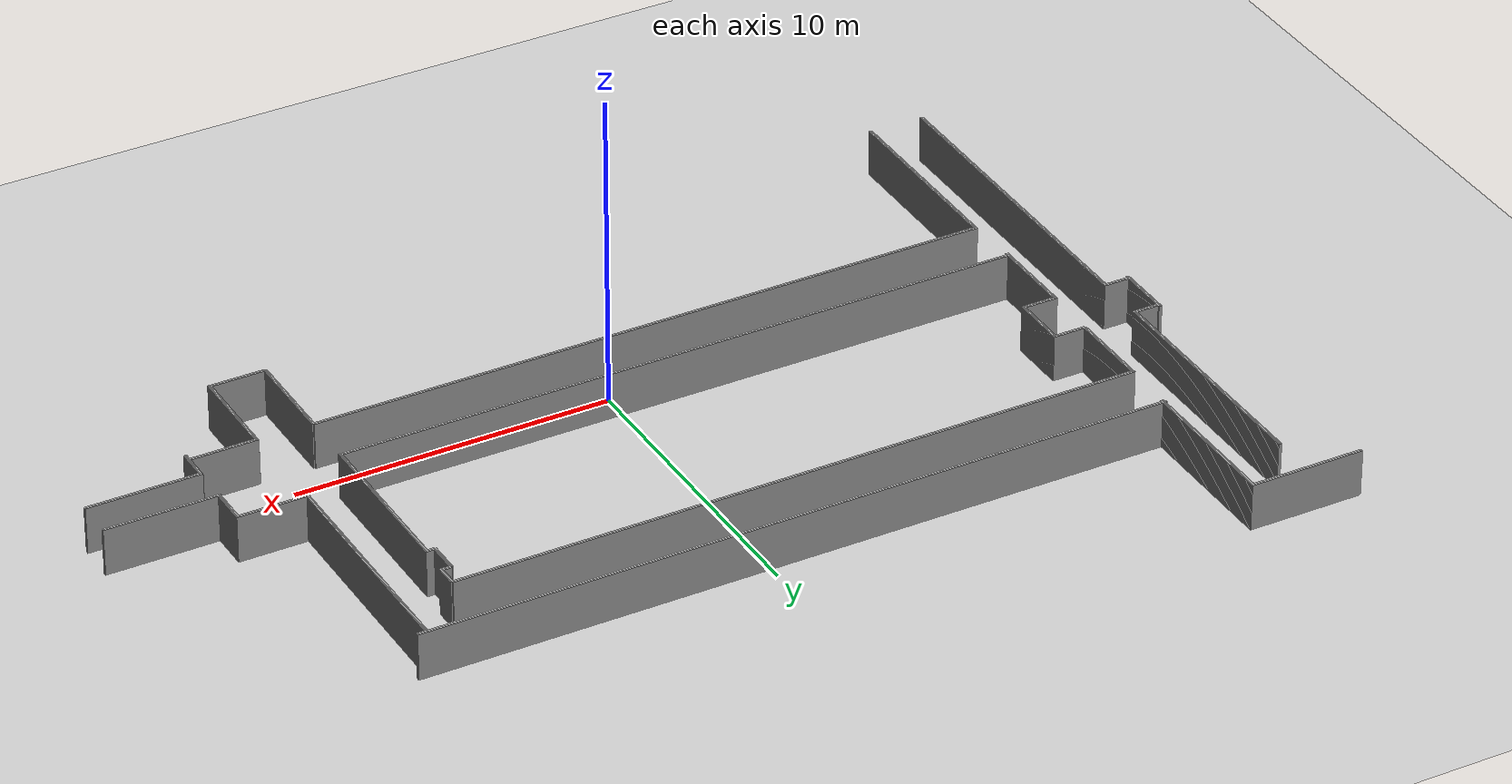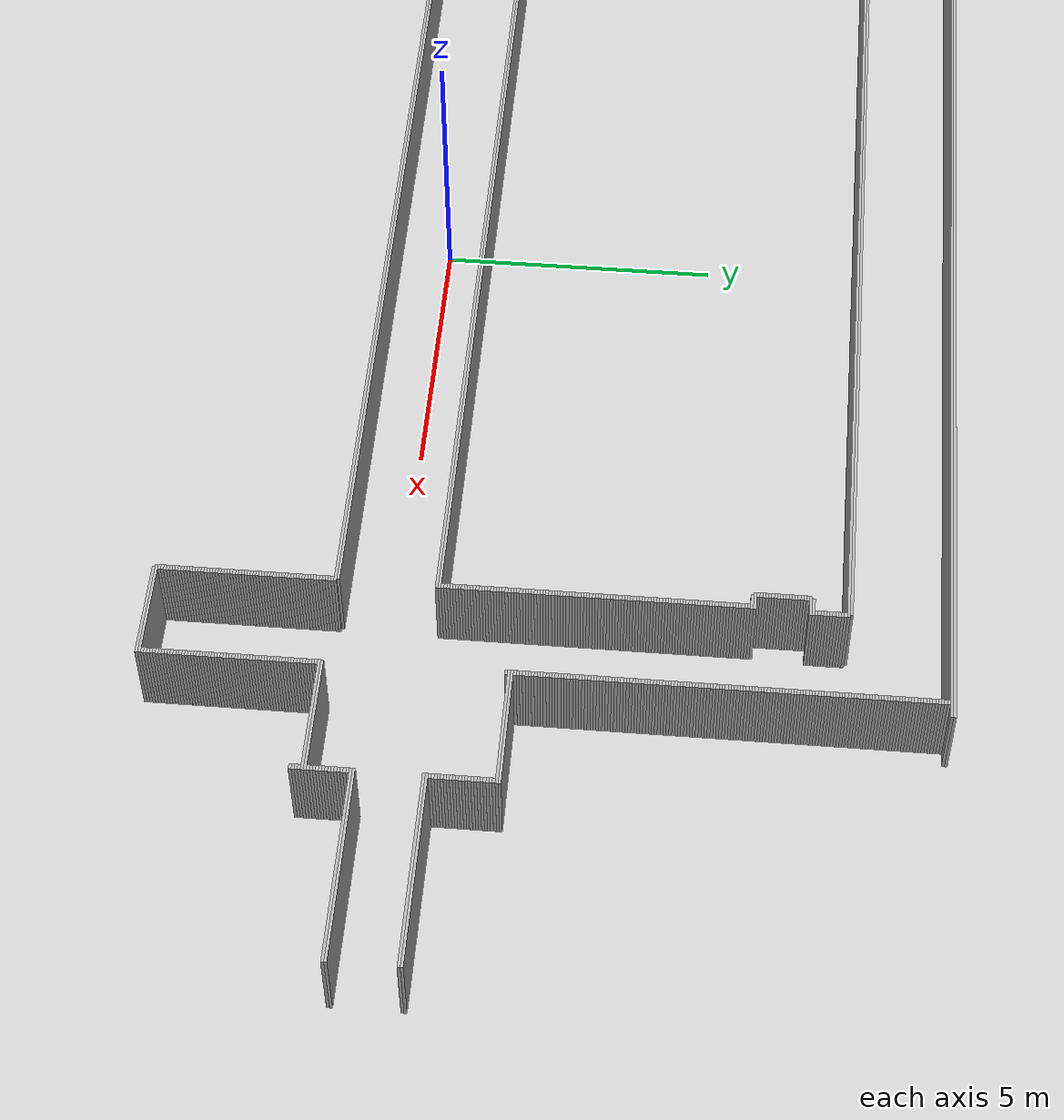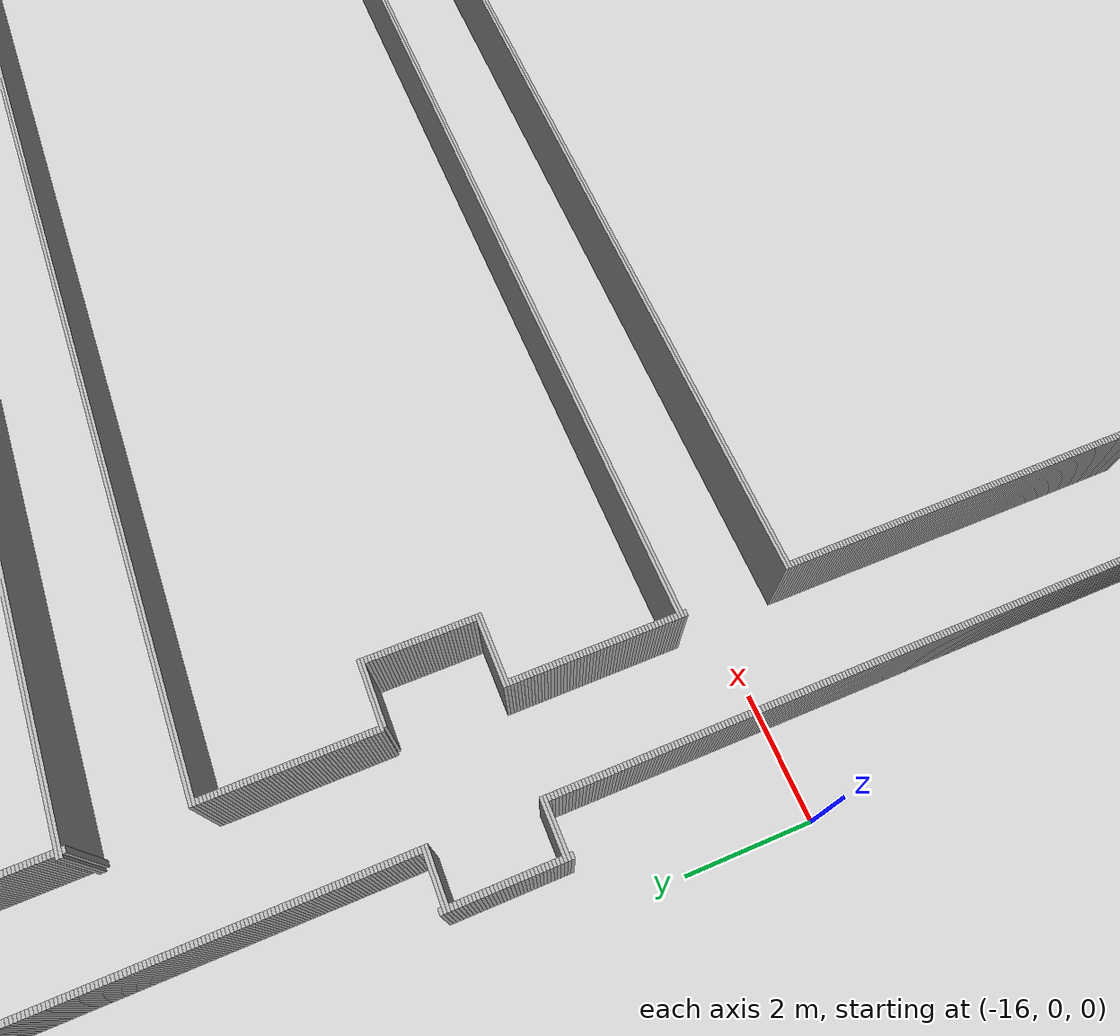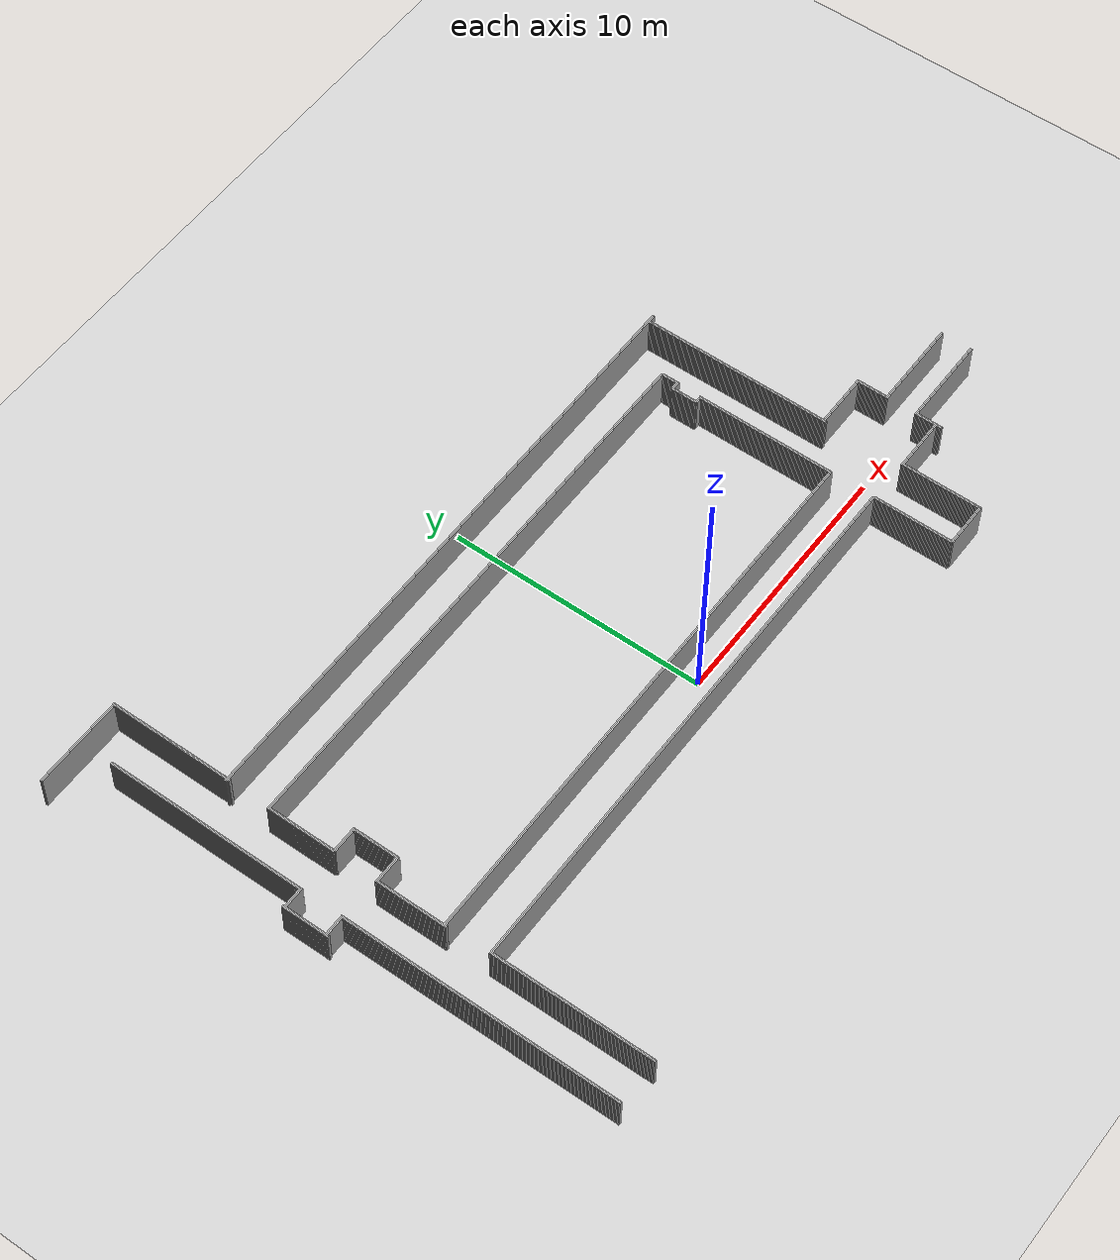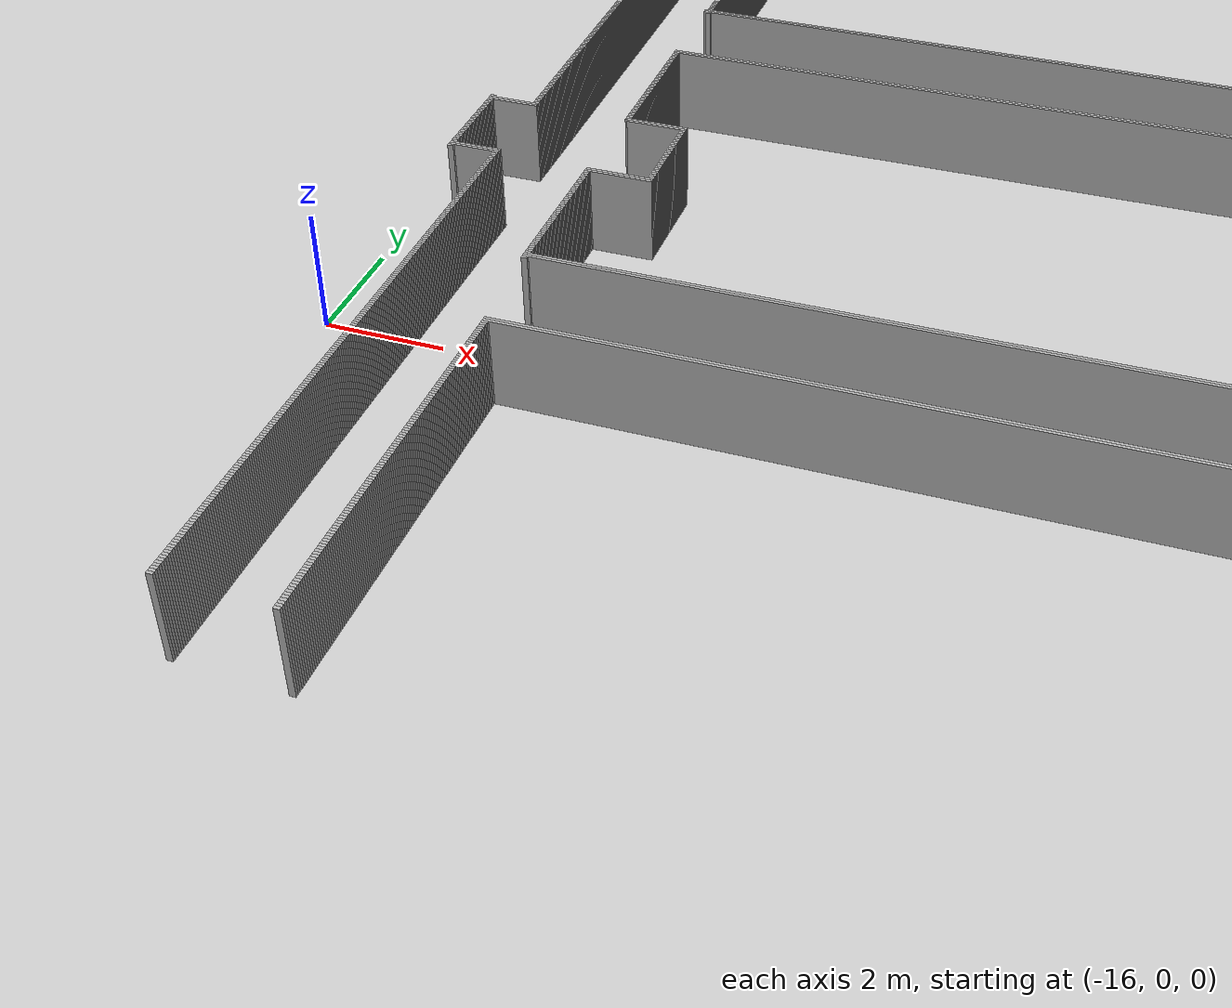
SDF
<?xml version='1.0'?>
<sdf version='1.7'>
  <world name='default'>
    <include>
      <uri>model://ground_plane</uri>
    </include>
    <include>
      <uri>model://sun</uri>
    </include>

    <model name="map_model">
      <static>true</static>
      <link name="map_link">

      <collision name='collision_0'>
        <pose>-14.524999999999999 14.349999999999994 0.75 0 0 0</pose>
        <geometry>
          <box>
            <size>3.6500000000000004 0.05 1.5</size>
          </box>
        </geometry>
      </collision>
      <visual name='visual_0'>
        <pose>-14.524999999999999 14.349999999999994 0.75 0 0 0</pose>
        <geometry>
          <box>
            <size>3.6500000000000004 0.05 1.5</size>
          </box>
        </geometry>
        <material>
          <ambient>0.3 0.3 0.3 1</ambient>
          <diffuse>0.7 0.7 0.7 1</diffuse>
        </material>
      </visual>

      <collision name='collision_1'>
        <pose>-14.524999999999999 14.299999999999997 0.75 0 0 0</pose>
        <geometry>
          <box>
            <size>3.6500000000000004 0.05 1.5</size>
          </box>
        </geometry>
      </collision>
      <visual name='visual_1'>
        <pose>-14.524999999999999 14.299999999999997 0.75 0 0 0</pose>
        <geometry>
          <box>
            <size>3.6500000000000004 0.05 1.5</size>
          </box>
        </geometry>
        <material>
          <ambient>0.3 0.3 0.3 1</ambient>
          <diffuse>0.7 0.7 0.7 1</diffuse>
        </material>
      </visual>

      <collision name='collision_2'>
        <pose>-12.75 14.25 0.75 0 0 0</pose>
        <geometry>
          <box>
            <size>0.1 0.05 1.5</size>
          </box>
        </geometry>
      </collision>
      <visual name='visual_2'>
        <pose>-12.75 14.25 0.75 0 0 0</pose>
        <geometry>
          <box>
            <size>0.1 0.05 1.5</size>
          </box>
        </geometry>
        <material>
          <ambient>0.3 0.3 0.3 1</ambient>
          <diffuse>0.7 0.7 0.7 1</diffuse>
        </material>
      </visual>

      <collision name='collision_3'>
        <pose>-12.75 14.200000000000003 0.75 0 0 0</pose>
        <geometry>
          <box>
            <size>0.1 0.05 1.5</size>
          </box>
        </geometry>
      </collision>
      <visual name='visual_3'>
        <pose>-12.75 14.200000000000003 0.75 0 0 0</pose>
        <geometry>
          <box>
            <size>0.1 0.05 1.5</size>
          </box>
        </geometry>
        <material>
          <ambient>0.3 0.3 0.3 1</ambient>
          <diffuse>0.7 0.7 0.7 1</diffuse>
        </material>
      </visual>

      <collision name='collision_4'>
        <pose>-12.75 14.150000000000006 0.75 0 0 0</pose>
        <geometry>
          <box>
            <size>0.1 0.05 1.5</size>
          </box>
        </geometry>
      </collision>
      <visual name='visual_4'>
        <pose>-12.75 14.150000000000006 0.75 0 0 0</pose>
        <geometry>
          <box>
            <size>0.1 0.05 1.5</size>
          </box>
        </geometry>
        <material>
          <ambient>0.3 0.3 0.3 1</ambient>
          <diffuse>0.7 0.7 0.7 1</diffuse>
        </material>
      </visual>

      <collision name='collision_5'>
        <pose>-12.75 14.099999999999994 0.75 0 0 0</pose>
        <geometry>
          <box>
            <size>0.1 0.05 1.5</size>
          </box>
        </geometry>
      </collision>
      <visual name='visual_5'>
        <pose>-12.75 14.099999999999994 0.75 0 0 0</pose>
        <geometry>
          <box>
            <size>0.1 0.05 1.5</size>
          </box>
        </geometry>
        <material>
          <ambient>0.3 0.3 0.3 1</ambient>
          <diffuse>0.7 0.7 0.7 1</diffuse>
        </material>
      </visual>

      <collision name='collision_6'>
        <pose>-12.75 14.049999999999997 0.75 0 0 0</pose>
        <geometry>
          <box>
            <size>0.1 0.05 1.5</size>
          </box>
        </geometry>
      </collision>
      <visual name='visual_6'>
        <pose>-12.75 14.049999999999997 0.75 0 0 0</pose>
        <geometry>
          <box>
            <size>0.1 0.05 1.5</size>
          </box>
        </geometry>
        <material>
          <ambient>0.3 0.3 0.3 1</ambient>
          <diffuse>0.7 0.7 0.7 1</diffuse>
        </material>
      </visual>

      <collision name='collision_7'>
        <pose>-12.75 14.0 0.75 0 0 0</pose>
        <geometry>
          <box>
            <size>0.1 0.05 1.5</size>
          </box>
        </geometry>
      </collision>
      <visual name='visual_7'>
        <pose>-12.75 14.0 0.75 0 0 0</pose>
        <geometry>
          <box>
            <size>0.1 0.05 1.5</size>
          </box>
        </geometry>
        <material>
          <ambient>0.3 0.3 0.3 1</ambient>
          <diffuse>0.7 0.7 0.7 1</diffuse>
        </material>
      </visual>

      <collision name='collision_8'>
        <pose>-12.75 13.950000000000003 0.75 0 0 0</pose>
        <geometry>
          <box>
            <size>0.1 0.05 1.5</size>
          </box>
        </geometry>
      </collision>
      <visual name='visual_8'>
        <pose>-12.75 13.950000000000003 0.75 0 0 0</pose>
        <geometry>
          <box>
            <size>0.1 0.05 1.5</size>
          </box>
        </geometry>
        <material>
          <ambient>0.3 0.3 0.3 1</ambient>
          <diffuse>0.7 0.7 0.7 1</diffuse>
        </material>
      </visual>

      <collision name='collision_9'>
        <pose>-12.75 13.900000000000006 0.75 0 0 0</pose>
        <geometry>
          <box>
            <size>0.1 0.05 1.5</size>
          </box>
        </geometry>
      </collision>
      <visual name='visual_9'>
        <pose>-12.75 13.900000000000006 0.75 0 0 0</pose>
        <geometry>
          <box>
            <size>0.1 0.05 1.5</size>
          </box>
        </geometry>
        <material>
          <ambient>0.3 0.3 0.3 1</ambient>
          <diffuse>0.7 0.7 0.7 1</diffuse>
        </material>
      </visual>

      <collision name='collision_10'>
        <pose>-12.75 13.849999999999994 0.75 0 0 0</pose>
        <geometry>
          <box>
            <size>0.1 0.05 1.5</size>
          </box>
        </geometry>
      </collision>
      <visual name='visual_10'>
        <pose>-12.75 13.849999999999994 0.75 0 0 0</pose>
        <geometry>
          <box>
            <size>0.1 0.05 1.5</size>
          </box>
        </geometry>
        <material>
          <ambient>0.3 0.3 0.3 1</ambient>
          <diffuse>0.7 0.7 0.7 1</diffuse>
        </material>
      </visual>

      <collision name='collision_11'>
        <pose>-12.75 13.799999999999997 0.75 0 0 0</pose>
        <geometry>
          <box>
            <size>0.1 0.05 1.5</size>
          </box>
        </geometry>
      </collision>
      <visual name='visual_11'>
        <pose>-12.75 13.799999999999997 0.75 0 0 0</pose>
        <geometry>
          <box>
            <size>0.1 0.05 1.5</size>
          </box>
        </geometry>
        <material>
          <ambient>0.3 0.3 0.3 1</ambient>
          <diffuse>0.7 0.7 0.7 1</diffuse>
        </material>
      </visual>

      <collision name='collision_12'>
        <pose>-12.75 13.75 0.75 0 0 0</pose>
        <geometry>
          <box>
            <size>0.1 0.05 1.5</size>
          </box>
        </geometry>
      </collision>
      <visual name='visual_12'>
        <pose>-12.75 13.75 0.75 0 0 0</pose>
        <geometry>
          <box>
            <size>0.1 0.05 1.5</size>
          </box>
        </geometry>
        <material>
          <ambient>0.3 0.3 0.3 1</ambient>
          <diffuse>0.7 0.7 0.7 1</diffuse>
        </material>
      </visual>

      <collision name='collision_13'>
        <pose>-12.75 13.700000000000003 0.75 0 0 0</pose>
        <geometry>
          <box>
            <size>0.1 0.05 1.5</size>
          </box>
        </geometry>
      </collision>
      <visual name='visual_13'>
        <pose>-12.75 13.700000000000003 0.75 0 0 0</pose>
        <geometry>
          <box>
            <size>0.1 0.05 1.5</size>
          </box>
        </geometry>
        <material>
          <ambient>0.3 0.3 0.3 1</ambient>
          <diffuse>0.7 0.7 0.7 1</diffuse>
        </material>
      </visual>

      <collision name='collision_14'>
        <pose>-12.75 13.650000000000006 0.75 0 0 0</pose>
        <geometry>
          <box>
            <size>0.1 0.05 1.5</size>
          </box>
        </geometry>
      </collision>
      <visual name='visual_14'>
        <pose>-12.75 13.650000000000006 0.75 0 0 0</pose>
        <geometry>
          <box>
            <size>0.1 0.05 1.5</size>
          </box>
        </geometry>
        <material>
          <ambient>0.3 0.3 0.3 1</ambient>
          <diffuse>0.7 0.7 0.7 1</diffuse>
        </material>
      </visual>

      <collision name='collision_15'>
        <pose>-12.75 13.599999999999994 0.75 0 0 0</pose>
        <geometry>
          <box>
            <size>0.1 0.05 1.5</size>
          </box>
        </geometry>
      </collision>
      <visual name='visual_15'>
        <pose>-12.75 13.599999999999994 0.75 0 0 0</pose>
        <geometry>
          <box>
            <size>0.1 0.05 1.5</size>
          </box>
        </geometry>
        <material>
          <ambient>0.3 0.3 0.3 1</ambient>
          <diffuse>0.7 0.7 0.7 1</diffuse>
        </material>
      </visual>

      <collision name='collision_16'>
        <pose>-12.75 13.549999999999997 0.75 0 0 0</pose>
        <geometry>
          <box>
            <size>0.1 0.05 1.5</size>
          </box>
        </geometry>
      </collision>
      <visual name='visual_16'>
        <pose>-12.75 13.549999999999997 0.75 0 0 0</pose>
        <geometry>
          <box>
            <size>0.1 0.05 1.5</size>
          </box>
        </geometry>
        <material>
          <ambient>0.3 0.3 0.3 1</ambient>
          <diffuse>0.7 0.7 0.7 1</diffuse>
        </material>
      </visual>

      <collision name='collision_17'>
        <pose>-12.75 13.5 0.75 0 0 0</pose>
        <geometry>
          <box>
            <size>0.1 0.05 1.5</size>
          </box>
        </geometry>
      </collision>
      <visual name='visual_17'>
        <pose>-12.75 13.5 0.75 0 0 0</pose>
        <geometry>
          <box>
            <size>0.1 0.05 1.5</size>
          </box>
        </geometry>
        <material>
          <ambient>0.3 0.3 0.3 1</ambient>
          <diffuse>0.7 0.7 0.7 1</diffuse>
        </material>
      </visual>

      <collision name='collision_18'>
        <pose>-12.75 13.450000000000003 0.75 0 0 0</pose>
        <geometry>
          <box>
            <size>0.1 0.05 1.5</size>
          </box>
        </geometry>
      </collision>
      <visual name='visual_18'>
        <pose>-12.75 13.450000000000003 0.75 0 0 0</pose>
        <geometry>
          <box>
            <size>0.1 0.05 1.5</size>
          </box>
        </geometry>
        <material>
          <ambient>0.3 0.3 0.3 1</ambient>
          <diffuse>0.7 0.7 0.7 1</diffuse>
        </material>
      </visual>

      <collision name='collision_19'>
        <pose>-12.75 13.400000000000006 0.75 0 0 0</pose>
        <geometry>
          <box>
            <size>0.1 0.05 1.5</size>
          </box>
        </geometry>
      </collision>
      <visual name='visual_19'>
        <pose>-12.75 13.400000000000006 0.75 0 0 0</pose>
        <geometry>
          <box>
            <size>0.1 0.05 1.5</size>
          </box>
        </geometry>
        <material>
          <ambient>0.3 0.3 0.3 1</ambient>
          <diffuse>0.7 0.7 0.7 1</diffuse>
        </material>
      </visual>

      <collision name='collision_20'>
        <pose>-12.75 13.349999999999994 0.75 0 0 0</pose>
        <geometry>
          <box>
            <size>0.1 0.05 1.5</size>
          </box>
        </geometry>
      </collision>
      <visual name='visual_20'>
        <pose>-12.75 13.349999999999994 0.75 0 0 0</pose>
        <geometry>
          <box>
            <size>0.1 0.05 1.5</size>
          </box>
        </geometry>
        <material>
          <ambient>0.3 0.3 0.3 1</ambient>
          <diffuse>0.7 0.7 0.7 1</diffuse>
        </material>
      </visual>

      <collision name='collision_21'>
        <pose>-12.75 13.299999999999997 0.75 0 0 0</pose>
        <geometry>
          <box>
            <size>0.1 0.05 1.5</size>
          </box>
        </geometry>
      </collision>
      <visual name='visual_21'>
        <pose>-12.75 13.299999999999997 0.75 0 0 0</pose>
        <geometry>
          <box>
            <size>0.1 0.05 1.5</size>
          </box>
        </geometry>
        <material>
          <ambient>0.3 0.3 0.3 1</ambient>
          <diffuse>0.7 0.7 0.7 1</diffuse>
        </material>
      </visual>

      <collision name='collision_22'>
        <pose>-12.75 13.25 0.75 0 0 0</pose>
        <geometry>
          <box>
            <size>0.1 0.05 1.5</size>
          </box>
        </geometry>
      </collision>
      <visual name='visual_22'>
        <pose>-12.75 13.25 0.75 0 0 0</pose>
        <geometry>
          <box>
            <size>0.1 0.05 1.5</size>
          </box>
        </geometry>
        <material>
          <ambient>0.3 0.3 0.3 1</ambient>
          <diffuse>0.7 0.7 0.7 1</diffuse>
        </material>
      </visual>

      <collision name='collision_23'>
        <pose>-12.75 13.200000000000003 0.75 0 0 0</pose>
        <geometry>
          <box>
            <size>0.1 0.05 1.5</size>
          </box>
        </geometry>
      </collision>
      <visual name='visual_23'>
        <pose>-12.75 13.200000000000003 0.75 0 0 0</pose>
        <geometry>
          <box>
            <size>0.1 0.05 1.5</size>
          </box>
        </geometry>
        <material>
          <ambient>0.3 0.3 0.3 1</ambient>
          <diffuse>0.7 0.7 0.7 1</diffuse>
        </material>
      </visual>

      <collision name='collision_24'>
        <pose>-12.75 13.150000000000006 0.75 0 0 0</pose>
        <geometry>
          <box>
            <size>0.1 0.05 1.5</size>
          </box>
        </geometry>
      </collision>
      <visual name='visual_24'>
        <pose>-12.75 13.150000000000006 0.75 0 0 0</pose>
        <geometry>
          <box>
            <size>0.1 0.05 1.5</size>
          </box>
        </geometry>
        <material>
          <ambient>0.3 0.3 0.3 1</ambient>
          <diffuse>0.7 0.7 0.7 1</diffuse>
        </material>
      </visual>

      <collision name='collision_25'>
        <pose>-12.75 13.099999999999994 0.75 0 0 0</pose>
        <geometry>
          <box>
            <size>0.1 0.05 1.5</size>
          </box>
        </geometry>
      </collision>
      <visual name='visual_25'>
        <pose>-12.75 13.099999999999994 0.75 0 0 0</pose>
        <geometry>
          <box>
            <size>0.1 0.05 1.5</size>
          </box>
        </geometry>
        <material>
          <ambient>0.3 0.3 0.3 1</ambient>
          <diffuse>0.7 0.7 0.7 1</diffuse>
        </material>
      </visual>

      <collision name='collision_26'>
        <pose>-12.75 13.049999999999997 0.75 0 0 0</pose>
        <geometry>
          <box>
            <size>0.1 0.05 1.5</size>
          </box>
        </geometry>
      </collision>
      <visual name='visual_26'>
        <pose>-12.75 13.049999999999997 0.75 0 0 0</pose>
        <geometry>
          <box>
            <size>0.1 0.05 1.5</size>
          </box>
        </geometry>
        <material>
          <ambient>0.3 0.3 0.3 1</ambient>
          <diffuse>0.7 0.7 0.7 1</diffuse>
        </material>
      </visual>

      <collision name='collision_27'>
        <pose>-12.75 13.0 0.75 0 0 0</pose>
        <geometry>
          <box>
            <size>0.1 0.05 1.5</size>
          </box>
        </geometry>
      </collision>
      <visual name='visual_27'>
        <pose>-12.75 13.0 0.75 0 0 0</pose>
        <geometry>
          <box>
            <size>0.1 0.05 1.5</size>
          </box>
        </geometry>
        <material>
          <ambient>0.3 0.3 0.3 1</ambient>
          <diffuse>0.7 0.7 0.7 1</diffuse>
        </material>
      </visual>

      <collision name='collision_28'>
        <pose>-14.5 12.950000000000003 0.75 0 0 0</pose>
        <geometry>
          <box>
            <size>0.1 0.05 1.5</size>
          </box>
        </geometry>
      </collision>
      <visual name='visual_28'>
        <pose>-14.5 12.950000000000003 0.75 0 0 0</pose>
        <geometry>
          <box>
            <size>0.1 0.05 1.5</size>
          </box>
        </geometry>
        <material>
          <ambient>0.3 0.3 0.3 1</ambient>
          <diffuse>0.7 0.7 0.7 1</diffuse>
        </material>
      </visual>

      <collision name='collision_29'>
        <pose>-12.75 12.950000000000003 0.75 0 0 0</pose>
        <geometry>
          <box>
            <size>0.1 0.05 1.5</size>
          </box>
        </geometry>
      </collision>
      <visual name='visual_29'>
        <pose>-12.75 12.950000000000003 0.75 0 0 0</pose>
        <geometry>
          <box>
            <size>0.1 0.05 1.5</size>
          </box>
        </geometry>
        <material>
          <ambient>0.3 0.3 0.3 1</ambient>
          <diffuse>0.7 0.7 0.7 1</diffuse>
        </material>
      </visual>

      <collision name='collision_30'>
        <pose>-14.5 12.900000000000006 0.75 0 0 0</pose>
        <geometry>
          <box>
            <size>0.1 0.05 1.5</size>
          </box>
        </geometry>
      </collision>
      <visual name='visual_30'>
        <pose>-14.5 12.900000000000006 0.75 0 0 0</pose>
        <geometry>
          <box>
            <size>0.1 0.05 1.5</size>
          </box>
        </geometry>
        <material>
          <ambient>0.3 0.3 0.3 1</ambient>
          <diffuse>0.7 0.7 0.7 1</diffuse>
        </material>
      </visual>

      <collision name='collision_31'>
        <pose>-12.75 12.900000000000006 0.75 0 0 0</pose>
        <geometry>
          <box>
            <size>0.1 0.05 1.5</size>
          </box>
        </geometry>
      </collision>
      <visual name='visual_31'>
        <pose>-12.75 12.900000000000006 0.75 0 0 0</pose>
        <geometry>
          <box>
            <size>0.1 0.05 1.5</size>
          </box>
        </geometry>
        <material>
          <ambient>0.3 0.3 0.3 1</ambient>
          <diffuse>0.7 0.7 0.7 1</diffuse>
        </material>
      </visual>

      <collision name='collision_32'>
        <pose>-14.5 12.849999999999994 0.75 0 0 0</pose>
        <geometry>
          <box>
            <size>0.1 0.05 1.5</size>
          </box>
        </geometry>
      </collision>
      <visual name='visual_32'>
        <pose>-14.5 12.849999999999994 0.75 0 0 0</pose>
        <geometry>
          <box>
            <size>0.1 0.05 1.5</size>
          </box>
        </geometry>
        <material>
          <ambient>0.3 0.3 0.3 1</ambient>
          <diffuse>0.7 0.7 0.7 1</diffuse>
        </material>
      </visual>

      <collision name='collision_33'>
        <pose>-12.75 12.849999999999994 0.75 0 0 0</pose>
        <geometry>
          <box>
            <size>0.1 0.05 1.5</size>
          </box>
        </geometry>
      </collision>
      <visual name='visual_33'>
        <pose>-12.75 12.849999999999994 0.75 0 0 0</pose>
        <geometry>
          <box>
            <size>0.1 0.05 1.5</size>
          </box>
        </geometry>
        <material>
          <ambient>0.3 0.3 0.3 1</ambient>
          <diffuse>0.7 0.7 0.7 1</diffuse>
        </material>
      </visual>

      <collision name='collision_34'>
        <pose>-14.5 12.799999999999997 0.75 0 0 0</pose>
        <geometry>
          <box>
            <size>0.1 0.05 1.5</size>
          </box>
        </geometry>
      </collision>
      <visual name='visual_34'>
        <pose>-14.5 12.799999999999997 0.75 0 0 0</pose>
        <geometry>
          <box>
            <size>0.1 0.05 1.5</size>
          </box>
        </geometry>
        <material>
          <ambient>0.3 0.3 0.3 1</ambient>
          <diffuse>0.7 0.7 0.7 1</diffuse>
        </material>
      </visual>

      <collision name='collision_35'>
        <pose>-12.75 12.799999999999997 0.75 0 0 0</pose>
        <geometry>
          <box>
            <size>0.1 0.05 1.5</size>
          </box>
        </geometry>
      </collision>
      <visual name='visual_35'>
        <pose>-12.75 12.799999999999997 0.75 0 0 0</pose>
        <geometry>
          <box>
            <size>0.1 0.05 1.5</size>
          </box>
        </geometry>
        <material>
          <ambient>0.3 0.3 0.3 1</ambient>
          <diffuse>0.7 0.7 0.7 1</diffuse>
        </material>
      </visual>

      <collision name='collision_36'>
        <pose>-14.5 12.75 0.75 0 0 0</pose>
        <geometry>
          <box>
            <size>0.1 0.05 1.5</size>
          </box>
        </geometry>
      </collision>
      <visual name='visual_36'>
        <pose>-14.5 12.75 0.75 0 0 0</pose>
        <geometry>
          <box>
            <size>0.1 0.05 1.5</size>
          </box>
        </geometry>
        <material>
          <ambient>0.3 0.3 0.3 1</ambient>
          <diffuse>0.7 0.7 0.7 1</diffuse>
        </material>
      </visual>

      <collision name='collision_37'>
        <pose>-12.75 12.75 0.75 0 0 0</pose>
        <geometry>
          <box>
            <size>0.1 0.05 1.5</size>
          </box>
        </geometry>
      </collision>
      <visual name='visual_37'>
        <pose>-12.75 12.75 0.75 0 0 0</pose>
        <geometry>
          <box>
            <size>0.1 0.05 1.5</size>
          </box>
        </geometry>
        <material>
          <ambient>0.3 0.3 0.3 1</ambient>
          <diffuse>0.7 0.7 0.7 1</diffuse>
        </material>
      </visual>

      <collision name='collision_38'>
        <pose>-14.5 12.700000000000003 0.75 0 0 0</pose>
        <geometry>
          <box>
            <size>0.1 0.05 1.5</size>
          </box>
        </geometry>
      </collision>
      <visual name='visual_38'>
        <pose>-14.5 12.700000000000003 0.75 0 0 0</pose>
        <geometry>
          <box>
            <size>0.1 0.05 1.5</size>
          </box>
        </geometry>
        <material>
          <ambient>0.3 0.3 0.3 1</ambient>
          <diffuse>0.7 0.7 0.7 1</diffuse>
        </material>
      </visual>

      <collision name='collision_39'>
        <pose>-12.75 12.700000000000003 0.75 0 0 0</pose>
        <geometry>
          <box>
            <size>0.1 0.05 1.5</size>
          </box>
        </geometry>
      </collision>
      <visual name='visual_39'>
        <pose>-12.75 12.700000000000003 0.75 0 0 0</pose>
        <geometry>
          <box>
            <size>0.1 0.05 1.5</size>
          </box>
        </geometry>
        <material>
          <ambient>0.3 0.3 0.3 1</ambient>
          <diffuse>0.7 0.7 0.7 1</diffuse>
        </material>
      </visual>

      <collision name='collision_40'>
        <pose>-14.5 12.649999999999999 0.75 0 0 0</pose>
        <geometry>
          <box>
            <size>0.1 0.05 1.5</size>
          </box>
        </geometry>
      </collision>
      <visual name='visual_40'>
        <pose>-14.5 12.649999999999999 0.75 0 0 0</pose>
        <geometry>
          <box>
            <size>0.1 0.05 1.5</size>
          </box>
        </geometry>
        <material>
          <ambient>0.3 0.3 0.3 1</ambient>
          <diffuse>0.7 0.7 0.7 1</diffuse>
        </material>
      </visual>

      <collision name='collision_41'>
        <pose>-12.75 12.649999999999999 0.75 0 0 0</pose>
        <geometry>
          <box>
            <size>0.1 0.05 1.5</size>
          </box>
        </geometry>
      </collision>
      <visual name='visual_41'>
        <pose>-12.75 12.649999999999999 0.75 0 0 0</pose>
        <geometry>
          <box>
            <size>0.1 0.05 1.5</size>
          </box>
        </geometry>
        <material>
          <ambient>0.3 0.3 0.3 1</ambient>
          <diffuse>0.7 0.7 0.7 1</diffuse>
        </material>
      </visual>

      <collision name='collision_42'>
        <pose>-14.5 12.600000000000001 0.75 0 0 0</pose>
        <geometry>
          <box>
            <size>0.1 0.05 1.5</size>
          </box>
        </geometry>
      </collision>
      <visual name='visual_42'>
        <pose>-14.5 12.600000000000001 0.75 0 0 0</pose>
        <geometry>
          <box>
            <size>0.1 0.05 1.5</size>
          </box>
        </geometry>
        <material>
          <ambient>0.3 0.3 0.3 1</ambient>
          <diffuse>0.7 0.7 0.7 1</diffuse>
        </material>
      </visual>

      <collision name='collision_43'>
        <pose>-12.75 12.600000000000001 0.75 0 0 0</pose>
        <geometry>
          <box>
            <size>0.1 0.05 1.5</size>
          </box>
        </geometry>
      </collision>
      <visual name='visual_43'>
        <pose>-12.75 12.600000000000001 0.75 0 0 0</pose>
        <geometry>
          <box>
            <size>0.1 0.05 1.5</size>
          </box>
        </geometry>
        <material>
          <ambient>0.3 0.3 0.3 1</ambient>
          <diffuse>0.7 0.7 0.7 1</diffuse>
        </material>
      </visual>

      <collision name='collision_44'>
        <pose>-14.5 12.549999999999997 0.75 0 0 0</pose>
        <geometry>
          <box>
            <size>0.1 0.05 1.5</size>
          </box>
        </geometry>
      </collision>
      <visual name='visual_44'>
        <pose>-14.5 12.549999999999997 0.75 0 0 0</pose>
        <geometry>
          <box>
            <size>0.1 0.05 1.5</size>
          </box>
        </geometry>
        <material>
          <ambient>0.3 0.3 0.3 1</ambient>
          <diffuse>0.7 0.7 0.7 1</diffuse>
        </material>
      </visual>

      <collision name='collision_45'>
        <pose>-12.75 12.549999999999997 0.75 0 0 0</pose>
        <geometry>
          <box>
            <size>0.1 0.05 1.5</size>
          </box>
        </geometry>
      </collision>
      <visual name='visual_45'>
        <pose>-12.75 12.549999999999997 0.75 0 0 0</pose>
        <geometry>
          <box>
            <size>0.1 0.05 1.5</size>
          </box>
        </geometry>
        <material>
          <ambient>0.3 0.3 0.3 1</ambient>
          <diffuse>0.7 0.7 0.7 1</diffuse>
        </material>
      </visual>

      <collision name='collision_46'>
        <pose>-14.5 12.5 0.75 0 0 0</pose>
        <geometry>
          <box>
            <size>0.1 0.05 1.5</size>
          </box>
        </geometry>
      </collision>
      <visual name='visual_46'>
        <pose>-14.5 12.5 0.75 0 0 0</pose>
        <geometry>
          <box>
            <size>0.1 0.05 1.5</size>
          </box>
        </geometry>
        <material>
          <ambient>0.3 0.3 0.3 1</ambient>
          <diffuse>0.7 0.7 0.7 1</diffuse>
        </material>
      </visual>

      <collision name='collision_47'>
        <pose>-12.75 12.5 0.75 0 0 0</pose>
        <geometry>
          <box>
            <size>0.1 0.05 1.5</size>
          </box>
        </geometry>
      </collision>
      <visual name='visual_47'>
        <pose>-12.75 12.5 0.75 0 0 0</pose>
        <geometry>
          <box>
            <size>0.1 0.05 1.5</size>
          </box>
        </geometry>
        <material>
          <ambient>0.3 0.3 0.3 1</ambient>
          <diffuse>0.7 0.7 0.7 1</diffuse>
        </material>
      </visual>

      <collision name='collision_48'>
        <pose>-14.5 12.450000000000003 0.75 0 0 0</pose>
        <geometry>
          <box>
            <size>0.1 0.05 1.5</size>
          </box>
        </geometry>
      </collision>
      <visual name='visual_48'>
        <pose>-14.5 12.450000000000003 0.75 0 0 0</pose>
        <geometry>
          <box>
            <size>0.1 0.05 1.5</size>
          </box>
        </geometry>
        <material>
          <ambient>0.3 0.3 0.3 1</ambient>
          <diffuse>0.7 0.7 0.7 1</diffuse>
        </material>
      </visual>

      <collision name='collision_49'>
        <pose>-12.75 12.450000000000003 0.75 0 0 0</pose>
        <geometry>
          <box>
            <size>0.1 0.05 1.5</size>
          </box>
        </geometry>
      </collision>
      <visual name='visual_49'>
        <pose>-12.75 12.450000000000003 0.75 0 0 0</pose>
        <geometry>
          <box>
            <size>0.1 0.05 1.5</size>
          </box>
        </geometry>
        <material>
          <ambient>0.3 0.3 0.3 1</ambient>
          <diffuse>0.7 0.7 0.7 1</diffuse>
        </material>
      </visual>

      <collision name='collision_50'>
        <pose>-14.5 12.399999999999999 0.75 0 0 0</pose>
        <geometry>
          <box>
            <size>0.1 0.05 1.5</size>
          </box>
        </geometry>
      </collision>
      <visual name='visual_50'>
        <pose>-14.5 12.399999999999999 0.75 0 0 0</pose>
        <geometry>
          <box>
            <size>0.1 0.05 1.5</size>
          </box>
        </geometry>
        <material>
          <ambient>0.3 0.3 0.3 1</ambient>
          <diffuse>0.7 0.7 0.7 1</diffuse>
        </material>
      </visual>

      <collision name='collision_51'>
        <pose>-12.75 12.399999999999999 0.75 0 0 0</pose>
        <geometry>
          <box>
            <size>0.1 0.05 1.5</size>
          </box>
        </geometry>
      </collision>
      <visual name='visual_51'>
        <pose>-12.75 12.399999999999999 0.75 0 0 0</pose>
        <geometry>
          <box>
            <size>0.1 0.05 1.5</size>
          </box>
        </geometry>
        <material>
          <ambient>0.3 0.3 0.3 1</ambient>
          <diffuse>0.7 0.7 0.7 1</diffuse>
        </material>
      </visual>

      <collision name='collision_52'>
        <pose>-14.5 12.350000000000001 0.75 0 0 0</pose>
        <geometry>
          <box>
            <size>0.1 0.05 1.5</size>
          </box>
        </geometry>
      </collision>
      <visual name='visual_52'>
        <pose>-14.5 12.350000000000001 0.75 0 0 0</pose>
        <geometry>
          <box>
            <size>0.1 0.05 1.5</size>
          </box>
        </geometry>
        <material>
          <ambient>0.3 0.3 0.3 1</ambient>
          <diffuse>0.7 0.7 0.7 1</diffuse>
        </material>
      </visual>

      <collision name='collision_53'>
        <pose>-12.75 12.350000000000001 0.75 0 0 0</pose>
        <geometry>
          <box>
            <size>0.1 0.05 1.5</size>
          </box>
        </geometry>
      </collision>
      <visual name='visual_53'>
        <pose>-12.75 12.350000000000001 0.75 0 0 0</pose>
        <geometry>
          <box>
            <size>0.1 0.05 1.5</size>
          </box>
        </geometry>
        <material>
          <ambient>0.3 0.3 0.3 1</ambient>
          <diffuse>0.7 0.7 0.7 1</diffuse>
        </material>
      </visual>

      <collision name='collision_54'>
        <pose>-14.5 12.299999999999997 0.75 0 0 0</pose>
        <geometry>
          <box>
            <size>0.1 0.05 1.5</size>
          </box>
        </geometry>
      </collision>
      <visual name='visual_54'>
        <pose>-14.5 12.299999999999997 0.75 0 0 0</pose>
        <geometry>
          <box>
            <size>0.1 0.05 1.5</size>
          </box>
        </geometry>
        <material>
          <ambient>0.3 0.3 0.3 1</ambient>
          <diffuse>0.7 0.7 0.7 1</diffuse>
        </material>
      </visual>

      <collision name='collision_55'>
        <pose>-12.75 12.299999999999997 0.75 0 0 0</pose>
        <geometry>
          <box>
            <size>0.1 0.05 1.5</size>
          </box>
        </geometry>
      </collision>
      <visual name='visual_55'>
        <pose>-12.75 12.299999999999997 0.75 0 0 0</pose>
        <geometry>
          <box>
            <size>0.1 0.05 1.5</size>
          </box>
        </geometry>
        <material>
          <ambient>0.3 0.3 0.3 1</ambient>
          <diffuse>0.7 0.7 0.7 1</diffuse>
        </material>
      </visual>

      <collision name='collision_56'>
        <pose>-14.5 12.25 0.75 0 0 0</pose>
        <geometry>
          <box>
            <size>0.1 0.05 1.5</size>
          </box>
        </geometry>
      </collision>
      <visual name='visual_56'>
        <pose>-14.5 12.25 0.75 0 0 0</pose>
        <geometry>
          <box>
            <size>0.1 0.05 1.5</size>
          </box>
        </geometry>
        <material>
          <ambient>0.3 0.3 0.3 1</ambient>
          <diffuse>0.7 0.7 0.7 1</diffuse>
        </material>
      </visual>

      <collision name='collision_57'>
        <pose>-12.75 12.25 0.75 0 0 0</pose>
        <geometry>
          <box>
            <size>0.1 0.05 1.5</size>
          </box>
        </geometry>
      </collision>
      <visual name='visual_57'>
        <pose>-12.75 12.25 0.75 0 0 0</pose>
        <geometry>
          <box>
            <size>0.1 0.05 1.5</size>
          </box>
        </geometry>
        <material>
          <ambient>0.3 0.3 0.3 1</ambient>
          <diffuse>0.7 0.7 0.7 1</diffuse>
        </material>
      </visual>

      <collision name='collision_58'>
        <pose>-14.5 12.200000000000003 0.75 0 0 0</pose>
        <geometry>
          <box>
            <size>0.1 0.05 1.5</size>
          </box>
        </geometry>
      </collision>
      <visual name='visual_58'>
        <pose>-14.5 12.200000000000003 0.75 0 0 0</pose>
        <geometry>
          <box>
            <size>0.1 0.05 1.5</size>
          </box>
        </geometry>
        <material>
          <ambient>0.3 0.3 0.3 1</ambient>
          <diffuse>0.7 0.7 0.7 1</diffuse>
        </material>
      </visual>

      <collision name='collision_59'>
        <pose>-12.75 12.200000000000003 0.75 0 0 0</pose>
        <geometry>
          <box>
            <size>0.1 0.05 1.5</size>
          </box>
        </geometry>
      </collision>
      <visual name='visual_59'>
        <pose>-12.75 12.200000000000003 0.75 0 0 0</pose>
        <geometry>
          <box>
            <size>0.1 0.05 1.5</size>
          </box>
        </geometry>
        <material>
          <ambient>0.3 0.3 0.3 1</ambient>
          <diffuse>0.7 0.7 0.7 1</diffuse>
        </material>
      </visual>

      <collision name='collision_60'>
        <pose>-14.5 12.149999999999999 0.75 0 0 0</pose>
        <geometry>
          <box>
            <size>0.1 0.05 1.5</size>
          </box>
        </geometry>
      </collision>
      <visual name='visual_60'>
        <pose>-14.5 12.149999999999999 0.75 0 0 0</pose>
        <geometry>
          <box>
            <size>0.1 0.05 1.5</size>
          </box>
        </geometry>
        <material>
          <ambient>0.3 0.3 0.3 1</ambient>
          <diffuse>0.7 0.7 0.7 1</diffuse>
        </material>
      </visual>

      <collision name='collision_61'>
        <pose>-12.75 12.149999999999999 0.75 0 0 0</pose>
        <geometry>
          <box>
            <size>0.1 0.05 1.5</size>
          </box>
        </geometry>
      </collision>
      <visual name='visual_61'>
        <pose>-12.75 12.149999999999999 0.75 0 0 0</pose>
        <geometry>
          <box>
            <size>0.1 0.05 1.5</size>
          </box>
        </geometry>
        <material>
          <ambient>0.3 0.3 0.3 1</ambient>
          <diffuse>0.7 0.7 0.7 1</diffuse>
        </material>
      </visual>

      <collision name='collision_62'>
        <pose>-14.5 12.100000000000001 0.75 0 0 0</pose>
        <geometry>
          <box>
            <size>0.1 0.05 1.5</size>
          </box>
        </geometry>
      </collision>
      <visual name='visual_62'>
        <pose>-14.5 12.100000000000001 0.75 0 0 0</pose>
        <geometry>
          <box>
            <size>0.1 0.05 1.5</size>
          </box>
        </geometry>
        <material>
          <ambient>0.3 0.3 0.3 1</ambient>
          <diffuse>0.7 0.7 0.7 1</diffuse>
        </material>
      </visual>

      <collision name='collision_63'>
        <pose>-12.75 12.100000000000001 0.75 0 0 0</pose>
        <geometry>
          <box>
            <size>0.1 0.05 1.5</size>
          </box>
        </geometry>
      </collision>
      <visual name='visual_63'>
        <pose>-12.75 12.100000000000001 0.75 0 0 0</pose>
        <geometry>
          <box>
            <size>0.1 0.05 1.5</size>
          </box>
        </geometry>
        <material>
          <ambient>0.3 0.3 0.3 1</ambient>
          <diffuse>0.7 0.7 0.7 1</diffuse>
        </material>
      </visual>

      <collision name='collision_64'>
        <pose>-14.5 12.049999999999997 0.75 0 0 0</pose>
        <geometry>
          <box>
            <size>0.1 0.05 1.5</size>
          </box>
        </geometry>
      </collision>
      <visual name='visual_64'>
        <pose>-14.5 12.049999999999997 0.75 0 0 0</pose>
        <geometry>
          <box>
            <size>0.1 0.05 1.5</size>
          </box>
        </geometry>
        <material>
          <ambient>0.3 0.3 0.3 1</ambient>
          <diffuse>0.7 0.7 0.7 1</diffuse>
        </material>
      </visual>

      <collision name='collision_65'>
        <pose>-12.75 12.049999999999997 0.75 0 0 0</pose>
        <geometry>
          <box>
            <size>0.1 0.05 1.5</size>
          </box>
        </geometry>
      </collision>
      <visual name='visual_65'>
        <pose>-12.75 12.049999999999997 0.75 0 0 0</pose>
        <geometry>
          <box>
            <size>0.1 0.05 1.5</size>
          </box>
        </geometry>
        <material>
          <ambient>0.3 0.3 0.3 1</ambient>
          <diffuse>0.7 0.7 0.7 1</diffuse>
        </material>
      </visual>

      <collision name='collision_66'>
        <pose>-14.5 12.0 0.75 0 0 0</pose>
        <geometry>
          <box>
            <size>0.1 0.05 1.5</size>
          </box>
        </geometry>
      </collision>
      <visual name='visual_66'>
        <pose>-14.5 12.0 0.75 0 0 0</pose>
        <geometry>
          <box>
            <size>0.1 0.05 1.5</size>
          </box>
        </geometry>
        <material>
          <ambient>0.3 0.3 0.3 1</ambient>
          <diffuse>0.7 0.7 0.7 1</diffuse>
        </material>
      </visual>

      <collision name='collision_67'>
        <pose>-12.75 12.0 0.75 0 0 0</pose>
        <geometry>
          <box>
            <size>0.1 0.05 1.5</size>
          </box>
        </geometry>
      </collision>
      <visual name='visual_67'>
        <pose>-12.75 12.0 0.75 0 0 0</pose>
        <geometry>
          <box>
            <size>0.1 0.05 1.5</size>
          </box>
        </geometry>
        <material>
          <ambient>0.3 0.3 0.3 1</ambient>
          <diffuse>0.7 0.7 0.7 1</diffuse>
        </material>
      </visual>

      <collision name='collision_68'>
        <pose>-14.5 11.950000000000003 0.75 0 0 0</pose>
        <geometry>
          <box>
            <size>0.1 0.05 1.5</size>
          </box>
        </geometry>
      </collision>
      <visual name='visual_68'>
        <pose>-14.5 11.950000000000003 0.75 0 0 0</pose>
        <geometry>
          <box>
            <size>0.1 0.05 1.5</size>
          </box>
        </geometry>
        <material>
          <ambient>0.3 0.3 0.3 1</ambient>
          <diffuse>0.7 0.7 0.7 1</diffuse>
        </material>
      </visual>

      <collision name='collision_69'>
        <pose>-12.75 11.950000000000003 0.75 0 0 0</pose>
        <geometry>
          <box>
            <size>0.1 0.05 1.5</size>
          </box>
        </geometry>
      </collision>
      <visual name='visual_69'>
        <pose>-12.75 11.950000000000003 0.75 0 0 0</pose>
        <geometry>
          <box>
            <size>0.1 0.05 1.5</size>
          </box>
        </geometry>
        <material>
          <ambient>0.3 0.3 0.3 1</ambient>
          <diffuse>0.7 0.7 0.7 1</diffuse>
        </material>
      </visual>

      <collision name='collision_70'>
        <pose>-14.5 11.899999999999999 0.75 0 0 0</pose>
        <geometry>
          <box>
            <size>0.1 0.05 1.5</size>
          </box>
        </geometry>
      </collision>
      <visual name='visual_70'>
        <pose>-14.5 11.899999999999999 0.75 0 0 0</pose>
        <geometry>
          <box>
            <size>0.1 0.05 1.5</size>
          </box>
        </geometry>
        <material>
          <ambient>0.3 0.3 0.3 1</ambient>
          <diffuse>0.7 0.7 0.7 1</diffuse>
        </material>
      </visual>

      <collision name='collision_71'>
        <pose>-12.75 11.899999999999999 0.75 0 0 0</pose>
        <geometry>
          <box>
            <size>0.1 0.05 1.5</size>
          </box>
        </geometry>
      </collision>
      <visual name='visual_71'>
        <pose>-12.75 11.899999999999999 0.75 0 0 0</pose>
        <geometry>
          <box>
            <size>0.1 0.05 1.5</size>
          </box>
        </geometry>
        <material>
          <ambient>0.3 0.3 0.3 1</ambient>
          <diffuse>0.7 0.7 0.7 1</diffuse>
        </material>
      </visual>

      <collision name='collision_72'>
        <pose>-14.5 11.850000000000001 0.75 0 0 0</pose>
        <geometry>
          <box>
            <size>0.1 0.05 1.5</size>
          </box>
        </geometry>
      </collision>
      <visual name='visual_72'>
        <pose>-14.5 11.850000000000001 0.75 0 0 0</pose>
        <geometry>
          <box>
            <size>0.1 0.05 1.5</size>
          </box>
        </geometry>
        <material>
          <ambient>0.3 0.3 0.3 1</ambient>
          <diffuse>0.7 0.7 0.7 1</diffuse>
        </material>
      </visual>

      <collision name='collision_73'>
        <pose>-12.75 11.850000000000001 0.75 0 0 0</pose>
        <geometry>
          <box>
            <size>0.1 0.05 1.5</size>
          </box>
        </geometry>
      </collision>
      <visual name='visual_73'>
        <pose>-12.75 11.850000000000001 0.75 0 0 0</pose>
        <geometry>
          <box>
            <size>0.1 0.05 1.5</size>
          </box>
        </geometry>
        <material>
          <ambient>0.3 0.3 0.3 1</ambient>
          <diffuse>0.7 0.7 0.7 1</diffuse>
        </material>
      </visual>

      <collision name='collision_74'>
        <pose>-14.5 11.799999999999997 0.75 0 0 0</pose>
        <geometry>
          <box>
            <size>0.1 0.05 1.5</size>
          </box>
        </geometry>
      </collision>
      <visual name='visual_74'>
        <pose>-14.5 11.799999999999997 0.75 0 0 0</pose>
        <geometry>
          <box>
            <size>0.1 0.05 1.5</size>
          </box>
        </geometry>
        <material>
          <ambient>0.3 0.3 0.3 1</ambient>
          <diffuse>0.7 0.7 0.7 1</diffuse>
        </material>
      </visual>

      <collision name='collision_75'>
        <pose>-12.75 11.799999999999997 0.75 0 0 0</pose>
        <geometry>
          <box>
            <size>0.1 0.05 1.5</size>
          </box>
        </geometry>
      </collision>
      <visual name='visual_75'>
        <pose>-12.75 11.799999999999997 0.75 0 0 0</pose>
        <geometry>
          <box>
            <size>0.1 0.05 1.5</size>
          </box>
        </geometry>
        <material>
          <ambient>0.3 0.3 0.3 1</ambient>
          <diffuse>0.7 0.7 0.7 1</diffuse>
        </material>
      </visual>

      <collision name='collision_76'>
        <pose>-14.5 11.75 0.75 0 0 0</pose>
        <geometry>
          <box>
            <size>0.1 0.05 1.5</size>
          </box>
        </geometry>
      </collision>
      <visual name='visual_76'>
        <pose>-14.5 11.75 0.75 0 0 0</pose>
        <geometry>
          <box>
            <size>0.1 0.05 1.5</size>
          </box>
        </geometry>
        <material>
          <ambient>0.3 0.3 0.3 1</ambient>
          <diffuse>0.7 0.7 0.7 1</diffuse>
        </material>
      </visual>

      <collision name='collision_77'>
        <pose>-12.75 11.75 0.75 0 0 0</pose>
        <geometry>
          <box>
            <size>0.1 0.05 1.5</size>
          </box>
        </geometry>
      </collision>
      <visual name='visual_77'>
        <pose>-12.75 11.75 0.75 0 0 0</pose>
        <geometry>
          <box>
            <size>0.1 0.05 1.5</size>
          </box>
        </geometry>
        <material>
          <ambient>0.3 0.3 0.3 1</ambient>
          <diffuse>0.7 0.7 0.7 1</diffuse>
        </material>
      </visual>

      <collision name='collision_78'>
        <pose>-14.5 11.700000000000003 0.75 0 0 0</pose>
        <geometry>
          <box>
            <size>0.1 0.05 1.5</size>
          </box>
        </geometry>
      </collision>
      <visual name='visual_78'>
        <pose>-14.5 11.700000000000003 0.75 0 0 0</pose>
        <geometry>
          <box>
            <size>0.1 0.05 1.5</size>
          </box>
        </geometry>
        <material>
          <ambient>0.3 0.3 0.3 1</ambient>
          <diffuse>0.7 0.7 0.7 1</diffuse>
        </material>
      </visual>

      <collision name='collision_79'>
        <pose>-12.75 11.700000000000003 0.75 0 0 0</pose>
        <geometry>
          <box>
            <size>0.1 0.05 1.5</size>
          </box>
        </geometry>
      </collision>
      <visual name='visual_79'>
        <pose>-12.75 11.700000000000003 0.75 0 0 0</pose>
        <geometry>
          <box>
            <size>0.1 0.05 1.5</size>
          </box>
        </geometry>
        <material>
          <ambient>0.3 0.3 0.3 1</ambient>
          <diffuse>0.7 0.7 0.7 1</diffuse>
        </material>
      </visual>

      <collision name='collision_80'>
        <pose>-14.5 11.649999999999999 0.75 0 0 0</pose>
        <geometry>
          <box>
            <size>0.1 0.05 1.5</size>
          </box>
        </geometry>
      </collision>
      <visual name='visual_80'>
        <pose>-14.5 11.649999999999999 0.75 0 0 0</pose>
        <geometry>
          <box>
            <size>0.1 0.05 1.5</size>
          </box>
        </geometry>
        <material>
          <ambient>0.3 0.3 0.3 1</ambient>
          <diffuse>0.7 0.7 0.7 1</diffuse>
        </material>
      </visual>

      <collision name='collision_81'>
        <pose>-12.75 11.649999999999999 0.75 0 0 0</pose>
        <geometry>
          <box>
            <size>0.1 0.05 1.5</size>
          </box>
        </geometry>
      </collision>
      <visual name='visual_81'>
        <pose>-12.75 11.649999999999999 0.75 0 0 0</pose>
        <geometry>
          <box>
            <size>0.1 0.05 1.5</size>
          </box>
        </geometry>
        <material>
          <ambient>0.3 0.3 0.3 1</ambient>
          <diffuse>0.7 0.7 0.7 1</diffuse>
        </material>
      </visual>

      <collision name='collision_82'>
        <pose>-14.5 11.600000000000001 0.75 0 0 0</pose>
        <geometry>
          <box>
            <size>0.1 0.05 1.5</size>
          </box>
        </geometry>
      </collision>
      <visual name='visual_82'>
        <pose>-14.5 11.600000000000001 0.75 0 0 0</pose>
        <geometry>
          <box>
            <size>0.1 0.05 1.5</size>
          </box>
        </geometry>
        <material>
          <ambient>0.3 0.3 0.3 1</ambient>
          <diffuse>0.7 0.7 0.7 1</diffuse>
        </material>
      </visual>

      <collision name='collision_83'>
        <pose>-12.75 11.600000000000001 0.75 0 0 0</pose>
        <geometry>
          <box>
            <size>0.1 0.05 1.5</size>
          </box>
        </geometry>
      </collision>
      <visual name='visual_83'>
        <pose>-12.75 11.600000000000001 0.75 0 0 0</pose>
        <geometry>
          <box>
            <size>0.1 0.05 1.5</size>
          </box>
        </geometry>
        <material>
          <ambient>0.3 0.3 0.3 1</ambient>
          <diffuse>0.7 0.7 0.7 1</diffuse>
        </material>
      </visual>

      <collision name='collision_84'>
        <pose>-14.5 11.549999999999997 0.75 0 0 0</pose>
        <geometry>
          <box>
            <size>0.1 0.05 1.5</size>
          </box>
        </geometry>
      </collision>
      <visual name='visual_84'>
        <pose>-14.5 11.549999999999997 0.75 0 0 0</pose>
        <geometry>
          <box>
            <size>0.1 0.05 1.5</size>
          </box>
        </geometry>
        <material>
          <ambient>0.3 0.3 0.3 1</ambient>
          <diffuse>0.7 0.7 0.7 1</diffuse>
        </material>
      </visual>

      <collision name='collision_85'>
        <pose>-12.75 11.549999999999997 0.75 0 0 0</pose>
        <geometry>
          <box>
            <size>0.1 0.05 1.5</size>
          </box>
        </geometry>
      </collision>
      <visual name='visual_85'>
        <pose>-12.75 11.549999999999997 0.75 0 0 0</pose>
        <geometry>
          <box>
            <size>0.1 0.05 1.5</size>
          </box>
        </geometry>
        <material>
          <ambient>0.3 0.3 0.3 1</ambient>
          <diffuse>0.7 0.7 0.7 1</diffuse>
        </material>
      </visual>

      <collision name='collision_86'>
        <pose>-14.5 11.5 0.75 0 0 0</pose>
        <geometry>
          <box>
            <size>0.1 0.05 1.5</size>
          </box>
        </geometry>
      </collision>
      <visual name='visual_86'>
        <pose>-14.5 11.5 0.75 0 0 0</pose>
        <geometry>
          <box>
            <size>0.1 0.05 1.5</size>
          </box>
        </geometry>
        <material>
          <ambient>0.3 0.3 0.3 1</ambient>
          <diffuse>0.7 0.7 0.7 1</diffuse>
        </material>
      </visual>

      <collision name='collision_87'>
        <pose>-12.75 11.5 0.75 0 0 0</pose>
        <geometry>
          <box>
            <size>0.1 0.05 1.5</size>
          </box>
        </geometry>
      </collision>
      <visual name='visual_87'>
        <pose>-12.75 11.5 0.75 0 0 0</pose>
        <geometry>
          <box>
            <size>0.1 0.05 1.5</size>
          </box>
        </geometry>
        <material>
          <ambient>0.3 0.3 0.3 1</ambient>
          <diffuse>0.7 0.7 0.7 1</diffuse>
        </material>
      </visual>

      <collision name='collision_88'>
        <pose>-14.5 11.450000000000003 0.75 0 0 0</pose>
        <geometry>
          <box>
            <size>0.1 0.05 1.5</size>
          </box>
        </geometry>
      </collision>
      <visual name='visual_88'>
        <pose>-14.5 11.450000000000003 0.75 0 0 0</pose>
        <geometry>
          <box>
            <size>0.1 0.05 1.5</size>
          </box>
        </geometry>
        <material>
          <ambient>0.3 0.3 0.3 1</ambient>
          <diffuse>0.7 0.7 0.7 1</diffuse>
        </material>
      </visual>

      <collision name='collision_89'>
        <pose>-12.75 11.450000000000003 0.75 0 0 0</pose>
        <geometry>
          <box>
            <size>0.1 0.05 1.5</size>
          </box>
        </geometry>
      </collision>
      <visual name='visual_89'>
        <pose>-12.75 11.450000000000003 0.75 0 0 0</pose>
        <geometry>
          <box>
            <size>0.1 0.05 1.5</size>
          </box>
        </geometry>
        <material>
          <ambient>0.3 0.3 0.3 1</ambient>
          <diffuse>0.7 0.7 0.7 1</diffuse>
        </material>
      </visual>

      <collision name='collision_90'>
        <pose>-14.5 11.399999999999999 0.75 0 0 0</pose>
        <geometry>
          <box>
            <size>0.1 0.05 1.5</size>
          </box>
        </geometry>
      </collision>
      <visual name='visual_90'>
        <pose>-14.5 11.399999999999999 0.75 0 0 0</pose>
        <geometry>
          <box>
            <size>0.1 0.05 1.5</size>
          </box>
        </geometry>
        <material>
          <ambient>0.3 0.3 0.3 1</ambient>
          <diffuse>0.7 0.7 0.7 1</diffuse>
        </material>
      </visual>

      <collision name='collision_91'>
        <pose>-12.75 11.399999999999999 0.75 0 0 0</pose>
        <geometry>
          <box>
            <size>0.1 0.05 1.5</size>
          </box>
        </geometry>
      </collision>
      <visual name='visual_91'>
        <pose>-12.75 11.399999999999999 0.75 0 0 0</pose>
        <geometry>
          <box>
            <size>0.1 0.05 1.5</size>
          </box>
        </geometry>
        <material>
          <ambient>0.3 0.3 0.3 1</ambient>
          <diffuse>0.7 0.7 0.7 1</diffuse>
        </material>
      </visual>

      <collision name='collision_92'>
        <pose>-14.5 11.350000000000001 0.75 0 0 0</pose>
        <geometry>
          <box>
            <size>0.1 0.05 1.5</size>
          </box>
        </geometry>
      </collision>
      <visual name='visual_92'>
        <pose>-14.5 11.350000000000001 0.75 0 0 0</pose>
        <geometry>
          <box>
            <size>0.1 0.05 1.5</size>
          </box>
        </geometry>
        <material>
          <ambient>0.3 0.3 0.3 1</ambient>
          <diffuse>0.7 0.7 0.7 1</diffuse>
        </material>
      </visual>

      <collision name='collision_93'>
        <pose>-12.75 11.350000000000001 0.75 0 0 0</pose>
        <geometry>
          <box>
            <size>0.1 0.05 1.5</size>
          </box>
        </geometry>
      </collision>
      <visual name='visual_93'>
        <pose>-12.75 11.350000000000001 0.75 0 0 0</pose>
        <geometry>
          <box>
            <size>0.1 0.05 1.5</size>
          </box>
        </geometry>
        <material>
          <ambient>0.3 0.3 0.3 1</ambient>
          <diffuse>0.7 0.7 0.7 1</diffuse>
        </material>
      </visual>

      <collision name='collision_94'>
        <pose>-14.5 11.299999999999997 0.75 0 0 0</pose>
        <geometry>
          <box>
            <size>0.1 0.05 1.5</size>
          </box>
        </geometry>
      </collision>
      <visual name='visual_94'>
        <pose>-14.5 11.299999999999997 0.75 0 0 0</pose>
        <geometry>
          <box>
            <size>0.1 0.05 1.5</size>
          </box>
        </geometry>
        <material>
          <ambient>0.3 0.3 0.3 1</ambient>
          <diffuse>0.7 0.7 0.7 1</diffuse>
        </material>
      </visual>

      <collision name='collision_95'>
        <pose>-12.75 11.299999999999997 0.75 0 0 0</pose>
        <geometry>
          <box>
            <size>0.1 0.05 1.5</size>
          </box>
        </geometry>
      </collision>
      <visual name='visual_95'>
        <pose>-12.75 11.299999999999997 0.75 0 0 0</pose>
        <geometry>
          <box>
            <size>0.1 0.05 1.5</size>
          </box>
        </geometry>
        <material>
          <ambient>0.3 0.3 0.3 1</ambient>
          <diffuse>0.7 0.7 0.7 1</diffuse>
        </material>
      </visual>

      <collision name='collision_96'>
        <pose>-14.5 11.25 0.75 0 0 0</pose>
        <geometry>
          <box>
            <size>0.1 0.05 1.5</size>
          </box>
        </geometry>
      </collision>
      <visual name='visual_96'>
        <pose>-14.5 11.25 0.75 0 0 0</pose>
        <geometry>
          <box>
            <size>0.1 0.05 1.5</size>
          </box>
        </geometry>
        <material>
          <ambient>0.3 0.3 0.3 1</ambient>
          <diffuse>0.7 0.7 0.7 1</diffuse>
        </material>
      </visual>

      <collision name='collision_97'>
        <pose>-12.75 11.25 0.75 0 0 0</pose>
        <geometry>
          <box>
            <size>0.1 0.05 1.5</size>
          </box>
        </geometry>
      </collision>
      <visual name='visual_97'>
        <pose>-12.75 11.25 0.75 0 0 0</pose>
        <geometry>
          <box>
            <size>0.1 0.05 1.5</size>
          </box>
        </geometry>
        <material>
          <ambient>0.3 0.3 0.3 1</ambient>
          <diffuse>0.7 0.7 0.7 1</diffuse>
        </material>
      </visual>

      <collision name='collision_98'>
        <pose>-14.5 11.200000000000003 0.75 0 0 0</pose>
        <geometry>
          <box>
            <size>0.1 0.05 1.5</size>
          </box>
        </geometry>
      </collision>
      <visual name='visual_98'>
        <pose>-14.5 11.200000000000003 0.75 0 0 0</pose>
        <geometry>
          <box>
            <size>0.1 0.05 1.5</size>
          </box>
        </geometry>
        <material>
          <ambient>0.3 0.3 0.3 1</ambient>
          <diffuse>0.7 0.7 0.7 1</diffuse>
        </material>
      </visual>

      <collision name='collision_99'>
        <pose>-12.75 11.200000000000003 0.75 0 0 0</pose>
        <geometry>
          <box>
            <size>0.1 0.05 1.5</size>
          </box>
        </geometry>
      </collision>
      <visual name='visual_99'>
        <pose>-12.75 11.200000000000003 0.75 0 0 0</pose>
        <geometry>
          <box>
            <size>0.1 0.05 1.5</size>
          </box>
        </geometry>
        <material>
          <ambient>0.3 0.3 0.3 1</ambient>
          <diffuse>0.7 0.7 0.7 1</diffuse>
        </material>
      </visual>

      <collision name='collision_100'>
        <pose>-14.5 11.149999999999999 0.75 0 0 0</pose>
        <geometry>
          <box>
            <size>0.1 0.05 1.5</size>
          </box>
        </geometry>
      </collision>
      <visual name='visual_100'>
        <pose>-14.5 11.149999999999999 0.75 0 0 0</pose>
        <geometry>
          <box>
            <size>0.1 0.05 1.5</size>
          </box>
        </geometry>
        <material>
          <ambient>0.3 0.3 0.3 1</ambient>
          <diffuse>0.7 0.7 0.7 1</diffuse>
        </material>
      </visual>

      <collision name='collision_101'>
        <pose>-12.75 11.149999999999999 0.75 0 0 0</pose>
        <geometry>
          <box>
            <size>0.1 0.05 1.5</size>
          </box>
        </geometry>
      </collision>
      <visual name='visual_101'>
        <pose>-12.75 11.149999999999999 0.75 0 0 0</pose>
        <geometry>
          <box>
            <size>0.1 0.05 1.5</size>
          </box>
        </geometry>
        <material>
          <ambient>0.3 0.3 0.3 1</ambient>
          <diffuse>0.7 0.7 0.7 1</diffuse>
        </material>
      </visual>

      <collision name='collision_102'>
        <pose>-14.5 11.100000000000001 0.75 0 0 0</pose>
        <geometry>
          <box>
            <size>0.1 0.05 1.5</size>
          </box>
        </geometry>
      </collision>
      <visual name='visual_102'>
        <pose>-14.5 11.100000000000001 0.75 0 0 0</pose>
        <geometry>
          <box>
            <size>0.1 0.05 1.5</size>
          </box>
        </geometry>
        <material>
          <ambient>0.3 0.3 0.3 1</ambient>
          <diffuse>0.7 0.7 0.7 1</diffuse>
        </material>
      </visual>

      <collision name='collision_103'>
        <pose>-12.75 11.100000000000001 0.75 0 0 0</pose>
        <geometry>
          <box>
            <size>0.1 0.05 1.5</size>
          </box>
        </geometry>
      </collision>
      <visual name='visual_103'>
        <pose>-12.75 11.100000000000001 0.75 0 0 0</pose>
        <geometry>
          <box>
            <size>0.1 0.05 1.5</size>
          </box>
        </geometry>
        <material>
          <ambient>0.3 0.3 0.3 1</ambient>
          <diffuse>0.7 0.7 0.7 1</diffuse>
        </material>
      </visual>

      <collision name='collision_104'>
        <pose>-14.5 11.049999999999997 0.75 0 0 0</pose>
        <geometry>
          <box>
            <size>0.1 0.05 1.5</size>
          </box>
        </geometry>
      </collision>
      <visual name='visual_104'>
        <pose>-14.5 11.049999999999997 0.75 0 0 0</pose>
        <geometry>
          <box>
            <size>0.1 0.05 1.5</size>
          </box>
        </geometry>
        <material>
          <ambient>0.3 0.3 0.3 1</ambient>
          <diffuse>0.7 0.7 0.7 1</diffuse>
        </material>
      </visual>

      <collision name='collision_105'>
        <pose>-12.75 11.049999999999997 0.75 0 0 0</pose>
        <geometry>
          <box>
            <size>0.1 0.05 1.5</size>
          </box>
        </geometry>
      </collision>
      <visual name='visual_105'>
        <pose>-12.75 11.049999999999997 0.75 0 0 0</pose>
        <geometry>
          <box>
            <size>0.1 0.05 1.5</size>
          </box>
        </geometry>
        <material>
          <ambient>0.3 0.3 0.3 1</ambient>
          <diffuse>0.7 0.7 0.7 1</diffuse>
        </material>
      </visual>

      <collision name='collision_106'>
        <pose>-14.5 11.0 0.75 0 0 0</pose>
        <geometry>
          <box>
            <size>0.1 0.05 1.5</size>
          </box>
        </geometry>
      </collision>
      <visual name='visual_106'>
        <pose>-14.5 11.0 0.75 0 0 0</pose>
        <geometry>
          <box>
            <size>0.1 0.05 1.5</size>
          </box>
        </geometry>
        <material>
          <ambient>0.3 0.3 0.3 1</ambient>
          <diffuse>0.7 0.7 0.7 1</diffuse>
        </material>
      </visual>

      <collision name='collision_107'>
        <pose>-12.75 11.0 0.75 0 0 0</pose>
        <geometry>
          <box>
            <size>0.1 0.05 1.5</size>
          </box>
        </geometry>
      </collision>
      <visual name='visual_107'>
        <pose>-12.75 11.0 0.75 0 0 0</pose>
        <geometry>
          <box>
            <size>0.1 0.05 1.5</size>
          </box>
        </geometry>
        <material>
          <ambient>0.3 0.3 0.3 1</ambient>
          <diffuse>0.7 0.7 0.7 1</diffuse>
        </material>
      </visual>

      <collision name='collision_108'>
        <pose>-14.5 10.950000000000003 0.75 0 0 0</pose>
        <geometry>
          <box>
            <size>0.1 0.05 1.5</size>
          </box>
        </geometry>
      </collision>
      <visual name='visual_108'>
        <pose>-14.5 10.950000000000003 0.75 0 0 0</pose>
        <geometry>
          <box>
            <size>0.1 0.05 1.5</size>
          </box>
        </geometry>
        <material>
          <ambient>0.3 0.3 0.3 1</ambient>
          <diffuse>0.7 0.7 0.7 1</diffuse>
        </material>
      </visual>

      <collision name='collision_109'>
        <pose>-12.75 10.950000000000003 0.75 0 0 0</pose>
        <geometry>
          <box>
            <size>0.1 0.05 1.5</size>
          </box>
        </geometry>
      </collision>
      <visual name='visual_109'>
        <pose>-12.75 10.950000000000003 0.75 0 0 0</pose>
        <geometry>
          <box>
            <size>0.1 0.05 1.5</size>
          </box>
        </geometry>
        <material>
          <ambient>0.3 0.3 0.3 1</ambient>
          <diffuse>0.7 0.7 0.7 1</diffuse>
        </material>
      </visual>

      <collision name='collision_110'>
        <pose>-14.5 10.899999999999999 0.75 0 0 0</pose>
        <geometry>
          <box>
            <size>0.1 0.05 1.5</size>
          </box>
        </geometry>
      </collision>
      <visual name='visual_110'>
        <pose>-14.5 10.899999999999999 0.75 0 0 0</pose>
        <geometry>
          <box>
            <size>0.1 0.05 1.5</size>
          </box>
        </geometry>
        <material>
          <ambient>0.3 0.3 0.3 1</ambient>
          <diffuse>0.7 0.7 0.7 1</diffuse>
        </material>
      </visual>

      <collision name='collision_111'>
        <pose>-12.75 10.899999999999999 0.75 0 0 0</pose>
        <geometry>
          <box>
            <size>0.1 0.05 1.5</size>
          </box>
        </geometry>
      </collision>
      <visual name='visual_111'>
        <pose>-12.75 10.899999999999999 0.75 0 0 0</pose>
        <geometry>
          <box>
            <size>0.1 0.05 1.5</size>
          </box>
        </geometry>
        <material>
          <ambient>0.3 0.3 0.3 1</ambient>
          <diffuse>0.7 0.7 0.7 1</diffuse>
        </material>
      </visual>

      <collision name='collision_112'>
        <pose>-14.5 10.850000000000001 0.75 0 0 0</pose>
        <geometry>
          <box>
            <size>0.1 0.05 1.5</size>
          </box>
        </geometry>
      </collision>
      <visual name='visual_112'>
        <pose>-14.5 10.850000000000001 0.75 0 0 0</pose>
        <geometry>
          <box>
            <size>0.1 0.05 1.5</size>
          </box>
        </geometry>
        <material>
          <ambient>0.3 0.3 0.3 1</ambient>
          <diffuse>0.7 0.7 0.7 1</diffuse>
        </material>
      </visual>

      <collision name='collision_113'>
        <pose>-12.75 10.850000000000001 0.75 0 0 0</pose>
        <geometry>
          <box>
            <size>0.1 0.05 1.5</size>
          </box>
        </geometry>
      </collision>
      <visual name='visual_113'>
        <pose>-12.75 10.850000000000001 0.75 0 0 0</pose>
        <geometry>
          <box>
            <size>0.1 0.05 1.5</size>
          </box>
        </geometry>
        <material>
          <ambient>0.3 0.3 0.3 1</ambient>
          <diffuse>0.7 0.7 0.7 1</diffuse>
        </material>
      </visual>

      <collision name='collision_114'>
        <pose>-14.5 10.799999999999997 0.75 0 0 0</pose>
        <geometry>
          <box>
            <size>0.1 0.05 1.5</size>
          </box>
        </geometry>
      </collision>
      <visual name='visual_114'>
        <pose>-14.5 10.799999999999997 0.75 0 0 0</pose>
        <geometry>
          <box>
            <size>0.1 0.05 1.5</size>
          </box>
        </geometry>
        <material>
          <ambient>0.3 0.3 0.3 1</ambient>
          <diffuse>0.7 0.7 0.7 1</diffuse>
        </material>
      </visual>

      <collision name='collision_115'>
        <pose>-12.75 10.799999999999997 0.75 0 0 0</pose>
        <geometry>
          <box>
            <size>0.1 0.05 1.5</size>
          </box>
        </geometry>
      </collision>
      <visual name='visual_115'>
        <pose>-12.75 10.799999999999997 0.75 0 0 0</pose>
        <geometry>
          <box>
            <size>0.1 0.05 1.5</size>
          </box>
        </geometry>
        <material>
          <ambient>0.3 0.3 0.3 1</ambient>
          <diffuse>0.7 0.7 0.7 1</diffuse>
        </material>
      </visual>

      <collision name='collision_116'>
        <pose>-14.5 10.75 0.75 0 0 0</pose>
        <geometry>
          <box>
            <size>0.1 0.05 1.5</size>
          </box>
        </geometry>
      </collision>
      <visual name='visual_116'>
        <pose>-14.5 10.75 0.75 0 0 0</pose>
        <geometry>
          <box>
            <size>0.1 0.05 1.5</size>
          </box>
        </geometry>
        <material>
          <ambient>0.3 0.3 0.3 1</ambient>
          <diffuse>0.7 0.7 0.7 1</diffuse>
        </material>
      </visual>

      <collision name='collision_117'>
        <pose>-12.75 10.75 0.75 0 0 0</pose>
        <geometry>
          <box>
            <size>0.1 0.05 1.5</size>
          </box>
        </geometry>
      </collision>
      <visual name='visual_117'>
        <pose>-12.75 10.75 0.75 0 0 0</pose>
        <geometry>
          <box>
            <size>0.1 0.05 1.5</size>
          </box>
        </geometry>
        <material>
          <ambient>0.3 0.3 0.3 1</ambient>
          <diffuse>0.7 0.7 0.7 1</diffuse>
        </material>
      </visual>

      <collision name='collision_118'>
        <pose>-14.5 10.700000000000003 0.75 0 0 0</pose>
        <geometry>
          <box>
            <size>0.1 0.05 1.5</size>
          </box>
        </geometry>
      </collision>
      <visual name='visual_118'>
        <pose>-14.5 10.700000000000003 0.75 0 0 0</pose>
        <geometry>
          <box>
            <size>0.1 0.05 1.5</size>
          </box>
        </geometry>
        <material>
          <ambient>0.3 0.3 0.3 1</ambient>
          <diffuse>0.7 0.7 0.7 1</diffuse>
        </material>
      </visual>

      <collision name='collision_119'>
        <pose>-12.75 10.700000000000003 0.75 0 0 0</pose>
        <geometry>
          <box>
            <size>0.1 0.05 1.5</size>
          </box>
        </geometry>
      </collision>
      <visual name='visual_119'>
        <pose>-12.75 10.700000000000003 0.75 0 0 0</pose>
        <geometry>
          <box>
            <size>0.1 0.05 1.5</size>
          </box>
        </geometry>
        <material>
          <ambient>0.3 0.3 0.3 1</ambient>
          <diffuse>0.7 0.7 0.7 1</diffuse>
        </material>
      </visual>

      <collision name='collision_120'>
        <pose>-14.5 10.649999999999999 0.75 0 0 0</pose>
        <geometry>
          <box>
            <size>0.1 0.05 1.5</size>
          </box>
        </geometry>
      </collision>
      <visual name='visual_120'>
        <pose>-14.5 10.649999999999999 0.75 0 0 0</pose>
        <geometry>
          <box>
            <size>0.1 0.05 1.5</size>
          </box>
        </geometry>
        <material>
          <ambient>0.3 0.3 0.3 1</ambient>
          <diffuse>0.7 0.7 0.7 1</diffuse>
        </material>
      </visual>

      <collision name='collision_121'>
        <pose>-12.75 10.649999999999999 0.75 0 0 0</pose>
        <geometry>
          <box>
            <size>0.1 0.05 1.5</size>
          </box>
        </geometry>
      </collision>
      <visual name='visual_121'>
        <pose>-12.75 10.649999999999999 0.75 0 0 0</pose>
        <geometry>
          <box>
            <size>0.1 0.05 1.5</size>
          </box>
        </geometry>
        <material>
          <ambient>0.3 0.3 0.3 1</ambient>
          <diffuse>0.7 0.7 0.7 1</diffuse>
        </material>
      </visual>

      <collision name='collision_122'>
        <pose>-14.5 10.600000000000001 0.75 0 0 0</pose>
        <geometry>
          <box>
            <size>0.1 0.05 1.5</size>
          </box>
        </geometry>
      </collision>
      <visual name='visual_122'>
        <pose>-14.5 10.600000000000001 0.75 0 0 0</pose>
        <geometry>
          <box>
            <size>0.1 0.05 1.5</size>
          </box>
        </geometry>
        <material>
          <ambient>0.3 0.3 0.3 1</ambient>
          <diffuse>0.7 0.7 0.7 1</diffuse>
        </material>
      </visual>

      <collision name='collision_123'>
        <pose>-12.75 10.600000000000001 0.75 0 0 0</pose>
        <geometry>
          <box>
            <size>0.1 0.05 1.5</size>
          </box>
        </geometry>
      </collision>
      <visual name='visual_123'>
        <pose>-12.75 10.600000000000001 0.75 0 0 0</pose>
        <geometry>
          <box>
            <size>0.1 0.05 1.5</size>
          </box>
        </geometry>
        <material>
          <ambient>0.3 0.3 0.3 1</ambient>
          <diffuse>0.7 0.7 0.7 1</diffuse>
        </material>
      </visual>

      <collision name='collision_124'>
        <pose>-14.5 10.549999999999997 0.75 0 0 0</pose>
        <geometry>
          <box>
            <size>0.1 0.05 1.5</size>
          </box>
        </geometry>
      </collision>
      <visual name='visual_124'>
        <pose>-14.5 10.549999999999997 0.75 0 0 0</pose>
        <geometry>
          <box>
            <size>0.1 0.05 1.5</size>
          </box>
        </geometry>
        <material>
          <ambient>0.3 0.3 0.3 1</ambient>
          <diffuse>0.7 0.7 0.7 1</diffuse>
        </material>
      </visual>

      <collision name='collision_125'>
        <pose>-12.75 10.549999999999997 0.75 0 0 0</pose>
        <geometry>
          <box>
            <size>0.1 0.05 1.5</size>
          </box>
        </geometry>
      </collision>
      <visual name='visual_125'>
        <pose>-12.75 10.549999999999997 0.75 0 0 0</pose>
        <geometry>
          <box>
            <size>0.1 0.05 1.5</size>
          </box>
        </geometry>
        <material>
          <ambient>0.3 0.3 0.3 1</ambient>
          <diffuse>0.7 0.7 0.7 1</diffuse>
        </material>
      </visual>

      <collision name='collision_126'>
        <pose>-14.5 10.5 0.75 0 0 0</pose>
        <geometry>
          <box>
            <size>0.1 0.05 1.5</size>
          </box>
        </geometry>
      </collision>
      <visual name='visual_126'>
        <pose>-14.5 10.5 0.75 0 0 0</pose>
        <geometry>
          <box>
            <size>0.1 0.05 1.5</size>
          </box>
        </geometry>
        <material>
          <ambient>0.3 0.3 0.3 1</ambient>
          <diffuse>0.7 0.7 0.7 1</diffuse>
        </material>
      </visual>

      <collision name='collision_127'>
        <pose>-12.75 10.5 0.75 0 0 0</pose>
        <geometry>
          <box>
            <size>0.1 0.05 1.5</size>
          </box>
        </geometry>
      </collision>
      <visual name='visual_127'>
        <pose>-12.75 10.5 0.75 0 0 0</pose>
        <geometry>
          <box>
            <size>0.1 0.05 1.5</size>
          </box>
        </geometry>
        <material>
          <ambient>0.3 0.3 0.3 1</ambient>
          <diffuse>0.7 0.7 0.7 1</diffuse>
        </material>
      </visual>

      <collision name='collision_128'>
        <pose>-14.5 10.450000000000003 0.75 0 0 0</pose>
        <geometry>
          <box>
            <size>0.1 0.05 1.5</size>
          </box>
        </geometry>
      </collision>
      <visual name='visual_128'>
        <pose>-14.5 10.450000000000003 0.75 0 0 0</pose>
        <geometry>
          <box>
            <size>0.1 0.05 1.5</size>
          </box>
        </geometry>
        <material>
          <ambient>0.3 0.3 0.3 1</ambient>
          <diffuse>0.7 0.7 0.7 1</diffuse>
        </material>
      </visual>

      <collision name='collision_129'>
        <pose>-12.75 10.450000000000003 0.75 0 0 0</pose>
        <geometry>
          <box>
            <size>0.1 0.05 1.5</size>
          </box>
        </geometry>
      </collision>
      <visual name='visual_129'>
        <pose>-12.75 10.450000000000003 0.75 0 0 0</pose>
        <geometry>
          <box>
            <size>0.1 0.05 1.5</size>
          </box>
        </geometry>
        <material>
          <ambient>0.3 0.3 0.3 1</ambient>
          <diffuse>0.7 0.7 0.7 1</diffuse>
        </material>
      </visual>

      <collision name='collision_130'>
        <pose>-14.5 10.399999999999999 0.75 0 0 0</pose>
        <geometry>
          <box>
            <size>0.1 0.05 1.5</size>
          </box>
        </geometry>
      </collision>
      <visual name='visual_130'>
        <pose>-14.5 10.399999999999999 0.75 0 0 0</pose>
        <geometry>
          <box>
            <size>0.1 0.05 1.5</size>
          </box>
        </geometry>
        <material>
          <ambient>0.3 0.3 0.3 1</ambient>
          <diffuse>0.7 0.7 0.7 1</diffuse>
        </material>
      </visual>

      <collision name='collision_131'>
        <pose>-12.75 10.399999999999999 0.75 0 0 0</pose>
        <geometry>
          <box>
            <size>0.1 0.05 1.5</size>
          </box>
        </geometry>
      </collision>
      <visual name='visual_131'>
        <pose>-12.75 10.399999999999999 0.75 0 0 0</pose>
        <geometry>
          <box>
            <size>0.1 0.05 1.5</size>
          </box>
        </geometry>
        <material>
          <ambient>0.3 0.3 0.3 1</ambient>
          <diffuse>0.7 0.7 0.7 1</diffuse>
        </material>
      </visual>

      <collision name='collision_132'>
        <pose>-14.5 10.350000000000001 0.75 0 0 0</pose>
        <geometry>
          <box>
            <size>0.1 0.05 1.5</size>
          </box>
        </geometry>
      </collision>
      <visual name='visual_132'>
        <pose>-14.5 10.350000000000001 0.75 0 0 0</pose>
        <geometry>
          <box>
            <size>0.1 0.05 1.5</size>
          </box>
        </geometry>
        <material>
          <ambient>0.3 0.3 0.3 1</ambient>
          <diffuse>0.7 0.7 0.7 1</diffuse>
        </material>
      </visual>

      <collision name='collision_133'>
        <pose>-12.75 10.350000000000001 0.75 0 0 0</pose>
        <geometry>
          <box>
            <size>0.1 0.05 1.5</size>
          </box>
        </geometry>
      </collision>
      <visual name='visual_133'>
        <pose>-12.75 10.350000000000001 0.75 0 0 0</pose>
        <geometry>
          <box>
            <size>0.1 0.05 1.5</size>
          </box>
        </geometry>
        <material>
          <ambient>0.3 0.3 0.3 1</ambient>
          <diffuse>0.7 0.7 0.7 1</diffuse>
        </material>
      </visual>

      <collision name='collision_134'>
        <pose>-14.5 10.299999999999997 0.75 0 0 0</pose>
        <geometry>
          <box>
            <size>0.1 0.05 1.5</size>
          </box>
        </geometry>
      </collision>
      <visual name='visual_134'>
        <pose>-14.5 10.299999999999997 0.75 0 0 0</pose>
        <geometry>
          <box>
            <size>0.1 0.05 1.5</size>
          </box>
        </geometry>
        <material>
          <ambient>0.3 0.3 0.3 1</ambient>
          <diffuse>0.7 0.7 0.7 1</diffuse>
        </material>
      </visual>

      <collision name='collision_135'>
        <pose>-12.75 10.299999999999997 0.75 0 0 0</pose>
        <geometry>
          <box>
            <size>0.1 0.05 1.5</size>
          </box>
        </geometry>
      </collision>
      <visual name='visual_135'>
        <pose>-12.75 10.299999999999997 0.75 0 0 0</pose>
        <geometry>
          <box>
            <size>0.1 0.05 1.5</size>
          </box>
        </geometry>
        <material>
          <ambient>0.3 0.3 0.3 1</ambient>
          <diffuse>0.7 0.7 0.7 1</diffuse>
        </material>
      </visual>

      <collision name='collision_136'>
        <pose>-14.5 10.25 0.75 0 0 0</pose>
        <geometry>
          <box>
            <size>0.1 0.05 1.5</size>
          </box>
        </geometry>
      </collision>
      <visual name='visual_136'>
        <pose>-14.5 10.25 0.75 0 0 0</pose>
        <geometry>
          <box>
            <size>0.1 0.05 1.5</size>
          </box>
        </geometry>
        <material>
          <ambient>0.3 0.3 0.3 1</ambient>
          <diffuse>0.7 0.7 0.7 1</diffuse>
        </material>
      </visual>

      <collision name='collision_137'>
        <pose>-12.75 10.25 0.75 0 0 0</pose>
        <geometry>
          <box>
            <size>0.1 0.05 1.5</size>
          </box>
        </geometry>
      </collision>
      <visual name='visual_137'>
        <pose>-12.75 10.25 0.75 0 0 0</pose>
        <geometry>
          <box>
            <size>0.1 0.05 1.5</size>
          </box>
        </geometry>
        <material>
          <ambient>0.3 0.3 0.3 1</ambient>
          <diffuse>0.7 0.7 0.7 1</diffuse>
        </material>
      </visual>

      <collision name='collision_138'>
        <pose>-14.5 10.200000000000003 0.75 0 0 0</pose>
        <geometry>
          <box>
            <size>0.1 0.05 1.5</size>
          </box>
        </geometry>
      </collision>
      <visual name='visual_138'>
        <pose>-14.5 10.200000000000003 0.75 0 0 0</pose>
        <geometry>
          <box>
            <size>0.1 0.05 1.5</size>
          </box>
        </geometry>
        <material>
          <ambient>0.3 0.3 0.3 1</ambient>
          <diffuse>0.7 0.7 0.7 1</diffuse>
        </material>
      </visual>

      <collision name='collision_139'>
        <pose>-12.75 10.200000000000003 0.75 0 0 0</pose>
        <geometry>
          <box>
            <size>0.1 0.05 1.5</size>
          </box>
        </geometry>
      </collision>
      <visual name='visual_139'>
        <pose>-12.75 10.200000000000003 0.75 0 0 0</pose>
        <geometry>
          <box>
            <size>0.1 0.05 1.5</size>
          </box>
        </geometry>
        <material>
          <ambient>0.3 0.3 0.3 1</ambient>
          <diffuse>0.7 0.7 0.7 1</diffuse>
        </material>
      </visual>

      <collision name='collision_140'>
        <pose>-14.5 10.149999999999999 0.75 0 0 0</pose>
        <geometry>
          <box>
            <size>0.1 0.05 1.5</size>
          </box>
        </geometry>
      </collision>
      <visual name='visual_140'>
        <pose>-14.5 10.149999999999999 0.75 0 0 0</pose>
        <geometry>
          <box>
            <size>0.1 0.05 1.5</size>
          </box>
        </geometry>
        <material>
          <ambient>0.3 0.3 0.3 1</ambient>
          <diffuse>0.7 0.7 0.7 1</diffuse>
        </material>
      </visual>

      <collision name='collision_141'>
        <pose>-12.75 10.149999999999999 0.75 0 0 0</pose>
        <geometry>
          <box>
            <size>0.1 0.05 1.5</size>
          </box>
        </geometry>
      </collision>
      <visual name='visual_141'>
        <pose>-12.75 10.149999999999999 0.75 0 0 0</pose>
        <geometry>
          <box>
            <size>0.1 0.05 1.5</size>
          </box>
        </geometry>
        <material>
          <ambient>0.3 0.3 0.3 1</ambient>
          <diffuse>0.7 0.7 0.7 1</diffuse>
        </material>
      </visual>

      <collision name='collision_142'>
        <pose>-14.5 10.100000000000001 0.75 0 0 0</pose>
        <geometry>
          <box>
            <size>0.1 0.05 1.5</size>
          </box>
        </geometry>
      </collision>
      <visual name='visual_142'>
        <pose>-14.5 10.100000000000001 0.75 0 0 0</pose>
        <geometry>
          <box>
            <size>0.1 0.05 1.5</size>
          </box>
        </geometry>
        <material>
          <ambient>0.3 0.3 0.3 1</ambient>
          <diffuse>0.7 0.7 0.7 1</diffuse>
        </material>
      </visual>

      <collision name='collision_143'>
        <pose>-12.75 10.100000000000001 0.75 0 0 0</pose>
        <geometry>
          <box>
            <size>0.1 0.05 1.5</size>
          </box>
        </geometry>
      </collision>
      <visual name='visual_143'>
        <pose>-12.75 10.100000000000001 0.75 0 0 0</pose>
        <geometry>
          <box>
            <size>0.1 0.05 1.5</size>
          </box>
        </geometry>
        <material>
          <ambient>0.3 0.3 0.3 1</ambient>
          <diffuse>0.7 0.7 0.7 1</diffuse>
        </material>
      </visual>

      <collision name='collision_144'>
        <pose>-14.5 10.049999999999997 0.75 0 0 0</pose>
        <geometry>
          <box>
            <size>0.1 0.05 1.5</size>
          </box>
        </geometry>
      </collision>
      <visual name='visual_144'>
        <pose>-14.5 10.049999999999997 0.75 0 0 0</pose>
        <geometry>
          <box>
            <size>0.1 0.05 1.5</size>
          </box>
        </geometry>
        <material>
          <ambient>0.3 0.3 0.3 1</ambient>
          <diffuse>0.7 0.7 0.7 1</diffuse>
        </material>
      </visual>

      <collision name='collision_145'>
        <pose>-12.75 10.049999999999997 0.75 0 0 0</pose>
        <geometry>
          <box>
            <size>0.1 0.05 1.5</size>
          </box>
        </geometry>
      </collision>
      <visual name='visual_145'>
        <pose>-12.75 10.049999999999997 0.75 0 0 0</pose>
        <geometry>
          <box>
            <size>0.1 0.05 1.5</size>
          </box>
        </geometry>
        <material>
          <ambient>0.3 0.3 0.3 1</ambient>
          <diffuse>0.7 0.7 0.7 1</diffuse>
        </material>
      </visual>

      <collision name='collision_146'>
        <pose>-14.5 10.0 0.75 0 0 0</pose>
        <geometry>
          <box>
            <size>0.1 0.05 1.5</size>
          </box>
        </geometry>
      </collision>
      <visual name='visual_146'>
        <pose>-14.5 10.0 0.75 0 0 0</pose>
        <geometry>
          <box>
            <size>0.1 0.05 1.5</size>
          </box>
        </geometry>
        <material>
          <ambient>0.3 0.3 0.3 1</ambient>
          <diffuse>0.7 0.7 0.7 1</diffuse>
        </material>
      </visual>

      <collision name='collision_147'>
        <pose>-12.75 10.0 0.75 0 0 0</pose>
        <geometry>
          <box>
            <size>0.1 0.05 1.5</size>
          </box>
        </geometry>
      </collision>
      <visual name='visual_147'>
        <pose>-12.75 10.0 0.75 0 0 0</pose>
        <geometry>
          <box>
            <size>0.1 0.05 1.5</size>
          </box>
        </geometry>
        <material>
          <ambient>0.3 0.3 0.3 1</ambient>
          <diffuse>0.7 0.7 0.7 1</diffuse>
        </material>
      </visual>

      <collision name='collision_148'>
        <pose>-14.5 9.950000000000003 0.75 0 0 0</pose>
        <geometry>
          <box>
            <size>0.1 0.05 1.5</size>
          </box>
        </geometry>
      </collision>
      <visual name='visual_148'>
        <pose>-14.5 9.950000000000003 0.75 0 0 0</pose>
        <geometry>
          <box>
            <size>0.1 0.05 1.5</size>
          </box>
        </geometry>
        <material>
          <ambient>0.3 0.3 0.3 1</ambient>
          <diffuse>0.7 0.7 0.7 1</diffuse>
        </material>
      </visual>

      <collision name='collision_149'>
        <pose>-12.75 9.950000000000003 0.75 0 0 0</pose>
        <geometry>
          <box>
            <size>0.1 0.05 1.5</size>
          </box>
        </geometry>
      </collision>
      <visual name='visual_149'>
        <pose>-12.75 9.950000000000003 0.75 0 0 0</pose>
        <geometry>
          <box>
            <size>0.1 0.05 1.5</size>
          </box>
        </geometry>
        <material>
          <ambient>0.3 0.3 0.3 1</ambient>
          <diffuse>0.7 0.7 0.7 1</diffuse>
        </material>
      </visual>

      <collision name='collision_150'>
        <pose>-14.5 9.899999999999999 0.75 0 0 0</pose>
        <geometry>
          <box>
            <size>0.1 0.05 1.5</size>
          </box>
        </geometry>
      </collision>
      <visual name='visual_150'>
        <pose>-14.5 9.899999999999999 0.75 0 0 0</pose>
        <geometry>
          <box>
            <size>0.1 0.05 1.5</size>
          </box>
        </geometry>
        <material>
          <ambient>0.3 0.3 0.3 1</ambient>
          <diffuse>0.7 0.7 0.7 1</diffuse>
        </material>
      </visual>

      <collision name='collision_151'>
        <pose>-12.75 9.899999999999999 0.75 0 0 0</pose>
        <geometry>
          <box>
            <size>0.1 0.05 1.5</size>
          </box>
        </geometry>
      </collision>
      <visual name='visual_151'>
        <pose>-12.75 9.899999999999999 0.75 0 0 0</pose>
        <geometry>
          <box>
            <size>0.1 0.05 1.5</size>
          </box>
        </geometry>
        <material>
          <ambient>0.3 0.3 0.3 1</ambient>
          <diffuse>0.7 0.7 0.7 1</diffuse>
        </material>
      </visual>

      <collision name='collision_152'>
        <pose>-14.5 9.850000000000001 0.75 0 0 0</pose>
        <geometry>
          <box>
            <size>0.1 0.05 1.5</size>
          </box>
        </geometry>
      </collision>
      <visual name='visual_152'>
        <pose>-14.5 9.850000000000001 0.75 0 0 0</pose>
        <geometry>
          <box>
            <size>0.1 0.05 1.5</size>
          </box>
        </geometry>
        <material>
          <ambient>0.3 0.3 0.3 1</ambient>
          <diffuse>0.7 0.7 0.7 1</diffuse>
        </material>
      </visual>

      <collision name='collision_153'>
        <pose>-12.75 9.850000000000001 0.75 0 0 0</pose>
        <geometry>
          <box>
            <size>0.1 0.05 1.5</size>
          </box>
        </geometry>
      </collision>
      <visual name='visual_153'>
        <pose>-12.75 9.850000000000001 0.75 0 0 0</pose>
        <geometry>
          <box>
            <size>0.1 0.05 1.5</size>
          </box>
        </geometry>
        <material>
          <ambient>0.3 0.3 0.3 1</ambient>
          <diffuse>0.7 0.7 0.7 1</diffuse>
        </material>
      </visual>

      <collision name='collision_154'>
        <pose>-14.5 9.799999999999997 0.75 0 0 0</pose>
        <geometry>
          <box>
            <size>0.1 0.05 1.5</size>
          </box>
        </geometry>
      </collision>
      <visual name='visual_154'>
        <pose>-14.5 9.799999999999997 0.75 0 0 0</pose>
        <geometry>
          <box>
            <size>0.1 0.05 1.5</size>
          </box>
        </geometry>
        <material>
          <ambient>0.3 0.3 0.3 1</ambient>
          <diffuse>0.7 0.7 0.7 1</diffuse>
        </material>
      </visual>

      <collision name='collision_155'>
        <pose>-12.75 9.799999999999997 0.75 0 0 0</pose>
        <geometry>
          <box>
            <size>0.1 0.05 1.5</size>
          </box>
        </geometry>
      </collision>
      <visual name='visual_155'>
        <pose>-12.75 9.799999999999997 0.75 0 0 0</pose>
        <geometry>
          <box>
            <size>0.1 0.05 1.5</size>
          </box>
        </geometry>
        <material>
          <ambient>0.3 0.3 0.3 1</ambient>
          <diffuse>0.7 0.7 0.7 1</diffuse>
        </material>
      </visual>

      <collision name='collision_156'>
        <pose>-14.5 9.75 0.75 0 0 0</pose>
        <geometry>
          <box>
            <size>0.1 0.05 1.5</size>
          </box>
        </geometry>
      </collision>
      <visual name='visual_156'>
        <pose>-14.5 9.75 0.75 0 0 0</pose>
        <geometry>
          <box>
            <size>0.1 0.05 1.5</size>
          </box>
        </geometry>
        <material>
          <ambient>0.3 0.3 0.3 1</ambient>
          <diffuse>0.7 0.7 0.7 1</diffuse>
        </material>
      </visual>

      <collision name='collision_157'>
        <pose>-12.75 9.75 0.75 0 0 0</pose>
        <geometry>
          <box>
            <size>0.1 0.05 1.5</size>
          </box>
        </geometry>
      </collision>
      <visual name='visual_157'>
        <pose>-12.75 9.75 0.75 0 0 0</pose>
        <geometry>
          <box>
            <size>0.1 0.05 1.5</size>
          </box>
        </geometry>
        <material>
          <ambient>0.3 0.3 0.3 1</ambient>
          <diffuse>0.7 0.7 0.7 1</diffuse>
        </material>
      </visual>

      <collision name='collision_158'>
        <pose>-14.5 9.700000000000003 0.75 0 0 0</pose>
        <geometry>
          <box>
            <size>0.1 0.05 1.5</size>
          </box>
        </geometry>
      </collision>
      <visual name='visual_158'>
        <pose>-14.5 9.700000000000003 0.75 0 0 0</pose>
        <geometry>
          <box>
            <size>0.1 0.05 1.5</size>
          </box>
        </geometry>
        <material>
          <ambient>0.3 0.3 0.3 1</ambient>
          <diffuse>0.7 0.7 0.7 1</diffuse>
        </material>
      </visual>

      <collision name='collision_159'>
        <pose>-12.75 9.700000000000003 0.75 0 0 0</pose>
        <geometry>
          <box>
            <size>0.1 0.05 1.5</size>
          </box>
        </geometry>
      </collision>
      <visual name='visual_159'>
        <pose>-12.75 9.700000000000003 0.75 0 0 0</pose>
        <geometry>
          <box>
            <size>0.1 0.05 1.5</size>
          </box>
        </geometry>
        <material>
          <ambient>0.3 0.3 0.3 1</ambient>
          <diffuse>0.7 0.7 0.7 1</diffuse>
        </material>
      </visual>

      <collision name='collision_160'>
        <pose>-14.5 9.649999999999999 0.75 0 0 0</pose>
        <geometry>
          <box>
            <size>0.1 0.05 1.5</size>
          </box>
        </geometry>
      </collision>
      <visual name='visual_160'>
        <pose>-14.5 9.649999999999999 0.75 0 0 0</pose>
        <geometry>
          <box>
            <size>0.1 0.05 1.5</size>
          </box>
        </geometry>
        <material>
          <ambient>0.3 0.3 0.3 1</ambient>
          <diffuse>0.7 0.7 0.7 1</diffuse>
        </material>
      </visual>

      <collision name='collision_161'>
        <pose>-12.75 9.649999999999999 0.75 0 0 0</pose>
        <geometry>
          <box>
            <size>0.1 0.05 1.5</size>
          </box>
        </geometry>
      </collision>
      <visual name='visual_161'>
        <pose>-12.75 9.649999999999999 0.75 0 0 0</pose>
        <geometry>
          <box>
            <size>0.1 0.05 1.5</size>
          </box>
        </geometry>
        <material>
          <ambient>0.3 0.3 0.3 1</ambient>
          <diffuse>0.7 0.7 0.7 1</diffuse>
        </material>
      </visual>

      <collision name='collision_162'>
        <pose>-14.5 9.600000000000001 0.75 0 0 0</pose>
        <geometry>
          <box>
            <size>0.1 0.05 1.5</size>
          </box>
        </geometry>
      </collision>
      <visual name='visual_162'>
        <pose>-14.5 9.600000000000001 0.75 0 0 0</pose>
        <geometry>
          <box>
            <size>0.1 0.05 1.5</size>
          </box>
        </geometry>
        <material>
          <ambient>0.3 0.3 0.3 1</ambient>
          <diffuse>0.7 0.7 0.7 1</diffuse>
        </material>
      </visual>

      <collision name='collision_163'>
        <pose>-0.9750000000000014 9.600000000000001 0.75 0 0 0</pose>
        <geometry>
          <box>
            <size>23.75 0.05 1.5</size>
          </box>
        </geometry>
      </collision>
      <visual name='visual_163'>
        <pose>-0.9750000000000014 9.600000000000001 0.75 0 0 0</pose>
        <geometry>
          <box>
            <size>23.75 0.05 1.5</size>
          </box>
        </geometry>
        <material>
          <ambient>0.3 0.3 0.3 1</ambient>
          <diffuse>0.7 0.7 0.7 1</diffuse>
        </material>
      </visual>

      <collision name='collision_164'>
        <pose>-14.5 9.549999999999997 0.75 0 0 0</pose>
        <geometry>
          <box>
            <size>0.1 0.05 1.5</size>
          </box>
        </geometry>
      </collision>
      <visual name='visual_164'>
        <pose>-14.5 9.549999999999997 0.75 0 0 0</pose>
        <geometry>
          <box>
            <size>0.1 0.05 1.5</size>
          </box>
        </geometry>
        <material>
          <ambient>0.3 0.3 0.3 1</ambient>
          <diffuse>0.7 0.7 0.7 1</diffuse>
        </material>
      </visual>

      <collision name='collision_165'>
        <pose>-0.9750000000000014 9.549999999999997 0.75 0 0 0</pose>
        <geometry>
          <box>
            <size>23.75 0.05 1.5</size>
          </box>
        </geometry>
      </collision>
      <visual name='visual_165'>
        <pose>-0.9750000000000014 9.549999999999997 0.75 0 0 0</pose>
        <geometry>
          <box>
            <size>23.75 0.05 1.5</size>
          </box>
        </geometry>
        <material>
          <ambient>0.3 0.3 0.3 1</ambient>
          <diffuse>0.7 0.7 0.7 1</diffuse>
        </material>
      </visual>

      <collision name='collision_166'>
        <pose>-14.5 9.5 0.75 0 0 0</pose>
        <geometry>
          <box>
            <size>0.1 0.05 1.5</size>
          </box>
        </geometry>
      </collision>
      <visual name='visual_166'>
        <pose>-14.5 9.5 0.75 0 0 0</pose>
        <geometry>
          <box>
            <size>0.1 0.05 1.5</size>
          </box>
        </geometry>
        <material>
          <ambient>0.3 0.3 0.3 1</ambient>
          <diffuse>0.7 0.7 0.7 1</diffuse>
        </material>
      </visual>

      <collision name='collision_167'>
        <pose>-12.75 9.5 0.75 0 0 0</pose>
        <geometry>
          <box>
            <size>0.1 0.05 1.5</size>
          </box>
        </geometry>
      </collision>
      <visual name='visual_167'>
        <pose>-12.75 9.5 0.75 0 0 0</pose>
        <geometry>
          <box>
            <size>0.1 0.05 1.5</size>
          </box>
        </geometry>
        <material>
          <ambient>0.3 0.3 0.3 1</ambient>
          <diffuse>0.7 0.7 0.7 1</diffuse>
        </material>
      </visual>

      <collision name='collision_168'>
        <pose>10.600000000000001 9.5 0.75 0 0 0</pose>
        <geometry>
          <box>
            <size>0.1 0.05 1.5</size>
          </box>
        </geometry>
      </collision>
      <visual name='visual_168'>
        <pose>10.600000000000001 9.5 0.75 0 0 0</pose>
        <geometry>
          <box>
            <size>0.1 0.05 1.5</size>
          </box>
        </geometry>
        <material>
          <ambient>0.3 0.3 0.3 1</ambient>
          <diffuse>0.7 0.7 0.7 1</diffuse>
        </material>
      </visual>

      <collision name='collision_169'>
        <pose>-14.5 9.450000000000003 0.75 0 0 0</pose>
        <geometry>
          <box>
            <size>0.1 0.05 1.5</size>
          </box>
        </geometry>
      </collision>
      <visual name='visual_169'>
        <pose>-14.5 9.450000000000003 0.75 0 0 0</pose>
        <geometry>
          <box>
            <size>0.1 0.05 1.5</size>
          </box>
        </geometry>
        <material>
          <ambient>0.3 0.3 0.3 1</ambient>
          <diffuse>0.7 0.7 0.7 1</diffuse>
        </material>
      </visual>

      <collision name='collision_170'>
        <pose>10.600000000000001 9.450000000000003 0.75 0 0 0</pose>
        <geometry>
          <box>
            <size>0.1 0.05 1.5</size>
          </box>
        </geometry>
      </collision>
      <visual name='visual_170'>
        <pose>10.600000000000001 9.450000000000003 0.75 0 0 0</pose>
        <geometry>
          <box>
            <size>0.1 0.05 1.5</size>
          </box>
        </geometry>
        <material>
          <ambient>0.3 0.3 0.3 1</ambient>
          <diffuse>0.7 0.7 0.7 1</diffuse>
        </material>
      </visual>

      <collision name='collision_171'>
        <pose>-14.5 9.399999999999999 0.75 0 0 0</pose>
        <geometry>
          <box>
            <size>0.1 0.05 1.5</size>
          </box>
        </geometry>
      </collision>
      <visual name='visual_171'>
        <pose>-14.5 9.399999999999999 0.75 0 0 0</pose>
        <geometry>
          <box>
            <size>0.1 0.05 1.5</size>
          </box>
        </geometry>
        <material>
          <ambient>0.3 0.3 0.3 1</ambient>
          <diffuse>0.7 0.7 0.7 1</diffuse>
        </material>
      </visual>

      <collision name='collision_172'>
        <pose>10.600000000000001 9.399999999999999 0.75 0 0 0</pose>
        <geometry>
          <box>
            <size>0.1 0.05 1.5</size>
          </box>
        </geometry>
      </collision>
      <visual name='visual_172'>
        <pose>10.600000000000001 9.399999999999999 0.75 0 0 0</pose>
        <geometry>
          <box>
            <size>0.1 0.05 1.5</size>
          </box>
        </geometry>
        <material>
          <ambient>0.3 0.3 0.3 1</ambient>
          <diffuse>0.7 0.7 0.7 1</diffuse>
        </material>
      </visual>

      <collision name='collision_173'>
        <pose>-14.5 9.350000000000001 0.75 0 0 0</pose>
        <geometry>
          <box>
            <size>0.1 0.05 1.5</size>
          </box>
        </geometry>
      </collision>
      <visual name='visual_173'>
        <pose>-14.5 9.350000000000001 0.75 0 0 0</pose>
        <geometry>
          <box>
            <size>0.1 0.05 1.5</size>
          </box>
        </geometry>
        <material>
          <ambient>0.3 0.3 0.3 1</ambient>
          <diffuse>0.7 0.7 0.7 1</diffuse>
        </material>
      </visual>

      <collision name='collision_174'>
        <pose>10.600000000000001 9.350000000000001 0.75 0 0 0</pose>
        <geometry>
          <box>
            <size>0.1 0.05 1.5</size>
          </box>
        </geometry>
      </collision>
      <visual name='visual_174'>
        <pose>10.600000000000001 9.350000000000001 0.75 0 0 0</pose>
        <geometry>
          <box>
            <size>0.1 0.05 1.5</size>
          </box>
        </geometry>
        <material>
          <ambient>0.3 0.3 0.3 1</ambient>
          <diffuse>0.7 0.7 0.7 1</diffuse>
        </material>
      </visual>

      <collision name='collision_175'>
        <pose>-14.5 9.299999999999997 0.75 0 0 0</pose>
        <geometry>
          <box>
            <size>0.1 0.05 1.5</size>
          </box>
        </geometry>
      </collision>
      <visual name='visual_175'>
        <pose>-14.5 9.299999999999997 0.75 0 0 0</pose>
        <geometry>
          <box>
            <size>0.1 0.05 1.5</size>
          </box>
        </geometry>
        <material>
          <ambient>0.3 0.3 0.3 1</ambient>
          <diffuse>0.7 0.7 0.7 1</diffuse>
        </material>
      </visual>

      <collision name='collision_176'>
        <pose>10.600000000000001 9.299999999999997 0.75 0 0 0</pose>
        <geometry>
          <box>
            <size>0.1 0.05 1.5</size>
          </box>
        </geometry>
      </collision>
      <visual name='visual_176'>
        <pose>10.600000000000001 9.299999999999997 0.75 0 0 0</pose>
        <geometry>
          <box>
            <size>0.1 0.05 1.5</size>
          </box>
        </geometry>
        <material>
          <ambient>0.3 0.3 0.3 1</ambient>
          <diffuse>0.7 0.7 0.7 1</diffuse>
        </material>
      </visual>

      <collision name='collision_177'>
        <pose>-14.5 9.25 0.75 0 0 0</pose>
        <geometry>
          <box>
            <size>0.1 0.05 1.5</size>
          </box>
        </geometry>
      </collision>
      <visual name='visual_177'>
        <pose>-14.5 9.25 0.75 0 0 0</pose>
        <geometry>
          <box>
            <size>0.1 0.05 1.5</size>
          </box>
        </geometry>
        <material>
          <ambient>0.3 0.3 0.3 1</ambient>
          <diffuse>0.7 0.7 0.7 1</diffuse>
        </material>
      </visual>

      <collision name='collision_178'>
        <pose>10.600000000000001 9.25 0.75 0 0 0</pose>
        <geometry>
          <box>
            <size>0.1 0.05 1.5</size>
          </box>
        </geometry>
      </collision>
      <visual name='visual_178'>
        <pose>10.600000000000001 9.25 0.75 0 0 0</pose>
        <geometry>
          <box>
            <size>0.1 0.05 1.5</size>
          </box>
        </geometry>
        <material>
          <ambient>0.3 0.3 0.3 1</ambient>
          <diffuse>0.7 0.7 0.7 1</diffuse>
        </material>
      </visual>

      <collision name='collision_179'>
        <pose>-14.5 9.200000000000003 0.75 0 0 0</pose>
        <geometry>
          <box>
            <size>0.1 0.05 1.5</size>
          </box>
        </geometry>
      </collision>
      <visual name='visual_179'>
        <pose>-14.5 9.200000000000003 0.75 0 0 0</pose>
        <geometry>
          <box>
            <size>0.1 0.05 1.5</size>
          </box>
        </geometry>
        <material>
          <ambient>0.3 0.3 0.3 1</ambient>
          <diffuse>0.7 0.7 0.7 1</diffuse>
        </material>
      </visual>

      <collision name='collision_180'>
        <pose>10.600000000000001 9.200000000000003 0.75 0 0 0</pose>
        <geometry>
          <box>
            <size>0.1 0.05 1.5</size>
          </box>
        </geometry>
      </collision>
      <visual name='visual_180'>
        <pose>10.600000000000001 9.200000000000003 0.75 0 0 0</pose>
        <geometry>
          <box>
            <size>0.1 0.05 1.5</size>
          </box>
        </geometry>
        <material>
          <ambient>0.3 0.3 0.3 1</ambient>
          <diffuse>0.7 0.7 0.7 1</diffuse>
        </material>
      </visual>

      <collision name='collision_181'>
        <pose>-14.5 9.149999999999999 0.75 0 0 0</pose>
        <geometry>
          <box>
            <size>0.1 0.05 1.5</size>
          </box>
        </geometry>
      </collision>
      <visual name='visual_181'>
        <pose>-14.5 9.149999999999999 0.75 0 0 0</pose>
        <geometry>
          <box>
            <size>0.1 0.05 1.5</size>
          </box>
        </geometry>
        <material>
          <ambient>0.3 0.3 0.3 1</ambient>
          <diffuse>0.7 0.7 0.7 1</diffuse>
        </material>
      </visual>

      <collision name='collision_182'>
        <pose>10.600000000000001 9.149999999999999 0.75 0 0 0</pose>
        <geometry>
          <box>
            <size>0.1 0.05 1.5</size>
          </box>
        </geometry>
      </collision>
      <visual name='visual_182'>
        <pose>10.600000000000001 9.149999999999999 0.75 0 0 0</pose>
        <geometry>
          <box>
            <size>0.1 0.05 1.5</size>
          </box>
        </geometry>
        <material>
          <ambient>0.3 0.3 0.3 1</ambient>
          <diffuse>0.7 0.7 0.7 1</diffuse>
        </material>
      </visual>

      <collision name='collision_183'>
        <pose>-14.5 9.100000000000001 0.75 0 0 0</pose>
        <geometry>
          <box>
            <size>0.1 0.05 1.5</size>
          </box>
        </geometry>
      </collision>
      <visual name='visual_183'>
        <pose>-14.5 9.100000000000001 0.75 0 0 0</pose>
        <geometry>
          <box>
            <size>0.1 0.05 1.5</size>
          </box>
        </geometry>
        <material>
          <ambient>0.3 0.3 0.3 1</ambient>
          <diffuse>0.7 0.7 0.7 1</diffuse>
        </material>
      </visual>

      <collision name='collision_184'>
        <pose>10.600000000000001 9.100000000000001 0.75 0 0 0</pose>
        <geometry>
          <box>
            <size>0.1 0.05 1.5</size>
          </box>
        </geometry>
      </collision>
      <visual name='visual_184'>
        <pose>10.600000000000001 9.100000000000001 0.75 0 0 0</pose>
        <geometry>
          <box>
            <size>0.1 0.05 1.5</size>
          </box>
        </geometry>
        <material>
          <ambient>0.3 0.3 0.3 1</ambient>
          <diffuse>0.7 0.7 0.7 1</diffuse>
        </material>
      </visual>

      <collision name='collision_185'>
        <pose>-14.5 9.049999999999997 0.75 0 0 0</pose>
        <geometry>
          <box>
            <size>0.1 0.05 1.5</size>
          </box>
        </geometry>
      </collision>
      <visual name='visual_185'>
        <pose>-14.5 9.049999999999997 0.75 0 0 0</pose>
        <geometry>
          <box>
            <size>0.1 0.05 1.5</size>
          </box>
        </geometry>
        <material>
          <ambient>0.3 0.3 0.3 1</ambient>
          <diffuse>0.7 0.7 0.7 1</diffuse>
        </material>
      </visual>

      <collision name='collision_186'>
        <pose>10.600000000000001 9.049999999999997 0.75 0 0 0</pose>
        <geometry>
          <box>
            <size>0.1 0.05 1.5</size>
          </box>
        </geometry>
      </collision>
      <visual name='visual_186'>
        <pose>10.600000000000001 9.049999999999997 0.75 0 0 0</pose>
        <geometry>
          <box>
            <size>0.1 0.05 1.5</size>
          </box>
        </geometry>
        <material>
          <ambient>0.3 0.3 0.3 1</ambient>
          <diffuse>0.7 0.7 0.7 1</diffuse>
        </material>
      </visual>

      <collision name='collision_187'>
        <pose>-14.5 9.0 0.75 0 0 0</pose>
        <geometry>
          <box>
            <size>0.1 0.05 1.5</size>
          </box>
        </geometry>
      </collision>
      <visual name='visual_187'>
        <pose>-14.5 9.0 0.75 0 0 0</pose>
        <geometry>
          <box>
            <size>0.1 0.05 1.5</size>
          </box>
        </geometry>
        <material>
          <ambient>0.3 0.3 0.3 1</ambient>
          <diffuse>0.7 0.7 0.7 1</diffuse>
        </material>
      </visual>

      <collision name='collision_188'>
        <pose>10.600000000000001 9.0 0.75 0 0 0</pose>
        <geometry>
          <box>
            <size>0.1 0.05 1.5</size>
          </box>
        </geometry>
      </collision>
      <visual name='visual_188'>
        <pose>10.600000000000001 9.0 0.75 0 0 0</pose>
        <geometry>
          <box>
            <size>0.1 0.05 1.5</size>
          </box>
        </geometry>
        <material>
          <ambient>0.3 0.3 0.3 1</ambient>
          <diffuse>0.7 0.7 0.7 1</diffuse>
        </material>
      </visual>

      <collision name='collision_189'>
        <pose>-14.5 8.950000000000003 0.75 0 0 0</pose>
        <geometry>
          <box>
            <size>0.1 0.05 1.5</size>
          </box>
        </geometry>
      </collision>
      <visual name='visual_189'>
        <pose>-14.5 8.950000000000003 0.75 0 0 0</pose>
        <geometry>
          <box>
            <size>0.1 0.05 1.5</size>
          </box>
        </geometry>
        <material>
          <ambient>0.3 0.3 0.3 1</ambient>
          <diffuse>0.7 0.7 0.7 1</diffuse>
        </material>
      </visual>

      <collision name='collision_190'>
        <pose>10.600000000000001 8.950000000000003 0.75 0 0 0</pose>
        <geometry>
          <box>
            <size>0.1 0.05 1.5</size>
          </box>
        </geometry>
      </collision>
      <visual name='visual_190'>
        <pose>10.600000000000001 8.950000000000003 0.75 0 0 0</pose>
        <geometry>
          <box>
            <size>0.1 0.05 1.5</size>
          </box>
        </geometry>
        <material>
          <ambient>0.3 0.3 0.3 1</ambient>
          <diffuse>0.7 0.7 0.7 1</diffuse>
        </material>
      </visual>

      <collision name='collision_191'>
        <pose>-14.5 8.899999999999999 0.75 0 0 0</pose>
        <geometry>
          <box>
            <size>0.1 0.05 1.5</size>
          </box>
        </geometry>
      </collision>
      <visual name='visual_191'>
        <pose>-14.5 8.899999999999999 0.75 0 0 0</pose>
        <geometry>
          <box>
            <size>0.1 0.05 1.5</size>
          </box>
        </geometry>
        <material>
          <ambient>0.3 0.3 0.3 1</ambient>
          <diffuse>0.7 0.7 0.7 1</diffuse>
        </material>
      </visual>

      <collision name='collision_192'>
        <pose>10.600000000000001 8.899999999999999 0.75 0 0 0</pose>
        <geometry>
          <box>
            <size>0.1 0.05 1.5</size>
          </box>
        </geometry>
      </collision>
      <visual name='visual_192'>
        <pose>10.600000000000001 8.899999999999999 0.75 0 0 0</pose>
        <geometry>
          <box>
            <size>0.1 0.05 1.5</size>
          </box>
        </geometry>
        <material>
          <ambient>0.3 0.3 0.3 1</ambient>
          <diffuse>0.7 0.7 0.7 1</diffuse>
        </material>
      </visual>

      <collision name='collision_193'>
        <pose>-14.5 8.850000000000001 0.75 0 0 0</pose>
        <geometry>
          <box>
            <size>0.1 0.05 1.5</size>
          </box>
        </geometry>
      </collision>
      <visual name='visual_193'>
        <pose>-14.5 8.850000000000001 0.75 0 0 0</pose>
        <geometry>
          <box>
            <size>0.1 0.05 1.5</size>
          </box>
        </geometry>
        <material>
          <ambient>0.3 0.3 0.3 1</ambient>
          <diffuse>0.7 0.7 0.7 1</diffuse>
        </material>
      </visual>

      <collision name='collision_194'>
        <pose>10.600000000000001 8.850000000000001 0.75 0 0 0</pose>
        <geometry>
          <box>
            <size>0.1 0.05 1.5</size>
          </box>
        </geometry>
      </collision>
      <visual name='visual_194'>
        <pose>10.600000000000001 8.850000000000001 0.75 0 0 0</pose>
        <geometry>
          <box>
            <size>0.1 0.05 1.5</size>
          </box>
        </geometry>
        <material>
          <ambient>0.3 0.3 0.3 1</ambient>
          <diffuse>0.7 0.7 0.7 1</diffuse>
        </material>
      </visual>

      <collision name='collision_195'>
        <pose>-14.5 8.799999999999997 0.75 0 0 0</pose>
        <geometry>
          <box>
            <size>0.1 0.05 1.5</size>
          </box>
        </geometry>
      </collision>
      <visual name='visual_195'>
        <pose>-14.5 8.799999999999997 0.75 0 0 0</pose>
        <geometry>
          <box>
            <size>0.1 0.05 1.5</size>
          </box>
        </geometry>
        <material>
          <ambient>0.3 0.3 0.3 1</ambient>
          <diffuse>0.7 0.7 0.7 1</diffuse>
        </material>
      </visual>

      <collision name='collision_196'>
        <pose>10.600000000000001 8.799999999999997 0.75 0 0 0</pose>
        <geometry>
          <box>
            <size>0.1 0.05 1.5</size>
          </box>
        </geometry>
      </collision>
      <visual name='visual_196'>
        <pose>10.600000000000001 8.799999999999997 0.75 0 0 0</pose>
        <geometry>
          <box>
            <size>0.1 0.05 1.5</size>
          </box>
        </geometry>
        <material>
          <ambient>0.3 0.3 0.3 1</ambient>
          <diffuse>0.7 0.7 0.7 1</diffuse>
        </material>
      </visual>

      <collision name='collision_197'>
        <pose>-14.5 8.75 0.75 0 0 0</pose>
        <geometry>
          <box>
            <size>0.1 0.05 1.5</size>
          </box>
        </geometry>
      </collision>
      <visual name='visual_197'>
        <pose>-14.5 8.75 0.75 0 0 0</pose>
        <geometry>
          <box>
            <size>0.1 0.05 1.5</size>
          </box>
        </geometry>
        <material>
          <ambient>0.3 0.3 0.3 1</ambient>
          <diffuse>0.7 0.7 0.7 1</diffuse>
        </material>
      </visual>

      <collision name='collision_198'>
        <pose>10.600000000000001 8.75 0.75 0 0 0</pose>
        <geometry>
          <box>
            <size>0.1 0.05 1.5</size>
          </box>
        </geometry>
      </collision>
      <visual name='visual_198'>
        <pose>10.600000000000001 8.75 0.75 0 0 0</pose>
        <geometry>
          <box>
            <size>0.1 0.05 1.5</size>
          </box>
        </geometry>
        <material>
          <ambient>0.3 0.3 0.3 1</ambient>
          <diffuse>0.7 0.7 0.7 1</diffuse>
        </material>
      </visual>

      <collision name='collision_199'>
        <pose>-14.5 8.700000000000003 0.75 0 0 0</pose>
        <geometry>
          <box>
            <size>0.1 0.05 1.5</size>
          </box>
        </geometry>
      </collision>
      <visual name='visual_199'>
        <pose>-14.5 8.700000000000003 0.75 0 0 0</pose>
        <geometry>
          <box>
            <size>0.1 0.05 1.5</size>
          </box>
        </geometry>
        <material>
          <ambient>0.3 0.3 0.3 1</ambient>
          <diffuse>0.7 0.7 0.7 1</diffuse>
        </material>
      </visual>

      <collision name='collision_200'>
        <pose>10.600000000000001 8.700000000000003 0.75 0 0 0</pose>
        <geometry>
          <box>
            <size>0.1 0.05 1.5</size>
          </box>
        </geometry>
      </collision>
      <visual name='visual_200'>
        <pose>10.600000000000001 8.700000000000003 0.75 0 0 0</pose>
        <geometry>
          <box>
            <size>0.1 0.05 1.5</size>
          </box>
        </geometry>
        <material>
          <ambient>0.3 0.3 0.3 1</ambient>
          <diffuse>0.7 0.7 0.7 1</diffuse>
        </material>
      </visual>

      <collision name='collision_201'>
        <pose>-14.5 8.649999999999999 0.75 0 0 0</pose>
        <geometry>
          <box>
            <size>0.1 0.05 1.5</size>
          </box>
        </geometry>
      </collision>
      <visual name='visual_201'>
        <pose>-14.5 8.649999999999999 0.75 0 0 0</pose>
        <geometry>
          <box>
            <size>0.1 0.05 1.5</size>
          </box>
        </geometry>
        <material>
          <ambient>0.3 0.3 0.3 1</ambient>
          <diffuse>0.7 0.7 0.7 1</diffuse>
        </material>
      </visual>

      <collision name='collision_202'>
        <pose>10.600000000000001 8.649999999999999 0.75 0 0 0</pose>
        <geometry>
          <box>
            <size>0.1 0.05 1.5</size>
          </box>
        </geometry>
      </collision>
      <visual name='visual_202'>
        <pose>10.600000000000001 8.649999999999999 0.75 0 0 0</pose>
        <geometry>
          <box>
            <size>0.1 0.05 1.5</size>
          </box>
        </geometry>
        <material>
          <ambient>0.3 0.3 0.3 1</ambient>
          <diffuse>0.7 0.7 0.7 1</diffuse>
        </material>
      </visual>

      <collision name='collision_203'>
        <pose>-14.5 8.600000000000001 0.75 0 0 0</pose>
        <geometry>
          <box>
            <size>0.1 0.05 1.5</size>
          </box>
        </geometry>
      </collision>
      <visual name='visual_203'>
        <pose>-14.5 8.600000000000001 0.75 0 0 0</pose>
        <geometry>
          <box>
            <size>0.1 0.05 1.5</size>
          </box>
        </geometry>
        <material>
          <ambient>0.3 0.3 0.3 1</ambient>
          <diffuse>0.7 0.7 0.7 1</diffuse>
        </material>
      </visual>

      <collision name='collision_204'>
        <pose>10.600000000000001 8.600000000000001 0.75 0 0 0</pose>
        <geometry>
          <box>
            <size>0.1 0.05 1.5</size>
          </box>
        </geometry>
      </collision>
      <visual name='visual_204'>
        <pose>10.600000000000001 8.600000000000001 0.75 0 0 0</pose>
        <geometry>
          <box>
            <size>0.1 0.05 1.5</size>
          </box>
        </geometry>
        <material>
          <ambient>0.3 0.3 0.3 1</ambient>
          <diffuse>0.7 0.7 0.7 1</diffuse>
        </material>
      </visual>

      <collision name='collision_205'>
        <pose>-14.5 8.549999999999997 0.75 0 0 0</pose>
        <geometry>
          <box>
            <size>0.1 0.05 1.5</size>
          </box>
        </geometry>
      </collision>
      <visual name='visual_205'>
        <pose>-14.5 8.549999999999997 0.75 0 0 0</pose>
        <geometry>
          <box>
            <size>0.1 0.05 1.5</size>
          </box>
        </geometry>
        <material>
          <ambient>0.3 0.3 0.3 1</ambient>
          <diffuse>0.7 0.7 0.7 1</diffuse>
        </material>
      </visual>

      <collision name='collision_206'>
        <pose>10.600000000000001 8.549999999999997 0.75 0 0 0</pose>
        <geometry>
          <box>
            <size>0.1 0.05 1.5</size>
          </box>
        </geometry>
      </collision>
      <visual name='visual_206'>
        <pose>10.600000000000001 8.549999999999997 0.75 0 0 0</pose>
        <geometry>
          <box>
            <size>0.1 0.05 1.5</size>
          </box>
        </geometry>
        <material>
          <ambient>0.3 0.3 0.3 1</ambient>
          <diffuse>0.7 0.7 0.7 1</diffuse>
        </material>
      </visual>

      <collision name='collision_207'>
        <pose>-14.5 8.5 0.75 0 0 0</pose>
        <geometry>
          <box>
            <size>0.1 0.05 1.5</size>
          </box>
        </geometry>
      </collision>
      <visual name='visual_207'>
        <pose>-14.5 8.5 0.75 0 0 0</pose>
        <geometry>
          <box>
            <size>0.1 0.05 1.5</size>
          </box>
        </geometry>
        <material>
          <ambient>0.3 0.3 0.3 1</ambient>
          <diffuse>0.7 0.7 0.7 1</diffuse>
        </material>
      </visual>

      <collision name='collision_208'>
        <pose>10.600000000000001 8.5 0.75 0 0 0</pose>
        <geometry>
          <box>
            <size>0.1 0.05 1.5</size>
          </box>
        </geometry>
      </collision>
      <visual name='visual_208'>
        <pose>10.600000000000001 8.5 0.75 0 0 0</pose>
        <geometry>
          <box>
            <size>0.1 0.05 1.5</size>
          </box>
        </geometry>
        <material>
          <ambient>0.3 0.3 0.3 1</ambient>
          <diffuse>0.7 0.7 0.7 1</diffuse>
        </material>
      </visual>

      <collision name='collision_209'>
        <pose>-14.5 8.450000000000003 0.75 0 0 0</pose>
        <geometry>
          <box>
            <size>0.1 0.05 1.5</size>
          </box>
        </geometry>
      </collision>
      <visual name='visual_209'>
        <pose>-14.5 8.450000000000003 0.75 0 0 0</pose>
        <geometry>
          <box>
            <size>0.1 0.05 1.5</size>
          </box>
        </geometry>
        <material>
          <ambient>0.3 0.3 0.3 1</ambient>
          <diffuse>0.7 0.7 0.7 1</diffuse>
        </material>
      </visual>

      <collision name='collision_210'>
        <pose>10.600000000000001 8.450000000000003 0.75 0 0 0</pose>
        <geometry>
          <box>
            <size>0.1 0.05 1.5</size>
          </box>
        </geometry>
      </collision>
      <visual name='visual_210'>
        <pose>10.600000000000001 8.450000000000003 0.75 0 0 0</pose>
        <geometry>
          <box>
            <size>0.1 0.05 1.5</size>
          </box>
        </geometry>
        <material>
          <ambient>0.3 0.3 0.3 1</ambient>
          <diffuse>0.7 0.7 0.7 1</diffuse>
        </material>
      </visual>

      <collision name='collision_211'>
        <pose>-14.5 8.399999999999999 0.75 0 0 0</pose>
        <geometry>
          <box>
            <size>0.1 0.05 1.5</size>
          </box>
        </geometry>
      </collision>
      <visual name='visual_211'>
        <pose>-14.5 8.399999999999999 0.75 0 0 0</pose>
        <geometry>
          <box>
            <size>0.1 0.05 1.5</size>
          </box>
        </geometry>
        <material>
          <ambient>0.3 0.3 0.3 1</ambient>
          <diffuse>0.7 0.7 0.7 1</diffuse>
        </material>
      </visual>

      <collision name='collision_212'>
        <pose>10.600000000000001 8.399999999999999 0.75 0 0 0</pose>
        <geometry>
          <box>
            <size>0.1 0.05 1.5</size>
          </box>
        </geometry>
      </collision>
      <visual name='visual_212'>
        <pose>10.600000000000001 8.399999999999999 0.75 0 0 0</pose>
        <geometry>
          <box>
            <size>0.1 0.05 1.5</size>
          </box>
        </geometry>
        <material>
          <ambient>0.3 0.3 0.3 1</ambient>
          <diffuse>0.7 0.7 0.7 1</diffuse>
        </material>
      </visual>

      <collision name='collision_213'>
        <pose>-14.5 8.350000000000001 0.75 0 0 0</pose>
        <geometry>
          <box>
            <size>0.1 0.05 1.5</size>
          </box>
        </geometry>
      </collision>
      <visual name='visual_213'>
        <pose>-14.5 8.350000000000001 0.75 0 0 0</pose>
        <geometry>
          <box>
            <size>0.1 0.05 1.5</size>
          </box>
        </geometry>
        <material>
          <ambient>0.3 0.3 0.3 1</ambient>
          <diffuse>0.7 0.7 0.7 1</diffuse>
        </material>
      </visual>

      <collision name='collision_214'>
        <pose>10.600000000000001 8.350000000000001 0.75 0 0 0</pose>
        <geometry>
          <box>
            <size>0.1 0.05 1.5</size>
          </box>
        </geometry>
      </collision>
      <visual name='visual_214'>
        <pose>10.600000000000001 8.350000000000001 0.75 0 0 0</pose>
        <geometry>
          <box>
            <size>0.1 0.05 1.5</size>
          </box>
        </geometry>
        <material>
          <ambient>0.3 0.3 0.3 1</ambient>
          <diffuse>0.7 0.7 0.7 1</diffuse>
        </material>
      </visual>

      <collision name='collision_215'>
        <pose>-14.5 8.299999999999997 0.75 0 0 0</pose>
        <geometry>
          <box>
            <size>0.1 0.05 1.5</size>
          </box>
        </geometry>
      </collision>
      <visual name='visual_215'>
        <pose>-14.5 8.299999999999997 0.75 0 0 0</pose>
        <geometry>
          <box>
            <size>0.1 0.05 1.5</size>
          </box>
        </geometry>
        <material>
          <ambient>0.3 0.3 0.3 1</ambient>
          <diffuse>0.7 0.7 0.7 1</diffuse>
        </material>
      </visual>

      <collision name='collision_216'>
        <pose>10.600000000000001 8.299999999999997 0.75 0 0 0</pose>
        <geometry>
          <box>
            <size>0.1 0.05 1.5</size>
          </box>
        </geometry>
      </collision>
      <visual name='visual_216'>
        <pose>10.600000000000001 8.299999999999997 0.75 0 0 0</pose>
        <geometry>
          <box>
            <size>0.1 0.05 1.5</size>
          </box>
        </geometry>
        <material>
          <ambient>0.3 0.3 0.3 1</ambient>
          <diffuse>0.7 0.7 0.7 1</diffuse>
        </material>
      </visual>

      <collision name='collision_217'>
        <pose>-14.5 8.25 0.75 0 0 0</pose>
        <geometry>
          <box>
            <size>0.1 0.05 1.5</size>
          </box>
        </geometry>
      </collision>
      <visual name='visual_217'>
        <pose>-14.5 8.25 0.75 0 0 0</pose>
        <geometry>
          <box>
            <size>0.1 0.05 1.5</size>
          </box>
        </geometry>
        <material>
          <ambient>0.3 0.3 0.3 1</ambient>
          <diffuse>0.7 0.7 0.7 1</diffuse>
        </material>
      </visual>

      <collision name='collision_218'>
        <pose>10.600000000000001 8.25 0.75 0 0 0</pose>
        <geometry>
          <box>
            <size>0.1 0.05 1.5</size>
          </box>
        </geometry>
      </collision>
      <visual name='visual_218'>
        <pose>10.600000000000001 8.25 0.75 0 0 0</pose>
        <geometry>
          <box>
            <size>0.1 0.05 1.5</size>
          </box>
        </geometry>
        <material>
          <ambient>0.3 0.3 0.3 1</ambient>
          <diffuse>0.7 0.7 0.7 1</diffuse>
        </material>
      </visual>

      <collision name='collision_219'>
        <pose>-14.5 8.200000000000003 0.75 0 0 0</pose>
        <geometry>
          <box>
            <size>0.1 0.05 1.5</size>
          </box>
        </geometry>
      </collision>
      <visual name='visual_219'>
        <pose>-14.5 8.200000000000003 0.75 0 0 0</pose>
        <geometry>
          <box>
            <size>0.1 0.05 1.5</size>
          </box>
        </geometry>
        <material>
          <ambient>0.3 0.3 0.3 1</ambient>
          <diffuse>0.7 0.7 0.7 1</diffuse>
        </material>
      </visual>

      <collision name='collision_220'>
        <pose>10.600000000000001 8.200000000000003 0.75 0 0 0</pose>
        <geometry>
          <box>
            <size>0.1 0.05 1.5</size>
          </box>
        </geometry>
      </collision>
      <visual name='visual_220'>
        <pose>10.600000000000001 8.200000000000003 0.75 0 0 0</pose>
        <geometry>
          <box>
            <size>0.1 0.05 1.5</size>
          </box>
        </geometry>
        <material>
          <ambient>0.3 0.3 0.3 1</ambient>
          <diffuse>0.7 0.7 0.7 1</diffuse>
        </material>
      </visual>

      <collision name='collision_221'>
        <pose>-14.5 8.149999999999999 0.75 0 0 0</pose>
        <geometry>
          <box>
            <size>0.1 0.05 1.5</size>
          </box>
        </geometry>
      </collision>
      <visual name='visual_221'>
        <pose>-14.5 8.149999999999999 0.75 0 0 0</pose>
        <geometry>
          <box>
            <size>0.1 0.05 1.5</size>
          </box>
        </geometry>
        <material>
          <ambient>0.3 0.3 0.3 1</ambient>
          <diffuse>0.7 0.7 0.7 1</diffuse>
        </material>
      </visual>

      <collision name='collision_222'>
        <pose>10.600000000000001 8.149999999999999 0.75 0 0 0</pose>
        <geometry>
          <box>
            <size>0.1 0.05 1.5</size>
          </box>
        </geometry>
      </collision>
      <visual name='visual_222'>
        <pose>10.600000000000001 8.149999999999999 0.75 0 0 0</pose>
        <geometry>
          <box>
            <size>0.1 0.05 1.5</size>
          </box>
        </geometry>
        <material>
          <ambient>0.3 0.3 0.3 1</ambient>
          <diffuse>0.7 0.7 0.7 1</diffuse>
        </material>
      </visual>

      <collision name='collision_223'>
        <pose>-14.5 8.100000000000001 0.75 0 0 0</pose>
        <geometry>
          <box>
            <size>0.1 0.05 1.5</size>
          </box>
        </geometry>
      </collision>
      <visual name='visual_223'>
        <pose>-14.5 8.100000000000001 0.75 0 0 0</pose>
        <geometry>
          <box>
            <size>0.1 0.05 1.5</size>
          </box>
        </geometry>
        <material>
          <ambient>0.3 0.3 0.3 1</ambient>
          <diffuse>0.7 0.7 0.7 1</diffuse>
        </material>
      </visual>

      <collision name='collision_224'>
        <pose>10.600000000000001 8.100000000000001 0.75 0 0 0</pose>
        <geometry>
          <box>
            <size>0.1 0.05 1.5</size>
          </box>
        </geometry>
      </collision>
      <visual name='visual_224'>
        <pose>10.600000000000001 8.100000000000001 0.75 0 0 0</pose>
        <geometry>
          <box>
            <size>0.1 0.05 1.5</size>
          </box>
        </geometry>
        <material>
          <ambient>0.3 0.3 0.3 1</ambient>
          <diffuse>0.7 0.7 0.7 1</diffuse>
        </material>
      </visual>

      <collision name='collision_225'>
        <pose>-14.5 8.049999999999997 0.75 0 0 0</pose>
        <geometry>
          <box>
            <size>0.1 0.05 1.5</size>
          </box>
        </geometry>
      </collision>
      <visual name='visual_225'>
        <pose>-14.5 8.049999999999997 0.75 0 0 0</pose>
        <geometry>
          <box>
            <size>0.1 0.05 1.5</size>
          </box>
        </geometry>
        <material>
          <ambient>0.3 0.3 0.3 1</ambient>
          <diffuse>0.7 0.7 0.7 1</diffuse>
        </material>
      </visual>

      <collision name='collision_226'>
        <pose>10.600000000000001 8.049999999999997 0.75 0 0 0</pose>
        <geometry>
          <box>
            <size>0.1 0.05 1.5</size>
          </box>
        </geometry>
      </collision>
      <visual name='visual_226'>
        <pose>10.600000000000001 8.049999999999997 0.75 0 0 0</pose>
        <geometry>
          <box>
            <size>0.1 0.05 1.5</size>
          </box>
        </geometry>
        <material>
          <ambient>0.3 0.3 0.3 1</ambient>
          <diffuse>0.7 0.7 0.7 1</diffuse>
        </material>
      </visual>

      <collision name='collision_227'>
        <pose>-14.5 8.0 0.75 0 0 0</pose>
        <geometry>
          <box>
            <size>0.1 0.05 1.5</size>
          </box>
        </geometry>
      </collision>
      <visual name='visual_227'>
        <pose>-14.5 8.0 0.75 0 0 0</pose>
        <geometry>
          <box>
            <size>0.1 0.05 1.5</size>
          </box>
        </geometry>
        <material>
          <ambient>0.3 0.3 0.3 1</ambient>
          <diffuse>0.7 0.7 0.7 1</diffuse>
        </material>
      </visual>

      <collision name='collision_228'>
        <pose>10.600000000000001 8.0 0.75 0 0 0</pose>
        <geometry>
          <box>
            <size>0.1 0.05 1.5</size>
          </box>
        </geometry>
      </collision>
      <visual name='visual_228'>
        <pose>10.600000000000001 8.0 0.75 0 0 0</pose>
        <geometry>
          <box>
            <size>0.1 0.05 1.5</size>
          </box>
        </geometry>
        <material>
          <ambient>0.3 0.3 0.3 1</ambient>
          <diffuse>0.7 0.7 0.7 1</diffuse>
        </material>
      </visual>

      <collision name='collision_229'>
        <pose>-14.5 7.950000000000003 0.75 0 0 0</pose>
        <geometry>
          <box>
            <size>0.1 0.05 1.5</size>
          </box>
        </geometry>
      </collision>
      <visual name='visual_229'>
        <pose>-14.5 7.950000000000003 0.75 0 0 0</pose>
        <geometry>
          <box>
            <size>0.1 0.05 1.5</size>
          </box>
        </geometry>
        <material>
          <ambient>0.3 0.3 0.3 1</ambient>
          <diffuse>0.7 0.7 0.7 1</diffuse>
        </material>
      </visual>

      <collision name='collision_230'>
        <pose>10.600000000000001 7.950000000000003 0.75 0 0 0</pose>
        <geometry>
          <box>
            <size>0.1 0.05 1.5</size>
          </box>
        </geometry>
      </collision>
      <visual name='visual_230'>
        <pose>10.600000000000001 7.950000000000003 0.75 0 0 0</pose>
        <geometry>
          <box>
            <size>0.1 0.05 1.5</size>
          </box>
        </geometry>
        <material>
          <ambient>0.3 0.3 0.3 1</ambient>
          <diffuse>0.7 0.7 0.7 1</diffuse>
        </material>
      </visual>

      <collision name='collision_231'>
        <pose>-14.5 7.899999999999999 0.75 0 0 0</pose>
        <geometry>
          <box>
            <size>0.1 0.05 1.5</size>
          </box>
        </geometry>
      </collision>
      <visual name='visual_231'>
        <pose>-14.5 7.899999999999999 0.75 0 0 0</pose>
        <geometry>
          <box>
            <size>0.1 0.05 1.5</size>
          </box>
        </geometry>
        <material>
          <ambient>0.3 0.3 0.3 1</ambient>
          <diffuse>0.7 0.7 0.7 1</diffuse>
        </material>
      </visual>

      <collision name='collision_232'>
        <pose>10.600000000000001 7.899999999999999 0.75 0 0 0</pose>
        <geometry>
          <box>
            <size>0.1 0.05 1.5</size>
          </box>
        </geometry>
      </collision>
      <visual name='visual_232'>
        <pose>10.600000000000001 7.899999999999999 0.75 0 0 0</pose>
        <geometry>
          <box>
            <size>0.1 0.05 1.5</size>
          </box>
        </geometry>
        <material>
          <ambient>0.3 0.3 0.3 1</ambient>
          <diffuse>0.7 0.7 0.7 1</diffuse>
        </material>
      </visual>

      <collision name='collision_233'>
        <pose>-14.5 7.850000000000001 0.75 0 0 0</pose>
        <geometry>
          <box>
            <size>0.1 0.05 1.5</size>
          </box>
        </geometry>
      </collision>
      <visual name='visual_233'>
        <pose>-14.5 7.850000000000001 0.75 0 0 0</pose>
        <geometry>
          <box>
            <size>0.1 0.05 1.5</size>
          </box>
        </geometry>
        <material>
          <ambient>0.3 0.3 0.3 1</ambient>
          <diffuse>0.7 0.7 0.7 1</diffuse>
        </material>
      </visual>

      <collision name='collision_234'>
        <pose>-1.9500000000000028 7.850000000000001 0.75 0 0 0</pose>
        <geometry>
          <box>
            <size>21.8 0.05 1.5</size>
          </box>
        </geometry>
      </collision>
      <visual name='visual_234'>
        <pose>-1.9500000000000028 7.850000000000001 0.75 0 0 0</pose>
        <geometry>
          <box>
            <size>21.8 0.05 1.5</size>
          </box>
        </geometry>
        <material>
          <ambient>0.3 0.3 0.3 1</ambient>
          <diffuse>0.7 0.7 0.7 1</diffuse>
        </material>
      </visual>

      <collision name='collision_235'>
        <pose>10.600000000000001 7.850000000000001 0.75 0 0 0</pose>
        <geometry>
          <box>
            <size>0.1 0.05 1.5</size>
          </box>
        </geometry>
      </collision>
      <visual name='visual_235'>
        <pose>10.600000000000001 7.850000000000001 0.75 0 0 0</pose>
        <geometry>
          <box>
            <size>0.1 0.05 1.5</size>
          </box>
        </geometry>
        <material>
          <ambient>0.3 0.3 0.3 1</ambient>
          <diffuse>0.7 0.7 0.7 1</diffuse>
        </material>
      </visual>

      <collision name='collision_236'>
        <pose>-14.5 7.799999999999997 0.75 0 0 0</pose>
        <geometry>
          <box>
            <size>0.1 0.05 1.5</size>
          </box>
        </geometry>
      </collision>
      <visual name='visual_236'>
        <pose>-14.5 7.799999999999997 0.75 0 0 0</pose>
        <geometry>
          <box>
            <size>0.1 0.05 1.5</size>
          </box>
        </geometry>
        <material>
          <ambient>0.3 0.3 0.3 1</ambient>
          <diffuse>0.7 0.7 0.7 1</diffuse>
        </material>
      </visual>

      <collision name='collision_237'>
        <pose>-1.9249999999999972 7.799999999999997 0.75 0 0 0</pose>
        <geometry>
          <box>
            <size>21.85 0.05 1.5</size>
          </box>
        </geometry>
      </collision>
      <visual name='visual_237'>
        <pose>-1.9249999999999972 7.799999999999997 0.75 0 0 0</pose>
        <geometry>
          <box>
            <size>21.85 0.05 1.5</size>
          </box>
        </geometry>
        <material>
          <ambient>0.3 0.3 0.3 1</ambient>
          <diffuse>0.7 0.7 0.7 1</diffuse>
        </material>
      </visual>

      <collision name='collision_238'>
        <pose>10.600000000000001 7.799999999999997 0.75 0 0 0</pose>
        <geometry>
          <box>
            <size>0.1 0.05 1.5</size>
          </box>
        </geometry>
      </collision>
      <visual name='visual_238'>
        <pose>10.600000000000001 7.799999999999997 0.75 0 0 0</pose>
        <geometry>
          <box>
            <size>0.1 0.05 1.5</size>
          </box>
        </geometry>
        <material>
          <ambient>0.3 0.3 0.3 1</ambient>
          <diffuse>0.7 0.7 0.7 1</diffuse>
        </material>
      </visual>

      <collision name='collision_239'>
        <pose>-14.5 7.75 0.75 0 0 0</pose>
        <geometry>
          <box>
            <size>0.1 0.05 1.5</size>
          </box>
        </geometry>
      </collision>
      <visual name='visual_239'>
        <pose>-14.5 7.75 0.75 0 0 0</pose>
        <geometry>
          <box>
            <size>0.1 0.05 1.5</size>
          </box>
        </geometry>
        <material>
          <ambient>0.3 0.3 0.3 1</ambient>
          <diffuse>0.7 0.7 0.7 1</diffuse>
        </material>
      </visual>

      <collision name='collision_240'>
        <pose>-12.799999999999997 7.75 0.75 0 0 0</pose>
        <geometry>
          <box>
            <size>0.1 0.05 1.5</size>
          </box>
        </geometry>
      </collision>
      <visual name='visual_240'>
        <pose>-12.799999999999997 7.75 0.75 0 0 0</pose>
        <geometry>
          <box>
            <size>0.1 0.05 1.5</size>
          </box>
        </geometry>
        <material>
          <ambient>0.3 0.3 0.3 1</ambient>
          <diffuse>0.7 0.7 0.7 1</diffuse>
        </material>
      </visual>

      <collision name='collision_241'>
        <pose>8.950000000000003 7.75 0.75 0 0 0</pose>
        <geometry>
          <box>
            <size>0.1 0.05 1.5</size>
          </box>
        </geometry>
      </collision>
      <visual name='visual_241'>
        <pose>8.950000000000003 7.75 0.75 0 0 0</pose>
        <geometry>
          <box>
            <size>0.1 0.05 1.5</size>
          </box>
        </geometry>
        <material>
          <ambient>0.3 0.3 0.3 1</ambient>
          <diffuse>0.7 0.7 0.7 1</diffuse>
        </material>
      </visual>

      <collision name='collision_242'>
        <pose>10.600000000000001 7.75 0.75 0 0 0</pose>
        <geometry>
          <box>
            <size>0.1 0.05 1.5</size>
          </box>
        </geometry>
      </collision>
      <visual name='visual_242'>
        <pose>10.600000000000001 7.75 0.75 0 0 0</pose>
        <geometry>
          <box>
            <size>0.1 0.05 1.5</size>
          </box>
        </geometry>
        <material>
          <ambient>0.3 0.3 0.3 1</ambient>
          <diffuse>0.7 0.7 0.7 1</diffuse>
        </material>
      </visual>

      <collision name='collision_243'>
        <pose>-14.5 7.700000000000003 0.75 0 0 0</pose>
        <geometry>
          <box>
            <size>0.1 0.05 1.5</size>
          </box>
        </geometry>
      </collision>
      <visual name='visual_243'>
        <pose>-14.5 7.700000000000003 0.75 0 0 0</pose>
        <geometry>
          <box>
            <size>0.1 0.05 1.5</size>
          </box>
        </geometry>
        <material>
          <ambient>0.3 0.3 0.3 1</ambient>
          <diffuse>0.7 0.7 0.7 1</diffuse>
        </material>
      </visual>

      <collision name='collision_244'>
        <pose>-12.799999999999997 7.700000000000003 0.75 0 0 0</pose>
        <geometry>
          <box>
            <size>0.1 0.05 1.5</size>
          </box>
        </geometry>
      </collision>
      <visual name='visual_244'>
        <pose>-12.799999999999997 7.700000000000003 0.75 0 0 0</pose>
        <geometry>
          <box>
            <size>0.1 0.05 1.5</size>
          </box>
        </geometry>
        <material>
          <ambient>0.3 0.3 0.3 1</ambient>
          <diffuse>0.7 0.7 0.7 1</diffuse>
        </material>
      </visual>

      <collision name='collision_245'>
        <pose>8.950000000000003 7.700000000000003 0.75 0 0 0</pose>
        <geometry>
          <box>
            <size>0.1 0.05 1.5</size>
          </box>
        </geometry>
      </collision>
      <visual name='visual_245'>
        <pose>8.950000000000003 7.700000000000003 0.75 0 0 0</pose>
        <geometry>
          <box>
            <size>0.1 0.05 1.5</size>
          </box>
        </geometry>
        <material>
          <ambient>0.3 0.3 0.3 1</ambient>
          <diffuse>0.7 0.7 0.7 1</diffuse>
        </material>
      </visual>

      <collision name='collision_246'>
        <pose>10.600000000000001 7.700000000000003 0.75 0 0 0</pose>
        <geometry>
          <box>
            <size>0.1 0.05 1.5</size>
          </box>
        </geometry>
      </collision>
      <visual name='visual_246'>
        <pose>10.600000000000001 7.700000000000003 0.75 0 0 0</pose>
        <geometry>
          <box>
            <size>0.1 0.05 1.5</size>
          </box>
        </geometry>
        <material>
          <ambient>0.3 0.3 0.3 1</ambient>
          <diffuse>0.7 0.7 0.7 1</diffuse>
        </material>
      </visual>

      <collision name='collision_247'>
        <pose>-14.5 7.649999999999999 0.75 0 0 0</pose>
        <geometry>
          <box>
            <size>0.1 0.05 1.5</size>
          </box>
        </geometry>
      </collision>
      <visual name='visual_247'>
        <pose>-14.5 7.649999999999999 0.75 0 0 0</pose>
        <geometry>
          <box>
            <size>0.1 0.05 1.5</size>
          </box>
        </geometry>
        <material>
          <ambient>0.3 0.3 0.3 1</ambient>
          <diffuse>0.7 0.7 0.7 1</diffuse>
        </material>
      </visual>

      <collision name='collision_248'>
        <pose>-12.799999999999997 7.649999999999999 0.75 0 0 0</pose>
        <geometry>
          <box>
            <size>0.1 0.05 1.5</size>
          </box>
        </geometry>
      </collision>
      <visual name='visual_248'>
        <pose>-12.799999999999997 7.649999999999999 0.75 0 0 0</pose>
        <geometry>
          <box>
            <size>0.1 0.05 1.5</size>
          </box>
        </geometry>
        <material>
          <ambient>0.3 0.3 0.3 1</ambient>
          <diffuse>0.7 0.7 0.7 1</diffuse>
        </material>
      </visual>

      <collision name='collision_249'>
        <pose>8.950000000000003 7.649999999999999 0.75 0 0 0</pose>
        <geometry>
          <box>
            <size>0.1 0.05 1.5</size>
          </box>
        </geometry>
      </collision>
      <visual name='visual_249'>
        <pose>8.950000000000003 7.649999999999999 0.75 0 0 0</pose>
        <geometry>
          <box>
            <size>0.1 0.05 1.5</size>
          </box>
        </geometry>
        <material>
          <ambient>0.3 0.3 0.3 1</ambient>
          <diffuse>0.7 0.7 0.7 1</diffuse>
        </material>
      </visual>

      <collision name='collision_250'>
        <pose>10.600000000000001 7.649999999999999 0.75 0 0 0</pose>
        <geometry>
          <box>
            <size>0.1 0.05 1.5</size>
          </box>
        </geometry>
      </collision>
      <visual name='visual_250'>
        <pose>10.600000000000001 7.649999999999999 0.75 0 0 0</pose>
        <geometry>
          <box>
            <size>0.1 0.05 1.5</size>
          </box>
        </geometry>
        <material>
          <ambient>0.3 0.3 0.3 1</ambient>
          <diffuse>0.7 0.7 0.7 1</diffuse>
        </material>
      </visual>

      <collision name='collision_251'>
        <pose>-14.5 7.600000000000001 0.75 0 0 0</pose>
        <geometry>
          <box>
            <size>0.1 0.05 1.5</size>
          </box>
        </geometry>
      </collision>
      <visual name='visual_251'>
        <pose>-14.5 7.600000000000001 0.75 0 0 0</pose>
        <geometry>
          <box>
            <size>0.1 0.05 1.5</size>
          </box>
        </geometry>
        <material>
          <ambient>0.3 0.3 0.3 1</ambient>
          <diffuse>0.7 0.7 0.7 1</diffuse>
        </material>
      </visual>

      <collision name='collision_252'>
        <pose>-12.799999999999997 7.600000000000001 0.75 0 0 0</pose>
        <geometry>
          <box>
            <size>0.1 0.05 1.5</size>
          </box>
        </geometry>
      </collision>
      <visual name='visual_252'>
        <pose>-12.799999999999997 7.600000000000001 0.75 0 0 0</pose>
        <geometry>
          <box>
            <size>0.1 0.05 1.5</size>
          </box>
        </geometry>
        <material>
          <ambient>0.3 0.3 0.3 1</ambient>
          <diffuse>0.7 0.7 0.7 1</diffuse>
        </material>
      </visual>

      <collision name='collision_253'>
        <pose>8.950000000000003 7.600000000000001 0.75 0 0 0</pose>
        <geometry>
          <box>
            <size>0.1 0.05 1.5</size>
          </box>
        </geometry>
      </collision>
      <visual name='visual_253'>
        <pose>8.950000000000003 7.600000000000001 0.75 0 0 0</pose>
        <geometry>
          <box>
            <size>0.1 0.05 1.5</size>
          </box>
        </geometry>
        <material>
          <ambient>0.3 0.3 0.3 1</ambient>
          <diffuse>0.7 0.7 0.7 1</diffuse>
        </material>
      </visual>

      <collision name='collision_254'>
        <pose>10.600000000000001 7.600000000000001 0.75 0 0 0</pose>
        <geometry>
          <box>
            <size>0.1 0.05 1.5</size>
          </box>
        </geometry>
      </collision>
      <visual name='visual_254'>
        <pose>10.600000000000001 7.600000000000001 0.75 0 0 0</pose>
        <geometry>
          <box>
            <size>0.1 0.05 1.5</size>
          </box>
        </geometry>
        <material>
          <ambient>0.3 0.3 0.3 1</ambient>
          <diffuse>0.7 0.7 0.7 1</diffuse>
        </material>
      </visual>

      <collision name='collision_255'>
        <pose>-14.5 7.549999999999997 0.75 0 0 0</pose>
        <geometry>
          <box>
            <size>0.1 0.05 1.5</size>
          </box>
        </geometry>
      </collision>
      <visual name='visual_255'>
        <pose>-14.5 7.549999999999997 0.75 0 0 0</pose>
        <geometry>
          <box>
            <size>0.1 0.05 1.5</size>
          </box>
        </geometry>
        <material>
          <ambient>0.3 0.3 0.3 1</ambient>
          <diffuse>0.7 0.7 0.7 1</diffuse>
        </material>
      </visual>

      <collision name='collision_256'>
        <pose>-12.799999999999997 7.549999999999997 0.75 0 0 0</pose>
        <geometry>
          <box>
            <size>0.1 0.05 1.5</size>
          </box>
        </geometry>
      </collision>
      <visual name='visual_256'>
        <pose>-12.799999999999997 7.549999999999997 0.75 0 0 0</pose>
        <geometry>
          <box>
            <size>0.1 0.05 1.5</size>
          </box>
        </geometry>
        <material>
          <ambient>0.3 0.3 0.3 1</ambient>
          <diffuse>0.7 0.7 0.7 1</diffuse>
        </material>
      </visual>

      <collision name='collision_257'>
        <pose>8.950000000000003 7.549999999999997 0.75 0 0 0</pose>
        <geometry>
          <box>
            <size>0.1 0.05 1.5</size>
          </box>
        </geometry>
      </collision>
      <visual name='visual_257'>
        <pose>8.950000000000003 7.549999999999997 0.75 0 0 0</pose>
        <geometry>
          <box>
            <size>0.1 0.05 1.5</size>
          </box>
        </geometry>
        <material>
          <ambient>0.3 0.3 0.3 1</ambient>
          <diffuse>0.7 0.7 0.7 1</diffuse>
        </material>
      </visual>

      <collision name='collision_258'>
        <pose>10.600000000000001 7.549999999999997 0.75 0 0 0</pose>
        <geometry>
          <box>
            <size>0.1 0.05 1.5</size>
          </box>
        </geometry>
      </collision>
      <visual name='visual_258'>
        <pose>10.600000000000001 7.549999999999997 0.75 0 0 0</pose>
        <geometry>
          <box>
            <size>0.1 0.05 1.5</size>
          </box>
        </geometry>
        <material>
          <ambient>0.3 0.3 0.3 1</ambient>
          <diffuse>0.7 0.7 0.7 1</diffuse>
        </material>
      </visual>

      <collision name='collision_259'>
        <pose>-14.5 7.5 0.75 0 0 0</pose>
        <geometry>
          <box>
            <size>0.1 0.05 1.5</size>
          </box>
        </geometry>
      </collision>
      <visual name='visual_259'>
        <pose>-14.5 7.5 0.75 0 0 0</pose>
        <geometry>
          <box>
            <size>0.1 0.05 1.5</size>
          </box>
        </geometry>
        <material>
          <ambient>0.3 0.3 0.3 1</ambient>
          <diffuse>0.7 0.7 0.7 1</diffuse>
        </material>
      </visual>

      <collision name='collision_260'>
        <pose>-12.799999999999997 7.5 0.75 0 0 0</pose>
        <geometry>
          <box>
            <size>0.1 0.05 1.5</size>
          </box>
        </geometry>
      </collision>
      <visual name='visual_260'>
        <pose>-12.799999999999997 7.5 0.75 0 0 0</pose>
        <geometry>
          <box>
            <size>0.1 0.05 1.5</size>
          </box>
        </geometry>
        <material>
          <ambient>0.3 0.3 0.3 1</ambient>
          <diffuse>0.7 0.7 0.7 1</diffuse>
        </material>
      </visual>

      <collision name='collision_261'>
        <pose>8.950000000000003 7.5 0.75 0 0 0</pose>
        <geometry>
          <box>
            <size>0.1 0.05 1.5</size>
          </box>
        </geometry>
      </collision>
      <visual name='visual_261'>
        <pose>8.950000000000003 7.5 0.75 0 0 0</pose>
        <geometry>
          <box>
            <size>0.1 0.05 1.5</size>
          </box>
        </geometry>
        <material>
          <ambient>0.3 0.3 0.3 1</ambient>
          <diffuse>0.7 0.7 0.7 1</diffuse>
        </material>
      </visual>

      <collision name='collision_262'>
        <pose>10.600000000000001 7.5 0.75 0 0 0</pose>
        <geometry>
          <box>
            <size>0.1 0.05 1.5</size>
          </box>
        </geometry>
      </collision>
      <visual name='visual_262'>
        <pose>10.600000000000001 7.5 0.75 0 0 0</pose>
        <geometry>
          <box>
            <size>0.1 0.05 1.5</size>
          </box>
        </geometry>
        <material>
          <ambient>0.3 0.3 0.3 1</ambient>
          <diffuse>0.7 0.7 0.7 1</diffuse>
        </material>
      </visual>

      <collision name='collision_263'>
        <pose>-14.5 7.450000000000003 0.75 0 0 0</pose>
        <geometry>
          <box>
            <size>0.1 0.05 1.5</size>
          </box>
        </geometry>
      </collision>
      <visual name='visual_263'>
        <pose>-14.5 7.450000000000003 0.75 0 0 0</pose>
        <geometry>
          <box>
            <size>0.1 0.05 1.5</size>
          </box>
        </geometry>
        <material>
          <ambient>0.3 0.3 0.3 1</ambient>
          <diffuse>0.7 0.7 0.7 1</diffuse>
        </material>
      </visual>

      <collision name='collision_264'>
        <pose>-12.799999999999997 7.450000000000003 0.75 0 0 0</pose>
        <geometry>
          <box>
            <size>0.1 0.05 1.5</size>
          </box>
        </geometry>
      </collision>
      <visual name='visual_264'>
        <pose>-12.799999999999997 7.450000000000003 0.75 0 0 0</pose>
        <geometry>
          <box>
            <size>0.1 0.05 1.5</size>
          </box>
        </geometry>
        <material>
          <ambient>0.3 0.3 0.3 1</ambient>
          <diffuse>0.7 0.7 0.7 1</diffuse>
        </material>
      </visual>

      <collision name='collision_265'>
        <pose>8.950000000000003 7.450000000000003 0.75 0 0 0</pose>
        <geometry>
          <box>
            <size>0.1 0.05 1.5</size>
          </box>
        </geometry>
      </collision>
      <visual name='visual_265'>
        <pose>8.950000000000003 7.450000000000003 0.75 0 0 0</pose>
        <geometry>
          <box>
            <size>0.1 0.05 1.5</size>
          </box>
        </geometry>
        <material>
          <ambient>0.3 0.3 0.3 1</ambient>
          <diffuse>0.7 0.7 0.7 1</diffuse>
        </material>
      </visual>

      <collision name='collision_266'>
        <pose>10.600000000000001 7.450000000000003 0.75 0 0 0</pose>
        <geometry>
          <box>
            <size>0.1 0.05 1.5</size>
          </box>
        </geometry>
      </collision>
      <visual name='visual_266'>
        <pose>10.600000000000001 7.450000000000003 0.75 0 0 0</pose>
        <geometry>
          <box>
            <size>0.1 0.05 1.5</size>
          </box>
        </geometry>
        <material>
          <ambient>0.3 0.3 0.3 1</ambient>
          <diffuse>0.7 0.7 0.7 1</diffuse>
        </material>
      </visual>

      <collision name='collision_267'>
        <pose>-14.5 7.399999999999999 0.75 0 0 0</pose>
        <geometry>
          <box>
            <size>0.1 0.05 1.5</size>
          </box>
        </geometry>
      </collision>
      <visual name='visual_267'>
        <pose>-14.5 7.399999999999999 0.75 0 0 0</pose>
        <geometry>
          <box>
            <size>0.1 0.05 1.5</size>
          </box>
        </geometry>
        <material>
          <ambient>0.3 0.3 0.3 1</ambient>
          <diffuse>0.7 0.7 0.7 1</diffuse>
        </material>
      </visual>

      <collision name='collision_268'>
        <pose>-12.799999999999997 7.399999999999999 0.75 0 0 0</pose>
        <geometry>
          <box>
            <size>0.1 0.05 1.5</size>
          </box>
        </geometry>
      </collision>
      <visual name='visual_268'>
        <pose>-12.799999999999997 7.399999999999999 0.75 0 0 0</pose>
        <geometry>
          <box>
            <size>0.1 0.05 1.5</size>
          </box>
        </geometry>
        <material>
          <ambient>0.3 0.3 0.3 1</ambient>
          <diffuse>0.7 0.7 0.7 1</diffuse>
        </material>
      </visual>

      <collision name='collision_269'>
        <pose>8.950000000000003 7.399999999999999 0.75 0 0 0</pose>
        <geometry>
          <box>
            <size>0.1 0.05 1.5</size>
          </box>
        </geometry>
      </collision>
      <visual name='visual_269'>
        <pose>8.950000000000003 7.399999999999999 0.75 0 0 0</pose>
        <geometry>
          <box>
            <size>0.1 0.05 1.5</size>
          </box>
        </geometry>
        <material>
          <ambient>0.3 0.3 0.3 1</ambient>
          <diffuse>0.7 0.7 0.7 1</diffuse>
        </material>
      </visual>

      <collision name='collision_270'>
        <pose>10.600000000000001 7.399999999999999 0.75 0 0 0</pose>
        <geometry>
          <box>
            <size>0.1 0.05 1.5</size>
          </box>
        </geometry>
      </collision>
      <visual name='visual_270'>
        <pose>10.600000000000001 7.399999999999999 0.75 0 0 0</pose>
        <geometry>
          <box>
            <size>0.1 0.05 1.5</size>
          </box>
        </geometry>
        <material>
          <ambient>0.3 0.3 0.3 1</ambient>
          <diffuse>0.7 0.7 0.7 1</diffuse>
        </material>
      </visual>

      <collision name='collision_271'>
        <pose>-14.5 7.350000000000001 0.75 0 0 0</pose>
        <geometry>
          <box>
            <size>0.1 0.05 1.5</size>
          </box>
        </geometry>
      </collision>
      <visual name='visual_271'>
        <pose>-14.5 7.350000000000001 0.75 0 0 0</pose>
        <geometry>
          <box>
            <size>0.1 0.05 1.5</size>
          </box>
        </geometry>
        <material>
          <ambient>0.3 0.3 0.3 1</ambient>
          <diffuse>0.7 0.7 0.7 1</diffuse>
        </material>
      </visual>

      <collision name='collision_272'>
        <pose>-12.799999999999997 7.350000000000001 0.75 0 0 0</pose>
        <geometry>
          <box>
            <size>0.1 0.05 1.5</size>
          </box>
        </geometry>
      </collision>
      <visual name='visual_272'>
        <pose>-12.799999999999997 7.350000000000001 0.75 0 0 0</pose>
        <geometry>
          <box>
            <size>0.1 0.05 1.5</size>
          </box>
        </geometry>
        <material>
          <ambient>0.3 0.3 0.3 1</ambient>
          <diffuse>0.7 0.7 0.7 1</diffuse>
        </material>
      </visual>

      <collision name='collision_273'>
        <pose>8.950000000000003 7.350000000000001 0.75 0 0 0</pose>
        <geometry>
          <box>
            <size>0.1 0.05 1.5</size>
          </box>
        </geometry>
      </collision>
      <visual name='visual_273'>
        <pose>8.950000000000003 7.350000000000001 0.75 0 0 0</pose>
        <geometry>
          <box>
            <size>0.1 0.05 1.5</size>
          </box>
        </geometry>
        <material>
          <ambient>0.3 0.3 0.3 1</ambient>
          <diffuse>0.7 0.7 0.7 1</diffuse>
        </material>
      </visual>

      <collision name='collision_274'>
        <pose>10.600000000000001 7.350000000000001 0.75 0 0 0</pose>
        <geometry>
          <box>
            <size>0.1 0.05 1.5</size>
          </box>
        </geometry>
      </collision>
      <visual name='visual_274'>
        <pose>10.600000000000001 7.350000000000001 0.75 0 0 0</pose>
        <geometry>
          <box>
            <size>0.1 0.05 1.5</size>
          </box>
        </geometry>
        <material>
          <ambient>0.3 0.3 0.3 1</ambient>
          <diffuse>0.7 0.7 0.7 1</diffuse>
        </material>
      </visual>

      <collision name='collision_275'>
        <pose>-14.5 7.299999999999997 0.75 0 0 0</pose>
        <geometry>
          <box>
            <size>0.1 0.05 1.5</size>
          </box>
        </geometry>
      </collision>
      <visual name='visual_275'>
        <pose>-14.5 7.299999999999997 0.75 0 0 0</pose>
        <geometry>
          <box>
            <size>0.1 0.05 1.5</size>
          </box>
        </geometry>
        <material>
          <ambient>0.3 0.3 0.3 1</ambient>
          <diffuse>0.7 0.7 0.7 1</diffuse>
        </material>
      </visual>

      <collision name='collision_276'>
        <pose>-12.799999999999997 7.299999999999997 0.75 0 0 0</pose>
        <geometry>
          <box>
            <size>0.1 0.05 1.5</size>
          </box>
        </geometry>
      </collision>
      <visual name='visual_276'>
        <pose>-12.799999999999997 7.299999999999997 0.75 0 0 0</pose>
        <geometry>
          <box>
            <size>0.1 0.05 1.5</size>
          </box>
        </geometry>
        <material>
          <ambient>0.3 0.3 0.3 1</ambient>
          <diffuse>0.7 0.7 0.7 1</diffuse>
        </material>
      </visual>

      <collision name='collision_277'>
        <pose>8.950000000000003 7.299999999999997 0.75 0 0 0</pose>
        <geometry>
          <box>
            <size>0.1 0.05 1.5</size>
          </box>
        </geometry>
      </collision>
      <visual name='visual_277'>
        <pose>8.950000000000003 7.299999999999997 0.75 0 0 0</pose>
        <geometry>
          <box>
            <size>0.1 0.05 1.5</size>
          </box>
        </geometry>
        <material>
          <ambient>0.3 0.3 0.3 1</ambient>
          <diffuse>0.7 0.7 0.7 1</diffuse>
        </material>
      </visual>

      <collision name='collision_278'>
        <pose>10.600000000000001 7.299999999999997 0.75 0 0 0</pose>
        <geometry>
          <box>
            <size>0.1 0.05 1.5</size>
          </box>
        </geometry>
      </collision>
      <visual name='visual_278'>
        <pose>10.600000000000001 7.299999999999997 0.75 0 0 0</pose>
        <geometry>
          <box>
            <size>0.1 0.05 1.5</size>
          </box>
        </geometry>
        <material>
          <ambient>0.3 0.3 0.3 1</ambient>
          <diffuse>0.7 0.7 0.7 1</diffuse>
        </material>
      </visual>

      <collision name='collision_279'>
        <pose>-14.5 7.25 0.75 0 0 0</pose>
        <geometry>
          <box>
            <size>0.1 0.05 1.5</size>
          </box>
        </geometry>
      </collision>
      <visual name='visual_279'>
        <pose>-14.5 7.25 0.75 0 0 0</pose>
        <geometry>
          <box>
            <size>0.1 0.05 1.5</size>
          </box>
        </geometry>
        <material>
          <ambient>0.3 0.3 0.3 1</ambient>
          <diffuse>0.7 0.7 0.7 1</diffuse>
        </material>
      </visual>

      <collision name='collision_280'>
        <pose>-12.799999999999997 7.25 0.75 0 0 0</pose>
        <geometry>
          <box>
            <size>0.1 0.05 1.5</size>
          </box>
        </geometry>
      </collision>
      <visual name='visual_280'>
        <pose>-12.799999999999997 7.25 0.75 0 0 0</pose>
        <geometry>
          <box>
            <size>0.1 0.05 1.5</size>
          </box>
        </geometry>
        <material>
          <ambient>0.3 0.3 0.3 1</ambient>
          <diffuse>0.7 0.7 0.7 1</diffuse>
        </material>
      </visual>

      <collision name='collision_281'>
        <pose>8.950000000000003 7.25 0.75 0 0 0</pose>
        <geometry>
          <box>
            <size>0.1 0.05 1.5</size>
          </box>
        </geometry>
      </collision>
      <visual name='visual_281'>
        <pose>8.950000000000003 7.25 0.75 0 0 0</pose>
        <geometry>
          <box>
            <size>0.1 0.05 1.5</size>
          </box>
        </geometry>
        <material>
          <ambient>0.3 0.3 0.3 1</ambient>
          <diffuse>0.7 0.7 0.7 1</diffuse>
        </material>
      </visual>

      <collision name='collision_282'>
        <pose>10.600000000000001 7.25 0.75 0 0 0</pose>
        <geometry>
          <box>
            <size>0.1 0.05 1.5</size>
          </box>
        </geometry>
      </collision>
      <visual name='visual_282'>
        <pose>10.600000000000001 7.25 0.75 0 0 0</pose>
        <geometry>
          <box>
            <size>0.1 0.05 1.5</size>
          </box>
        </geometry>
        <material>
          <ambient>0.3 0.3 0.3 1</ambient>
          <diffuse>0.7 0.7 0.7 1</diffuse>
        </material>
      </visual>

      <collision name='collision_283'>
        <pose>-14.5 7.200000000000003 0.75 0 0 0</pose>
        <geometry>
          <box>
            <size>0.1 0.05 1.5</size>
          </box>
        </geometry>
      </collision>
      <visual name='visual_283'>
        <pose>-14.5 7.200000000000003 0.75 0 0 0</pose>
        <geometry>
          <box>
            <size>0.1 0.05 1.5</size>
          </box>
        </geometry>
        <material>
          <ambient>0.3 0.3 0.3 1</ambient>
          <diffuse>0.7 0.7 0.7 1</diffuse>
        </material>
      </visual>

      <collision name='collision_284'>
        <pose>-12.799999999999997 7.200000000000003 0.75 0 0 0</pose>
        <geometry>
          <box>
            <size>0.1 0.05 1.5</size>
          </box>
        </geometry>
      </collision>
      <visual name='visual_284'>
        <pose>-12.799999999999997 7.200000000000003 0.75 0 0 0</pose>
        <geometry>
          <box>
            <size>0.1 0.05 1.5</size>
          </box>
        </geometry>
        <material>
          <ambient>0.3 0.3 0.3 1</ambient>
          <diffuse>0.7 0.7 0.7 1</diffuse>
        </material>
      </visual>

      <collision name='collision_285'>
        <pose>8.825000000000003 7.200000000000003 0.75 0 0 0</pose>
        <geometry>
          <box>
            <size>0.35000000000000003 0.05 1.5</size>
          </box>
        </geometry>
      </collision>
      <visual name='visual_285'>
        <pose>8.825000000000003 7.200000000000003 0.75 0 0 0</pose>
        <geometry>
          <box>
            <size>0.35000000000000003 0.05 1.5</size>
          </box>
        </geometry>
        <material>
          <ambient>0.3 0.3 0.3 1</ambient>
          <diffuse>0.7 0.7 0.7 1</diffuse>
        </material>
      </visual>

      <collision name='collision_286'>
        <pose>10.600000000000001 7.200000000000003 0.75 0 0 0</pose>
        <geometry>
          <box>
            <size>0.1 0.05 1.5</size>
          </box>
        </geometry>
      </collision>
      <visual name='visual_286'>
        <pose>10.600000000000001 7.200000000000003 0.75 0 0 0</pose>
        <geometry>
          <box>
            <size>0.1 0.05 1.5</size>
          </box>
        </geometry>
        <material>
          <ambient>0.3 0.3 0.3 1</ambient>
          <diffuse>0.7 0.7 0.7 1</diffuse>
        </material>
      </visual>

      <collision name='collision_287'>
        <pose>-14.5 7.149999999999999 0.75 0 0 0</pose>
        <geometry>
          <box>
            <size>0.1 0.05 1.5</size>
          </box>
        </geometry>
      </collision>
      <visual name='visual_287'>
        <pose>-14.5 7.149999999999999 0.75 0 0 0</pose>
        <geometry>
          <box>
            <size>0.1 0.05 1.5</size>
          </box>
        </geometry>
        <material>
          <ambient>0.3 0.3 0.3 1</ambient>
          <diffuse>0.7 0.7 0.7 1</diffuse>
        </material>
      </visual>

      <collision name='collision_288'>
        <pose>-12.799999999999997 7.149999999999999 0.75 0 0 0</pose>
        <geometry>
          <box>
            <size>0.1 0.05 1.5</size>
          </box>
        </geometry>
      </collision>
      <visual name='visual_288'>
        <pose>-12.799999999999997 7.149999999999999 0.75 0 0 0</pose>
        <geometry>
          <box>
            <size>0.1 0.05 1.5</size>
          </box>
        </geometry>
        <material>
          <ambient>0.3 0.3 0.3 1</ambient>
          <diffuse>0.7 0.7 0.7 1</diffuse>
        </material>
      </visual>

      <collision name='collision_289'>
        <pose>8.799999999999997 7.149999999999999 0.75 0 0 0</pose>
        <geometry>
          <box>
            <size>0.4 0.05 1.5</size>
          </box>
        </geometry>
      </collision>
      <visual name='visual_289'>
        <pose>8.799999999999997 7.149999999999999 0.75 0 0 0</pose>
        <geometry>
          <box>
            <size>0.4 0.05 1.5</size>
          </box>
        </geometry>
        <material>
          <ambient>0.3 0.3 0.3 1</ambient>
          <diffuse>0.7 0.7 0.7 1</diffuse>
        </material>
      </visual>

      <collision name='collision_290'>
        <pose>10.600000000000001 7.149999999999999 0.75 0 0 0</pose>
        <geometry>
          <box>
            <size>0.1 0.05 1.5</size>
          </box>
        </geometry>
      </collision>
      <visual name='visual_290'>
        <pose>10.600000000000001 7.149999999999999 0.75 0 0 0</pose>
        <geometry>
          <box>
            <size>0.1 0.05 1.5</size>
          </box>
        </geometry>
        <material>
          <ambient>0.3 0.3 0.3 1</ambient>
          <diffuse>0.7 0.7 0.7 1</diffuse>
        </material>
      </visual>

      <collision name='collision_291'>
        <pose>-14.5 7.100000000000001 0.75 0 0 0</pose>
        <geometry>
          <box>
            <size>0.1 0.05 1.5</size>
          </box>
        </geometry>
      </collision>
      <visual name='visual_291'>
        <pose>-14.5 7.100000000000001 0.75 0 0 0</pose>
        <geometry>
          <box>
            <size>0.1 0.05 1.5</size>
          </box>
        </geometry>
        <material>
          <ambient>0.3 0.3 0.3 1</ambient>
          <diffuse>0.7 0.7 0.7 1</diffuse>
        </material>
      </visual>

      <collision name='collision_292'>
        <pose>-12.799999999999997 7.100000000000001 0.75 0 0 0</pose>
        <geometry>
          <box>
            <size>0.1 0.05 1.5</size>
          </box>
        </geometry>
      </collision>
      <visual name='visual_292'>
        <pose>-12.799999999999997 7.100000000000001 0.75 0 0 0</pose>
        <geometry>
          <box>
            <size>0.1 0.05 1.5</size>
          </box>
        </geometry>
        <material>
          <ambient>0.3 0.3 0.3 1</ambient>
          <diffuse>0.7 0.7 0.7 1</diffuse>
        </material>
      </visual>

      <collision name='collision_293'>
        <pose>8.649999999999999 7.100000000000001 0.75 0 0 0</pose>
        <geometry>
          <box>
            <size>0.1 0.05 1.5</size>
          </box>
        </geometry>
      </collision>
      <visual name='visual_293'>
        <pose>8.649999999999999 7.100000000000001 0.75 0 0 0</pose>
        <geometry>
          <box>
            <size>0.1 0.05 1.5</size>
          </box>
        </geometry>
        <material>
          <ambient>0.3 0.3 0.3 1</ambient>
          <diffuse>0.7 0.7 0.7 1</diffuse>
        </material>
      </visual>

      <collision name='collision_294'>
        <pose>10.600000000000001 7.100000000000001 0.75 0 0 0</pose>
        <geometry>
          <box>
            <size>0.1 0.05 1.5</size>
          </box>
        </geometry>
      </collision>
      <visual name='visual_294'>
        <pose>10.600000000000001 7.100000000000001 0.75 0 0 0</pose>
        <geometry>
          <box>
            <size>0.1 0.05 1.5</size>
          </box>
        </geometry>
        <material>
          <ambient>0.3 0.3 0.3 1</ambient>
          <diffuse>0.7 0.7 0.7 1</diffuse>
        </material>
      </visual>

      <collision name='collision_295'>
        <pose>-14.5 7.049999999999997 0.75 0 0 0</pose>
        <geometry>
          <box>
            <size>0.1 0.05 1.5</size>
          </box>
        </geometry>
      </collision>
      <visual name='visual_295'>
        <pose>-14.5 7.049999999999997 0.75 0 0 0</pose>
        <geometry>
          <box>
            <size>0.1 0.05 1.5</size>
          </box>
        </geometry>
        <material>
          <ambient>0.3 0.3 0.3 1</ambient>
          <diffuse>0.7 0.7 0.7 1</diffuse>
        </material>
      </visual>

      <collision name='collision_296'>
        <pose>-12.799999999999997 7.049999999999997 0.75 0 0 0</pose>
        <geometry>
          <box>
            <size>0.1 0.05 1.5</size>
          </box>
        </geometry>
      </collision>
      <visual name='visual_296'>
        <pose>-12.799999999999997 7.049999999999997 0.75 0 0 0</pose>
        <geometry>
          <box>
            <size>0.1 0.05 1.5</size>
          </box>
        </geometry>
        <material>
          <ambient>0.3 0.3 0.3 1</ambient>
          <diffuse>0.7 0.7 0.7 1</diffuse>
        </material>
      </visual>

      <collision name='collision_297'>
        <pose>8.649999999999999 7.049999999999997 0.75 0 0 0</pose>
        <geometry>
          <box>
            <size>0.1 0.05 1.5</size>
          </box>
        </geometry>
      </collision>
      <visual name='visual_297'>
        <pose>8.649999999999999 7.049999999999997 0.75 0 0 0</pose>
        <geometry>
          <box>
            <size>0.1 0.05 1.5</size>
          </box>
        </geometry>
        <material>
          <ambient>0.3 0.3 0.3 1</ambient>
          <diffuse>0.7 0.7 0.7 1</diffuse>
        </material>
      </visual>

      <collision name='collision_298'>
        <pose>10.600000000000001 7.049999999999997 0.75 0 0 0</pose>
        <geometry>
          <box>
            <size>0.1 0.05 1.5</size>
          </box>
        </geometry>
      </collision>
      <visual name='visual_298'>
        <pose>10.600000000000001 7.049999999999997 0.75 0 0 0</pose>
        <geometry>
          <box>
            <size>0.1 0.05 1.5</size>
          </box>
        </geometry>
        <material>
          <ambient>0.3 0.3 0.3 1</ambient>
          <diffuse>0.7 0.7 0.7 1</diffuse>
        </material>
      </visual>

      <collision name='collision_299'>
        <pose>-14.5 7.0 0.75 0 0 0</pose>
        <geometry>
          <box>
            <size>0.1 0.05 1.5</size>
          </box>
        </geometry>
      </collision>
      <visual name='visual_299'>
        <pose>-14.5 7.0 0.75 0 0 0</pose>
        <geometry>
          <box>
            <size>0.1 0.05 1.5</size>
          </box>
        </geometry>
        <material>
          <ambient>0.3 0.3 0.3 1</ambient>
          <diffuse>0.7 0.7 0.7 1</diffuse>
        </material>
      </visual>

      <collision name='collision_300'>
        <pose>-12.799999999999997 7.0 0.75 0 0 0</pose>
        <geometry>
          <box>
            <size>0.1 0.05 1.5</size>
          </box>
        </geometry>
      </collision>
      <visual name='visual_300'>
        <pose>-12.799999999999997 7.0 0.75 0 0 0</pose>
        <geometry>
          <box>
            <size>0.1 0.05 1.5</size>
          </box>
        </geometry>
        <material>
          <ambient>0.3 0.3 0.3 1</ambient>
          <diffuse>0.7 0.7 0.7 1</diffuse>
        </material>
      </visual>

      <collision name='collision_301'>
        <pose>8.649999999999999 7.0 0.75 0 0 0</pose>
        <geometry>
          <box>
            <size>0.1 0.05 1.5</size>
          </box>
        </geometry>
      </collision>
      <visual name='visual_301'>
        <pose>8.649999999999999 7.0 0.75 0 0 0</pose>
        <geometry>
          <box>
            <size>0.1 0.05 1.5</size>
          </box>
        </geometry>
        <material>
          <ambient>0.3 0.3 0.3 1</ambient>
          <diffuse>0.7 0.7 0.7 1</diffuse>
        </material>
      </visual>

      <collision name='collision_302'>
        <pose>10.600000000000001 7.0 0.75 0 0 0</pose>
        <geometry>
          <box>
            <size>0.1 0.05 1.5</size>
          </box>
        </geometry>
      </collision>
      <visual name='visual_302'>
        <pose>10.600000000000001 7.0 0.75 0 0 0</pose>
        <geometry>
          <box>
            <size>0.1 0.05 1.5</size>
          </box>
        </geometry>
        <material>
          <ambient>0.3 0.3 0.3 1</ambient>
          <diffuse>0.7 0.7 0.7 1</diffuse>
        </material>
      </visual>

      <collision name='collision_303'>
        <pose>-14.5 6.950000000000003 0.75 0 0 0</pose>
        <geometry>
          <box>
            <size>0.1 0.05 1.5</size>
          </box>
        </geometry>
      </collision>
      <visual name='visual_303'>
        <pose>-14.5 6.950000000000003 0.75 0 0 0</pose>
        <geometry>
          <box>
            <size>0.1 0.05 1.5</size>
          </box>
        </geometry>
        <material>
          <ambient>0.3 0.3 0.3 1</ambient>
          <diffuse>0.7 0.7 0.7 1</diffuse>
        </material>
      </visual>

      <collision name='collision_304'>
        <pose>-12.799999999999997 6.950000000000003 0.75 0 0 0</pose>
        <geometry>
          <box>
            <size>0.1 0.05 1.5</size>
          </box>
        </geometry>
      </collision>
      <visual name='visual_304'>
        <pose>-12.799999999999997 6.950000000000003 0.75 0 0 0</pose>
        <geometry>
          <box>
            <size>0.1 0.05 1.5</size>
          </box>
        </geometry>
        <material>
          <ambient>0.3 0.3 0.3 1</ambient>
          <diffuse>0.7 0.7 0.7 1</diffuse>
        </material>
      </visual>

      <collision name='collision_305'>
        <pose>8.649999999999999 6.950000000000003 0.75 0 0 0</pose>
        <geometry>
          <box>
            <size>0.1 0.05 1.5</size>
          </box>
        </geometry>
      </collision>
      <visual name='visual_305'>
        <pose>8.649999999999999 6.950000000000003 0.75 0 0 0</pose>
        <geometry>
          <box>
            <size>0.1 0.05 1.5</size>
          </box>
        </geometry>
        <material>
          <ambient>0.3 0.3 0.3 1</ambient>
          <diffuse>0.7 0.7 0.7 1</diffuse>
        </material>
      </visual>

      <collision name='collision_306'>
        <pose>10.600000000000001 6.950000000000003 0.75 0 0 0</pose>
        <geometry>
          <box>
            <size>0.1 0.05 1.5</size>
          </box>
        </geometry>
      </collision>
      <visual name='visual_306'>
        <pose>10.600000000000001 6.950000000000003 0.75 0 0 0</pose>
        <geometry>
          <box>
            <size>0.1 0.05 1.5</size>
          </box>
        </geometry>
        <material>
          <ambient>0.3 0.3 0.3 1</ambient>
          <diffuse>0.7 0.7 0.7 1</diffuse>
        </material>
      </visual>

      <collision name='collision_307'>
        <pose>-14.5 6.899999999999999 0.75 0 0 0</pose>
        <geometry>
          <box>
            <size>0.1 0.05 1.5</size>
          </box>
        </geometry>
      </collision>
      <visual name='visual_307'>
        <pose>-14.5 6.899999999999999 0.75 0 0 0</pose>
        <geometry>
          <box>
            <size>0.1 0.05 1.5</size>
          </box>
        </geometry>
        <material>
          <ambient>0.3 0.3 0.3 1</ambient>
          <diffuse>0.7 0.7 0.7 1</diffuse>
        </material>
      </visual>

      <collision name='collision_308'>
        <pose>-12.799999999999997 6.899999999999999 0.75 0 0 0</pose>
        <geometry>
          <box>
            <size>0.1 0.05 1.5</size>
          </box>
        </geometry>
      </collision>
      <visual name='visual_308'>
        <pose>-12.799999999999997 6.899999999999999 0.75 0 0 0</pose>
        <geometry>
          <box>
            <size>0.1 0.05 1.5</size>
          </box>
        </geometry>
        <material>
          <ambient>0.3 0.3 0.3 1</ambient>
          <diffuse>0.7 0.7 0.7 1</diffuse>
        </material>
      </visual>

      <collision name='collision_309'>
        <pose>8.649999999999999 6.899999999999999 0.75 0 0 0</pose>
        <geometry>
          <box>
            <size>0.1 0.05 1.5</size>
          </box>
        </geometry>
      </collision>
      <visual name='visual_309'>
        <pose>8.649999999999999 6.899999999999999 0.75 0 0 0</pose>
        <geometry>
          <box>
            <size>0.1 0.05 1.5</size>
          </box>
        </geometry>
        <material>
          <ambient>0.3 0.3 0.3 1</ambient>
          <diffuse>0.7 0.7 0.7 1</diffuse>
        </material>
      </visual>

      <collision name='collision_310'>
        <pose>10.600000000000001 6.899999999999999 0.75 0 0 0</pose>
        <geometry>
          <box>
            <size>0.1 0.05 1.5</size>
          </box>
        </geometry>
      </collision>
      <visual name='visual_310'>
        <pose>10.600000000000001 6.899999999999999 0.75 0 0 0</pose>
        <geometry>
          <box>
            <size>0.1 0.05 1.5</size>
          </box>
        </geometry>
        <material>
          <ambient>0.3 0.3 0.3 1</ambient>
          <diffuse>0.7 0.7 0.7 1</diffuse>
        </material>
      </visual>

      <collision name='collision_311'>
        <pose>-14.5 6.850000000000001 0.75 0 0 0</pose>
        <geometry>
          <box>
            <size>0.1 0.05 1.5</size>
          </box>
        </geometry>
      </collision>
      <visual name='visual_311'>
        <pose>-14.5 6.850000000000001 0.75 0 0 0</pose>
        <geometry>
          <box>
            <size>0.1 0.05 1.5</size>
          </box>
        </geometry>
        <material>
          <ambient>0.3 0.3 0.3 1</ambient>
          <diffuse>0.7 0.7 0.7 1</diffuse>
        </material>
      </visual>

      <collision name='collision_312'>
        <pose>-12.799999999999997 6.850000000000001 0.75 0 0 0</pose>
        <geometry>
          <box>
            <size>0.1 0.05 1.5</size>
          </box>
        </geometry>
      </collision>
      <visual name='visual_312'>
        <pose>-12.799999999999997 6.850000000000001 0.75 0 0 0</pose>
        <geometry>
          <box>
            <size>0.1 0.05 1.5</size>
          </box>
        </geometry>
        <material>
          <ambient>0.3 0.3 0.3 1</ambient>
          <diffuse>0.7 0.7 0.7 1</diffuse>
        </material>
      </visual>

      <collision name='collision_313'>
        <pose>8.649999999999999 6.850000000000001 0.75 0 0 0</pose>
        <geometry>
          <box>
            <size>0.1 0.05 1.5</size>
          </box>
        </geometry>
      </collision>
      <visual name='visual_313'>
        <pose>8.649999999999999 6.850000000000001 0.75 0 0 0</pose>
        <geometry>
          <box>
            <size>0.1 0.05 1.5</size>
          </box>
        </geometry>
        <material>
          <ambient>0.3 0.3 0.3 1</ambient>
          <diffuse>0.7 0.7 0.7 1</diffuse>
        </material>
      </visual>

      <collision name='collision_314'>
        <pose>10.600000000000001 6.850000000000001 0.75 0 0 0</pose>
        <geometry>
          <box>
            <size>0.1 0.05 1.5</size>
          </box>
        </geometry>
      </collision>
      <visual name='visual_314'>
        <pose>10.600000000000001 6.850000000000001 0.75 0 0 0</pose>
        <geometry>
          <box>
            <size>0.1 0.05 1.5</size>
          </box>
        </geometry>
        <material>
          <ambient>0.3 0.3 0.3 1</ambient>
          <diffuse>0.7 0.7 0.7 1</diffuse>
        </material>
      </visual>

      <collision name='collision_315'>
        <pose>-14.5 6.799999999999997 0.75 0 0 0</pose>
        <geometry>
          <box>
            <size>0.1 0.05 1.5</size>
          </box>
        </geometry>
      </collision>
      <visual name='visual_315'>
        <pose>-14.5 6.799999999999997 0.75 0 0 0</pose>
        <geometry>
          <box>
            <size>0.1 0.05 1.5</size>
          </box>
        </geometry>
        <material>
          <ambient>0.3 0.3 0.3 1</ambient>
          <diffuse>0.7 0.7 0.7 1</diffuse>
        </material>
      </visual>

      <collision name='collision_316'>
        <pose>-12.799999999999997 6.799999999999997 0.75 0 0 0</pose>
        <geometry>
          <box>
            <size>0.1 0.05 1.5</size>
          </box>
        </geometry>
      </collision>
      <visual name='visual_316'>
        <pose>-12.799999999999997 6.799999999999997 0.75 0 0 0</pose>
        <geometry>
          <box>
            <size>0.1 0.05 1.5</size>
          </box>
        </geometry>
        <material>
          <ambient>0.3 0.3 0.3 1</ambient>
          <diffuse>0.7 0.7 0.7 1</diffuse>
        </material>
      </visual>

      <collision name='collision_317'>
        <pose>8.649999999999999 6.799999999999997 0.75 0 0 0</pose>
        <geometry>
          <box>
            <size>0.1 0.05 1.5</size>
          </box>
        </geometry>
      </collision>
      <visual name='visual_317'>
        <pose>8.649999999999999 6.799999999999997 0.75 0 0 0</pose>
        <geometry>
          <box>
            <size>0.1 0.05 1.5</size>
          </box>
        </geometry>
        <material>
          <ambient>0.3 0.3 0.3 1</ambient>
          <diffuse>0.7 0.7 0.7 1</diffuse>
        </material>
      </visual>

      <collision name='collision_318'>
        <pose>10.600000000000001 6.799999999999997 0.75 0 0 0</pose>
        <geometry>
          <box>
            <size>0.1 0.05 1.5</size>
          </box>
        </geometry>
      </collision>
      <visual name='visual_318'>
        <pose>10.600000000000001 6.799999999999997 0.75 0 0 0</pose>
        <geometry>
          <box>
            <size>0.1 0.05 1.5</size>
          </box>
        </geometry>
        <material>
          <ambient>0.3 0.3 0.3 1</ambient>
          <diffuse>0.7 0.7 0.7 1</diffuse>
        </material>
      </visual>

      <collision name='collision_319'>
        <pose>-14.5 6.75 0.75 0 0 0</pose>
        <geometry>
          <box>
            <size>0.1 0.05 1.5</size>
          </box>
        </geometry>
      </collision>
      <visual name='visual_319'>
        <pose>-14.5 6.75 0.75 0 0 0</pose>
        <geometry>
          <box>
            <size>0.1 0.05 1.5</size>
          </box>
        </geometry>
        <material>
          <ambient>0.3 0.3 0.3 1</ambient>
          <diffuse>0.7 0.7 0.7 1</diffuse>
        </material>
      </visual>

      <collision name='collision_320'>
        <pose>-12.799999999999997 6.75 0.75 0 0 0</pose>
        <geometry>
          <box>
            <size>0.1 0.05 1.5</size>
          </box>
        </geometry>
      </collision>
      <visual name='visual_320'>
        <pose>-12.799999999999997 6.75 0.75 0 0 0</pose>
        <geometry>
          <box>
            <size>0.1 0.05 1.5</size>
          </box>
        </geometry>
        <material>
          <ambient>0.3 0.3 0.3 1</ambient>
          <diffuse>0.7 0.7 0.7 1</diffuse>
        </material>
      </visual>

      <collision name='collision_321'>
        <pose>8.649999999999999 6.75 0.75 0 0 0</pose>
        <geometry>
          <box>
            <size>0.1 0.05 1.5</size>
          </box>
        </geometry>
      </collision>
      <visual name='visual_321'>
        <pose>8.649999999999999 6.75 0.75 0 0 0</pose>
        <geometry>
          <box>
            <size>0.1 0.05 1.5</size>
          </box>
        </geometry>
        <material>
          <ambient>0.3 0.3 0.3 1</ambient>
          <diffuse>0.7 0.7 0.7 1</diffuse>
        </material>
      </visual>

      <collision name='collision_322'>
        <pose>10.600000000000001 6.75 0.75 0 0 0</pose>
        <geometry>
          <box>
            <size>0.1 0.05 1.5</size>
          </box>
        </geometry>
      </collision>
      <visual name='visual_322'>
        <pose>10.600000000000001 6.75 0.75 0 0 0</pose>
        <geometry>
          <box>
            <size>0.1 0.05 1.5</size>
          </box>
        </geometry>
        <material>
          <ambient>0.3 0.3 0.3 1</ambient>
          <diffuse>0.7 0.7 0.7 1</diffuse>
        </material>
      </visual>

      <collision name='collision_323'>
        <pose>-14.5 6.700000000000003 0.75 0 0 0</pose>
        <geometry>
          <box>
            <size>0.1 0.05 1.5</size>
          </box>
        </geometry>
      </collision>
      <visual name='visual_323'>
        <pose>-14.5 6.700000000000003 0.75 0 0 0</pose>
        <geometry>
          <box>
            <size>0.1 0.05 1.5</size>
          </box>
        </geometry>
        <material>
          <ambient>0.3 0.3 0.3 1</ambient>
          <diffuse>0.7 0.7 0.7 1</diffuse>
        </material>
      </visual>

      <collision name='collision_324'>
        <pose>-12.799999999999997 6.700000000000003 0.75 0 0 0</pose>
        <geometry>
          <box>
            <size>0.1 0.05 1.5</size>
          </box>
        </geometry>
      </collision>
      <visual name='visual_324'>
        <pose>-12.799999999999997 6.700000000000003 0.75 0 0 0</pose>
        <geometry>
          <box>
            <size>0.1 0.05 1.5</size>
          </box>
        </geometry>
        <material>
          <ambient>0.3 0.3 0.3 1</ambient>
          <diffuse>0.7 0.7 0.7 1</diffuse>
        </material>
      </visual>

      <collision name='collision_325'>
        <pose>8.649999999999999 6.700000000000003 0.75 0 0 0</pose>
        <geometry>
          <box>
            <size>0.1 0.05 1.5</size>
          </box>
        </geometry>
      </collision>
      <visual name='visual_325'>
        <pose>8.649999999999999 6.700000000000003 0.75 0 0 0</pose>
        <geometry>
          <box>
            <size>0.1 0.05 1.5</size>
          </box>
        </geometry>
        <material>
          <ambient>0.3 0.3 0.3 1</ambient>
          <diffuse>0.7 0.7 0.7 1</diffuse>
        </material>
      </visual>

      <collision name='collision_326'>
        <pose>10.600000000000001 6.700000000000003 0.75 0 0 0</pose>
        <geometry>
          <box>
            <size>0.1 0.05 1.5</size>
          </box>
        </geometry>
      </collision>
      <visual name='visual_326'>
        <pose>10.600000000000001 6.700000000000003 0.75 0 0 0</pose>
        <geometry>
          <box>
            <size>0.1 0.05 1.5</size>
          </box>
        </geometry>
        <material>
          <ambient>0.3 0.3 0.3 1</ambient>
          <diffuse>0.7 0.7 0.7 1</diffuse>
        </material>
      </visual>

      <collision name='collision_327'>
        <pose>-14.5 6.649999999999999 0.75 0 0 0</pose>
        <geometry>
          <box>
            <size>0.1 0.05 1.5</size>
          </box>
        </geometry>
      </collision>
      <visual name='visual_327'>
        <pose>-14.5 6.649999999999999 0.75 0 0 0</pose>
        <geometry>
          <box>
            <size>0.1 0.05 1.5</size>
          </box>
        </geometry>
        <material>
          <ambient>0.3 0.3 0.3 1</ambient>
          <diffuse>0.7 0.7 0.7 1</diffuse>
        </material>
      </visual>

      <collision name='collision_328'>
        <pose>-12.799999999999997 6.649999999999999 0.75 0 0 0</pose>
        <geometry>
          <box>
            <size>0.1 0.05 1.5</size>
          </box>
        </geometry>
      </collision>
      <visual name='visual_328'>
        <pose>-12.799999999999997 6.649999999999999 0.75 0 0 0</pose>
        <geometry>
          <box>
            <size>0.1 0.05 1.5</size>
          </box>
        </geometry>
        <material>
          <ambient>0.3 0.3 0.3 1</ambient>
          <diffuse>0.7 0.7 0.7 1</diffuse>
        </material>
      </visual>

      <collision name='collision_329'>
        <pose>8.649999999999999 6.649999999999999 0.75 0 0 0</pose>
        <geometry>
          <box>
            <size>0.1 0.05 1.5</size>
          </box>
        </geometry>
      </collision>
      <visual name='visual_329'>
        <pose>8.649999999999999 6.649999999999999 0.75 0 0 0</pose>
        <geometry>
          <box>
            <size>0.1 0.05 1.5</size>
          </box>
        </geometry>
        <material>
          <ambient>0.3 0.3 0.3 1</ambient>
          <diffuse>0.7 0.7 0.7 1</diffuse>
        </material>
      </visual>

      <collision name='collision_330'>
        <pose>10.600000000000001 6.649999999999999 0.75 0 0 0</pose>
        <geometry>
          <box>
            <size>0.1 0.05 1.5</size>
          </box>
        </geometry>
      </collision>
      <visual name='visual_330'>
        <pose>10.600000000000001 6.649999999999999 0.75 0 0 0</pose>
        <geometry>
          <box>
            <size>0.1 0.05 1.5</size>
          </box>
        </geometry>
        <material>
          <ambient>0.3 0.3 0.3 1</ambient>
          <diffuse>0.7 0.7 0.7 1</diffuse>
        </material>
      </visual>

      <collision name='collision_331'>
        <pose>-14.5 6.600000000000001 0.75 0 0 0</pose>
        <geometry>
          <box>
            <size>0.1 0.05 1.5</size>
          </box>
        </geometry>
      </collision>
      <visual name='visual_331'>
        <pose>-14.5 6.600000000000001 0.75 0 0 0</pose>
        <geometry>
          <box>
            <size>0.1 0.05 1.5</size>
          </box>
        </geometry>
        <material>
          <ambient>0.3 0.3 0.3 1</ambient>
          <diffuse>0.7 0.7 0.7 1</diffuse>
        </material>
      </visual>

      <collision name='collision_332'>
        <pose>-12.799999999999997 6.600000000000001 0.75 0 0 0</pose>
        <geometry>
          <box>
            <size>0.1 0.05 1.5</size>
          </box>
        </geometry>
      </collision>
      <visual name='visual_332'>
        <pose>-12.799999999999997 6.600000000000001 0.75 0 0 0</pose>
        <geometry>
          <box>
            <size>0.1 0.05 1.5</size>
          </box>
        </geometry>
        <material>
          <ambient>0.3 0.3 0.3 1</ambient>
          <diffuse>0.7 0.7 0.7 1</diffuse>
        </material>
      </visual>

      <collision name='collision_333'>
        <pose>8.649999999999999 6.600000000000001 0.75 0 0 0</pose>
        <geometry>
          <box>
            <size>0.1 0.05 1.5</size>
          </box>
        </geometry>
      </collision>
      <visual name='visual_333'>
        <pose>8.649999999999999 6.600000000000001 0.75 0 0 0</pose>
        <geometry>
          <box>
            <size>0.1 0.05 1.5</size>
          </box>
        </geometry>
        <material>
          <ambient>0.3 0.3 0.3 1</ambient>
          <diffuse>0.7 0.7 0.7 1</diffuse>
        </material>
      </visual>

      <collision name='collision_334'>
        <pose>10.600000000000001 6.600000000000001 0.75 0 0 0</pose>
        <geometry>
          <box>
            <size>0.1 0.05 1.5</size>
          </box>
        </geometry>
      </collision>
      <visual name='visual_334'>
        <pose>10.600000000000001 6.600000000000001 0.75 0 0 0</pose>
        <geometry>
          <box>
            <size>0.1 0.05 1.5</size>
          </box>
        </geometry>
        <material>
          <ambient>0.3 0.3 0.3 1</ambient>
          <diffuse>0.7 0.7 0.7 1</diffuse>
        </material>
      </visual>

      <collision name='collision_335'>
        <pose>-14.5 6.549999999999997 0.75 0 0 0</pose>
        <geometry>
          <box>
            <size>0.1 0.05 1.5</size>
          </box>
        </geometry>
      </collision>
      <visual name='visual_335'>
        <pose>-14.5 6.549999999999997 0.75 0 0 0</pose>
        <geometry>
          <box>
            <size>0.1 0.05 1.5</size>
          </box>
        </geometry>
        <material>
          <ambient>0.3 0.3 0.3 1</ambient>
          <diffuse>0.7 0.7 0.7 1</diffuse>
        </material>
      </visual>

      <collision name='collision_336'>
        <pose>-12.799999999999997 6.549999999999997 0.75 0 0 0</pose>
        <geometry>
          <box>
            <size>0.1 0.05 1.5</size>
          </box>
        </geometry>
      </collision>
      <visual name='visual_336'>
        <pose>-12.799999999999997 6.549999999999997 0.75 0 0 0</pose>
        <geometry>
          <box>
            <size>0.1 0.05 1.5</size>
          </box>
        </geometry>
        <material>
          <ambient>0.3 0.3 0.3 1</ambient>
          <diffuse>0.7 0.7 0.7 1</diffuse>
        </material>
      </visual>

      <collision name='collision_337'>
        <pose>8.649999999999999 6.549999999999997 0.75 0 0 0</pose>
        <geometry>
          <box>
            <size>0.1 0.05 1.5</size>
          </box>
        </geometry>
      </collision>
      <visual name='visual_337'>
        <pose>8.649999999999999 6.549999999999997 0.75 0 0 0</pose>
        <geometry>
          <box>
            <size>0.1 0.05 1.5</size>
          </box>
        </geometry>
        <material>
          <ambient>0.3 0.3 0.3 1</ambient>
          <diffuse>0.7 0.7 0.7 1</diffuse>
        </material>
      </visual>

      <collision name='collision_338'>
        <pose>10.600000000000001 6.549999999999997 0.75 0 0 0</pose>
        <geometry>
          <box>
            <size>0.1 0.05 1.5</size>
          </box>
        </geometry>
      </collision>
      <visual name='visual_338'>
        <pose>10.600000000000001 6.549999999999997 0.75 0 0 0</pose>
        <geometry>
          <box>
            <size>0.1 0.05 1.5</size>
          </box>
        </geometry>
        <material>
          <ambient>0.3 0.3 0.3 1</ambient>
          <diffuse>0.7 0.7 0.7 1</diffuse>
        </material>
      </visual>

      <collision name='collision_339'>
        <pose>-14.5 6.5 0.75 0 0 0</pose>
        <geometry>
          <box>
            <size>0.1 0.05 1.5</size>
          </box>
        </geometry>
      </collision>
      <visual name='visual_339'>
        <pose>-14.5 6.5 0.75 0 0 0</pose>
        <geometry>
          <box>
            <size>0.1 0.05 1.5</size>
          </box>
        </geometry>
        <material>
          <ambient>0.3 0.3 0.3 1</ambient>
          <diffuse>0.7 0.7 0.7 1</diffuse>
        </material>
      </visual>

      <collision name='collision_340'>
        <pose>-12.799999999999997 6.5 0.75 0 0 0</pose>
        <geometry>
          <box>
            <size>0.1 0.05 1.5</size>
          </box>
        </geometry>
      </collision>
      <visual name='visual_340'>
        <pose>-12.799999999999997 6.5 0.75 0 0 0</pose>
        <geometry>
          <box>
            <size>0.1 0.05 1.5</size>
          </box>
        </geometry>
        <material>
          <ambient>0.3 0.3 0.3 1</ambient>
          <diffuse>0.7 0.7 0.7 1</diffuse>
        </material>
      </visual>

      <collision name='collision_341'>
        <pose>8.649999999999999 6.5 0.75 0 0 0</pose>
        <geometry>
          <box>
            <size>0.1 0.05 1.5</size>
          </box>
        </geometry>
      </collision>
      <visual name='visual_341'>
        <pose>8.649999999999999 6.5 0.75 0 0 0</pose>
        <geometry>
          <box>
            <size>0.1 0.05 1.5</size>
          </box>
        </geometry>
        <material>
          <ambient>0.3 0.3 0.3 1</ambient>
          <diffuse>0.7 0.7 0.7 1</diffuse>
        </material>
      </visual>

      <collision name='collision_342'>
        <pose>10.600000000000001 6.5 0.75 0 0 0</pose>
        <geometry>
          <box>
            <size>0.1 0.05 1.5</size>
          </box>
        </geometry>
      </collision>
      <visual name='visual_342'>
        <pose>10.600000000000001 6.5 0.75 0 0 0</pose>
        <geometry>
          <box>
            <size>0.1 0.05 1.5</size>
          </box>
        </geometry>
        <material>
          <ambient>0.3 0.3 0.3 1</ambient>
          <diffuse>0.7 0.7 0.7 1</diffuse>
        </material>
      </visual>

      <collision name='collision_343'>
        <pose>-14.5 6.450000000000003 0.75 0 0 0</pose>
        <geometry>
          <box>
            <size>0.1 0.05 1.5</size>
          </box>
        </geometry>
      </collision>
      <visual name='visual_343'>
        <pose>-14.5 6.450000000000003 0.75 0 0 0</pose>
        <geometry>
          <box>
            <size>0.1 0.05 1.5</size>
          </box>
        </geometry>
        <material>
          <ambient>0.3 0.3 0.3 1</ambient>
          <diffuse>0.7 0.7 0.7 1</diffuse>
        </material>
      </visual>

      <collision name='collision_344'>
        <pose>-12.799999999999997 6.450000000000003 0.75 0 0 0</pose>
        <geometry>
          <box>
            <size>0.1 0.05 1.5</size>
          </box>
        </geometry>
      </collision>
      <visual name='visual_344'>
        <pose>-12.799999999999997 6.450000000000003 0.75 0 0 0</pose>
        <geometry>
          <box>
            <size>0.1 0.05 1.5</size>
          </box>
        </geometry>
        <material>
          <ambient>0.3 0.3 0.3 1</ambient>
          <diffuse>0.7 0.7 0.7 1</diffuse>
        </material>
      </visual>

      <collision name='collision_345'>
        <pose>8.649999999999999 6.450000000000003 0.75 0 0 0</pose>
        <geometry>
          <box>
            <size>0.1 0.05 1.5</size>
          </box>
        </geometry>
      </collision>
      <visual name='visual_345'>
        <pose>8.649999999999999 6.450000000000003 0.75 0 0 0</pose>
        <geometry>
          <box>
            <size>0.1 0.05 1.5</size>
          </box>
        </geometry>
        <material>
          <ambient>0.3 0.3 0.3 1</ambient>
          <diffuse>0.7 0.7 0.7 1</diffuse>
        </material>
      </visual>

      <collision name='collision_346'>
        <pose>10.600000000000001 6.450000000000003 0.75 0 0 0</pose>
        <geometry>
          <box>
            <size>0.1 0.05 1.5</size>
          </box>
        </geometry>
      </collision>
      <visual name='visual_346'>
        <pose>10.600000000000001 6.450000000000003 0.75 0 0 0</pose>
        <geometry>
          <box>
            <size>0.1 0.05 1.5</size>
          </box>
        </geometry>
        <material>
          <ambient>0.3 0.3 0.3 1</ambient>
          <diffuse>0.7 0.7 0.7 1</diffuse>
        </material>
      </visual>

      <collision name='collision_347'>
        <pose>-14.5 6.399999999999999 0.75 0 0 0</pose>
        <geometry>
          <box>
            <size>0.1 0.05 1.5</size>
          </box>
        </geometry>
      </collision>
      <visual name='visual_347'>
        <pose>-14.5 6.399999999999999 0.75 0 0 0</pose>
        <geometry>
          <box>
            <size>0.1 0.05 1.5</size>
          </box>
        </geometry>
        <material>
          <ambient>0.3 0.3 0.3 1</ambient>
          <diffuse>0.7 0.7 0.7 1</diffuse>
        </material>
      </visual>

      <collision name='collision_348'>
        <pose>-12.799999999999997 6.399999999999999 0.75 0 0 0</pose>
        <geometry>
          <box>
            <size>0.1 0.05 1.5</size>
          </box>
        </geometry>
      </collision>
      <visual name='visual_348'>
        <pose>-12.799999999999997 6.399999999999999 0.75 0 0 0</pose>
        <geometry>
          <box>
            <size>0.1 0.05 1.5</size>
          </box>
        </geometry>
        <material>
          <ambient>0.3 0.3 0.3 1</ambient>
          <diffuse>0.7 0.7 0.7 1</diffuse>
        </material>
      </visual>

      <collision name='collision_349'>
        <pose>8.649999999999999 6.399999999999999 0.75 0 0 0</pose>
        <geometry>
          <box>
            <size>0.1 0.05 1.5</size>
          </box>
        </geometry>
      </collision>
      <visual name='visual_349'>
        <pose>8.649999999999999 6.399999999999999 0.75 0 0 0</pose>
        <geometry>
          <box>
            <size>0.1 0.05 1.5</size>
          </box>
        </geometry>
        <material>
          <ambient>0.3 0.3 0.3 1</ambient>
          <diffuse>0.7 0.7 0.7 1</diffuse>
        </material>
      </visual>

      <collision name='collision_350'>
        <pose>10.600000000000001 6.399999999999999 0.75 0 0 0</pose>
        <geometry>
          <box>
            <size>0.1 0.05 1.5</size>
          </box>
        </geometry>
      </collision>
      <visual name='visual_350'>
        <pose>10.600000000000001 6.399999999999999 0.75 0 0 0</pose>
        <geometry>
          <box>
            <size>0.1 0.05 1.5</size>
          </box>
        </geometry>
        <material>
          <ambient>0.3 0.3 0.3 1</ambient>
          <diffuse>0.7 0.7 0.7 1</diffuse>
        </material>
      </visual>

      <collision name='collision_351'>
        <pose>-14.5 6.350000000000001 0.75 0 0 0</pose>
        <geometry>
          <box>
            <size>0.1 0.05 1.5</size>
          </box>
        </geometry>
      </collision>
      <visual name='visual_351'>
        <pose>-14.5 6.350000000000001 0.75 0 0 0</pose>
        <geometry>
          <box>
            <size>0.1 0.05 1.5</size>
          </box>
        </geometry>
        <material>
          <ambient>0.3 0.3 0.3 1</ambient>
          <diffuse>0.7 0.7 0.7 1</diffuse>
        </material>
      </visual>

      <collision name='collision_352'>
        <pose>-12.799999999999997 6.350000000000001 0.75 0 0 0</pose>
        <geometry>
          <box>
            <size>0.1 0.05 1.5</size>
          </box>
        </geometry>
      </collision>
      <visual name='visual_352'>
        <pose>-12.799999999999997 6.350000000000001 0.75 0 0 0</pose>
        <geometry>
          <box>
            <size>0.1 0.05 1.5</size>
          </box>
        </geometry>
        <material>
          <ambient>0.3 0.3 0.3 1</ambient>
          <diffuse>0.7 0.7 0.7 1</diffuse>
        </material>
      </visual>

      <collision name='collision_353'>
        <pose>8.649999999999999 6.350000000000001 0.75 0 0 0</pose>
        <geometry>
          <box>
            <size>0.1 0.05 1.5</size>
          </box>
        </geometry>
      </collision>
      <visual name='visual_353'>
        <pose>8.649999999999999 6.350000000000001 0.75 0 0 0</pose>
        <geometry>
          <box>
            <size>0.1 0.05 1.5</size>
          </box>
        </geometry>
        <material>
          <ambient>0.3 0.3 0.3 1</ambient>
          <diffuse>0.7 0.7 0.7 1</diffuse>
        </material>
      </visual>

      <collision name='collision_354'>
        <pose>10.600000000000001 6.350000000000001 0.75 0 0 0</pose>
        <geometry>
          <box>
            <size>0.1 0.05 1.5</size>
          </box>
        </geometry>
      </collision>
      <visual name='visual_354'>
        <pose>10.600000000000001 6.350000000000001 0.75 0 0 0</pose>
        <geometry>
          <box>
            <size>0.1 0.05 1.5</size>
          </box>
        </geometry>
        <material>
          <ambient>0.3 0.3 0.3 1</ambient>
          <diffuse>0.7 0.7 0.7 1</diffuse>
        </material>
      </visual>

      <collision name='collision_355'>
        <pose>-14.5 6.299999999999997 0.75 0 0 0</pose>
        <geometry>
          <box>
            <size>0.1 0.05 1.5</size>
          </box>
        </geometry>
      </collision>
      <visual name='visual_355'>
        <pose>-14.5 6.299999999999997 0.75 0 0 0</pose>
        <geometry>
          <box>
            <size>0.1 0.05 1.5</size>
          </box>
        </geometry>
        <material>
          <ambient>0.3 0.3 0.3 1</ambient>
          <diffuse>0.7 0.7 0.7 1</diffuse>
        </material>
      </visual>

      <collision name='collision_356'>
        <pose>-12.799999999999997 6.299999999999997 0.75 0 0 0</pose>
        <geometry>
          <box>
            <size>0.1 0.05 1.5</size>
          </box>
        </geometry>
      </collision>
      <visual name='visual_356'>
        <pose>-12.799999999999997 6.299999999999997 0.75 0 0 0</pose>
        <geometry>
          <box>
            <size>0.1 0.05 1.5</size>
          </box>
        </geometry>
        <material>
          <ambient>0.3 0.3 0.3 1</ambient>
          <diffuse>0.7 0.7 0.7 1</diffuse>
        </material>
      </visual>

      <collision name='collision_357'>
        <pose>8.649999999999999 6.299999999999997 0.75 0 0 0</pose>
        <geometry>
          <box>
            <size>0.1 0.05 1.5</size>
          </box>
        </geometry>
      </collision>
      <visual name='visual_357'>
        <pose>8.649999999999999 6.299999999999997 0.75 0 0 0</pose>
        <geometry>
          <box>
            <size>0.1 0.05 1.5</size>
          </box>
        </geometry>
        <material>
          <ambient>0.3 0.3 0.3 1</ambient>
          <diffuse>0.7 0.7 0.7 1</diffuse>
        </material>
      </visual>

      <collision name='collision_358'>
        <pose>10.600000000000001 6.299999999999997 0.75 0 0 0</pose>
        <geometry>
          <box>
            <size>0.1 0.05 1.5</size>
          </box>
        </geometry>
      </collision>
      <visual name='visual_358'>
        <pose>10.600000000000001 6.299999999999997 0.75 0 0 0</pose>
        <geometry>
          <box>
            <size>0.1 0.05 1.5</size>
          </box>
        </geometry>
        <material>
          <ambient>0.3 0.3 0.3 1</ambient>
          <diffuse>0.7 0.7 0.7 1</diffuse>
        </material>
      </visual>

      <collision name='collision_359'>
        <pose>-14.5 6.25 0.75 0 0 0</pose>
        <geometry>
          <box>
            <size>0.1 0.05 1.5</size>
          </box>
        </geometry>
      </collision>
      <visual name='visual_359'>
        <pose>-14.5 6.25 0.75 0 0 0</pose>
        <geometry>
          <box>
            <size>0.1 0.05 1.5</size>
          </box>
        </geometry>
        <material>
          <ambient>0.3 0.3 0.3 1</ambient>
          <diffuse>0.7 0.7 0.7 1</diffuse>
        </material>
      </visual>

      <collision name='collision_360'>
        <pose>-12.799999999999997 6.25 0.75 0 0 0</pose>
        <geometry>
          <box>
            <size>0.1 0.05 1.5</size>
          </box>
        </geometry>
      </collision>
      <visual name='visual_360'>
        <pose>-12.799999999999997 6.25 0.75 0 0 0</pose>
        <geometry>
          <box>
            <size>0.1 0.05 1.5</size>
          </box>
        </geometry>
        <material>
          <ambient>0.3 0.3 0.3 1</ambient>
          <diffuse>0.7 0.7 0.7 1</diffuse>
        </material>
      </visual>

      <collision name='collision_361'>
        <pose>8.649999999999999 6.25 0.75 0 0 0</pose>
        <geometry>
          <box>
            <size>0.1 0.05 1.5</size>
          </box>
        </geometry>
      </collision>
      <visual name='visual_361'>
        <pose>8.649999999999999 6.25 0.75 0 0 0</pose>
        <geometry>
          <box>
            <size>0.1 0.05 1.5</size>
          </box>
        </geometry>
        <material>
          <ambient>0.3 0.3 0.3 1</ambient>
          <diffuse>0.7 0.7 0.7 1</diffuse>
        </material>
      </visual>

      <collision name='collision_362'>
        <pose>10.600000000000001 6.25 0.75 0 0 0</pose>
        <geometry>
          <box>
            <size>0.1 0.05 1.5</size>
          </box>
        </geometry>
      </collision>
      <visual name='visual_362'>
        <pose>10.600000000000001 6.25 0.75 0 0 0</pose>
        <geometry>
          <box>
            <size>0.1 0.05 1.5</size>
          </box>
        </geometry>
        <material>
          <ambient>0.3 0.3 0.3 1</ambient>
          <diffuse>0.7 0.7 0.7 1</diffuse>
        </material>
      </visual>

      <collision name='collision_363'>
        <pose>-14.5 6.200000000000003 0.75 0 0 0</pose>
        <geometry>
          <box>
            <size>0.1 0.05 1.5</size>
          </box>
        </geometry>
      </collision>
      <visual name='visual_363'>
        <pose>-14.5 6.200000000000003 0.75 0 0 0</pose>
        <geometry>
          <box>
            <size>0.1 0.05 1.5</size>
          </box>
        </geometry>
        <material>
          <ambient>0.3 0.3 0.3 1</ambient>
          <diffuse>0.7 0.7 0.7 1</diffuse>
        </material>
      </visual>

      <collision name='collision_364'>
        <pose>-12.799999999999997 6.200000000000003 0.75 0 0 0</pose>
        <geometry>
          <box>
            <size>0.1 0.05 1.5</size>
          </box>
        </geometry>
      </collision>
      <visual name='visual_364'>
        <pose>-12.799999999999997 6.200000000000003 0.75 0 0 0</pose>
        <geometry>
          <box>
            <size>0.1 0.05 1.5</size>
          </box>
        </geometry>
        <material>
          <ambient>0.3 0.3 0.3 1</ambient>
          <diffuse>0.7 0.7 0.7 1</diffuse>
        </material>
      </visual>

      <collision name='collision_365'>
        <pose>8.774999999999999 6.200000000000003 0.75 0 0 0</pose>
        <geometry>
          <box>
            <size>0.35000000000000003 0.05 1.5</size>
          </box>
        </geometry>
      </collision>
      <visual name='visual_365'>
        <pose>8.774999999999999 6.200000000000003 0.75 0 0 0</pose>
        <geometry>
          <box>
            <size>0.35000000000000003 0.05 1.5</size>
          </box>
        </geometry>
        <material>
          <ambient>0.3 0.3 0.3 1</ambient>
          <diffuse>0.7 0.7 0.7 1</diffuse>
        </material>
      </visual>

      <collision name='collision_366'>
        <pose>10.600000000000001 6.200000000000003 0.75 0 0 0</pose>
        <geometry>
          <box>
            <size>0.1 0.05 1.5</size>
          </box>
        </geometry>
      </collision>
      <visual name='visual_366'>
        <pose>10.600000000000001 6.200000000000003 0.75 0 0 0</pose>
        <geometry>
          <box>
            <size>0.1 0.05 1.5</size>
          </box>
        </geometry>
        <material>
          <ambient>0.3 0.3 0.3 1</ambient>
          <diffuse>0.7 0.7 0.7 1</diffuse>
        </material>
      </visual>

      <collision name='collision_367'>
        <pose>-14.5 6.149999999999999 0.75 0 0 0</pose>
        <geometry>
          <box>
            <size>0.1 0.05 1.5</size>
          </box>
        </geometry>
      </collision>
      <visual name='visual_367'>
        <pose>-14.5 6.149999999999999 0.75 0 0 0</pose>
        <geometry>
          <box>
            <size>0.1 0.05 1.5</size>
          </box>
        </geometry>
        <material>
          <ambient>0.3 0.3 0.3 1</ambient>
          <diffuse>0.7 0.7 0.7 1</diffuse>
        </material>
      </visual>

      <collision name='collision_368'>
        <pose>-12.799999999999997 6.149999999999999 0.75 0 0 0</pose>
        <geometry>
          <box>
            <size>0.1 0.05 1.5</size>
          </box>
        </geometry>
      </collision>
      <visual name='visual_368'>
        <pose>-12.799999999999997 6.149999999999999 0.75 0 0 0</pose>
        <geometry>
          <box>
            <size>0.1 0.05 1.5</size>
          </box>
        </geometry>
        <material>
          <ambient>0.3 0.3 0.3 1</ambient>
          <diffuse>0.7 0.7 0.7 1</diffuse>
        </material>
      </visual>

      <collision name='collision_369'>
        <pose>8.799999999999997 6.149999999999999 0.75 0 0 0</pose>
        <geometry>
          <box>
            <size>0.30000000000000004 0.05 1.5</size>
          </box>
        </geometry>
      </collision>
      <visual name='visual_369'>
        <pose>8.799999999999997 6.149999999999999 0.75 0 0 0</pose>
        <geometry>
          <box>
            <size>0.30000000000000004 0.05 1.5</size>
          </box>
        </geometry>
        <material>
          <ambient>0.3 0.3 0.3 1</ambient>
          <diffuse>0.7 0.7 0.7 1</diffuse>
        </material>
      </visual>

      <collision name='collision_370'>
        <pose>10.600000000000001 6.149999999999999 0.75 0 0 0</pose>
        <geometry>
          <box>
            <size>0.1 0.05 1.5</size>
          </box>
        </geometry>
      </collision>
      <visual name='visual_370'>
        <pose>10.600000000000001 6.149999999999999 0.75 0 0 0</pose>
        <geometry>
          <box>
            <size>0.1 0.05 1.5</size>
          </box>
        </geometry>
        <material>
          <ambient>0.3 0.3 0.3 1</ambient>
          <diffuse>0.7 0.7 0.7 1</diffuse>
        </material>
      </visual>

      <collision name='collision_371'>
        <pose>-14.5 6.100000000000001 0.75 0 0 0</pose>
        <geometry>
          <box>
            <size>0.1 0.05 1.5</size>
          </box>
        </geometry>
      </collision>
      <visual name='visual_371'>
        <pose>-14.5 6.100000000000001 0.75 0 0 0</pose>
        <geometry>
          <box>
            <size>0.1 0.05 1.5</size>
          </box>
        </geometry>
        <material>
          <ambient>0.3 0.3 0.3 1</ambient>
          <diffuse>0.7 0.7 0.7 1</diffuse>
        </material>
      </visual>

      <collision name='collision_372'>
        <pose>-12.799999999999997 6.100000000000001 0.75 0 0 0</pose>
        <geometry>
          <box>
            <size>0.1 0.05 1.5</size>
          </box>
        </geometry>
      </collision>
      <visual name='visual_372'>
        <pose>-12.799999999999997 6.100000000000001 0.75 0 0 0</pose>
        <geometry>
          <box>
            <size>0.1 0.05 1.5</size>
          </box>
        </geometry>
        <material>
          <ambient>0.3 0.3 0.3 1</ambient>
          <diffuse>0.7 0.7 0.7 1</diffuse>
        </material>
      </visual>

      <collision name='collision_373'>
        <pose>8.899999999999999 6.100000000000001 0.75 0 0 0</pose>
        <geometry>
          <box>
            <size>0.1 0.05 1.5</size>
          </box>
        </geometry>
      </collision>
      <visual name='visual_373'>
        <pose>8.899999999999999 6.100000000000001 0.75 0 0 0</pose>
        <geometry>
          <box>
            <size>0.1 0.05 1.5</size>
          </box>
        </geometry>
        <material>
          <ambient>0.3 0.3 0.3 1</ambient>
          <diffuse>0.7 0.7 0.7 1</diffuse>
        </material>
      </visual>

      <collision name='collision_374'>
        <pose>10.600000000000001 6.100000000000001 0.75 0 0 0</pose>
        <geometry>
          <box>
            <size>0.1 0.05 1.5</size>
          </box>
        </geometry>
      </collision>
      <visual name='visual_374'>
        <pose>10.600000000000001 6.100000000000001 0.75 0 0 0</pose>
        <geometry>
          <box>
            <size>0.1 0.05 1.5</size>
          </box>
        </geometry>
        <material>
          <ambient>0.3 0.3 0.3 1</ambient>
          <diffuse>0.7 0.7 0.7 1</diffuse>
        </material>
      </visual>

      <collision name='collision_375'>
        <pose>-14.5 6.049999999999997 0.75 0 0 0</pose>
        <geometry>
          <box>
            <size>0.1 0.05 1.5</size>
          </box>
        </geometry>
      </collision>
      <visual name='visual_375'>
        <pose>-14.5 6.049999999999997 0.75 0 0 0</pose>
        <geometry>
          <box>
            <size>0.1 0.05 1.5</size>
          </box>
        </geometry>
        <material>
          <ambient>0.3 0.3 0.3 1</ambient>
          <diffuse>0.7 0.7 0.7 1</diffuse>
        </material>
      </visual>

      <collision name='collision_376'>
        <pose>-12.799999999999997 6.049999999999997 0.75 0 0 0</pose>
        <geometry>
          <box>
            <size>0.1 0.05 1.5</size>
          </box>
        </geometry>
      </collision>
      <visual name='visual_376'>
        <pose>-12.799999999999997 6.049999999999997 0.75 0 0 0</pose>
        <geometry>
          <box>
            <size>0.1 0.05 1.5</size>
          </box>
        </geometry>
        <material>
          <ambient>0.3 0.3 0.3 1</ambient>
          <diffuse>0.7 0.7 0.7 1</diffuse>
        </material>
      </visual>

      <collision name='collision_377'>
        <pose>8.899999999999999 6.049999999999997 0.75 0 0 0</pose>
        <geometry>
          <box>
            <size>0.1 0.05 1.5</size>
          </box>
        </geometry>
      </collision>
      <visual name='visual_377'>
        <pose>8.899999999999999 6.049999999999997 0.75 0 0 0</pose>
        <geometry>
          <box>
            <size>0.1 0.05 1.5</size>
          </box>
        </geometry>
        <material>
          <ambient>0.3 0.3 0.3 1</ambient>
          <diffuse>0.7 0.7 0.7 1</diffuse>
        </material>
      </visual>

      <collision name='collision_378'>
        <pose>10.600000000000001 6.049999999999997 0.75 0 0 0</pose>
        <geometry>
          <box>
            <size>0.1 0.05 1.5</size>
          </box>
        </geometry>
      </collision>
      <visual name='visual_378'>
        <pose>10.600000000000001 6.049999999999997 0.75 0 0 0</pose>
        <geometry>
          <box>
            <size>0.1 0.05 1.5</size>
          </box>
        </geometry>
        <material>
          <ambient>0.3 0.3 0.3 1</ambient>
          <diffuse>0.7 0.7 0.7 1</diffuse>
        </material>
      </visual>

      <collision name='collision_379'>
        <pose>-14.5 6.0 0.75 0 0 0</pose>
        <geometry>
          <box>
            <size>0.1 0.05 1.5</size>
          </box>
        </geometry>
      </collision>
      <visual name='visual_379'>
        <pose>-14.5 6.0 0.75 0 0 0</pose>
        <geometry>
          <box>
            <size>0.1 0.05 1.5</size>
          </box>
        </geometry>
        <material>
          <ambient>0.3 0.3 0.3 1</ambient>
          <diffuse>0.7 0.7 0.7 1</diffuse>
        </material>
      </visual>

      <collision name='collision_380'>
        <pose>-12.799999999999997 6.0 0.75 0 0 0</pose>
        <geometry>
          <box>
            <size>0.1 0.05 1.5</size>
          </box>
        </geometry>
      </collision>
      <visual name='visual_380'>
        <pose>-12.799999999999997 6.0 0.75 0 0 0</pose>
        <geometry>
          <box>
            <size>0.1 0.05 1.5</size>
          </box>
        </geometry>
        <material>
          <ambient>0.3 0.3 0.3 1</ambient>
          <diffuse>0.7 0.7 0.7 1</diffuse>
        </material>
      </visual>

      <collision name='collision_381'>
        <pose>8.899999999999999 6.0 0.75 0 0 0</pose>
        <geometry>
          <box>
            <size>0.1 0.05 1.5</size>
          </box>
        </geometry>
      </collision>
      <visual name='visual_381'>
        <pose>8.899999999999999 6.0 0.75 0 0 0</pose>
        <geometry>
          <box>
            <size>0.1 0.05 1.5</size>
          </box>
        </geometry>
        <material>
          <ambient>0.3 0.3 0.3 1</ambient>
          <diffuse>0.7 0.7 0.7 1</diffuse>
        </material>
      </visual>

      <collision name='collision_382'>
        <pose>10.600000000000001 6.0 0.75 0 0 0</pose>
        <geometry>
          <box>
            <size>0.1 0.05 1.5</size>
          </box>
        </geometry>
      </collision>
      <visual name='visual_382'>
        <pose>10.600000000000001 6.0 0.75 0 0 0</pose>
        <geometry>
          <box>
            <size>0.1 0.05 1.5</size>
          </box>
        </geometry>
        <material>
          <ambient>0.3 0.3 0.3 1</ambient>
          <diffuse>0.7 0.7 0.7 1</diffuse>
        </material>
      </visual>

      <collision name='collision_383'>
        <pose>-14.5 5.950000000000003 0.75 0 0 0</pose>
        <geometry>
          <box>
            <size>0.1 0.05 1.5</size>
          </box>
        </geometry>
      </collision>
      <visual name='visual_383'>
        <pose>-14.5 5.950000000000003 0.75 0 0 0</pose>
        <geometry>
          <box>
            <size>0.1 0.05 1.5</size>
          </box>
        </geometry>
        <material>
          <ambient>0.3 0.3 0.3 1</ambient>
          <diffuse>0.7 0.7 0.7 1</diffuse>
        </material>
      </visual>

      <collision name='collision_384'>
        <pose>-12.799999999999997 5.950000000000003 0.75 0 0 0</pose>
        <geometry>
          <box>
            <size>0.1 0.05 1.5</size>
          </box>
        </geometry>
      </collision>
      <visual name='visual_384'>
        <pose>-12.799999999999997 5.950000000000003 0.75 0 0 0</pose>
        <geometry>
          <box>
            <size>0.1 0.05 1.5</size>
          </box>
        </geometry>
        <material>
          <ambient>0.3 0.3 0.3 1</ambient>
          <diffuse>0.7 0.7 0.7 1</diffuse>
        </material>
      </visual>

      <collision name='collision_385'>
        <pose>8.899999999999999 5.950000000000003 0.75 0 0 0</pose>
        <geometry>
          <box>
            <size>0.1 0.05 1.5</size>
          </box>
        </geometry>
      </collision>
      <visual name='visual_385'>
        <pose>8.899999999999999 5.950000000000003 0.75 0 0 0</pose>
        <geometry>
          <box>
            <size>0.1 0.05 1.5</size>
          </box>
        </geometry>
        <material>
          <ambient>0.3 0.3 0.3 1</ambient>
          <diffuse>0.7 0.7 0.7 1</diffuse>
        </material>
      </visual>

      <collision name='collision_386'>
        <pose>10.600000000000001 5.950000000000003 0.75 0 0 0</pose>
        <geometry>
          <box>
            <size>0.1 0.05 1.5</size>
          </box>
        </geometry>
      </collision>
      <visual name='visual_386'>
        <pose>10.600000000000001 5.950000000000003 0.75 0 0 0</pose>
        <geometry>
          <box>
            <size>0.1 0.05 1.5</size>
          </box>
        </geometry>
        <material>
          <ambient>0.3 0.3 0.3 1</ambient>
          <diffuse>0.7 0.7 0.7 1</diffuse>
        </material>
      </visual>

      <collision name='collision_387'>
        <pose>-14.5 5.899999999999999 0.75 0 0 0</pose>
        <geometry>
          <box>
            <size>0.1 0.05 1.5</size>
          </box>
        </geometry>
      </collision>
      <visual name='visual_387'>
        <pose>-14.5 5.899999999999999 0.75 0 0 0</pose>
        <geometry>
          <box>
            <size>0.1 0.05 1.5</size>
          </box>
        </geometry>
        <material>
          <ambient>0.3 0.3 0.3 1</ambient>
          <diffuse>0.7 0.7 0.7 1</diffuse>
        </material>
      </visual>

      <collision name='collision_388'>
        <pose>-12.799999999999997 5.899999999999999 0.75 0 0 0</pose>
        <geometry>
          <box>
            <size>0.1 0.05 1.5</size>
          </box>
        </geometry>
      </collision>
      <visual name='visual_388'>
        <pose>-12.799999999999997 5.899999999999999 0.75 0 0 0</pose>
        <geometry>
          <box>
            <size>0.1 0.05 1.5</size>
          </box>
        </geometry>
        <material>
          <ambient>0.3 0.3 0.3 1</ambient>
          <diffuse>0.7 0.7 0.7 1</diffuse>
        </material>
      </visual>

      <collision name='collision_389'>
        <pose>8.899999999999999 5.899999999999999 0.75 0 0 0</pose>
        <geometry>
          <box>
            <size>0.1 0.05 1.5</size>
          </box>
        </geometry>
      </collision>
      <visual name='visual_389'>
        <pose>8.899999999999999 5.899999999999999 0.75 0 0 0</pose>
        <geometry>
          <box>
            <size>0.1 0.05 1.5</size>
          </box>
        </geometry>
        <material>
          <ambient>0.3 0.3 0.3 1</ambient>
          <diffuse>0.7 0.7 0.7 1</diffuse>
        </material>
      </visual>

      <collision name='collision_390'>
        <pose>10.600000000000001 5.899999999999999 0.75 0 0 0</pose>
        <geometry>
          <box>
            <size>0.1 0.05 1.5</size>
          </box>
        </geometry>
      </collision>
      <visual name='visual_390'>
        <pose>10.600000000000001 5.899999999999999 0.75 0 0 0</pose>
        <geometry>
          <box>
            <size>0.1 0.05 1.5</size>
          </box>
        </geometry>
        <material>
          <ambient>0.3 0.3 0.3 1</ambient>
          <diffuse>0.7 0.7 0.7 1</diffuse>
        </material>
      </visual>

      <collision name='collision_391'>
        <pose>-14.5 5.850000000000001 0.75 0 0 0</pose>
        <geometry>
          <box>
            <size>0.1 0.05 1.5</size>
          </box>
        </geometry>
      </collision>
      <visual name='visual_391'>
        <pose>-14.5 5.850000000000001 0.75 0 0 0</pose>
        <geometry>
          <box>
            <size>0.1 0.05 1.5</size>
          </box>
        </geometry>
        <material>
          <ambient>0.3 0.3 0.3 1</ambient>
          <diffuse>0.7 0.7 0.7 1</diffuse>
        </material>
      </visual>

      <collision name='collision_392'>
        <pose>-12.799999999999997 5.850000000000001 0.75 0 0 0</pose>
        <geometry>
          <box>
            <size>0.1 0.05 1.5</size>
          </box>
        </geometry>
      </collision>
      <visual name='visual_392'>
        <pose>-12.799999999999997 5.850000000000001 0.75 0 0 0</pose>
        <geometry>
          <box>
            <size>0.1 0.05 1.5</size>
          </box>
        </geometry>
        <material>
          <ambient>0.3 0.3 0.3 1</ambient>
          <diffuse>0.7 0.7 0.7 1</diffuse>
        </material>
      </visual>

      <collision name='collision_393'>
        <pose>8.899999999999999 5.850000000000001 0.75 0 0 0</pose>
        <geometry>
          <box>
            <size>0.1 0.05 1.5</size>
          </box>
        </geometry>
      </collision>
      <visual name='visual_393'>
        <pose>8.899999999999999 5.850000000000001 0.75 0 0 0</pose>
        <geometry>
          <box>
            <size>0.1 0.05 1.5</size>
          </box>
        </geometry>
        <material>
          <ambient>0.3 0.3 0.3 1</ambient>
          <diffuse>0.7 0.7 0.7 1</diffuse>
        </material>
      </visual>

      <collision name='collision_394'>
        <pose>10.600000000000001 5.850000000000001 0.75 0 0 0</pose>
        <geometry>
          <box>
            <size>0.1 0.05 1.5</size>
          </box>
        </geometry>
      </collision>
      <visual name='visual_394'>
        <pose>10.600000000000001 5.850000000000001 0.75 0 0 0</pose>
        <geometry>
          <box>
            <size>0.1 0.05 1.5</size>
          </box>
        </geometry>
        <material>
          <ambient>0.3 0.3 0.3 1</ambient>
          <diffuse>0.7 0.7 0.7 1</diffuse>
        </material>
      </visual>

      <collision name='collision_395'>
        <pose>-14.5 5.799999999999997 0.75 0 0 0</pose>
        <geometry>
          <box>
            <size>0.1 0.05 1.5</size>
          </box>
        </geometry>
      </collision>
      <visual name='visual_395'>
        <pose>-14.5 5.799999999999997 0.75 0 0 0</pose>
        <geometry>
          <box>
            <size>0.1 0.05 1.5</size>
          </box>
        </geometry>
        <material>
          <ambient>0.3 0.3 0.3 1</ambient>
          <diffuse>0.7 0.7 0.7 1</diffuse>
        </material>
      </visual>

      <collision name='collision_396'>
        <pose>-12.799999999999997 5.799999999999997 0.75 0 0 0</pose>
        <geometry>
          <box>
            <size>0.1 0.05 1.5</size>
          </box>
        </geometry>
      </collision>
      <visual name='visual_396'>
        <pose>-12.799999999999997 5.799999999999997 0.75 0 0 0</pose>
        <geometry>
          <box>
            <size>0.1 0.05 1.5</size>
          </box>
        </geometry>
        <material>
          <ambient>0.3 0.3 0.3 1</ambient>
          <diffuse>0.7 0.7 0.7 1</diffuse>
        </material>
      </visual>

      <collision name='collision_397'>
        <pose>8.899999999999999 5.799999999999997 0.75 0 0 0</pose>
        <geometry>
          <box>
            <size>0.1 0.05 1.5</size>
          </box>
        </geometry>
      </collision>
      <visual name='visual_397'>
        <pose>8.899999999999999 5.799999999999997 0.75 0 0 0</pose>
        <geometry>
          <box>
            <size>0.1 0.05 1.5</size>
          </box>
        </geometry>
        <material>
          <ambient>0.3 0.3 0.3 1</ambient>
          <diffuse>0.7 0.7 0.7 1</diffuse>
        </material>
      </visual>

      <collision name='collision_398'>
        <pose>10.600000000000001 5.799999999999997 0.75 0 0 0</pose>
        <geometry>
          <box>
            <size>0.1 0.05 1.5</size>
          </box>
        </geometry>
      </collision>
      <visual name='visual_398'>
        <pose>10.600000000000001 5.799999999999997 0.75 0 0 0</pose>
        <geometry>
          <box>
            <size>0.1 0.05 1.5</size>
          </box>
        </geometry>
        <material>
          <ambient>0.3 0.3 0.3 1</ambient>
          <diffuse>0.7 0.7 0.7 1</diffuse>
        </material>
      </visual>

      <collision name='collision_399'>
        <pose>-14.5 5.75 0.75 0 0 0</pose>
        <geometry>
          <box>
            <size>0.1 0.05 1.5</size>
          </box>
        </geometry>
      </collision>
      <visual name='visual_399'>
        <pose>-14.5 5.75 0.75 0 0 0</pose>
        <geometry>
          <box>
            <size>0.1 0.05 1.5</size>
          </box>
        </geometry>
        <material>
          <ambient>0.3 0.3 0.3 1</ambient>
          <diffuse>0.7 0.7 0.7 1</diffuse>
        </material>
      </visual>

      <collision name='collision_400'>
        <pose>-12.799999999999997 5.75 0.75 0 0 0</pose>
        <geometry>
          <box>
            <size>0.1 0.05 1.5</size>
          </box>
        </geometry>
      </collision>
      <visual name='visual_400'>
        <pose>-12.799999999999997 5.75 0.75 0 0 0</pose>
        <geometry>
          <box>
            <size>0.1 0.05 1.5</size>
          </box>
        </geometry>
        <material>
          <ambient>0.3 0.3 0.3 1</ambient>
          <diffuse>0.7 0.7 0.7 1</diffuse>
        </material>
      </visual>

      <collision name='collision_401'>
        <pose>8.899999999999999 5.75 0.75 0 0 0</pose>
        <geometry>
          <box>
            <size>0.1 0.05 1.5</size>
          </box>
        </geometry>
      </collision>
      <visual name='visual_401'>
        <pose>8.899999999999999 5.75 0.75 0 0 0</pose>
        <geometry>
          <box>
            <size>0.1 0.05 1.5</size>
          </box>
        </geometry>
        <material>
          <ambient>0.3 0.3 0.3 1</ambient>
          <diffuse>0.7 0.7 0.7 1</diffuse>
        </material>
      </visual>

      <collision name='collision_402'>
        <pose>10.600000000000001 5.75 0.75 0 0 0</pose>
        <geometry>
          <box>
            <size>0.1 0.05 1.5</size>
          </box>
        </geometry>
      </collision>
      <visual name='visual_402'>
        <pose>10.600000000000001 5.75 0.75 0 0 0</pose>
        <geometry>
          <box>
            <size>0.1 0.05 1.5</size>
          </box>
        </geometry>
        <material>
          <ambient>0.3 0.3 0.3 1</ambient>
          <diffuse>0.7 0.7 0.7 1</diffuse>
        </material>
      </visual>

      <collision name='collision_403'>
        <pose>-14.5 5.700000000000003 0.75 0 0 0</pose>
        <geometry>
          <box>
            <size>0.1 0.05 1.5</size>
          </box>
        </geometry>
      </collision>
      <visual name='visual_403'>
        <pose>-14.5 5.700000000000003 0.75 0 0 0</pose>
        <geometry>
          <box>
            <size>0.1 0.05 1.5</size>
          </box>
        </geometry>
        <material>
          <ambient>0.3 0.3 0.3 1</ambient>
          <diffuse>0.7 0.7 0.7 1</diffuse>
        </material>
      </visual>

      <collision name='collision_404'>
        <pose>-12.799999999999997 5.700000000000003 0.75 0 0 0</pose>
        <geometry>
          <box>
            <size>0.1 0.05 1.5</size>
          </box>
        </geometry>
      </collision>
      <visual name='visual_404'>
        <pose>-12.799999999999997 5.700000000000003 0.75 0 0 0</pose>
        <geometry>
          <box>
            <size>0.1 0.05 1.5</size>
          </box>
        </geometry>
        <material>
          <ambient>0.3 0.3 0.3 1</ambient>
          <diffuse>0.7 0.7 0.7 1</diffuse>
        </material>
      </visual>

      <collision name='collision_405'>
        <pose>8.899999999999999 5.700000000000003 0.75 0 0 0</pose>
        <geometry>
          <box>
            <size>0.1 0.05 1.5</size>
          </box>
        </geometry>
      </collision>
      <visual name='visual_405'>
        <pose>8.899999999999999 5.700000000000003 0.75 0 0 0</pose>
        <geometry>
          <box>
            <size>0.1 0.05 1.5</size>
          </box>
        </geometry>
        <material>
          <ambient>0.3 0.3 0.3 1</ambient>
          <diffuse>0.7 0.7 0.7 1</diffuse>
        </material>
      </visual>

      <collision name='collision_406'>
        <pose>10.600000000000001 5.700000000000003 0.75 0 0 0</pose>
        <geometry>
          <box>
            <size>0.1 0.05 1.5</size>
          </box>
        </geometry>
      </collision>
      <visual name='visual_406'>
        <pose>10.600000000000001 5.700000000000003 0.75 0 0 0</pose>
        <geometry>
          <box>
            <size>0.1 0.05 1.5</size>
          </box>
        </geometry>
        <material>
          <ambient>0.3 0.3 0.3 1</ambient>
          <diffuse>0.7 0.7 0.7 1</diffuse>
        </material>
      </visual>

      <collision name='collision_407'>
        <pose>-14.5 5.649999999999999 0.75 0 0 0</pose>
        <geometry>
          <box>
            <size>0.1 0.05 1.5</size>
          </box>
        </geometry>
      </collision>
      <visual name='visual_407'>
        <pose>-14.5 5.649999999999999 0.75 0 0 0</pose>
        <geometry>
          <box>
            <size>0.1 0.05 1.5</size>
          </box>
        </geometry>
        <material>
          <ambient>0.3 0.3 0.3 1</ambient>
          <diffuse>0.7 0.7 0.7 1</diffuse>
        </material>
      </visual>

      <collision name='collision_408'>
        <pose>-12.799999999999997 5.649999999999999 0.75 0 0 0</pose>
        <geometry>
          <box>
            <size>0.1 0.05 1.5</size>
          </box>
        </geometry>
      </collision>
      <visual name='visual_408'>
        <pose>-12.799999999999997 5.649999999999999 0.75 0 0 0</pose>
        <geometry>
          <box>
            <size>0.1 0.05 1.5</size>
          </box>
        </geometry>
        <material>
          <ambient>0.3 0.3 0.3 1</ambient>
          <diffuse>0.7 0.7 0.7 1</diffuse>
        </material>
      </visual>

      <collision name='collision_409'>
        <pose>8.899999999999999 5.649999999999999 0.75 0 0 0</pose>
        <geometry>
          <box>
            <size>0.1 0.05 1.5</size>
          </box>
        </geometry>
      </collision>
      <visual name='visual_409'>
        <pose>8.899999999999999 5.649999999999999 0.75 0 0 0</pose>
        <geometry>
          <box>
            <size>0.1 0.05 1.5</size>
          </box>
        </geometry>
        <material>
          <ambient>0.3 0.3 0.3 1</ambient>
          <diffuse>0.7 0.7 0.7 1</diffuse>
        </material>
      </visual>

      <collision name='collision_410'>
        <pose>10.600000000000001 5.649999999999999 0.75 0 0 0</pose>
        <geometry>
          <box>
            <size>0.1 0.05 1.5</size>
          </box>
        </geometry>
      </collision>
      <visual name='visual_410'>
        <pose>10.600000000000001 5.649999999999999 0.75 0 0 0</pose>
        <geometry>
          <box>
            <size>0.1 0.05 1.5</size>
          </box>
        </geometry>
        <material>
          <ambient>0.3 0.3 0.3 1</ambient>
          <diffuse>0.7 0.7 0.7 1</diffuse>
        </material>
      </visual>

      <collision name='collision_411'>
        <pose>-14.5 5.600000000000001 0.75 0 0 0</pose>
        <geometry>
          <box>
            <size>0.1 0.05 1.5</size>
          </box>
        </geometry>
      </collision>
      <visual name='visual_411'>
        <pose>-14.5 5.600000000000001 0.75 0 0 0</pose>
        <geometry>
          <box>
            <size>0.1 0.05 1.5</size>
          </box>
        </geometry>
        <material>
          <ambient>0.3 0.3 0.3 1</ambient>
          <diffuse>0.7 0.7 0.7 1</diffuse>
        </material>
      </visual>

      <collision name='collision_412'>
        <pose>-12.799999999999997 5.600000000000001 0.75 0 0 0</pose>
        <geometry>
          <box>
            <size>0.1 0.05 1.5</size>
          </box>
        </geometry>
      </collision>
      <visual name='visual_412'>
        <pose>-12.799999999999997 5.600000000000001 0.75 0 0 0</pose>
        <geometry>
          <box>
            <size>0.1 0.05 1.5</size>
          </box>
        </geometry>
        <material>
          <ambient>0.3 0.3 0.3 1</ambient>
          <diffuse>0.7 0.7 0.7 1</diffuse>
        </material>
      </visual>

      <collision name='collision_413'>
        <pose>8.899999999999999 5.600000000000001 0.75 0 0 0</pose>
        <geometry>
          <box>
            <size>0.1 0.05 1.5</size>
          </box>
        </geometry>
      </collision>
      <visual name='visual_413'>
        <pose>8.899999999999999 5.600000000000001 0.75 0 0 0</pose>
        <geometry>
          <box>
            <size>0.1 0.05 1.5</size>
          </box>
        </geometry>
        <material>
          <ambient>0.3 0.3 0.3 1</ambient>
          <diffuse>0.7 0.7 0.7 1</diffuse>
        </material>
      </visual>

      <collision name='collision_414'>
        <pose>10.600000000000001 5.600000000000001 0.75 0 0 0</pose>
        <geometry>
          <box>
            <size>0.1 0.05 1.5</size>
          </box>
        </geometry>
      </collision>
      <visual name='visual_414'>
        <pose>10.600000000000001 5.600000000000001 0.75 0 0 0</pose>
        <geometry>
          <box>
            <size>0.1 0.05 1.5</size>
          </box>
        </geometry>
        <material>
          <ambient>0.3 0.3 0.3 1</ambient>
          <diffuse>0.7 0.7 0.7 1</diffuse>
        </material>
      </visual>

      <collision name='collision_415'>
        <pose>-14.5 5.549999999999997 0.75 0 0 0</pose>
        <geometry>
          <box>
            <size>0.1 0.05 1.5</size>
          </box>
        </geometry>
      </collision>
      <visual name='visual_415'>
        <pose>-14.5 5.549999999999997 0.75 0 0 0</pose>
        <geometry>
          <box>
            <size>0.1 0.05 1.5</size>
          </box>
        </geometry>
        <material>
          <ambient>0.3 0.3 0.3 1</ambient>
          <diffuse>0.7 0.7 0.7 1</diffuse>
        </material>
      </visual>

      <collision name='collision_416'>
        <pose>-12.799999999999997 5.549999999999997 0.75 0 0 0</pose>
        <geometry>
          <box>
            <size>0.1 0.05 1.5</size>
          </box>
        </geometry>
      </collision>
      <visual name='visual_416'>
        <pose>-12.799999999999997 5.549999999999997 0.75 0 0 0</pose>
        <geometry>
          <box>
            <size>0.1 0.05 1.5</size>
          </box>
        </geometry>
        <material>
          <ambient>0.3 0.3 0.3 1</ambient>
          <diffuse>0.7 0.7 0.7 1</diffuse>
        </material>
      </visual>

      <collision name='collision_417'>
        <pose>8.899999999999999 5.549999999999997 0.75 0 0 0</pose>
        <geometry>
          <box>
            <size>0.1 0.05 1.5</size>
          </box>
        </geometry>
      </collision>
      <visual name='visual_417'>
        <pose>8.899999999999999 5.549999999999997 0.75 0 0 0</pose>
        <geometry>
          <box>
            <size>0.1 0.05 1.5</size>
          </box>
        </geometry>
        <material>
          <ambient>0.3 0.3 0.3 1</ambient>
          <diffuse>0.7 0.7 0.7 1</diffuse>
        </material>
      </visual>

      <collision name='collision_418'>
        <pose>10.600000000000001 5.549999999999997 0.75 0 0 0</pose>
        <geometry>
          <box>
            <size>0.1 0.05 1.5</size>
          </box>
        </geometry>
      </collision>
      <visual name='visual_418'>
        <pose>10.600000000000001 5.549999999999997 0.75 0 0 0</pose>
        <geometry>
          <box>
            <size>0.1 0.05 1.5</size>
          </box>
        </geometry>
        <material>
          <ambient>0.3 0.3 0.3 1</ambient>
          <diffuse>0.7 0.7 0.7 1</diffuse>
        </material>
      </visual>

      <collision name='collision_419'>
        <pose>-14.5 5.5 0.75 0 0 0</pose>
        <geometry>
          <box>
            <size>0.1 0.05 1.5</size>
          </box>
        </geometry>
      </collision>
      <visual name='visual_419'>
        <pose>-14.5 5.5 0.75 0 0 0</pose>
        <geometry>
          <box>
            <size>0.1 0.05 1.5</size>
          </box>
        </geometry>
        <material>
          <ambient>0.3 0.3 0.3 1</ambient>
          <diffuse>0.7 0.7 0.7 1</diffuse>
        </material>
      </visual>

      <collision name='collision_420'>
        <pose>-12.799999999999997 5.5 0.75 0 0 0</pose>
        <geometry>
          <box>
            <size>0.1 0.05 1.5</size>
          </box>
        </geometry>
      </collision>
      <visual name='visual_420'>
        <pose>-12.799999999999997 5.5 0.75 0 0 0</pose>
        <geometry>
          <box>
            <size>0.1 0.05 1.5</size>
          </box>
        </geometry>
        <material>
          <ambient>0.3 0.3 0.3 1</ambient>
          <diffuse>0.7 0.7 0.7 1</diffuse>
        </material>
      </visual>

      <collision name='collision_421'>
        <pose>8.899999999999999 5.5 0.75 0 0 0</pose>
        <geometry>
          <box>
            <size>0.1 0.05 1.5</size>
          </box>
        </geometry>
      </collision>
      <visual name='visual_421'>
        <pose>8.899999999999999 5.5 0.75 0 0 0</pose>
        <geometry>
          <box>
            <size>0.1 0.05 1.5</size>
          </box>
        </geometry>
        <material>
          <ambient>0.3 0.3 0.3 1</ambient>
          <diffuse>0.7 0.7 0.7 1</diffuse>
        </material>
      </visual>

      <collision name='collision_422'>
        <pose>10.600000000000001 5.5 0.75 0 0 0</pose>
        <geometry>
          <box>
            <size>0.1 0.05 1.5</size>
          </box>
        </geometry>
      </collision>
      <visual name='visual_422'>
        <pose>10.600000000000001 5.5 0.75 0 0 0</pose>
        <geometry>
          <box>
            <size>0.1 0.05 1.5</size>
          </box>
        </geometry>
        <material>
          <ambient>0.3 0.3 0.3 1</ambient>
          <diffuse>0.7 0.7 0.7 1</diffuse>
        </material>
      </visual>

      <collision name='collision_423'>
        <pose>-14.5 5.450000000000003 0.75 0 0 0</pose>
        <geometry>
          <box>
            <size>0.1 0.05 1.5</size>
          </box>
        </geometry>
      </collision>
      <visual name='visual_423'>
        <pose>-14.5 5.450000000000003 0.75 0 0 0</pose>
        <geometry>
          <box>
            <size>0.1 0.05 1.5</size>
          </box>
        </geometry>
        <material>
          <ambient>0.3 0.3 0.3 1</ambient>
          <diffuse>0.7 0.7 0.7 1</diffuse>
        </material>
      </visual>

      <collision name='collision_424'>
        <pose>-12.799999999999997 5.450000000000003 0.75 0 0 0</pose>
        <geometry>
          <box>
            <size>0.1 0.05 1.5</size>
          </box>
        </geometry>
      </collision>
      <visual name='visual_424'>
        <pose>-12.799999999999997 5.450000000000003 0.75 0 0 0</pose>
        <geometry>
          <box>
            <size>0.1 0.05 1.5</size>
          </box>
        </geometry>
        <material>
          <ambient>0.3 0.3 0.3 1</ambient>
          <diffuse>0.7 0.7 0.7 1</diffuse>
        </material>
      </visual>

      <collision name='collision_425'>
        <pose>8.899999999999999 5.450000000000003 0.75 0 0 0</pose>
        <geometry>
          <box>
            <size>0.1 0.05 1.5</size>
          </box>
        </geometry>
      </collision>
      <visual name='visual_425'>
        <pose>8.899999999999999 5.450000000000003 0.75 0 0 0</pose>
        <geometry>
          <box>
            <size>0.1 0.05 1.5</size>
          </box>
        </geometry>
        <material>
          <ambient>0.3 0.3 0.3 1</ambient>
          <diffuse>0.7 0.7 0.7 1</diffuse>
        </material>
      </visual>

      <collision name='collision_426'>
        <pose>10.600000000000001 5.450000000000003 0.75 0 0 0</pose>
        <geometry>
          <box>
            <size>0.1 0.05 1.5</size>
          </box>
        </geometry>
      </collision>
      <visual name='visual_426'>
        <pose>10.600000000000001 5.450000000000003 0.75 0 0 0</pose>
        <geometry>
          <box>
            <size>0.1 0.05 1.5</size>
          </box>
        </geometry>
        <material>
          <ambient>0.3 0.3 0.3 1</ambient>
          <diffuse>0.7 0.7 0.7 1</diffuse>
        </material>
      </visual>

      <collision name='collision_427'>
        <pose>-14.5 5.399999999999999 0.75 0 0 0</pose>
        <geometry>
          <box>
            <size>0.1 0.05 1.5</size>
          </box>
        </geometry>
      </collision>
      <visual name='visual_427'>
        <pose>-14.5 5.399999999999999 0.75 0 0 0</pose>
        <geometry>
          <box>
            <size>0.1 0.05 1.5</size>
          </box>
        </geometry>
        <material>
          <ambient>0.3 0.3 0.3 1</ambient>
          <diffuse>0.7 0.7 0.7 1</diffuse>
        </material>
      </visual>

      <collision name='collision_428'>
        <pose>-12.799999999999997 5.399999999999999 0.75 0 0 0</pose>
        <geometry>
          <box>
            <size>0.1 0.05 1.5</size>
          </box>
        </geometry>
      </collision>
      <visual name='visual_428'>
        <pose>-12.799999999999997 5.399999999999999 0.75 0 0 0</pose>
        <geometry>
          <box>
            <size>0.1 0.05 1.5</size>
          </box>
        </geometry>
        <material>
          <ambient>0.3 0.3 0.3 1</ambient>
          <diffuse>0.7 0.7 0.7 1</diffuse>
        </material>
      </visual>

      <collision name='collision_429'>
        <pose>8.899999999999999 5.399999999999999 0.75 0 0 0</pose>
        <geometry>
          <box>
            <size>0.1 0.05 1.5</size>
          </box>
        </geometry>
      </collision>
      <visual name='visual_429'>
        <pose>8.899999999999999 5.399999999999999 0.75 0 0 0</pose>
        <geometry>
          <box>
            <size>0.1 0.05 1.5</size>
          </box>
        </geometry>
        <material>
          <ambient>0.3 0.3 0.3 1</ambient>
          <diffuse>0.7 0.7 0.7 1</diffuse>
        </material>
      </visual>

      <collision name='collision_430'>
        <pose>10.600000000000001 5.399999999999999 0.75 0 0 0</pose>
        <geometry>
          <box>
            <size>0.1 0.05 1.5</size>
          </box>
        </geometry>
      </collision>
      <visual name='visual_430'>
        <pose>10.600000000000001 5.399999999999999 0.75 0 0 0</pose>
        <geometry>
          <box>
            <size>0.1 0.05 1.5</size>
          </box>
        </geometry>
        <material>
          <ambient>0.3 0.3 0.3 1</ambient>
          <diffuse>0.7 0.7 0.7 1</diffuse>
        </material>
      </visual>

      <collision name='collision_431'>
        <pose>-14.5 5.350000000000001 0.75 0 0 0</pose>
        <geometry>
          <box>
            <size>0.1 0.05 1.5</size>
          </box>
        </geometry>
      </collision>
      <visual name='visual_431'>
        <pose>-14.5 5.350000000000001 0.75 0 0 0</pose>
        <geometry>
          <box>
            <size>0.1 0.05 1.5</size>
          </box>
        </geometry>
        <material>
          <ambient>0.3 0.3 0.3 1</ambient>
          <diffuse>0.7 0.7 0.7 1</diffuse>
        </material>
      </visual>

      <collision name='collision_432'>
        <pose>-12.799999999999997 5.350000000000001 0.75 0 0 0</pose>
        <geometry>
          <box>
            <size>0.1 0.05 1.5</size>
          </box>
        </geometry>
      </collision>
      <visual name='visual_432'>
        <pose>-12.799999999999997 5.350000000000001 0.75 0 0 0</pose>
        <geometry>
          <box>
            <size>0.1 0.05 1.5</size>
          </box>
        </geometry>
        <material>
          <ambient>0.3 0.3 0.3 1</ambient>
          <diffuse>0.7 0.7 0.7 1</diffuse>
        </material>
      </visual>

      <collision name='collision_433'>
        <pose>8.899999999999999 5.350000000000001 0.75 0 0 0</pose>
        <geometry>
          <box>
            <size>0.1 0.05 1.5</size>
          </box>
        </geometry>
      </collision>
      <visual name='visual_433'>
        <pose>8.899999999999999 5.350000000000001 0.75 0 0 0</pose>
        <geometry>
          <box>
            <size>0.1 0.05 1.5</size>
          </box>
        </geometry>
        <material>
          <ambient>0.3 0.3 0.3 1</ambient>
          <diffuse>0.7 0.7 0.7 1</diffuse>
        </material>
      </visual>

      <collision name='collision_434'>
        <pose>10.600000000000001 5.350000000000001 0.75 0 0 0</pose>
        <geometry>
          <box>
            <size>0.1 0.05 1.5</size>
          </box>
        </geometry>
      </collision>
      <visual name='visual_434'>
        <pose>10.600000000000001 5.350000000000001 0.75 0 0 0</pose>
        <geometry>
          <box>
            <size>0.1 0.05 1.5</size>
          </box>
        </geometry>
        <material>
          <ambient>0.3 0.3 0.3 1</ambient>
          <diffuse>0.7 0.7 0.7 1</diffuse>
        </material>
      </visual>

      <collision name='collision_435'>
        <pose>-14.5 5.299999999999997 0.75 0 0 0</pose>
        <geometry>
          <box>
            <size>0.1 0.05 1.5</size>
          </box>
        </geometry>
      </collision>
      <visual name='visual_435'>
        <pose>-14.5 5.299999999999997 0.75 0 0 0</pose>
        <geometry>
          <box>
            <size>0.1 0.05 1.5</size>
          </box>
        </geometry>
        <material>
          <ambient>0.3 0.3 0.3 1</ambient>
          <diffuse>0.7 0.7 0.7 1</diffuse>
        </material>
      </visual>

      <collision name='collision_436'>
        <pose>-12.799999999999997 5.299999999999997 0.75 0 0 0</pose>
        <geometry>
          <box>
            <size>0.1 0.05 1.5</size>
          </box>
        </geometry>
      </collision>
      <visual name='visual_436'>
        <pose>-12.799999999999997 5.299999999999997 0.75 0 0 0</pose>
        <geometry>
          <box>
            <size>0.1 0.05 1.5</size>
          </box>
        </geometry>
        <material>
          <ambient>0.3 0.3 0.3 1</ambient>
          <diffuse>0.7 0.7 0.7 1</diffuse>
        </material>
      </visual>

      <collision name='collision_437'>
        <pose>8.899999999999999 5.299999999999997 0.75 0 0 0</pose>
        <geometry>
          <box>
            <size>0.1 0.05 1.5</size>
          </box>
        </geometry>
      </collision>
      <visual name='visual_437'>
        <pose>8.899999999999999 5.299999999999997 0.75 0 0 0</pose>
        <geometry>
          <box>
            <size>0.1 0.05 1.5</size>
          </box>
        </geometry>
        <material>
          <ambient>0.3 0.3 0.3 1</ambient>
          <diffuse>0.7 0.7 0.7 1</diffuse>
        </material>
      </visual>

      <collision name='collision_438'>
        <pose>10.600000000000001 5.299999999999997 0.75 0 0 0</pose>
        <geometry>
          <box>
            <size>0.1 0.05 1.5</size>
          </box>
        </geometry>
      </collision>
      <visual name='visual_438'>
        <pose>10.600000000000001 5.299999999999997 0.75 0 0 0</pose>
        <geometry>
          <box>
            <size>0.1 0.05 1.5</size>
          </box>
        </geometry>
        <material>
          <ambient>0.3 0.3 0.3 1</ambient>
          <diffuse>0.7 0.7 0.7 1</diffuse>
        </material>
      </visual>

      <collision name='collision_439'>
        <pose>-15.300000000000004 5.25 0.75 0 0 0</pose>
        <geometry>
          <box>
            <size>0.1 0.05 1.5</size>
          </box>
        </geometry>
      </collision>
      <visual name='visual_439'>
        <pose>-15.300000000000004 5.25 0.75 0 0 0</pose>
        <geometry>
          <box>
            <size>0.1 0.05 1.5</size>
          </box>
        </geometry>
        <material>
          <ambient>0.3 0.3 0.3 1</ambient>
          <diffuse>0.7 0.7 0.7 1</diffuse>
        </material>
      </visual>

      <collision name='collision_440'>
        <pose>-14.5 5.25 0.75 0 0 0</pose>
        <geometry>
          <box>
            <size>0.1 0.05 1.5</size>
          </box>
        </geometry>
      </collision>
      <visual name='visual_440'>
        <pose>-14.5 5.25 0.75 0 0 0</pose>
        <geometry>
          <box>
            <size>0.1 0.05 1.5</size>
          </box>
        </geometry>
        <material>
          <ambient>0.3 0.3 0.3 1</ambient>
          <diffuse>0.7 0.7 0.7 1</diffuse>
        </material>
      </visual>

      <collision name='collision_441'>
        <pose>-12.799999999999997 5.25 0.75 0 0 0</pose>
        <geometry>
          <box>
            <size>0.1 0.05 1.5</size>
          </box>
        </geometry>
      </collision>
      <visual name='visual_441'>
        <pose>-12.799999999999997 5.25 0.75 0 0 0</pose>
        <geometry>
          <box>
            <size>0.1 0.05 1.5</size>
          </box>
        </geometry>
        <material>
          <ambient>0.3 0.3 0.3 1</ambient>
          <diffuse>0.7 0.7 0.7 1</diffuse>
        </material>
      </visual>

      <collision name='collision_442'>
        <pose>8.899999999999999 5.25 0.75 0 0 0</pose>
        <geometry>
          <box>
            <size>0.1 0.05 1.5</size>
          </box>
        </geometry>
      </collision>
      <visual name='visual_442'>
        <pose>8.899999999999999 5.25 0.75 0 0 0</pose>
        <geometry>
          <box>
            <size>0.1 0.05 1.5</size>
          </box>
        </geometry>
        <material>
          <ambient>0.3 0.3 0.3 1</ambient>
          <diffuse>0.7 0.7 0.7 1</diffuse>
        </material>
      </visual>

      <collision name='collision_443'>
        <pose>10.600000000000001 5.25 0.75 0 0 0</pose>
        <geometry>
          <box>
            <size>0.1 0.05 1.5</size>
          </box>
        </geometry>
      </collision>
      <visual name='visual_443'>
        <pose>10.600000000000001 5.25 0.75 0 0 0</pose>
        <geometry>
          <box>
            <size>0.1 0.05 1.5</size>
          </box>
        </geometry>
        <material>
          <ambient>0.3 0.3 0.3 1</ambient>
          <diffuse>0.7 0.7 0.7 1</diffuse>
        </material>
      </visual>

      <collision name='collision_444'>
        <pose>-14.899999999999999 5.200000000000003 0.75 0 0 0</pose>
        <geometry>
          <box>
            <size>0.9 0.05 1.5</size>
          </box>
        </geometry>
      </collision>
      <visual name='visual_444'>
        <pose>-14.899999999999999 5.200000000000003 0.75 0 0 0</pose>
        <geometry>
          <box>
            <size>0.9 0.05 1.5</size>
          </box>
        </geometry>
        <material>
          <ambient>0.3 0.3 0.3 1</ambient>
          <diffuse>0.7 0.7 0.7 1</diffuse>
        </material>
      </visual>

      <collision name='collision_445'>
        <pose>-12.299999999999997 5.200000000000003 0.75 0 0 0</pose>
        <geometry>
          <box>
            <size>1.1 0.05 1.5</size>
          </box>
        </geometry>
      </collision>
      <visual name='visual_445'>
        <pose>-12.299999999999997 5.200000000000003 0.75 0 0 0</pose>
        <geometry>
          <box>
            <size>1.1 0.05 1.5</size>
          </box>
        </geometry>
        <material>
          <ambient>0.3 0.3 0.3 1</ambient>
          <diffuse>0.7 0.7 0.7 1</diffuse>
        </material>
      </visual>

      <collision name='collision_446'>
        <pose>8.899999999999999 5.200000000000003 0.75 0 0 0</pose>
        <geometry>
          <box>
            <size>0.1 0.05 1.5</size>
          </box>
        </geometry>
      </collision>
      <visual name='visual_446'>
        <pose>8.899999999999999 5.200000000000003 0.75 0 0 0</pose>
        <geometry>
          <box>
            <size>0.1 0.05 1.5</size>
          </box>
        </geometry>
        <material>
          <ambient>0.3 0.3 0.3 1</ambient>
          <diffuse>0.7 0.7 0.7 1</diffuse>
        </material>
      </visual>

      <collision name='collision_447'>
        <pose>10.600000000000001 5.200000000000003 0.75 0 0 0</pose>
        <geometry>
          <box>
            <size>0.1 0.05 1.5</size>
          </box>
        </geometry>
      </collision>
      <visual name='visual_447'>
        <pose>10.600000000000001 5.200000000000003 0.75 0 0 0</pose>
        <geometry>
          <box>
            <size>0.1 0.05 1.5</size>
          </box>
        </geometry>
        <material>
          <ambient>0.3 0.3 0.3 1</ambient>
          <diffuse>0.7 0.7 0.7 1</diffuse>
        </material>
      </visual>

      <collision name='collision_448'>
        <pose>-14.899999999999999 5.149999999999999 0.75 0 0 0</pose>
        <geometry>
          <box>
            <size>0.9 0.05 1.5</size>
          </box>
        </geometry>
      </collision>
      <visual name='visual_448'>
        <pose>-14.899999999999999 5.149999999999999 0.75 0 0 0</pose>
        <geometry>
          <box>
            <size>0.9 0.05 1.5</size>
          </box>
        </geometry>
        <material>
          <ambient>0.3 0.3 0.3 1</ambient>
          <diffuse>0.7 0.7 0.7 1</diffuse>
        </material>
      </visual>

      <collision name='collision_449'>
        <pose>-12.274999999999999 5.149999999999999 0.75 0 0 0</pose>
        <geometry>
          <box>
            <size>1.05 0.05 1.5</size>
          </box>
        </geometry>
      </collision>
      <visual name='visual_449'>
        <pose>-12.274999999999999 5.149999999999999 0.75 0 0 0</pose>
        <geometry>
          <box>
            <size>1.05 0.05 1.5</size>
          </box>
        </geometry>
        <material>
          <ambient>0.3 0.3 0.3 1</ambient>
          <diffuse>0.7 0.7 0.7 1</diffuse>
        </material>
      </visual>

      <collision name='collision_450'>
        <pose>8.899999999999999 5.149999999999999 0.75 0 0 0</pose>
        <geometry>
          <box>
            <size>0.1 0.05 1.5</size>
          </box>
        </geometry>
      </collision>
      <visual name='visual_450'>
        <pose>8.899999999999999 5.149999999999999 0.75 0 0 0</pose>
        <geometry>
          <box>
            <size>0.1 0.05 1.5</size>
          </box>
        </geometry>
        <material>
          <ambient>0.3 0.3 0.3 1</ambient>
          <diffuse>0.7 0.7 0.7 1</diffuse>
        </material>
      </visual>

      <collision name='collision_451'>
        <pose>10.600000000000001 5.149999999999999 0.75 0 0 0</pose>
        <geometry>
          <box>
            <size>0.1 0.05 1.5</size>
          </box>
        </geometry>
      </collision>
      <visual name='visual_451'>
        <pose>10.600000000000001 5.149999999999999 0.75 0 0 0</pose>
        <geometry>
          <box>
            <size>0.1 0.05 1.5</size>
          </box>
        </geometry>
        <material>
          <ambient>0.3 0.3 0.3 1</ambient>
          <diffuse>0.7 0.7 0.7 1</diffuse>
        </material>
      </visual>

      <collision name='collision_452'>
        <pose>-15.300000000000004 5.100000000000001 0.75 0 0 0</pose>
        <geometry>
          <box>
            <size>0.1 0.05 1.5</size>
          </box>
        </geometry>
      </collision>
      <visual name='visual_452'>
        <pose>-15.300000000000004 5.100000000000001 0.75 0 0 0</pose>
        <geometry>
          <box>
            <size>0.1 0.05 1.5</size>
          </box>
        </geometry>
        <material>
          <ambient>0.3 0.3 0.3 1</ambient>
          <diffuse>0.7 0.7 0.7 1</diffuse>
        </material>
      </visual>

      <collision name='collision_453'>
        <pose>-11.799999999999997 5.100000000000001 0.75 0 0 0</pose>
        <geometry>
          <box>
            <size>0.1 0.05 1.5</size>
          </box>
        </geometry>
      </collision>
      <visual name='visual_453'>
        <pose>-11.799999999999997 5.100000000000001 0.75 0 0 0</pose>
        <geometry>
          <box>
            <size>0.1 0.05 1.5</size>
          </box>
        </geometry>
        <material>
          <ambient>0.3 0.3 0.3 1</ambient>
          <diffuse>0.7 0.7 0.7 1</diffuse>
        </material>
      </visual>

      <collision name='collision_454'>
        <pose>8.899999999999999 5.100000000000001 0.75 0 0 0</pose>
        <geometry>
          <box>
            <size>0.1 0.05 1.5</size>
          </box>
        </geometry>
      </collision>
      <visual name='visual_454'>
        <pose>8.899999999999999 5.100000000000001 0.75 0 0 0</pose>
        <geometry>
          <box>
            <size>0.1 0.05 1.5</size>
          </box>
        </geometry>
        <material>
          <ambient>0.3 0.3 0.3 1</ambient>
          <diffuse>0.7 0.7 0.7 1</diffuse>
        </material>
      </visual>

      <collision name='collision_455'>
        <pose>10.600000000000001 5.100000000000001 0.75 0 0 0</pose>
        <geometry>
          <box>
            <size>0.1 0.05 1.5</size>
          </box>
        </geometry>
      </collision>
      <visual name='visual_455'>
        <pose>10.600000000000001 5.100000000000001 0.75 0 0 0</pose>
        <geometry>
          <box>
            <size>0.1 0.05 1.5</size>
          </box>
        </geometry>
        <material>
          <ambient>0.3 0.3 0.3 1</ambient>
          <diffuse>0.7 0.7 0.7 1</diffuse>
        </material>
      </visual>

      <collision name='collision_456'>
        <pose>-15.300000000000004 5.049999999999997 0.75 0 0 0</pose>
        <geometry>
          <box>
            <size>0.1 0.05 1.5</size>
          </box>
        </geometry>
      </collision>
      <visual name='visual_456'>
        <pose>-15.300000000000004 5.049999999999997 0.75 0 0 0</pose>
        <geometry>
          <box>
            <size>0.1 0.05 1.5</size>
          </box>
        </geometry>
        <material>
          <ambient>0.3 0.3 0.3 1</ambient>
          <diffuse>0.7 0.7 0.7 1</diffuse>
        </material>
      </visual>

      <collision name='collision_457'>
        <pose>-11.799999999999997 5.049999999999997 0.75 0 0 0</pose>
        <geometry>
          <box>
            <size>0.1 0.05 1.5</size>
          </box>
        </geometry>
      </collision>
      <visual name='visual_457'>
        <pose>-11.799999999999997 5.049999999999997 0.75 0 0 0</pose>
        <geometry>
          <box>
            <size>0.1 0.05 1.5</size>
          </box>
        </geometry>
        <material>
          <ambient>0.3 0.3 0.3 1</ambient>
          <diffuse>0.7 0.7 0.7 1</diffuse>
        </material>
      </visual>

      <collision name='collision_458'>
        <pose>8.899999999999999 5.049999999999997 0.75 0 0 0</pose>
        <geometry>
          <box>
            <size>0.1 0.05 1.5</size>
          </box>
        </geometry>
      </collision>
      <visual name='visual_458'>
        <pose>8.899999999999999 5.049999999999997 0.75 0 0 0</pose>
        <geometry>
          <box>
            <size>0.1 0.05 1.5</size>
          </box>
        </geometry>
        <material>
          <ambient>0.3 0.3 0.3 1</ambient>
          <diffuse>0.7 0.7 0.7 1</diffuse>
        </material>
      </visual>

      <collision name='collision_459'>
        <pose>10.600000000000001 5.049999999999997 0.75 0 0 0</pose>
        <geometry>
          <box>
            <size>0.1 0.05 1.5</size>
          </box>
        </geometry>
      </collision>
      <visual name='visual_459'>
        <pose>10.600000000000001 5.049999999999997 0.75 0 0 0</pose>
        <geometry>
          <box>
            <size>0.1 0.05 1.5</size>
          </box>
        </geometry>
        <material>
          <ambient>0.3 0.3 0.3 1</ambient>
          <diffuse>0.7 0.7 0.7 1</diffuse>
        </material>
      </visual>

      <collision name='collision_460'>
        <pose>-15.300000000000004 5.0 0.75 0 0 0</pose>
        <geometry>
          <box>
            <size>0.1 0.05 1.5</size>
          </box>
        </geometry>
      </collision>
      <visual name='visual_460'>
        <pose>-15.300000000000004 5.0 0.75 0 0 0</pose>
        <geometry>
          <box>
            <size>0.1 0.05 1.5</size>
          </box>
        </geometry>
        <material>
          <ambient>0.3 0.3 0.3 1</ambient>
          <diffuse>0.7 0.7 0.7 1</diffuse>
        </material>
      </visual>

      <collision name='collision_461'>
        <pose>-11.799999999999997 5.0 0.75 0 0 0</pose>
        <geometry>
          <box>
            <size>0.1 0.05 1.5</size>
          </box>
        </geometry>
      </collision>
      <visual name='visual_461'>
        <pose>-11.799999999999997 5.0 0.75 0 0 0</pose>
        <geometry>
          <box>
            <size>0.1 0.05 1.5</size>
          </box>
        </geometry>
        <material>
          <ambient>0.3 0.3 0.3 1</ambient>
          <diffuse>0.7 0.7 0.7 1</diffuse>
        </material>
      </visual>

      <collision name='collision_462'>
        <pose>8.899999999999999 5.0 0.75 0 0 0</pose>
        <geometry>
          <box>
            <size>0.1 0.05 1.5</size>
          </box>
        </geometry>
      </collision>
      <visual name='visual_462'>
        <pose>8.899999999999999 5.0 0.75 0 0 0</pose>
        <geometry>
          <box>
            <size>0.1 0.05 1.5</size>
          </box>
        </geometry>
        <material>
          <ambient>0.3 0.3 0.3 1</ambient>
          <diffuse>0.7 0.7 0.7 1</diffuse>
        </material>
      </visual>

      <collision name='collision_463'>
        <pose>10.600000000000001 5.0 0.75 0 0 0</pose>
        <geometry>
          <box>
            <size>0.1 0.05 1.5</size>
          </box>
        </geometry>
      </collision>
      <visual name='visual_463'>
        <pose>10.600000000000001 5.0 0.75 0 0 0</pose>
        <geometry>
          <box>
            <size>0.1 0.05 1.5</size>
          </box>
        </geometry>
        <material>
          <ambient>0.3 0.3 0.3 1</ambient>
          <diffuse>0.7 0.7 0.7 1</diffuse>
        </material>
      </visual>

      <collision name='collision_464'>
        <pose>-15.300000000000004 4.950000000000003 0.75 0 0 0</pose>
        <geometry>
          <box>
            <size>0.1 0.05 1.5</size>
          </box>
        </geometry>
      </collision>
      <visual name='visual_464'>
        <pose>-15.300000000000004 4.950000000000003 0.75 0 0 0</pose>
        <geometry>
          <box>
            <size>0.1 0.05 1.5</size>
          </box>
        </geometry>
        <material>
          <ambient>0.3 0.3 0.3 1</ambient>
          <diffuse>0.7 0.7 0.7 1</diffuse>
        </material>
      </visual>

      <collision name='collision_465'>
        <pose>-11.799999999999997 4.950000000000003 0.75 0 0 0</pose>
        <geometry>
          <box>
            <size>0.1 0.05 1.5</size>
          </box>
        </geometry>
      </collision>
      <visual name='visual_465'>
        <pose>-11.799999999999997 4.950000000000003 0.75 0 0 0</pose>
        <geometry>
          <box>
            <size>0.1 0.05 1.5</size>
          </box>
        </geometry>
        <material>
          <ambient>0.3 0.3 0.3 1</ambient>
          <diffuse>0.7 0.7 0.7 1</diffuse>
        </material>
      </visual>

      <collision name='collision_466'>
        <pose>8.899999999999999 4.950000000000003 0.75 0 0 0</pose>
        <geometry>
          <box>
            <size>0.1 0.05 1.5</size>
          </box>
        </geometry>
      </collision>
      <visual name='visual_466'>
        <pose>8.899999999999999 4.950000000000003 0.75 0 0 0</pose>
        <geometry>
          <box>
            <size>0.1 0.05 1.5</size>
          </box>
        </geometry>
        <material>
          <ambient>0.3 0.3 0.3 1</ambient>
          <diffuse>0.7 0.7 0.7 1</diffuse>
        </material>
      </visual>

      <collision name='collision_467'>
        <pose>10.600000000000001 4.950000000000003 0.75 0 0 0</pose>
        <geometry>
          <box>
            <size>0.1 0.05 1.5</size>
          </box>
        </geometry>
      </collision>
      <visual name='visual_467'>
        <pose>10.600000000000001 4.950000000000003 0.75 0 0 0</pose>
        <geometry>
          <box>
            <size>0.1 0.05 1.5</size>
          </box>
        </geometry>
        <material>
          <ambient>0.3 0.3 0.3 1</ambient>
          <diffuse>0.7 0.7 0.7 1</diffuse>
        </material>
      </visual>

      <collision name='collision_468'>
        <pose>-15.300000000000004 4.899999999999999 0.75 0 0 0</pose>
        <geometry>
          <box>
            <size>0.1 0.05 1.5</size>
          </box>
        </geometry>
      </collision>
      <visual name='visual_468'>
        <pose>-15.300000000000004 4.899999999999999 0.75 0 0 0</pose>
        <geometry>
          <box>
            <size>0.1 0.05 1.5</size>
          </box>
        </geometry>
        <material>
          <ambient>0.3 0.3 0.3 1</ambient>
          <diffuse>0.7 0.7 0.7 1</diffuse>
        </material>
      </visual>

      <collision name='collision_469'>
        <pose>-11.799999999999997 4.899999999999999 0.75 0 0 0</pose>
        <geometry>
          <box>
            <size>0.1 0.05 1.5</size>
          </box>
        </geometry>
      </collision>
      <visual name='visual_469'>
        <pose>-11.799999999999997 4.899999999999999 0.75 0 0 0</pose>
        <geometry>
          <box>
            <size>0.1 0.05 1.5</size>
          </box>
        </geometry>
        <material>
          <ambient>0.3 0.3 0.3 1</ambient>
          <diffuse>0.7 0.7 0.7 1</diffuse>
        </material>
      </visual>

      <collision name='collision_470'>
        <pose>8.899999999999999 4.899999999999999 0.75 0 0 0</pose>
        <geometry>
          <box>
            <size>0.1 0.05 1.5</size>
          </box>
        </geometry>
      </collision>
      <visual name='visual_470'>
        <pose>8.899999999999999 4.899999999999999 0.75 0 0 0</pose>
        <geometry>
          <box>
            <size>0.1 0.05 1.5</size>
          </box>
        </geometry>
        <material>
          <ambient>0.3 0.3 0.3 1</ambient>
          <diffuse>0.7 0.7 0.7 1</diffuse>
        </material>
      </visual>

      <collision name='collision_471'>
        <pose>10.600000000000001 4.899999999999999 0.75 0 0 0</pose>
        <geometry>
          <box>
            <size>0.1 0.05 1.5</size>
          </box>
        </geometry>
      </collision>
      <visual name='visual_471'>
        <pose>10.600000000000001 4.899999999999999 0.75 0 0 0</pose>
        <geometry>
          <box>
            <size>0.1 0.05 1.5</size>
          </box>
        </geometry>
        <material>
          <ambient>0.3 0.3 0.3 1</ambient>
          <diffuse>0.7 0.7 0.7 1</diffuse>
        </material>
      </visual>

      <collision name='collision_472'>
        <pose>-15.300000000000004 4.850000000000001 0.75 0 0 0</pose>
        <geometry>
          <box>
            <size>0.1 0.05 1.5</size>
          </box>
        </geometry>
      </collision>
      <visual name='visual_472'>
        <pose>-15.300000000000004 4.850000000000001 0.75 0 0 0</pose>
        <geometry>
          <box>
            <size>0.1 0.05 1.5</size>
          </box>
        </geometry>
        <material>
          <ambient>0.3 0.3 0.3 1</ambient>
          <diffuse>0.7 0.7 0.7 1</diffuse>
        </material>
      </visual>

      <collision name='collision_473'>
        <pose>-11.799999999999997 4.850000000000001 0.75 0 0 0</pose>
        <geometry>
          <box>
            <size>0.1 0.05 1.5</size>
          </box>
        </geometry>
      </collision>
      <visual name='visual_473'>
        <pose>-11.799999999999997 4.850000000000001 0.75 0 0 0</pose>
        <geometry>
          <box>
            <size>0.1 0.05 1.5</size>
          </box>
        </geometry>
        <material>
          <ambient>0.3 0.3 0.3 1</ambient>
          <diffuse>0.7 0.7 0.7 1</diffuse>
        </material>
      </visual>

      <collision name='collision_474'>
        <pose>8.899999999999999 4.850000000000001 0.75 0 0 0</pose>
        <geometry>
          <box>
            <size>0.1 0.05 1.5</size>
          </box>
        </geometry>
      </collision>
      <visual name='visual_474'>
        <pose>8.899999999999999 4.850000000000001 0.75 0 0 0</pose>
        <geometry>
          <box>
            <size>0.1 0.05 1.5</size>
          </box>
        </geometry>
        <material>
          <ambient>0.3 0.3 0.3 1</ambient>
          <diffuse>0.7 0.7 0.7 1</diffuse>
        </material>
      </visual>

      <collision name='collision_475'>
        <pose>10.600000000000001 4.850000000000001 0.75 0 0 0</pose>
        <geometry>
          <box>
            <size>0.1 0.05 1.5</size>
          </box>
        </geometry>
      </collision>
      <visual name='visual_475'>
        <pose>10.600000000000001 4.850000000000001 0.75 0 0 0</pose>
        <geometry>
          <box>
            <size>0.1 0.05 1.5</size>
          </box>
        </geometry>
        <material>
          <ambient>0.3 0.3 0.3 1</ambient>
          <diffuse>0.7 0.7 0.7 1</diffuse>
        </material>
      </visual>

      <collision name='collision_476'>
        <pose>-15.300000000000004 4.799999999999997 0.75 0 0 0</pose>
        <geometry>
          <box>
            <size>0.1 0.05 1.5</size>
          </box>
        </geometry>
      </collision>
      <visual name='visual_476'>
        <pose>-15.300000000000004 4.799999999999997 0.75 0 0 0</pose>
        <geometry>
          <box>
            <size>0.1 0.05 1.5</size>
          </box>
        </geometry>
        <material>
          <ambient>0.3 0.3 0.3 1</ambient>
          <diffuse>0.7 0.7 0.7 1</diffuse>
        </material>
      </visual>

      <collision name='collision_477'>
        <pose>-11.799999999999997 4.799999999999997 0.75 0 0 0</pose>
        <geometry>
          <box>
            <size>0.1 0.05 1.5</size>
          </box>
        </geometry>
      </collision>
      <visual name='visual_477'>
        <pose>-11.799999999999997 4.799999999999997 0.75 0 0 0</pose>
        <geometry>
          <box>
            <size>0.1 0.05 1.5</size>
          </box>
        </geometry>
        <material>
          <ambient>0.3 0.3 0.3 1</ambient>
          <diffuse>0.7 0.7 0.7 1</diffuse>
        </material>
      </visual>

      <collision name='collision_478'>
        <pose>8.899999999999999 4.799999999999997 0.75 0 0 0</pose>
        <geometry>
          <box>
            <size>0.1 0.05 1.5</size>
          </box>
        </geometry>
      </collision>
      <visual name='visual_478'>
        <pose>8.899999999999999 4.799999999999997 0.75 0 0 0</pose>
        <geometry>
          <box>
            <size>0.1 0.05 1.5</size>
          </box>
        </geometry>
        <material>
          <ambient>0.3 0.3 0.3 1</ambient>
          <diffuse>0.7 0.7 0.7 1</diffuse>
        </material>
      </visual>

      <collision name='collision_479'>
        <pose>10.600000000000001 4.799999999999997 0.75 0 0 0</pose>
        <geometry>
          <box>
            <size>0.1 0.05 1.5</size>
          </box>
        </geometry>
      </collision>
      <visual name='visual_479'>
        <pose>10.600000000000001 4.799999999999997 0.75 0 0 0</pose>
        <geometry>
          <box>
            <size>0.1 0.05 1.5</size>
          </box>
        </geometry>
        <material>
          <ambient>0.3 0.3 0.3 1</ambient>
          <diffuse>0.7 0.7 0.7 1</diffuse>
        </material>
      </visual>

      <collision name='collision_480'>
        <pose>-15.300000000000004 4.75 0.75 0 0 0</pose>
        <geometry>
          <box>
            <size>0.1 0.05 1.5</size>
          </box>
        </geometry>
      </collision>
      <visual name='visual_480'>
        <pose>-15.300000000000004 4.75 0.75 0 0 0</pose>
        <geometry>
          <box>
            <size>0.1 0.05 1.5</size>
          </box>
        </geometry>
        <material>
          <ambient>0.3 0.3 0.3 1</ambient>
          <diffuse>0.7 0.7 0.7 1</diffuse>
        </material>
      </visual>

      <collision name='collision_481'>
        <pose>-11.799999999999997 4.75 0.75 0 0 0</pose>
        <geometry>
          <box>
            <size>0.1 0.05 1.5</size>
          </box>
        </geometry>
      </collision>
      <visual name='visual_481'>
        <pose>-11.799999999999997 4.75 0.75 0 0 0</pose>
        <geometry>
          <box>
            <size>0.1 0.05 1.5</size>
          </box>
        </geometry>
        <material>
          <ambient>0.3 0.3 0.3 1</ambient>
          <diffuse>0.7 0.7 0.7 1</diffuse>
        </material>
      </visual>

      <collision name='collision_482'>
        <pose>8.899999999999999 4.75 0.75 0 0 0</pose>
        <geometry>
          <box>
            <size>0.1 0.05 1.5</size>
          </box>
        </geometry>
      </collision>
      <visual name='visual_482'>
        <pose>8.899999999999999 4.75 0.75 0 0 0</pose>
        <geometry>
          <box>
            <size>0.1 0.05 1.5</size>
          </box>
        </geometry>
        <material>
          <ambient>0.3 0.3 0.3 1</ambient>
          <diffuse>0.7 0.7 0.7 1</diffuse>
        </material>
      </visual>

      <collision name='collision_483'>
        <pose>10.600000000000001 4.75 0.75 0 0 0</pose>
        <geometry>
          <box>
            <size>0.1 0.05 1.5</size>
          </box>
        </geometry>
      </collision>
      <visual name='visual_483'>
        <pose>10.600000000000001 4.75 0.75 0 0 0</pose>
        <geometry>
          <box>
            <size>0.1 0.05 1.5</size>
          </box>
        </geometry>
        <material>
          <ambient>0.3 0.3 0.3 1</ambient>
          <diffuse>0.7 0.7 0.7 1</diffuse>
        </material>
      </visual>

      <collision name='collision_484'>
        <pose>-15.300000000000004 4.700000000000003 0.75 0 0 0</pose>
        <geometry>
          <box>
            <size>0.1 0.05 1.5</size>
          </box>
        </geometry>
      </collision>
      <visual name='visual_484'>
        <pose>-15.300000000000004 4.700000000000003 0.75 0 0 0</pose>
        <geometry>
          <box>
            <size>0.1 0.05 1.5</size>
          </box>
        </geometry>
        <material>
          <ambient>0.3 0.3 0.3 1</ambient>
          <diffuse>0.7 0.7 0.7 1</diffuse>
        </material>
      </visual>

      <collision name='collision_485'>
        <pose>-11.799999999999997 4.700000000000003 0.75 0 0 0</pose>
        <geometry>
          <box>
            <size>0.1 0.05 1.5</size>
          </box>
        </geometry>
      </collision>
      <visual name='visual_485'>
        <pose>-11.799999999999997 4.700000000000003 0.75 0 0 0</pose>
        <geometry>
          <box>
            <size>0.1 0.05 1.5</size>
          </box>
        </geometry>
        <material>
          <ambient>0.3 0.3 0.3 1</ambient>
          <diffuse>0.7 0.7 0.7 1</diffuse>
        </material>
      </visual>

      <collision name='collision_486'>
        <pose>8.899999999999999 4.700000000000003 0.75 0 0 0</pose>
        <geometry>
          <box>
            <size>0.1 0.05 1.5</size>
          </box>
        </geometry>
      </collision>
      <visual name='visual_486'>
        <pose>8.899999999999999 4.700000000000003 0.75 0 0 0</pose>
        <geometry>
          <box>
            <size>0.1 0.05 1.5</size>
          </box>
        </geometry>
        <material>
          <ambient>0.3 0.3 0.3 1</ambient>
          <diffuse>0.7 0.7 0.7 1</diffuse>
        </material>
      </visual>

      <collision name='collision_487'>
        <pose>10.600000000000001 4.700000000000003 0.75 0 0 0</pose>
        <geometry>
          <box>
            <size>0.1 0.05 1.5</size>
          </box>
        </geometry>
      </collision>
      <visual name='visual_487'>
        <pose>10.600000000000001 4.700000000000003 0.75 0 0 0</pose>
        <geometry>
          <box>
            <size>0.1 0.05 1.5</size>
          </box>
        </geometry>
        <material>
          <ambient>0.3 0.3 0.3 1</ambient>
          <diffuse>0.7 0.7 0.7 1</diffuse>
        </material>
      </visual>

      <collision name='collision_488'>
        <pose>-15.300000000000004 4.649999999999999 0.75 0 0 0</pose>
        <geometry>
          <box>
            <size>0.1 0.05 1.5</size>
          </box>
        </geometry>
      </collision>
      <visual name='visual_488'>
        <pose>-15.300000000000004 4.649999999999999 0.75 0 0 0</pose>
        <geometry>
          <box>
            <size>0.1 0.05 1.5</size>
          </box>
        </geometry>
        <material>
          <ambient>0.3 0.3 0.3 1</ambient>
          <diffuse>0.7 0.7 0.7 1</diffuse>
        </material>
      </visual>

      <collision name='collision_489'>
        <pose>-11.799999999999997 4.649999999999999 0.75 0 0 0</pose>
        <geometry>
          <box>
            <size>0.1 0.05 1.5</size>
          </box>
        </geometry>
      </collision>
      <visual name='visual_489'>
        <pose>-11.799999999999997 4.649999999999999 0.75 0 0 0</pose>
        <geometry>
          <box>
            <size>0.1 0.05 1.5</size>
          </box>
        </geometry>
        <material>
          <ambient>0.3 0.3 0.3 1</ambient>
          <diffuse>0.7 0.7 0.7 1</diffuse>
        </material>
      </visual>

      <collision name='collision_490'>
        <pose>8.899999999999999 4.649999999999999 0.75 0 0 0</pose>
        <geometry>
          <box>
            <size>0.1 0.05 1.5</size>
          </box>
        </geometry>
      </collision>
      <visual name='visual_490'>
        <pose>8.899999999999999 4.649999999999999 0.75 0 0 0</pose>
        <geometry>
          <box>
            <size>0.1 0.05 1.5</size>
          </box>
        </geometry>
        <material>
          <ambient>0.3 0.3 0.3 1</ambient>
          <diffuse>0.7 0.7 0.7 1</diffuse>
        </material>
      </visual>

      <collision name='collision_491'>
        <pose>10.600000000000001 4.649999999999999 0.75 0 0 0</pose>
        <geometry>
          <box>
            <size>0.1 0.05 1.5</size>
          </box>
        </geometry>
      </collision>
      <visual name='visual_491'>
        <pose>10.600000000000001 4.649999999999999 0.75 0 0 0</pose>
        <geometry>
          <box>
            <size>0.1 0.05 1.5</size>
          </box>
        </geometry>
        <material>
          <ambient>0.3 0.3 0.3 1</ambient>
          <diffuse>0.7 0.7 0.7 1</diffuse>
        </material>
      </visual>

      <collision name='collision_492'>
        <pose>-15.300000000000004 4.600000000000001 0.75 0 0 0</pose>
        <geometry>
          <box>
            <size>0.1 0.05 1.5</size>
          </box>
        </geometry>
      </collision>
      <visual name='visual_492'>
        <pose>-15.300000000000004 4.600000000000001 0.75 0 0 0</pose>
        <geometry>
          <box>
            <size>0.1 0.05 1.5</size>
          </box>
        </geometry>
        <material>
          <ambient>0.3 0.3 0.3 1</ambient>
          <diffuse>0.7 0.7 0.7 1</diffuse>
        </material>
      </visual>

      <collision name='collision_493'>
        <pose>-11.799999999999997 4.600000000000001 0.75 0 0 0</pose>
        <geometry>
          <box>
            <size>0.1 0.05 1.5</size>
          </box>
        </geometry>
      </collision>
      <visual name='visual_493'>
        <pose>-11.799999999999997 4.600000000000001 0.75 0 0 0</pose>
        <geometry>
          <box>
            <size>0.1 0.05 1.5</size>
          </box>
        </geometry>
        <material>
          <ambient>0.3 0.3 0.3 1</ambient>
          <diffuse>0.7 0.7 0.7 1</diffuse>
        </material>
      </visual>

      <collision name='collision_494'>
        <pose>8.899999999999999 4.600000000000001 0.75 0 0 0</pose>
        <geometry>
          <box>
            <size>0.1 0.05 1.5</size>
          </box>
        </geometry>
      </collision>
      <visual name='visual_494'>
        <pose>8.899999999999999 4.600000000000001 0.75 0 0 0</pose>
        <geometry>
          <box>
            <size>0.1 0.05 1.5</size>
          </box>
        </geometry>
        <material>
          <ambient>0.3 0.3 0.3 1</ambient>
          <diffuse>0.7 0.7 0.7 1</diffuse>
        </material>
      </visual>

      <collision name='collision_495'>
        <pose>10.600000000000001 4.600000000000001 0.75 0 0 0</pose>
        <geometry>
          <box>
            <size>0.1 0.05 1.5</size>
          </box>
        </geometry>
      </collision>
      <visual name='visual_495'>
        <pose>10.600000000000001 4.600000000000001 0.75 0 0 0</pose>
        <geometry>
          <box>
            <size>0.1 0.05 1.5</size>
          </box>
        </geometry>
        <material>
          <ambient>0.3 0.3 0.3 1</ambient>
          <diffuse>0.7 0.7 0.7 1</diffuse>
        </material>
      </visual>

      <collision name='collision_496'>
        <pose>-15.300000000000004 4.549999999999997 0.75 0 0 0</pose>
        <geometry>
          <box>
            <size>0.1 0.05 1.5</size>
          </box>
        </geometry>
      </collision>
      <visual name='visual_496'>
        <pose>-15.300000000000004 4.549999999999997 0.75 0 0 0</pose>
        <geometry>
          <box>
            <size>0.1 0.05 1.5</size>
          </box>
        </geometry>
        <material>
          <ambient>0.3 0.3 0.3 1</ambient>
          <diffuse>0.7 0.7 0.7 1</diffuse>
        </material>
      </visual>

      <collision name='collision_497'>
        <pose>-11.799999999999997 4.549999999999997 0.75 0 0 0</pose>
        <geometry>
          <box>
            <size>0.1 0.05 1.5</size>
          </box>
        </geometry>
      </collision>
      <visual name='visual_497'>
        <pose>-11.799999999999997 4.549999999999997 0.75 0 0 0</pose>
        <geometry>
          <box>
            <size>0.1 0.05 1.5</size>
          </box>
        </geometry>
        <material>
          <ambient>0.3 0.3 0.3 1</ambient>
          <diffuse>0.7 0.7 0.7 1</diffuse>
        </material>
      </visual>

      <collision name='collision_498'>
        <pose>8.899999999999999 4.549999999999997 0.75 0 0 0</pose>
        <geometry>
          <box>
            <size>0.1 0.05 1.5</size>
          </box>
        </geometry>
      </collision>
      <visual name='visual_498'>
        <pose>8.899999999999999 4.549999999999997 0.75 0 0 0</pose>
        <geometry>
          <box>
            <size>0.1 0.05 1.5</size>
          </box>
        </geometry>
        <material>
          <ambient>0.3 0.3 0.3 1</ambient>
          <diffuse>0.7 0.7 0.7 1</diffuse>
        </material>
      </visual>

      <collision name='collision_499'>
        <pose>10.600000000000001 4.549999999999997 0.75 0 0 0</pose>
        <geometry>
          <box>
            <size>0.1 0.05 1.5</size>
          </box>
        </geometry>
      </collision>
      <visual name='visual_499'>
        <pose>10.600000000000001 4.549999999999997 0.75 0 0 0</pose>
        <geometry>
          <box>
            <size>0.1 0.05 1.5</size>
          </box>
        </geometry>
        <material>
          <ambient>0.3 0.3 0.3 1</ambient>
          <diffuse>0.7 0.7 0.7 1</diffuse>
        </material>
      </visual>

      <collision name='collision_500'>
        <pose>-15.300000000000004 4.5 0.75 0 0 0</pose>
        <geometry>
          <box>
            <size>0.1 0.05 1.5</size>
          </box>
        </geometry>
      </collision>
      <visual name='visual_500'>
        <pose>-15.300000000000004 4.5 0.75 0 0 0</pose>
        <geometry>
          <box>
            <size>0.1 0.05 1.5</size>
          </box>
        </geometry>
        <material>
          <ambient>0.3 0.3 0.3 1</ambient>
          <diffuse>0.7 0.7 0.7 1</diffuse>
        </material>
      </visual>

      <collision name='collision_501'>
        <pose>-11.799999999999997 4.5 0.75 0 0 0</pose>
        <geometry>
          <box>
            <size>0.1 0.05 1.5</size>
          </box>
        </geometry>
      </collision>
      <visual name='visual_501'>
        <pose>-11.799999999999997 4.5 0.75 0 0 0</pose>
        <geometry>
          <box>
            <size>0.1 0.05 1.5</size>
          </box>
        </geometry>
        <material>
          <ambient>0.3 0.3 0.3 1</ambient>
          <diffuse>0.7 0.7 0.7 1</diffuse>
        </material>
      </visual>

      <collision name='collision_502'>
        <pose>8.899999999999999 4.5 0.75 0 0 0</pose>
        <geometry>
          <box>
            <size>0.1 0.05 1.5</size>
          </box>
        </geometry>
      </collision>
      <visual name='visual_502'>
        <pose>8.899999999999999 4.5 0.75 0 0 0</pose>
        <geometry>
          <box>
            <size>0.1 0.05 1.5</size>
          </box>
        </geometry>
        <material>
          <ambient>0.3 0.3 0.3 1</ambient>
          <diffuse>0.7 0.7 0.7 1</diffuse>
        </material>
      </visual>

      <collision name='collision_503'>
        <pose>10.600000000000001 4.5 0.75 0 0 0</pose>
        <geometry>
          <box>
            <size>0.1 0.05 1.5</size>
          </box>
        </geometry>
      </collision>
      <visual name='visual_503'>
        <pose>10.600000000000001 4.5 0.75 0 0 0</pose>
        <geometry>
          <box>
            <size>0.1 0.05 1.5</size>
          </box>
        </geometry>
        <material>
          <ambient>0.3 0.3 0.3 1</ambient>
          <diffuse>0.7 0.7 0.7 1</diffuse>
        </material>
      </visual>

      <collision name='collision_504'>
        <pose>-15.300000000000004 4.450000000000003 0.75 0 0 0</pose>
        <geometry>
          <box>
            <size>0.1 0.05 1.5</size>
          </box>
        </geometry>
      </collision>
      <visual name='visual_504'>
        <pose>-15.300000000000004 4.450000000000003 0.75 0 0 0</pose>
        <geometry>
          <box>
            <size>0.1 0.05 1.5</size>
          </box>
        </geometry>
        <material>
          <ambient>0.3 0.3 0.3 1</ambient>
          <diffuse>0.7 0.7 0.7 1</diffuse>
        </material>
      </visual>

      <collision name='collision_505'>
        <pose>-11.799999999999997 4.450000000000003 0.75 0 0 0</pose>
        <geometry>
          <box>
            <size>0.1 0.05 1.5</size>
          </box>
        </geometry>
      </collision>
      <visual name='visual_505'>
        <pose>-11.799999999999997 4.450000000000003 0.75 0 0 0</pose>
        <geometry>
          <box>
            <size>0.1 0.05 1.5</size>
          </box>
        </geometry>
        <material>
          <ambient>0.3 0.3 0.3 1</ambient>
          <diffuse>0.7 0.7 0.7 1</diffuse>
        </material>
      </visual>

      <collision name='collision_506'>
        <pose>8.899999999999999 4.450000000000003 0.75 0 0 0</pose>
        <geometry>
          <box>
            <size>0.1 0.05 1.5</size>
          </box>
        </geometry>
      </collision>
      <visual name='visual_506'>
        <pose>8.899999999999999 4.450000000000003 0.75 0 0 0</pose>
        <geometry>
          <box>
            <size>0.1 0.05 1.5</size>
          </box>
        </geometry>
        <material>
          <ambient>0.3 0.3 0.3 1</ambient>
          <diffuse>0.7 0.7 0.7 1</diffuse>
        </material>
      </visual>

      <collision name='collision_507'>
        <pose>10.600000000000001 4.450000000000003 0.75 0 0 0</pose>
        <geometry>
          <box>
            <size>0.1 0.05 1.5</size>
          </box>
        </geometry>
      </collision>
      <visual name='visual_507'>
        <pose>10.600000000000001 4.450000000000003 0.75 0 0 0</pose>
        <geometry>
          <box>
            <size>0.1 0.05 1.5</size>
          </box>
        </geometry>
        <material>
          <ambient>0.3 0.3 0.3 1</ambient>
          <diffuse>0.7 0.7 0.7 1</diffuse>
        </material>
      </visual>

      <collision name='collision_508'>
        <pose>-15.300000000000004 4.399999999999999 0.75 0 0 0</pose>
        <geometry>
          <box>
            <size>0.1 0.05 1.5</size>
          </box>
        </geometry>
      </collision>
      <visual name='visual_508'>
        <pose>-15.300000000000004 4.399999999999999 0.75 0 0 0</pose>
        <geometry>
          <box>
            <size>0.1 0.05 1.5</size>
          </box>
        </geometry>
        <material>
          <ambient>0.3 0.3 0.3 1</ambient>
          <diffuse>0.7 0.7 0.7 1</diffuse>
        </material>
      </visual>

      <collision name='collision_509'>
        <pose>-11.799999999999997 4.399999999999999 0.75 0 0 0</pose>
        <geometry>
          <box>
            <size>0.1 0.05 1.5</size>
          </box>
        </geometry>
      </collision>
      <visual name='visual_509'>
        <pose>-11.799999999999997 4.399999999999999 0.75 0 0 0</pose>
        <geometry>
          <box>
            <size>0.1 0.05 1.5</size>
          </box>
        </geometry>
        <material>
          <ambient>0.3 0.3 0.3 1</ambient>
          <diffuse>0.7 0.7 0.7 1</diffuse>
        </material>
      </visual>

      <collision name='collision_510'>
        <pose>8.899999999999999 4.399999999999999 0.75 0 0 0</pose>
        <geometry>
          <box>
            <size>0.1 0.05 1.5</size>
          </box>
        </geometry>
      </collision>
      <visual name='visual_510'>
        <pose>8.899999999999999 4.399999999999999 0.75 0 0 0</pose>
        <geometry>
          <box>
            <size>0.1 0.05 1.5</size>
          </box>
        </geometry>
        <material>
          <ambient>0.3 0.3 0.3 1</ambient>
          <diffuse>0.7 0.7 0.7 1</diffuse>
        </material>
      </visual>

      <collision name='collision_511'>
        <pose>10.600000000000001 4.399999999999999 0.75 0 0 0</pose>
        <geometry>
          <box>
            <size>0.1 0.05 1.5</size>
          </box>
        </geometry>
      </collision>
      <visual name='visual_511'>
        <pose>10.600000000000001 4.399999999999999 0.75 0 0 0</pose>
        <geometry>
          <box>
            <size>0.1 0.05 1.5</size>
          </box>
        </geometry>
        <material>
          <ambient>0.3 0.3 0.3 1</ambient>
          <diffuse>0.7 0.7 0.7 1</diffuse>
        </material>
      </visual>

      <collision name='collision_512'>
        <pose>-15.300000000000004 4.350000000000001 0.75 0 0 0</pose>
        <geometry>
          <box>
            <size>0.1 0.05 1.5</size>
          </box>
        </geometry>
      </collision>
      <visual name='visual_512'>
        <pose>-15.300000000000004 4.350000000000001 0.75 0 0 0</pose>
        <geometry>
          <box>
            <size>0.1 0.05 1.5</size>
          </box>
        </geometry>
        <material>
          <ambient>0.3 0.3 0.3 1</ambient>
          <diffuse>0.7 0.7 0.7 1</diffuse>
        </material>
      </visual>

      <collision name='collision_513'>
        <pose>-11.799999999999997 4.350000000000001 0.75 0 0 0</pose>
        <geometry>
          <box>
            <size>0.1 0.05 1.5</size>
          </box>
        </geometry>
      </collision>
      <visual name='visual_513'>
        <pose>-11.799999999999997 4.350000000000001 0.75 0 0 0</pose>
        <geometry>
          <box>
            <size>0.1 0.05 1.5</size>
          </box>
        </geometry>
        <material>
          <ambient>0.3 0.3 0.3 1</ambient>
          <diffuse>0.7 0.7 0.7 1</diffuse>
        </material>
      </visual>

      <collision name='collision_514'>
        <pose>8.899999999999999 4.350000000000001 0.75 0 0 0</pose>
        <geometry>
          <box>
            <size>0.1 0.05 1.5</size>
          </box>
        </geometry>
      </collision>
      <visual name='visual_514'>
        <pose>8.899999999999999 4.350000000000001 0.75 0 0 0</pose>
        <geometry>
          <box>
            <size>0.1 0.05 1.5</size>
          </box>
        </geometry>
        <material>
          <ambient>0.3 0.3 0.3 1</ambient>
          <diffuse>0.7 0.7 0.7 1</diffuse>
        </material>
      </visual>

      <collision name='collision_515'>
        <pose>10.600000000000001 4.350000000000001 0.75 0 0 0</pose>
        <geometry>
          <box>
            <size>0.1 0.05 1.5</size>
          </box>
        </geometry>
      </collision>
      <visual name='visual_515'>
        <pose>10.600000000000001 4.350000000000001 0.75 0 0 0</pose>
        <geometry>
          <box>
            <size>0.1 0.05 1.5</size>
          </box>
        </geometry>
        <material>
          <ambient>0.3 0.3 0.3 1</ambient>
          <diffuse>0.7 0.7 0.7 1</diffuse>
        </material>
      </visual>

      <collision name='collision_516'>
        <pose>-15.300000000000004 4.299999999999997 0.75 0 0 0</pose>
        <geometry>
          <box>
            <size>0.1 0.05 1.5</size>
          </box>
        </geometry>
      </collision>
      <visual name='visual_516'>
        <pose>-15.300000000000004 4.299999999999997 0.75 0 0 0</pose>
        <geometry>
          <box>
            <size>0.1 0.05 1.5</size>
          </box>
        </geometry>
        <material>
          <ambient>0.3 0.3 0.3 1</ambient>
          <diffuse>0.7 0.7 0.7 1</diffuse>
        </material>
      </visual>

      <collision name='collision_517'>
        <pose>-11.799999999999997 4.299999999999997 0.75 0 0 0</pose>
        <geometry>
          <box>
            <size>0.1 0.05 1.5</size>
          </box>
        </geometry>
      </collision>
      <visual name='visual_517'>
        <pose>-11.799999999999997 4.299999999999997 0.75 0 0 0</pose>
        <geometry>
          <box>
            <size>0.1 0.05 1.5</size>
          </box>
        </geometry>
        <material>
          <ambient>0.3 0.3 0.3 1</ambient>
          <diffuse>0.7 0.7 0.7 1</diffuse>
        </material>
      </visual>

      <collision name='collision_518'>
        <pose>8.899999999999999 4.299999999999997 0.75 0 0 0</pose>
        <geometry>
          <box>
            <size>0.1 0.05 1.5</size>
          </box>
        </geometry>
      </collision>
      <visual name='visual_518'>
        <pose>8.899999999999999 4.299999999999997 0.75 0 0 0</pose>
        <geometry>
          <box>
            <size>0.1 0.05 1.5</size>
          </box>
        </geometry>
        <material>
          <ambient>0.3 0.3 0.3 1</ambient>
          <diffuse>0.7 0.7 0.7 1</diffuse>
        </material>
      </visual>

      <collision name='collision_519'>
        <pose>10.600000000000001 4.299999999999997 0.75 0 0 0</pose>
        <geometry>
          <box>
            <size>0.1 0.05 1.5</size>
          </box>
        </geometry>
      </collision>
      <visual name='visual_519'>
        <pose>10.600000000000001 4.299999999999997 0.75 0 0 0</pose>
        <geometry>
          <box>
            <size>0.1 0.05 1.5</size>
          </box>
        </geometry>
        <material>
          <ambient>0.3 0.3 0.3 1</ambient>
          <diffuse>0.7 0.7 0.7 1</diffuse>
        </material>
      </visual>

      <collision name='collision_520'>
        <pose>-15.300000000000004 4.25 0.75 0 0 0</pose>
        <geometry>
          <box>
            <size>0.1 0.05 1.5</size>
          </box>
        </geometry>
      </collision>
      <visual name='visual_520'>
        <pose>-15.300000000000004 4.25 0.75 0 0 0</pose>
        <geometry>
          <box>
            <size>0.1 0.05 1.5</size>
          </box>
        </geometry>
        <material>
          <ambient>0.3 0.3 0.3 1</ambient>
          <diffuse>0.7 0.7 0.7 1</diffuse>
        </material>
      </visual>

      <collision name='collision_521'>
        <pose>-11.799999999999997 4.25 0.75 0 0 0</pose>
        <geometry>
          <box>
            <size>0.1 0.05 1.5</size>
          </box>
        </geometry>
      </collision>
      <visual name='visual_521'>
        <pose>-11.799999999999997 4.25 0.75 0 0 0</pose>
        <geometry>
          <box>
            <size>0.1 0.05 1.5</size>
          </box>
        </geometry>
        <material>
          <ambient>0.3 0.3 0.3 1</ambient>
          <diffuse>0.7 0.7 0.7 1</diffuse>
        </material>
      </visual>

      <collision name='collision_522'>
        <pose>8.899999999999999 4.25 0.75 0 0 0</pose>
        <geometry>
          <box>
            <size>0.1 0.05 1.5</size>
          </box>
        </geometry>
      </collision>
      <visual name='visual_522'>
        <pose>8.899999999999999 4.25 0.75 0 0 0</pose>
        <geometry>
          <box>
            <size>0.1 0.05 1.5</size>
          </box>
        </geometry>
        <material>
          <ambient>0.3 0.3 0.3 1</ambient>
          <diffuse>0.7 0.7 0.7 1</diffuse>
        </material>
      </visual>

      <collision name='collision_523'>
        <pose>10.600000000000001 4.25 0.75 0 0 0</pose>
        <geometry>
          <box>
            <size>0.1 0.05 1.5</size>
          </box>
        </geometry>
      </collision>
      <visual name='visual_523'>
        <pose>10.600000000000001 4.25 0.75 0 0 0</pose>
        <geometry>
          <box>
            <size>0.1 0.05 1.5</size>
          </box>
        </geometry>
        <material>
          <ambient>0.3 0.3 0.3 1</ambient>
          <diffuse>0.7 0.7 0.7 1</diffuse>
        </material>
      </visual>

      <collision name='collision_524'>
        <pose>-15.300000000000004 4.200000000000003 0.75 0 0 0</pose>
        <geometry>
          <box>
            <size>0.1 0.05 1.5</size>
          </box>
        </geometry>
      </collision>
      <visual name='visual_524'>
        <pose>-15.300000000000004 4.200000000000003 0.75 0 0 0</pose>
        <geometry>
          <box>
            <size>0.1 0.05 1.5</size>
          </box>
        </geometry>
        <material>
          <ambient>0.3 0.3 0.3 1</ambient>
          <diffuse>0.7 0.7 0.7 1</diffuse>
        </material>
      </visual>

      <collision name='collision_525'>
        <pose>-11.799999999999997 4.200000000000003 0.75 0 0 0</pose>
        <geometry>
          <box>
            <size>0.1 0.05 1.5</size>
          </box>
        </geometry>
      </collision>
      <visual name='visual_525'>
        <pose>-11.799999999999997 4.200000000000003 0.75 0 0 0</pose>
        <geometry>
          <box>
            <size>0.1 0.05 1.5</size>
          </box>
        </geometry>
        <material>
          <ambient>0.3 0.3 0.3 1</ambient>
          <diffuse>0.7 0.7 0.7 1</diffuse>
        </material>
      </visual>

      <collision name='collision_526'>
        <pose>8.899999999999999 4.200000000000003 0.75 0 0 0</pose>
        <geometry>
          <box>
            <size>0.1 0.05 1.5</size>
          </box>
        </geometry>
      </collision>
      <visual name='visual_526'>
        <pose>8.899999999999999 4.200000000000003 0.75 0 0 0</pose>
        <geometry>
          <box>
            <size>0.1 0.05 1.5</size>
          </box>
        </geometry>
        <material>
          <ambient>0.3 0.3 0.3 1</ambient>
          <diffuse>0.7 0.7 0.7 1</diffuse>
        </material>
      </visual>

      <collision name='collision_527'>
        <pose>10.600000000000001 4.200000000000003 0.75 0 0 0</pose>
        <geometry>
          <box>
            <size>0.1 0.05 1.5</size>
          </box>
        </geometry>
      </collision>
      <visual name='visual_527'>
        <pose>10.600000000000001 4.200000000000003 0.75 0 0 0</pose>
        <geometry>
          <box>
            <size>0.1 0.05 1.5</size>
          </box>
        </geometry>
        <material>
          <ambient>0.3 0.3 0.3 1</ambient>
          <diffuse>0.7 0.7 0.7 1</diffuse>
        </material>
      </visual>

      <collision name='collision_528'>
        <pose>-15.300000000000004 4.149999999999999 0.75 0 0 0</pose>
        <geometry>
          <box>
            <size>0.1 0.05 1.5</size>
          </box>
        </geometry>
      </collision>
      <visual name='visual_528'>
        <pose>-15.300000000000004 4.149999999999999 0.75 0 0 0</pose>
        <geometry>
          <box>
            <size>0.1 0.05 1.5</size>
          </box>
        </geometry>
        <material>
          <ambient>0.3 0.3 0.3 1</ambient>
          <diffuse>0.7 0.7 0.7 1</diffuse>
        </material>
      </visual>

      <collision name='collision_529'>
        <pose>-11.799999999999997 4.149999999999999 0.75 0 0 0</pose>
        <geometry>
          <box>
            <size>0.1 0.05 1.5</size>
          </box>
        </geometry>
      </collision>
      <visual name='visual_529'>
        <pose>-11.799999999999997 4.149999999999999 0.75 0 0 0</pose>
        <geometry>
          <box>
            <size>0.1 0.05 1.5</size>
          </box>
        </geometry>
        <material>
          <ambient>0.3 0.3 0.3 1</ambient>
          <diffuse>0.7 0.7 0.7 1</diffuse>
        </material>
      </visual>

      <collision name='collision_530'>
        <pose>8.899999999999999 4.149999999999999 0.75 0 0 0</pose>
        <geometry>
          <box>
            <size>0.1 0.05 1.5</size>
          </box>
        </geometry>
      </collision>
      <visual name='visual_530'>
        <pose>8.899999999999999 4.149999999999999 0.75 0 0 0</pose>
        <geometry>
          <box>
            <size>0.1 0.05 1.5</size>
          </box>
        </geometry>
        <material>
          <ambient>0.3 0.3 0.3 1</ambient>
          <diffuse>0.7 0.7 0.7 1</diffuse>
        </material>
      </visual>

      <collision name='collision_531'>
        <pose>10.600000000000001 4.149999999999999 0.75 0 0 0</pose>
        <geometry>
          <box>
            <size>0.1 0.05 1.5</size>
          </box>
        </geometry>
      </collision>
      <visual name='visual_531'>
        <pose>10.600000000000001 4.149999999999999 0.75 0 0 0</pose>
        <geometry>
          <box>
            <size>0.1 0.05 1.5</size>
          </box>
        </geometry>
        <material>
          <ambient>0.3 0.3 0.3 1</ambient>
          <diffuse>0.7 0.7 0.7 1</diffuse>
        </material>
      </visual>

      <collision name='collision_532'>
        <pose>-15.300000000000004 4.100000000000001 0.75 0 0 0</pose>
        <geometry>
          <box>
            <size>0.1 0.05 1.5</size>
          </box>
        </geometry>
      </collision>
      <visual name='visual_532'>
        <pose>-15.300000000000004 4.100000000000001 0.75 0 0 0</pose>
        <geometry>
          <box>
            <size>0.1 0.05 1.5</size>
          </box>
        </geometry>
        <material>
          <ambient>0.3 0.3 0.3 1</ambient>
          <diffuse>0.7 0.7 0.7 1</diffuse>
        </material>
      </visual>

      <collision name='collision_533'>
        <pose>-11.799999999999997 4.100000000000001 0.75 0 0 0</pose>
        <geometry>
          <box>
            <size>0.1 0.05 1.5</size>
          </box>
        </geometry>
      </collision>
      <visual name='visual_533'>
        <pose>-11.799999999999997 4.100000000000001 0.75 0 0 0</pose>
        <geometry>
          <box>
            <size>0.1 0.05 1.5</size>
          </box>
        </geometry>
        <material>
          <ambient>0.3 0.3 0.3 1</ambient>
          <diffuse>0.7 0.7 0.7 1</diffuse>
        </material>
      </visual>

      <collision name='collision_534'>
        <pose>8.899999999999999 4.100000000000001 0.75 0 0 0</pose>
        <geometry>
          <box>
            <size>0.1 0.05 1.5</size>
          </box>
        </geometry>
      </collision>
      <visual name='visual_534'>
        <pose>8.899999999999999 4.100000000000001 0.75 0 0 0</pose>
        <geometry>
          <box>
            <size>0.1 0.05 1.5</size>
          </box>
        </geometry>
        <material>
          <ambient>0.3 0.3 0.3 1</ambient>
          <diffuse>0.7 0.7 0.7 1</diffuse>
        </material>
      </visual>

      <collision name='collision_535'>
        <pose>10.600000000000001 4.100000000000001 0.75 0 0 0</pose>
        <geometry>
          <box>
            <size>0.1 0.05 1.5</size>
          </box>
        </geometry>
      </collision>
      <visual name='visual_535'>
        <pose>10.600000000000001 4.100000000000001 0.75 0 0 0</pose>
        <geometry>
          <box>
            <size>0.1 0.05 1.5</size>
          </box>
        </geometry>
        <material>
          <ambient>0.3 0.3 0.3 1</ambient>
          <diffuse>0.7 0.7 0.7 1</diffuse>
        </material>
      </visual>

      <collision name='collision_536'>
        <pose>-15.300000000000004 4.049999999999997 0.75 0 0 0</pose>
        <geometry>
          <box>
            <size>0.1 0.05 1.5</size>
          </box>
        </geometry>
      </collision>
      <visual name='visual_536'>
        <pose>-15.300000000000004 4.049999999999997 0.75 0 0 0</pose>
        <geometry>
          <box>
            <size>0.1 0.05 1.5</size>
          </box>
        </geometry>
        <material>
          <ambient>0.3 0.3 0.3 1</ambient>
          <diffuse>0.7 0.7 0.7 1</diffuse>
        </material>
      </visual>

      <collision name='collision_537'>
        <pose>-11.799999999999997 4.049999999999997 0.75 0 0 0</pose>
        <geometry>
          <box>
            <size>0.1 0.05 1.5</size>
          </box>
        </geometry>
      </collision>
      <visual name='visual_537'>
        <pose>-11.799999999999997 4.049999999999997 0.75 0 0 0</pose>
        <geometry>
          <box>
            <size>0.1 0.05 1.5</size>
          </box>
        </geometry>
        <material>
          <ambient>0.3 0.3 0.3 1</ambient>
          <diffuse>0.7 0.7 0.7 1</diffuse>
        </material>
      </visual>

      <collision name='collision_538'>
        <pose>8.899999999999999 4.049999999999997 0.75 0 0 0</pose>
        <geometry>
          <box>
            <size>0.1 0.05 1.5</size>
          </box>
        </geometry>
      </collision>
      <visual name='visual_538'>
        <pose>8.899999999999999 4.049999999999997 0.75 0 0 0</pose>
        <geometry>
          <box>
            <size>0.1 0.05 1.5</size>
          </box>
        </geometry>
        <material>
          <ambient>0.3 0.3 0.3 1</ambient>
          <diffuse>0.7 0.7 0.7 1</diffuse>
        </material>
      </visual>

      <collision name='collision_539'>
        <pose>10.600000000000001 4.049999999999997 0.75 0 0 0</pose>
        <geometry>
          <box>
            <size>0.1 0.05 1.5</size>
          </box>
        </geometry>
      </collision>
      <visual name='visual_539'>
        <pose>10.600000000000001 4.049999999999997 0.75 0 0 0</pose>
        <geometry>
          <box>
            <size>0.1 0.05 1.5</size>
          </box>
        </geometry>
        <material>
          <ambient>0.3 0.3 0.3 1</ambient>
          <diffuse>0.7 0.7 0.7 1</diffuse>
        </material>
      </visual>

      <collision name='collision_540'>
        <pose>-15.300000000000004 4.0 0.75 0 0 0</pose>
        <geometry>
          <box>
            <size>0.1 0.05 1.5</size>
          </box>
        </geometry>
      </collision>
      <visual name='visual_540'>
        <pose>-15.300000000000004 4.0 0.75 0 0 0</pose>
        <geometry>
          <box>
            <size>0.1 0.05 1.5</size>
          </box>
        </geometry>
        <material>
          <ambient>0.3 0.3 0.3 1</ambient>
          <diffuse>0.7 0.7 0.7 1</diffuse>
        </material>
      </visual>

      <collision name='collision_541'>
        <pose>-11.799999999999997 4.0 0.75 0 0 0</pose>
        <geometry>
          <box>
            <size>0.1 0.05 1.5</size>
          </box>
        </geometry>
      </collision>
      <visual name='visual_541'>
        <pose>-11.799999999999997 4.0 0.75 0 0 0</pose>
        <geometry>
          <box>
            <size>0.1 0.05 1.5</size>
          </box>
        </geometry>
        <material>
          <ambient>0.3 0.3 0.3 1</ambient>
          <diffuse>0.7 0.7 0.7 1</diffuse>
        </material>
      </visual>

      <collision name='collision_542'>
        <pose>8.899999999999999 4.0 0.75 0 0 0</pose>
        <geometry>
          <box>
            <size>0.1 0.05 1.5</size>
          </box>
        </geometry>
      </collision>
      <visual name='visual_542'>
        <pose>8.899999999999999 4.0 0.75 0 0 0</pose>
        <geometry>
          <box>
            <size>0.1 0.05 1.5</size>
          </box>
        </geometry>
        <material>
          <ambient>0.3 0.3 0.3 1</ambient>
          <diffuse>0.7 0.7 0.7 1</diffuse>
        </material>
      </visual>

      <collision name='collision_543'>
        <pose>10.600000000000001 4.0 0.75 0 0 0</pose>
        <geometry>
          <box>
            <size>0.1 0.05 1.5</size>
          </box>
        </geometry>
      </collision>
      <visual name='visual_543'>
        <pose>10.600000000000001 4.0 0.75 0 0 0</pose>
        <geometry>
          <box>
            <size>0.1 0.05 1.5</size>
          </box>
        </geometry>
        <material>
          <ambient>0.3 0.3 0.3 1</ambient>
          <diffuse>0.7 0.7 0.7 1</diffuse>
        </material>
      </visual>

      <collision name='collision_544'>
        <pose>-15.300000000000004 3.950000000000003 0.75 0 0 0</pose>
        <geometry>
          <box>
            <size>0.1 0.05 1.5</size>
          </box>
        </geometry>
      </collision>
      <visual name='visual_544'>
        <pose>-15.300000000000004 3.950000000000003 0.75 0 0 0</pose>
        <geometry>
          <box>
            <size>0.1 0.05 1.5</size>
          </box>
        </geometry>
        <material>
          <ambient>0.3 0.3 0.3 1</ambient>
          <diffuse>0.7 0.7 0.7 1</diffuse>
        </material>
      </visual>

      <collision name='collision_545'>
        <pose>-11.799999999999997 3.950000000000003 0.75 0 0 0</pose>
        <geometry>
          <box>
            <size>0.1 0.05 1.5</size>
          </box>
        </geometry>
      </collision>
      <visual name='visual_545'>
        <pose>-11.799999999999997 3.950000000000003 0.75 0 0 0</pose>
        <geometry>
          <box>
            <size>0.1 0.05 1.5</size>
          </box>
        </geometry>
        <material>
          <ambient>0.3 0.3 0.3 1</ambient>
          <diffuse>0.7 0.7 0.7 1</diffuse>
        </material>
      </visual>

      <collision name='collision_546'>
        <pose>8.899999999999999 3.950000000000003 0.75 0 0 0</pose>
        <geometry>
          <box>
            <size>0.1 0.05 1.5</size>
          </box>
        </geometry>
      </collision>
      <visual name='visual_546'>
        <pose>8.899999999999999 3.950000000000003 0.75 0 0 0</pose>
        <geometry>
          <box>
            <size>0.1 0.05 1.5</size>
          </box>
        </geometry>
        <material>
          <ambient>0.3 0.3 0.3 1</ambient>
          <diffuse>0.7 0.7 0.7 1</diffuse>
        </material>
      </visual>

      <collision name='collision_547'>
        <pose>10.600000000000001 3.950000000000003 0.75 0 0 0</pose>
        <geometry>
          <box>
            <size>0.1 0.05 1.5</size>
          </box>
        </geometry>
      </collision>
      <visual name='visual_547'>
        <pose>10.600000000000001 3.950000000000003 0.75 0 0 0</pose>
        <geometry>
          <box>
            <size>0.1 0.05 1.5</size>
          </box>
        </geometry>
        <material>
          <ambient>0.3 0.3 0.3 1</ambient>
          <diffuse>0.7 0.7 0.7 1</diffuse>
        </material>
      </visual>

      <collision name='collision_548'>
        <pose>-15.300000000000004 3.8999999999999986 0.75 0 0 0</pose>
        <geometry>
          <box>
            <size>0.1 0.05 1.5</size>
          </box>
        </geometry>
      </collision>
      <visual name='visual_548'>
        <pose>-15.300000000000004 3.8999999999999986 0.75 0 0 0</pose>
        <geometry>
          <box>
            <size>0.1 0.05 1.5</size>
          </box>
        </geometry>
        <material>
          <ambient>0.3 0.3 0.3 1</ambient>
          <diffuse>0.7 0.7 0.7 1</diffuse>
        </material>
      </visual>

      <collision name='collision_549'>
        <pose>-11.799999999999997 3.8999999999999986 0.75 0 0 0</pose>
        <geometry>
          <box>
            <size>0.1 0.05 1.5</size>
          </box>
        </geometry>
      </collision>
      <visual name='visual_549'>
        <pose>-11.799999999999997 3.8999999999999986 0.75 0 0 0</pose>
        <geometry>
          <box>
            <size>0.1 0.05 1.5</size>
          </box>
        </geometry>
        <material>
          <ambient>0.3 0.3 0.3 1</ambient>
          <diffuse>0.7 0.7 0.7 1</diffuse>
        </material>
      </visual>

      <collision name='collision_550'>
        <pose>8.899999999999999 3.8999999999999986 0.75 0 0 0</pose>
        <geometry>
          <box>
            <size>0.1 0.05 1.5</size>
          </box>
        </geometry>
      </collision>
      <visual name='visual_550'>
        <pose>8.899999999999999 3.8999999999999986 0.75 0 0 0</pose>
        <geometry>
          <box>
            <size>0.1 0.05 1.5</size>
          </box>
        </geometry>
        <material>
          <ambient>0.3 0.3 0.3 1</ambient>
          <diffuse>0.7 0.7 0.7 1</diffuse>
        </material>
      </visual>

      <collision name='collision_551'>
        <pose>10.600000000000001 3.8999999999999986 0.75 0 0 0</pose>
        <geometry>
          <box>
            <size>0.1 0.05 1.5</size>
          </box>
        </geometry>
      </collision>
      <visual name='visual_551'>
        <pose>10.600000000000001 3.8999999999999986 0.75 0 0 0</pose>
        <geometry>
          <box>
            <size>0.1 0.05 1.5</size>
          </box>
        </geometry>
        <material>
          <ambient>0.3 0.3 0.3 1</ambient>
          <diffuse>0.7 0.7 0.7 1</diffuse>
        </material>
      </visual>

      <collision name='collision_552'>
        <pose>-15.300000000000004 3.8500000000000014 0.75 0 0 0</pose>
        <geometry>
          <box>
            <size>0.1 0.05 1.5</size>
          </box>
        </geometry>
      </collision>
      <visual name='visual_552'>
        <pose>-15.300000000000004 3.8500000000000014 0.75 0 0 0</pose>
        <geometry>
          <box>
            <size>0.1 0.05 1.5</size>
          </box>
        </geometry>
        <material>
          <ambient>0.3 0.3 0.3 1</ambient>
          <diffuse>0.7 0.7 0.7 1</diffuse>
        </material>
      </visual>

      <collision name='collision_553'>
        <pose>-11.799999999999997 3.8500000000000014 0.75 0 0 0</pose>
        <geometry>
          <box>
            <size>0.1 0.05 1.5</size>
          </box>
        </geometry>
      </collision>
      <visual name='visual_553'>
        <pose>-11.799999999999997 3.8500000000000014 0.75 0 0 0</pose>
        <geometry>
          <box>
            <size>0.1 0.05 1.5</size>
          </box>
        </geometry>
        <material>
          <ambient>0.3 0.3 0.3 1</ambient>
          <diffuse>0.7 0.7 0.7 1</diffuse>
        </material>
      </visual>

      <collision name='collision_554'>
        <pose>8.899999999999999 3.8500000000000014 0.75 0 0 0</pose>
        <geometry>
          <box>
            <size>0.1 0.05 1.5</size>
          </box>
        </geometry>
      </collision>
      <visual name='visual_554'>
        <pose>8.899999999999999 3.8500000000000014 0.75 0 0 0</pose>
        <geometry>
          <box>
            <size>0.1 0.05 1.5</size>
          </box>
        </geometry>
        <material>
          <ambient>0.3 0.3 0.3 1</ambient>
          <diffuse>0.7 0.7 0.7 1</diffuse>
        </material>
      </visual>

      <collision name='collision_555'>
        <pose>10.600000000000001 3.8500000000000014 0.75 0 0 0</pose>
        <geometry>
          <box>
            <size>0.1 0.05 1.5</size>
          </box>
        </geometry>
      </collision>
      <visual name='visual_555'>
        <pose>10.600000000000001 3.8500000000000014 0.75 0 0 0</pose>
        <geometry>
          <box>
            <size>0.1 0.05 1.5</size>
          </box>
        </geometry>
        <material>
          <ambient>0.3 0.3 0.3 1</ambient>
          <diffuse>0.7 0.7 0.7 1</diffuse>
        </material>
      </visual>

      <collision name='collision_556'>
        <pose>-15.300000000000004 3.799999999999997 0.75 0 0 0</pose>
        <geometry>
          <box>
            <size>0.1 0.05 1.5</size>
          </box>
        </geometry>
      </collision>
      <visual name='visual_556'>
        <pose>-15.300000000000004 3.799999999999997 0.75 0 0 0</pose>
        <geometry>
          <box>
            <size>0.1 0.05 1.5</size>
          </box>
        </geometry>
        <material>
          <ambient>0.3 0.3 0.3 1</ambient>
          <diffuse>0.7 0.7 0.7 1</diffuse>
        </material>
      </visual>

      <collision name='collision_557'>
        <pose>-11.799999999999997 3.799999999999997 0.75 0 0 0</pose>
        <geometry>
          <box>
            <size>0.1 0.05 1.5</size>
          </box>
        </geometry>
      </collision>
      <visual name='visual_557'>
        <pose>-11.799999999999997 3.799999999999997 0.75 0 0 0</pose>
        <geometry>
          <box>
            <size>0.1 0.05 1.5</size>
          </box>
        </geometry>
        <material>
          <ambient>0.3 0.3 0.3 1</ambient>
          <diffuse>0.7 0.7 0.7 1</diffuse>
        </material>
      </visual>

      <collision name='collision_558'>
        <pose>8.899999999999999 3.799999999999997 0.75 0 0 0</pose>
        <geometry>
          <box>
            <size>0.1 0.05 1.5</size>
          </box>
        </geometry>
      </collision>
      <visual name='visual_558'>
        <pose>8.899999999999999 3.799999999999997 0.75 0 0 0</pose>
        <geometry>
          <box>
            <size>0.1 0.05 1.5</size>
          </box>
        </geometry>
        <material>
          <ambient>0.3 0.3 0.3 1</ambient>
          <diffuse>0.7 0.7 0.7 1</diffuse>
        </material>
      </visual>

      <collision name='collision_559'>
        <pose>10.600000000000001 3.799999999999997 0.75 0 0 0</pose>
        <geometry>
          <box>
            <size>0.1 0.05 1.5</size>
          </box>
        </geometry>
      </collision>
      <visual name='visual_559'>
        <pose>10.600000000000001 3.799999999999997 0.75 0 0 0</pose>
        <geometry>
          <box>
            <size>0.1 0.05 1.5</size>
          </box>
        </geometry>
        <material>
          <ambient>0.3 0.3 0.3 1</ambient>
          <diffuse>0.7 0.7 0.7 1</diffuse>
        </material>
      </visual>

      <collision name='collision_560'>
        <pose>-15.300000000000004 3.75 0.75 0 0 0</pose>
        <geometry>
          <box>
            <size>0.1 0.05 1.5</size>
          </box>
        </geometry>
      </collision>
      <visual name='visual_560'>
        <pose>-15.300000000000004 3.75 0.75 0 0 0</pose>
        <geometry>
          <box>
            <size>0.1 0.05 1.5</size>
          </box>
        </geometry>
        <material>
          <ambient>0.3 0.3 0.3 1</ambient>
          <diffuse>0.7 0.7 0.7 1</diffuse>
        </material>
      </visual>

      <collision name='collision_561'>
        <pose>-11.799999999999997 3.75 0.75 0 0 0</pose>
        <geometry>
          <box>
            <size>0.1 0.05 1.5</size>
          </box>
        </geometry>
      </collision>
      <visual name='visual_561'>
        <pose>-11.799999999999997 3.75 0.75 0 0 0</pose>
        <geometry>
          <box>
            <size>0.1 0.05 1.5</size>
          </box>
        </geometry>
        <material>
          <ambient>0.3 0.3 0.3 1</ambient>
          <diffuse>0.7 0.7 0.7 1</diffuse>
        </material>
      </visual>

      <collision name='collision_562'>
        <pose>8.899999999999999 3.75 0.75 0 0 0</pose>
        <geometry>
          <box>
            <size>0.1 0.05 1.5</size>
          </box>
        </geometry>
      </collision>
      <visual name='visual_562'>
        <pose>8.899999999999999 3.75 0.75 0 0 0</pose>
        <geometry>
          <box>
            <size>0.1 0.05 1.5</size>
          </box>
        </geometry>
        <material>
          <ambient>0.3 0.3 0.3 1</ambient>
          <diffuse>0.7 0.7 0.7 1</diffuse>
        </material>
      </visual>

      <collision name='collision_563'>
        <pose>10.600000000000001 3.75 0.75 0 0 0</pose>
        <geometry>
          <box>
            <size>0.1 0.05 1.5</size>
          </box>
        </geometry>
      </collision>
      <visual name='visual_563'>
        <pose>10.600000000000001 3.75 0.75 0 0 0</pose>
        <geometry>
          <box>
            <size>0.1 0.05 1.5</size>
          </box>
        </geometry>
        <material>
          <ambient>0.3 0.3 0.3 1</ambient>
          <diffuse>0.7 0.7 0.7 1</diffuse>
        </material>
      </visual>

      <collision name='collision_564'>
        <pose>-15.300000000000004 3.700000000000003 0.75 0 0 0</pose>
        <geometry>
          <box>
            <size>0.1 0.05 1.5</size>
          </box>
        </geometry>
      </collision>
      <visual name='visual_564'>
        <pose>-15.300000000000004 3.700000000000003 0.75 0 0 0</pose>
        <geometry>
          <box>
            <size>0.1 0.05 1.5</size>
          </box>
        </geometry>
        <material>
          <ambient>0.3 0.3 0.3 1</ambient>
          <diffuse>0.7 0.7 0.7 1</diffuse>
        </material>
      </visual>

      <collision name='collision_565'>
        <pose>-11.799999999999997 3.700000000000003 0.75 0 0 0</pose>
        <geometry>
          <box>
            <size>0.1 0.05 1.5</size>
          </box>
        </geometry>
      </collision>
      <visual name='visual_565'>
        <pose>-11.799999999999997 3.700000000000003 0.75 0 0 0</pose>
        <geometry>
          <box>
            <size>0.1 0.05 1.5</size>
          </box>
        </geometry>
        <material>
          <ambient>0.3 0.3 0.3 1</ambient>
          <diffuse>0.7 0.7 0.7 1</diffuse>
        </material>
      </visual>

      <collision name='collision_566'>
        <pose>8.899999999999999 3.700000000000003 0.75 0 0 0</pose>
        <geometry>
          <box>
            <size>0.1 0.05 1.5</size>
          </box>
        </geometry>
      </collision>
      <visual name='visual_566'>
        <pose>8.899999999999999 3.700000000000003 0.75 0 0 0</pose>
        <geometry>
          <box>
            <size>0.1 0.05 1.5</size>
          </box>
        </geometry>
        <material>
          <ambient>0.3 0.3 0.3 1</ambient>
          <diffuse>0.7 0.7 0.7 1</diffuse>
        </material>
      </visual>

      <collision name='collision_567'>
        <pose>10.600000000000001 3.700000000000003 0.75 0 0 0</pose>
        <geometry>
          <box>
            <size>0.1 0.05 1.5</size>
          </box>
        </geometry>
      </collision>
      <visual name='visual_567'>
        <pose>10.600000000000001 3.700000000000003 0.75 0 0 0</pose>
        <geometry>
          <box>
            <size>0.1 0.05 1.5</size>
          </box>
        </geometry>
        <material>
          <ambient>0.3 0.3 0.3 1</ambient>
          <diffuse>0.7 0.7 0.7 1</diffuse>
        </material>
      </visual>

      <collision name='collision_568'>
        <pose>-15.300000000000004 3.6499999999999986 0.75 0 0 0</pose>
        <geometry>
          <box>
            <size>0.1 0.05 1.5</size>
          </box>
        </geometry>
      </collision>
      <visual name='visual_568'>
        <pose>-15.300000000000004 3.6499999999999986 0.75 0 0 0</pose>
        <geometry>
          <box>
            <size>0.1 0.05 1.5</size>
          </box>
        </geometry>
        <material>
          <ambient>0.3 0.3 0.3 1</ambient>
          <diffuse>0.7 0.7 0.7 1</diffuse>
        </material>
      </visual>

      <collision name='collision_569'>
        <pose>-11.799999999999997 3.6499999999999986 0.75 0 0 0</pose>
        <geometry>
          <box>
            <size>0.1 0.05 1.5</size>
          </box>
        </geometry>
      </collision>
      <visual name='visual_569'>
        <pose>-11.799999999999997 3.6499999999999986 0.75 0 0 0</pose>
        <geometry>
          <box>
            <size>0.1 0.05 1.5</size>
          </box>
        </geometry>
        <material>
          <ambient>0.3 0.3 0.3 1</ambient>
          <diffuse>0.7 0.7 0.7 1</diffuse>
        </material>
      </visual>

      <collision name='collision_570'>
        <pose>8.899999999999999 3.6499999999999986 0.75 0 0 0</pose>
        <geometry>
          <box>
            <size>0.1 0.05 1.5</size>
          </box>
        </geometry>
      </collision>
      <visual name='visual_570'>
        <pose>8.899999999999999 3.6499999999999986 0.75 0 0 0</pose>
        <geometry>
          <box>
            <size>0.1 0.05 1.5</size>
          </box>
        </geometry>
        <material>
          <ambient>0.3 0.3 0.3 1</ambient>
          <diffuse>0.7 0.7 0.7 1</diffuse>
        </material>
      </visual>

      <collision name='collision_571'>
        <pose>10.600000000000001 3.6499999999999986 0.75 0 0 0</pose>
        <geometry>
          <box>
            <size>0.1 0.05 1.5</size>
          </box>
        </geometry>
      </collision>
      <visual name='visual_571'>
        <pose>10.600000000000001 3.6499999999999986 0.75 0 0 0</pose>
        <geometry>
          <box>
            <size>0.1 0.05 1.5</size>
          </box>
        </geometry>
        <material>
          <ambient>0.3 0.3 0.3 1</ambient>
          <diffuse>0.7 0.7 0.7 1</diffuse>
        </material>
      </visual>

      <collision name='collision_572'>
        <pose>-15.300000000000004 3.6000000000000014 0.75 0 0 0</pose>
        <geometry>
          <box>
            <size>0.1 0.05 1.5</size>
          </box>
        </geometry>
      </collision>
      <visual name='visual_572'>
        <pose>-15.300000000000004 3.6000000000000014 0.75 0 0 0</pose>
        <geometry>
          <box>
            <size>0.1 0.05 1.5</size>
          </box>
        </geometry>
        <material>
          <ambient>0.3 0.3 0.3 1</ambient>
          <diffuse>0.7 0.7 0.7 1</diffuse>
        </material>
      </visual>

      <collision name='collision_573'>
        <pose>-11.799999999999997 3.6000000000000014 0.75 0 0 0</pose>
        <geometry>
          <box>
            <size>0.1 0.05 1.5</size>
          </box>
        </geometry>
      </collision>
      <visual name='visual_573'>
        <pose>-11.799999999999997 3.6000000000000014 0.75 0 0 0</pose>
        <geometry>
          <box>
            <size>0.1 0.05 1.5</size>
          </box>
        </geometry>
        <material>
          <ambient>0.3 0.3 0.3 1</ambient>
          <diffuse>0.7 0.7 0.7 1</diffuse>
        </material>
      </visual>

      <collision name='collision_574'>
        <pose>8.899999999999999 3.6000000000000014 0.75 0 0 0</pose>
        <geometry>
          <box>
            <size>0.1 0.05 1.5</size>
          </box>
        </geometry>
      </collision>
      <visual name='visual_574'>
        <pose>8.899999999999999 3.6000000000000014 0.75 0 0 0</pose>
        <geometry>
          <box>
            <size>0.1 0.05 1.5</size>
          </box>
        </geometry>
        <material>
          <ambient>0.3 0.3 0.3 1</ambient>
          <diffuse>0.7 0.7 0.7 1</diffuse>
        </material>
      </visual>

      <collision name='collision_575'>
        <pose>10.600000000000001 3.6000000000000014 0.75 0 0 0</pose>
        <geometry>
          <box>
            <size>0.1 0.05 1.5</size>
          </box>
        </geometry>
      </collision>
      <visual name='visual_575'>
        <pose>10.600000000000001 3.6000000000000014 0.75 0 0 0</pose>
        <geometry>
          <box>
            <size>0.1 0.05 1.5</size>
          </box>
        </geometry>
        <material>
          <ambient>0.3 0.3 0.3 1</ambient>
          <diffuse>0.7 0.7 0.7 1</diffuse>
        </material>
      </visual>

      <collision name='collision_576'>
        <pose>-14.899999999999999 3.549999999999997 0.75 0 0 0</pose>
        <geometry>
          <box>
            <size>0.9 0.05 1.5</size>
          </box>
        </geometry>
      </collision>
      <visual name='visual_576'>
        <pose>-14.899999999999999 3.549999999999997 0.75 0 0 0</pose>
        <geometry>
          <box>
            <size>0.9 0.05 1.5</size>
          </box>
        </geometry>
        <material>
          <ambient>0.3 0.3 0.3 1</ambient>
          <diffuse>0.7 0.7 0.7 1</diffuse>
        </material>
      </visual>

      <collision name='collision_577'>
        <pose>-11.799999999999997 3.549999999999997 0.75 0 0 0</pose>
        <geometry>
          <box>
            <size>0.1 0.05 1.5</size>
          </box>
        </geometry>
      </collision>
      <visual name='visual_577'>
        <pose>-11.799999999999997 3.549999999999997 0.75 0 0 0</pose>
        <geometry>
          <box>
            <size>0.1 0.05 1.5</size>
          </box>
        </geometry>
        <material>
          <ambient>0.3 0.3 0.3 1</ambient>
          <diffuse>0.7 0.7 0.7 1</diffuse>
        </material>
      </visual>

      <collision name='collision_578'>
        <pose>8.899999999999999 3.549999999999997 0.75 0 0 0</pose>
        <geometry>
          <box>
            <size>0.1 0.05 1.5</size>
          </box>
        </geometry>
      </collision>
      <visual name='visual_578'>
        <pose>8.899999999999999 3.549999999999997 0.75 0 0 0</pose>
        <geometry>
          <box>
            <size>0.1 0.05 1.5</size>
          </box>
        </geometry>
        <material>
          <ambient>0.3 0.3 0.3 1</ambient>
          <diffuse>0.7 0.7 0.7 1</diffuse>
        </material>
      </visual>

      <collision name='collision_579'>
        <pose>10.600000000000001 3.549999999999997 0.75 0 0 0</pose>
        <geometry>
          <box>
            <size>0.1 0.05 1.5</size>
          </box>
        </geometry>
      </collision>
      <visual name='visual_579'>
        <pose>10.600000000000001 3.549999999999997 0.75 0 0 0</pose>
        <geometry>
          <box>
            <size>0.1 0.05 1.5</size>
          </box>
        </geometry>
        <material>
          <ambient>0.3 0.3 0.3 1</ambient>
          <diffuse>0.7 0.7 0.7 1</diffuse>
        </material>
      </visual>

      <collision name='collision_580'>
        <pose>-14.899999999999999 3.5 0.75 0 0 0</pose>
        <geometry>
          <box>
            <size>0.9 0.05 1.5</size>
          </box>
        </geometry>
      </collision>
      <visual name='visual_580'>
        <pose>-14.899999999999999 3.5 0.75 0 0 0</pose>
        <geometry>
          <box>
            <size>0.9 0.05 1.5</size>
          </box>
        </geometry>
        <material>
          <ambient>0.3 0.3 0.3 1</ambient>
          <diffuse>0.7 0.7 0.7 1</diffuse>
        </material>
      </visual>

      <collision name='collision_581'>
        <pose>-11.799999999999997 3.5 0.75 0 0 0</pose>
        <geometry>
          <box>
            <size>0.1 0.05 1.5</size>
          </box>
        </geometry>
      </collision>
      <visual name='visual_581'>
        <pose>-11.799999999999997 3.5 0.75 0 0 0</pose>
        <geometry>
          <box>
            <size>0.1 0.05 1.5</size>
          </box>
        </geometry>
        <material>
          <ambient>0.3 0.3 0.3 1</ambient>
          <diffuse>0.7 0.7 0.7 1</diffuse>
        </material>
      </visual>

      <collision name='collision_582'>
        <pose>8.899999999999999 3.5 0.75 0 0 0</pose>
        <geometry>
          <box>
            <size>0.1 0.05 1.5</size>
          </box>
        </geometry>
      </collision>
      <visual name='visual_582'>
        <pose>8.899999999999999 3.5 0.75 0 0 0</pose>
        <geometry>
          <box>
            <size>0.1 0.05 1.5</size>
          </box>
        </geometry>
        <material>
          <ambient>0.3 0.3 0.3 1</ambient>
          <diffuse>0.7 0.7 0.7 1</diffuse>
        </material>
      </visual>

      <collision name='collision_583'>
        <pose>10.600000000000001 3.5 0.75 0 0 0</pose>
        <geometry>
          <box>
            <size>0.1 0.05 1.5</size>
          </box>
        </geometry>
      </collision>
      <visual name='visual_583'>
        <pose>10.600000000000001 3.5 0.75 0 0 0</pose>
        <geometry>
          <box>
            <size>0.1 0.05 1.5</size>
          </box>
        </geometry>
        <material>
          <ambient>0.3 0.3 0.3 1</ambient>
          <diffuse>0.7 0.7 0.7 1</diffuse>
        </material>
      </visual>

      <collision name='collision_584'>
        <pose>-15.300000000000004 3.450000000000003 0.75 0 0 0</pose>
        <geometry>
          <box>
            <size>0.1 0.05 1.5</size>
          </box>
        </geometry>
      </collision>
      <visual name='visual_584'>
        <pose>-15.300000000000004 3.450000000000003 0.75 0 0 0</pose>
        <geometry>
          <box>
            <size>0.1 0.05 1.5</size>
          </box>
        </geometry>
        <material>
          <ambient>0.3 0.3 0.3 1</ambient>
          <diffuse>0.7 0.7 0.7 1</diffuse>
        </material>
      </visual>

      <collision name='collision_585'>
        <pose>-14.5 3.450000000000003 0.75 0 0 0</pose>
        <geometry>
          <box>
            <size>0.1 0.05 1.5</size>
          </box>
        </geometry>
      </collision>
      <visual name='visual_585'>
        <pose>-14.5 3.450000000000003 0.75 0 0 0</pose>
        <geometry>
          <box>
            <size>0.1 0.05 1.5</size>
          </box>
        </geometry>
        <material>
          <ambient>0.3 0.3 0.3 1</ambient>
          <diffuse>0.7 0.7 0.7 1</diffuse>
        </material>
      </visual>

      <collision name='collision_586'>
        <pose>-12.325000000000003 3.450000000000003 0.75 0 0 0</pose>
        <geometry>
          <box>
            <size>1.1500000000000001 0.05 1.5</size>
          </box>
        </geometry>
      </collision>
      <visual name='visual_586'>
        <pose>-12.325000000000003 3.450000000000003 0.75 0 0 0</pose>
        <geometry>
          <box>
            <size>1.1500000000000001 0.05 1.5</size>
          </box>
        </geometry>
        <material>
          <ambient>0.3 0.3 0.3 1</ambient>
          <diffuse>0.7 0.7 0.7 1</diffuse>
        </material>
      </visual>

      <collision name='collision_587'>
        <pose>8.899999999999999 3.450000000000003 0.75 0 0 0</pose>
        <geometry>
          <box>
            <size>0.1 0.05 1.5</size>
          </box>
        </geometry>
      </collision>
      <visual name='visual_587'>
        <pose>8.899999999999999 3.450000000000003 0.75 0 0 0</pose>
        <geometry>
          <box>
            <size>0.1 0.05 1.5</size>
          </box>
        </geometry>
        <material>
          <ambient>0.3 0.3 0.3 1</ambient>
          <diffuse>0.7 0.7 0.7 1</diffuse>
        </material>
      </visual>

      <collision name='collision_588'>
        <pose>10.600000000000001 3.450000000000003 0.75 0 0 0</pose>
        <geometry>
          <box>
            <size>0.1 0.05 1.5</size>
          </box>
        </geometry>
      </collision>
      <visual name='visual_588'>
        <pose>10.600000000000001 3.450000000000003 0.75 0 0 0</pose>
        <geometry>
          <box>
            <size>0.1 0.05 1.5</size>
          </box>
        </geometry>
        <material>
          <ambient>0.3 0.3 0.3 1</ambient>
          <diffuse>0.7 0.7 0.7 1</diffuse>
        </material>
      </visual>

      <collision name='collision_589'>
        <pose>-14.5 3.3999999999999986 0.75 0 0 0</pose>
        <geometry>
          <box>
            <size>0.1 0.05 1.5</size>
          </box>
        </geometry>
      </collision>
      <visual name='visual_589'>
        <pose>-14.5 3.3999999999999986 0.75 0 0 0</pose>
        <geometry>
          <box>
            <size>0.1 0.05 1.5</size>
          </box>
        </geometry>
        <material>
          <ambient>0.3 0.3 0.3 1</ambient>
          <diffuse>0.7 0.7 0.7 1</diffuse>
        </material>
      </visual>

      <collision name='collision_590'>
        <pose>-12.325000000000003 3.3999999999999986 0.75 0 0 0</pose>
        <geometry>
          <box>
            <size>1.1500000000000001 0.05 1.5</size>
          </box>
        </geometry>
      </collision>
      <visual name='visual_590'>
        <pose>-12.325000000000003 3.3999999999999986 0.75 0 0 0</pose>
        <geometry>
          <box>
            <size>1.1500000000000001 0.05 1.5</size>
          </box>
        </geometry>
        <material>
          <ambient>0.3 0.3 0.3 1</ambient>
          <diffuse>0.7 0.7 0.7 1</diffuse>
        </material>
      </visual>

      <collision name='collision_591'>
        <pose>8.899999999999999 3.3999999999999986 0.75 0 0 0</pose>
        <geometry>
          <box>
            <size>0.1 0.05 1.5</size>
          </box>
        </geometry>
      </collision>
      <visual name='visual_591'>
        <pose>8.899999999999999 3.3999999999999986 0.75 0 0 0</pose>
        <geometry>
          <box>
            <size>0.1 0.05 1.5</size>
          </box>
        </geometry>
        <material>
          <ambient>0.3 0.3 0.3 1</ambient>
          <diffuse>0.7 0.7 0.7 1</diffuse>
        </material>
      </visual>

      <collision name='collision_592'>
        <pose>10.600000000000001 3.3999999999999986 0.75 0 0 0</pose>
        <geometry>
          <box>
            <size>0.1 0.05 1.5</size>
          </box>
        </geometry>
      </collision>
      <visual name='visual_592'>
        <pose>10.600000000000001 3.3999999999999986 0.75 0 0 0</pose>
        <geometry>
          <box>
            <size>0.1 0.05 1.5</size>
          </box>
        </geometry>
        <material>
          <ambient>0.3 0.3 0.3 1</ambient>
          <diffuse>0.7 0.7 0.7 1</diffuse>
        </material>
      </visual>

      <collision name='collision_593'>
        <pose>-14.5 3.3500000000000014 0.75 0 0 0</pose>
        <geometry>
          <box>
            <size>0.1 0.05 1.5</size>
          </box>
        </geometry>
      </collision>
      <visual name='visual_593'>
        <pose>-14.5 3.3500000000000014 0.75 0 0 0</pose>
        <geometry>
          <box>
            <size>0.1 0.05 1.5</size>
          </box>
        </geometry>
        <material>
          <ambient>0.3 0.3 0.3 1</ambient>
          <diffuse>0.7 0.7 0.7 1</diffuse>
        </material>
      </visual>

      <collision name='collision_594'>
        <pose>-12.850000000000001 3.3500000000000014 0.75 0 0 0</pose>
        <geometry>
          <box>
            <size>0.1 0.05 1.5</size>
          </box>
        </geometry>
      </collision>
      <visual name='visual_594'>
        <pose>-12.850000000000001 3.3500000000000014 0.75 0 0 0</pose>
        <geometry>
          <box>
            <size>0.1 0.05 1.5</size>
          </box>
        </geometry>
        <material>
          <ambient>0.3 0.3 0.3 1</ambient>
          <diffuse>0.7 0.7 0.7 1</diffuse>
        </material>
      </visual>

      <collision name='collision_595'>
        <pose>8.899999999999999 3.3500000000000014 0.75 0 0 0</pose>
        <geometry>
          <box>
            <size>0.1 0.05 1.5</size>
          </box>
        </geometry>
      </collision>
      <visual name='visual_595'>
        <pose>8.899999999999999 3.3500000000000014 0.75 0 0 0</pose>
        <geometry>
          <box>
            <size>0.1 0.05 1.5</size>
          </box>
        </geometry>
        <material>
          <ambient>0.3 0.3 0.3 1</ambient>
          <diffuse>0.7 0.7 0.7 1</diffuse>
        </material>
      </visual>

      <collision name='collision_596'>
        <pose>10.600000000000001 3.3500000000000014 0.75 0 0 0</pose>
        <geometry>
          <box>
            <size>0.1 0.05 1.5</size>
          </box>
        </geometry>
      </collision>
      <visual name='visual_596'>
        <pose>10.600000000000001 3.3500000000000014 0.75 0 0 0</pose>
        <geometry>
          <box>
            <size>0.1 0.05 1.5</size>
          </box>
        </geometry>
        <material>
          <ambient>0.3 0.3 0.3 1</ambient>
          <diffuse>0.7 0.7 0.7 1</diffuse>
        </material>
      </visual>

      <collision name='collision_597'>
        <pose>-14.5 3.299999999999997 0.75 0 0 0</pose>
        <geometry>
          <box>
            <size>0.1 0.05 1.5</size>
          </box>
        </geometry>
      </collision>
      <visual name='visual_597'>
        <pose>-14.5 3.299999999999997 0.75 0 0 0</pose>
        <geometry>
          <box>
            <size>0.1 0.05 1.5</size>
          </box>
        </geometry>
        <material>
          <ambient>0.3 0.3 0.3 1</ambient>
          <diffuse>0.7 0.7 0.7 1</diffuse>
        </material>
      </visual>

      <collision name='collision_598'>
        <pose>-12.850000000000001 3.299999999999997 0.75 0 0 0</pose>
        <geometry>
          <box>
            <size>0.1 0.05 1.5</size>
          </box>
        </geometry>
      </collision>
      <visual name='visual_598'>
        <pose>-12.850000000000001 3.299999999999997 0.75 0 0 0</pose>
        <geometry>
          <box>
            <size>0.1 0.05 1.5</size>
          </box>
        </geometry>
        <material>
          <ambient>0.3 0.3 0.3 1</ambient>
          <diffuse>0.7 0.7 0.7 1</diffuse>
        </material>
      </visual>

      <collision name='collision_599'>
        <pose>8.899999999999999 3.299999999999997 0.75 0 0 0</pose>
        <geometry>
          <box>
            <size>0.1 0.05 1.5</size>
          </box>
        </geometry>
      </collision>
      <visual name='visual_599'>
        <pose>8.899999999999999 3.299999999999997 0.75 0 0 0</pose>
        <geometry>
          <box>
            <size>0.1 0.05 1.5</size>
          </box>
        </geometry>
        <material>
          <ambient>0.3 0.3 0.3 1</ambient>
          <diffuse>0.7 0.7 0.7 1</diffuse>
        </material>
      </visual>

      <collision name='collision_600'>
        <pose>10.600000000000001 3.299999999999997 0.75 0 0 0</pose>
        <geometry>
          <box>
            <size>0.1 0.05 1.5</size>
          </box>
        </geometry>
      </collision>
      <visual name='visual_600'>
        <pose>10.600000000000001 3.299999999999997 0.75 0 0 0</pose>
        <geometry>
          <box>
            <size>0.1 0.05 1.5</size>
          </box>
        </geometry>
        <material>
          <ambient>0.3 0.3 0.3 1</ambient>
          <diffuse>0.7 0.7 0.7 1</diffuse>
        </material>
      </visual>

      <collision name='collision_601'>
        <pose>-14.5 3.25 0.75 0 0 0</pose>
        <geometry>
          <box>
            <size>0.1 0.05 1.5</size>
          </box>
        </geometry>
      </collision>
      <visual name='visual_601'>
        <pose>-14.5 3.25 0.75 0 0 0</pose>
        <geometry>
          <box>
            <size>0.1 0.05 1.5</size>
          </box>
        </geometry>
        <material>
          <ambient>0.3 0.3 0.3 1</ambient>
          <diffuse>0.7 0.7 0.7 1</diffuse>
        </material>
      </visual>

      <collision name='collision_602'>
        <pose>-12.850000000000001 3.25 0.75 0 0 0</pose>
        <geometry>
          <box>
            <size>0.1 0.05 1.5</size>
          </box>
        </geometry>
      </collision>
      <visual name='visual_602'>
        <pose>-12.850000000000001 3.25 0.75 0 0 0</pose>
        <geometry>
          <box>
            <size>0.1 0.05 1.5</size>
          </box>
        </geometry>
        <material>
          <ambient>0.3 0.3 0.3 1</ambient>
          <diffuse>0.7 0.7 0.7 1</diffuse>
        </material>
      </visual>

      <collision name='collision_603'>
        <pose>8.899999999999999 3.25 0.75 0 0 0</pose>
        <geometry>
          <box>
            <size>0.1 0.05 1.5</size>
          </box>
        </geometry>
      </collision>
      <visual name='visual_603'>
        <pose>8.899999999999999 3.25 0.75 0 0 0</pose>
        <geometry>
          <box>
            <size>0.1 0.05 1.5</size>
          </box>
        </geometry>
        <material>
          <ambient>0.3 0.3 0.3 1</ambient>
          <diffuse>0.7 0.7 0.7 1</diffuse>
        </material>
      </visual>

      <collision name='collision_604'>
        <pose>10.600000000000001 3.25 0.75 0 0 0</pose>
        <geometry>
          <box>
            <size>0.1 0.05 1.5</size>
          </box>
        </geometry>
      </collision>
      <visual name='visual_604'>
        <pose>10.600000000000001 3.25 0.75 0 0 0</pose>
        <geometry>
          <box>
            <size>0.1 0.05 1.5</size>
          </box>
        </geometry>
        <material>
          <ambient>0.3 0.3 0.3 1</ambient>
          <diffuse>0.7 0.7 0.7 1</diffuse>
        </material>
      </visual>

      <collision name='collision_605'>
        <pose>-14.5 3.200000000000003 0.75 0 0 0</pose>
        <geometry>
          <box>
            <size>0.1 0.05 1.5</size>
          </box>
        </geometry>
      </collision>
      <visual name='visual_605'>
        <pose>-14.5 3.200000000000003 0.75 0 0 0</pose>
        <geometry>
          <box>
            <size>0.1 0.05 1.5</size>
          </box>
        </geometry>
        <material>
          <ambient>0.3 0.3 0.3 1</ambient>
          <diffuse>0.7 0.7 0.7 1</diffuse>
        </material>
      </visual>

      <collision name='collision_606'>
        <pose>-12.850000000000001 3.200000000000003 0.75 0 0 0</pose>
        <geometry>
          <box>
            <size>0.1 0.05 1.5</size>
          </box>
        </geometry>
      </collision>
      <visual name='visual_606'>
        <pose>-12.850000000000001 3.200000000000003 0.75 0 0 0</pose>
        <geometry>
          <box>
            <size>0.1 0.05 1.5</size>
          </box>
        </geometry>
        <material>
          <ambient>0.3 0.3 0.3 1</ambient>
          <diffuse>0.7 0.7 0.7 1</diffuse>
        </material>
      </visual>

      <collision name='collision_607'>
        <pose>8.899999999999999 3.200000000000003 0.75 0 0 0</pose>
        <geometry>
          <box>
            <size>0.1 0.05 1.5</size>
          </box>
        </geometry>
      </collision>
      <visual name='visual_607'>
        <pose>8.899999999999999 3.200000000000003 0.75 0 0 0</pose>
        <geometry>
          <box>
            <size>0.1 0.05 1.5</size>
          </box>
        </geometry>
        <material>
          <ambient>0.3 0.3 0.3 1</ambient>
          <diffuse>0.7 0.7 0.7 1</diffuse>
        </material>
      </visual>

      <collision name='collision_608'>
        <pose>10.600000000000001 3.200000000000003 0.75 0 0 0</pose>
        <geometry>
          <box>
            <size>0.1 0.05 1.5</size>
          </box>
        </geometry>
      </collision>
      <visual name='visual_608'>
        <pose>10.600000000000001 3.200000000000003 0.75 0 0 0</pose>
        <geometry>
          <box>
            <size>0.1 0.05 1.5</size>
          </box>
        </geometry>
        <material>
          <ambient>0.3 0.3 0.3 1</ambient>
          <diffuse>0.7 0.7 0.7 1</diffuse>
        </material>
      </visual>

      <collision name='collision_609'>
        <pose>-14.5 3.1499999999999986 0.75 0 0 0</pose>
        <geometry>
          <box>
            <size>0.1 0.05 1.5</size>
          </box>
        </geometry>
      </collision>
      <visual name='visual_609'>
        <pose>-14.5 3.1499999999999986 0.75 0 0 0</pose>
        <geometry>
          <box>
            <size>0.1 0.05 1.5</size>
          </box>
        </geometry>
        <material>
          <ambient>0.3 0.3 0.3 1</ambient>
          <diffuse>0.7 0.7 0.7 1</diffuse>
        </material>
      </visual>

      <collision name='collision_610'>
        <pose>-12.850000000000001 3.1499999999999986 0.75 0 0 0</pose>
        <geometry>
          <box>
            <size>0.1 0.05 1.5</size>
          </box>
        </geometry>
      </collision>
      <visual name='visual_610'>
        <pose>-12.850000000000001 3.1499999999999986 0.75 0 0 0</pose>
        <geometry>
          <box>
            <size>0.1 0.05 1.5</size>
          </box>
        </geometry>
        <material>
          <ambient>0.3 0.3 0.3 1</ambient>
          <diffuse>0.7 0.7 0.7 1</diffuse>
        </material>
      </visual>

      <collision name='collision_611'>
        <pose>8.899999999999999 3.1499999999999986 0.75 0 0 0</pose>
        <geometry>
          <box>
            <size>0.1 0.05 1.5</size>
          </box>
        </geometry>
      </collision>
      <visual name='visual_611'>
        <pose>8.899999999999999 3.1499999999999986 0.75 0 0 0</pose>
        <geometry>
          <box>
            <size>0.1 0.05 1.5</size>
          </box>
        </geometry>
        <material>
          <ambient>0.3 0.3 0.3 1</ambient>
          <diffuse>0.7 0.7 0.7 1</diffuse>
        </material>
      </visual>

      <collision name='collision_612'>
        <pose>10.600000000000001 3.1499999999999986 0.75 0 0 0</pose>
        <geometry>
          <box>
            <size>0.1 0.05 1.5</size>
          </box>
        </geometry>
      </collision>
      <visual name='visual_612'>
        <pose>10.600000000000001 3.1499999999999986 0.75 0 0 0</pose>
        <geometry>
          <box>
            <size>0.1 0.05 1.5</size>
          </box>
        </geometry>
        <material>
          <ambient>0.3 0.3 0.3 1</ambient>
          <diffuse>0.7 0.7 0.7 1</diffuse>
        </material>
      </visual>

      <collision name='collision_613'>
        <pose>-14.5 3.1000000000000014 0.75 0 0 0</pose>
        <geometry>
          <box>
            <size>0.1 0.05 1.5</size>
          </box>
        </geometry>
      </collision>
      <visual name='visual_613'>
        <pose>-14.5 3.1000000000000014 0.75 0 0 0</pose>
        <geometry>
          <box>
            <size>0.1 0.05 1.5</size>
          </box>
        </geometry>
        <material>
          <ambient>0.3 0.3 0.3 1</ambient>
          <diffuse>0.7 0.7 0.7 1</diffuse>
        </material>
      </visual>

      <collision name='collision_614'>
        <pose>-12.850000000000001 3.1000000000000014 0.75 0 0 0</pose>
        <geometry>
          <box>
            <size>0.1 0.05 1.5</size>
          </box>
        </geometry>
      </collision>
      <visual name='visual_614'>
        <pose>-12.850000000000001 3.1000000000000014 0.75 0 0 0</pose>
        <geometry>
          <box>
            <size>0.1 0.05 1.5</size>
          </box>
        </geometry>
        <material>
          <ambient>0.3 0.3 0.3 1</ambient>
          <diffuse>0.7 0.7 0.7 1</diffuse>
        </material>
      </visual>

      <collision name='collision_615'>
        <pose>8.899999999999999 3.1000000000000014 0.75 0 0 0</pose>
        <geometry>
          <box>
            <size>0.1 0.05 1.5</size>
          </box>
        </geometry>
      </collision>
      <visual name='visual_615'>
        <pose>8.899999999999999 3.1000000000000014 0.75 0 0 0</pose>
        <geometry>
          <box>
            <size>0.1 0.05 1.5</size>
          </box>
        </geometry>
        <material>
          <ambient>0.3 0.3 0.3 1</ambient>
          <diffuse>0.7 0.7 0.7 1</diffuse>
        </material>
      </visual>

      <collision name='collision_616'>
        <pose>10.600000000000001 3.1000000000000014 0.75 0 0 0</pose>
        <geometry>
          <box>
            <size>0.1 0.05 1.5</size>
          </box>
        </geometry>
      </collision>
      <visual name='visual_616'>
        <pose>10.600000000000001 3.1000000000000014 0.75 0 0 0</pose>
        <geometry>
          <box>
            <size>0.1 0.05 1.5</size>
          </box>
        </geometry>
        <material>
          <ambient>0.3 0.3 0.3 1</ambient>
          <diffuse>0.7 0.7 0.7 1</diffuse>
        </material>
      </visual>

      <collision name='collision_617'>
        <pose>-14.5 3.049999999999997 0.75 0 0 0</pose>
        <geometry>
          <box>
            <size>0.1 0.05 1.5</size>
          </box>
        </geometry>
      </collision>
      <visual name='visual_617'>
        <pose>-14.5 3.049999999999997 0.75 0 0 0</pose>
        <geometry>
          <box>
            <size>0.1 0.05 1.5</size>
          </box>
        </geometry>
        <material>
          <ambient>0.3 0.3 0.3 1</ambient>
          <diffuse>0.7 0.7 0.7 1</diffuse>
        </material>
      </visual>

      <collision name='collision_618'>
        <pose>-12.850000000000001 3.049999999999997 0.75 0 0 0</pose>
        <geometry>
          <box>
            <size>0.1 0.05 1.5</size>
          </box>
        </geometry>
      </collision>
      <visual name='visual_618'>
        <pose>-12.850000000000001 3.049999999999997 0.75 0 0 0</pose>
        <geometry>
          <box>
            <size>0.1 0.05 1.5</size>
          </box>
        </geometry>
        <material>
          <ambient>0.3 0.3 0.3 1</ambient>
          <diffuse>0.7 0.7 0.7 1</diffuse>
        </material>
      </visual>

      <collision name='collision_619'>
        <pose>8.899999999999999 3.049999999999997 0.75 0 0 0</pose>
        <geometry>
          <box>
            <size>0.1 0.05 1.5</size>
          </box>
        </geometry>
      </collision>
      <visual name='visual_619'>
        <pose>8.899999999999999 3.049999999999997 0.75 0 0 0</pose>
        <geometry>
          <box>
            <size>0.1 0.05 1.5</size>
          </box>
        </geometry>
        <material>
          <ambient>0.3 0.3 0.3 1</ambient>
          <diffuse>0.7 0.7 0.7 1</diffuse>
        </material>
      </visual>

      <collision name='collision_620'>
        <pose>10.600000000000001 3.049999999999997 0.75 0 0 0</pose>
        <geometry>
          <box>
            <size>0.1 0.05 1.5</size>
          </box>
        </geometry>
      </collision>
      <visual name='visual_620'>
        <pose>10.600000000000001 3.049999999999997 0.75 0 0 0</pose>
        <geometry>
          <box>
            <size>0.1 0.05 1.5</size>
          </box>
        </geometry>
        <material>
          <ambient>0.3 0.3 0.3 1</ambient>
          <diffuse>0.7 0.7 0.7 1</diffuse>
        </material>
      </visual>

      <collision name='collision_621'>
        <pose>-14.5 3.0 0.75 0 0 0</pose>
        <geometry>
          <box>
            <size>0.1 0.05 1.5</size>
          </box>
        </geometry>
      </collision>
      <visual name='visual_621'>
        <pose>-14.5 3.0 0.75 0 0 0</pose>
        <geometry>
          <box>
            <size>0.1 0.05 1.5</size>
          </box>
        </geometry>
        <material>
          <ambient>0.3 0.3 0.3 1</ambient>
          <diffuse>0.7 0.7 0.7 1</diffuse>
        </material>
      </visual>

      <collision name='collision_622'>
        <pose>-12.850000000000001 3.0 0.75 0 0 0</pose>
        <geometry>
          <box>
            <size>0.1 0.05 1.5</size>
          </box>
        </geometry>
      </collision>
      <visual name='visual_622'>
        <pose>-12.850000000000001 3.0 0.75 0 0 0</pose>
        <geometry>
          <box>
            <size>0.1 0.05 1.5</size>
          </box>
        </geometry>
        <material>
          <ambient>0.3 0.3 0.3 1</ambient>
          <diffuse>0.7 0.7 0.7 1</diffuse>
        </material>
      </visual>

      <collision name='collision_623'>
        <pose>8.899999999999999 3.0 0.75 0 0 0</pose>
        <geometry>
          <box>
            <size>0.1 0.05 1.5</size>
          </box>
        </geometry>
      </collision>
      <visual name='visual_623'>
        <pose>8.899999999999999 3.0 0.75 0 0 0</pose>
        <geometry>
          <box>
            <size>0.1 0.05 1.5</size>
          </box>
        </geometry>
        <material>
          <ambient>0.3 0.3 0.3 1</ambient>
          <diffuse>0.7 0.7 0.7 1</diffuse>
        </material>
      </visual>

      <collision name='collision_624'>
        <pose>10.600000000000001 3.0 0.75 0 0 0</pose>
        <geometry>
          <box>
            <size>0.1 0.05 1.5</size>
          </box>
        </geometry>
      </collision>
      <visual name='visual_624'>
        <pose>10.600000000000001 3.0 0.75 0 0 0</pose>
        <geometry>
          <box>
            <size>0.1 0.05 1.5</size>
          </box>
        </geometry>
        <material>
          <ambient>0.3 0.3 0.3 1</ambient>
          <diffuse>0.7 0.7 0.7 1</diffuse>
        </material>
      </visual>

      <collision name='collision_625'>
        <pose>-14.5 2.950000000000003 0.75 0 0 0</pose>
        <geometry>
          <box>
            <size>0.1 0.05 1.5</size>
          </box>
        </geometry>
      </collision>
      <visual name='visual_625'>
        <pose>-14.5 2.950000000000003 0.75 0 0 0</pose>
        <geometry>
          <box>
            <size>0.1 0.05 1.5</size>
          </box>
        </geometry>
        <material>
          <ambient>0.3 0.3 0.3 1</ambient>
          <diffuse>0.7 0.7 0.7 1</diffuse>
        </material>
      </visual>

      <collision name='collision_626'>
        <pose>-12.850000000000001 2.950000000000003 0.75 0 0 0</pose>
        <geometry>
          <box>
            <size>0.1 0.05 1.5</size>
          </box>
        </geometry>
      </collision>
      <visual name='visual_626'>
        <pose>-12.850000000000001 2.950000000000003 0.75 0 0 0</pose>
        <geometry>
          <box>
            <size>0.1 0.05 1.5</size>
          </box>
        </geometry>
        <material>
          <ambient>0.3 0.3 0.3 1</ambient>
          <diffuse>0.7 0.7 0.7 1</diffuse>
        </material>
      </visual>

      <collision name='collision_627'>
        <pose>8.899999999999999 2.950000000000003 0.75 0 0 0</pose>
        <geometry>
          <box>
            <size>0.1 0.05 1.5</size>
          </box>
        </geometry>
      </collision>
      <visual name='visual_627'>
        <pose>8.899999999999999 2.950000000000003 0.75 0 0 0</pose>
        <geometry>
          <box>
            <size>0.1 0.05 1.5</size>
          </box>
        </geometry>
        <material>
          <ambient>0.3 0.3 0.3 1</ambient>
          <diffuse>0.7 0.7 0.7 1</diffuse>
        </material>
      </visual>

      <collision name='collision_628'>
        <pose>10.600000000000001 2.950000000000003 0.75 0 0 0</pose>
        <geometry>
          <box>
            <size>0.1 0.05 1.5</size>
          </box>
        </geometry>
      </collision>
      <visual name='visual_628'>
        <pose>10.600000000000001 2.950000000000003 0.75 0 0 0</pose>
        <geometry>
          <box>
            <size>0.1 0.05 1.5</size>
          </box>
        </geometry>
        <material>
          <ambient>0.3 0.3 0.3 1</ambient>
          <diffuse>0.7 0.7 0.7 1</diffuse>
        </material>
      </visual>

      <collision name='collision_629'>
        <pose>-14.5 2.8999999999999986 0.75 0 0 0</pose>
        <geometry>
          <box>
            <size>0.1 0.05 1.5</size>
          </box>
        </geometry>
      </collision>
      <visual name='visual_629'>
        <pose>-14.5 2.8999999999999986 0.75 0 0 0</pose>
        <geometry>
          <box>
            <size>0.1 0.05 1.5</size>
          </box>
        </geometry>
        <material>
          <ambient>0.3 0.3 0.3 1</ambient>
          <diffuse>0.7 0.7 0.7 1</diffuse>
        </material>
      </visual>

      <collision name='collision_630'>
        <pose>-12.850000000000001 2.8999999999999986 0.75 0 0 0</pose>
        <geometry>
          <box>
            <size>0.1 0.05 1.5</size>
          </box>
        </geometry>
      </collision>
      <visual name='visual_630'>
        <pose>-12.850000000000001 2.8999999999999986 0.75 0 0 0</pose>
        <geometry>
          <box>
            <size>0.1 0.05 1.5</size>
          </box>
        </geometry>
        <material>
          <ambient>0.3 0.3 0.3 1</ambient>
          <diffuse>0.7 0.7 0.7 1</diffuse>
        </material>
      </visual>

      <collision name='collision_631'>
        <pose>8.899999999999999 2.8999999999999986 0.75 0 0 0</pose>
        <geometry>
          <box>
            <size>0.1 0.05 1.5</size>
          </box>
        </geometry>
      </collision>
      <visual name='visual_631'>
        <pose>8.899999999999999 2.8999999999999986 0.75 0 0 0</pose>
        <geometry>
          <box>
            <size>0.1 0.05 1.5</size>
          </box>
        </geometry>
        <material>
          <ambient>0.3 0.3 0.3 1</ambient>
          <diffuse>0.7 0.7 0.7 1</diffuse>
        </material>
      </visual>

      <collision name='collision_632'>
        <pose>10.600000000000001 2.8999999999999986 0.75 0 0 0</pose>
        <geometry>
          <box>
            <size>0.1 0.05 1.5</size>
          </box>
        </geometry>
      </collision>
      <visual name='visual_632'>
        <pose>10.600000000000001 2.8999999999999986 0.75 0 0 0</pose>
        <geometry>
          <box>
            <size>0.1 0.05 1.5</size>
          </box>
        </geometry>
        <material>
          <ambient>0.3 0.3 0.3 1</ambient>
          <diffuse>0.7 0.7 0.7 1</diffuse>
        </material>
      </visual>

      <collision name='collision_633'>
        <pose>-14.5 2.8500000000000014 0.75 0 0 0</pose>
        <geometry>
          <box>
            <size>0.1 0.05 1.5</size>
          </box>
        </geometry>
      </collision>
      <visual name='visual_633'>
        <pose>-14.5 2.8500000000000014 0.75 0 0 0</pose>
        <geometry>
          <box>
            <size>0.1 0.05 1.5</size>
          </box>
        </geometry>
        <material>
          <ambient>0.3 0.3 0.3 1</ambient>
          <diffuse>0.7 0.7 0.7 1</diffuse>
        </material>
      </visual>

      <collision name='collision_634'>
        <pose>-12.850000000000001 2.8500000000000014 0.75 0 0 0</pose>
        <geometry>
          <box>
            <size>0.1 0.05 1.5</size>
          </box>
        </geometry>
      </collision>
      <visual name='visual_634'>
        <pose>-12.850000000000001 2.8500000000000014 0.75 0 0 0</pose>
        <geometry>
          <box>
            <size>0.1 0.05 1.5</size>
          </box>
        </geometry>
        <material>
          <ambient>0.3 0.3 0.3 1</ambient>
          <diffuse>0.7 0.7 0.7 1</diffuse>
        </material>
      </visual>

      <collision name='collision_635'>
        <pose>8.899999999999999 2.8500000000000014 0.75 0 0 0</pose>
        <geometry>
          <box>
            <size>0.1 0.05 1.5</size>
          </box>
        </geometry>
      </collision>
      <visual name='visual_635'>
        <pose>8.899999999999999 2.8500000000000014 0.75 0 0 0</pose>
        <geometry>
          <box>
            <size>0.1 0.05 1.5</size>
          </box>
        </geometry>
        <material>
          <ambient>0.3 0.3 0.3 1</ambient>
          <diffuse>0.7 0.7 0.7 1</diffuse>
        </material>
      </visual>

      <collision name='collision_636'>
        <pose>10.600000000000001 2.8500000000000014 0.75 0 0 0</pose>
        <geometry>
          <box>
            <size>0.1 0.05 1.5</size>
          </box>
        </geometry>
      </collision>
      <visual name='visual_636'>
        <pose>10.600000000000001 2.8500000000000014 0.75 0 0 0</pose>
        <geometry>
          <box>
            <size>0.1 0.05 1.5</size>
          </box>
        </geometry>
        <material>
          <ambient>0.3 0.3 0.3 1</ambient>
          <diffuse>0.7 0.7 0.7 1</diffuse>
        </material>
      </visual>

      <collision name='collision_637'>
        <pose>-14.5 2.799999999999997 0.75 0 0 0</pose>
        <geometry>
          <box>
            <size>0.1 0.05 1.5</size>
          </box>
        </geometry>
      </collision>
      <visual name='visual_637'>
        <pose>-14.5 2.799999999999997 0.75 0 0 0</pose>
        <geometry>
          <box>
            <size>0.1 0.05 1.5</size>
          </box>
        </geometry>
        <material>
          <ambient>0.3 0.3 0.3 1</ambient>
          <diffuse>0.7 0.7 0.7 1</diffuse>
        </material>
      </visual>

      <collision name='collision_638'>
        <pose>-12.850000000000001 2.799999999999997 0.75 0 0 0</pose>
        <geometry>
          <box>
            <size>0.1 0.05 1.5</size>
          </box>
        </geometry>
      </collision>
      <visual name='visual_638'>
        <pose>-12.850000000000001 2.799999999999997 0.75 0 0 0</pose>
        <geometry>
          <box>
            <size>0.1 0.05 1.5</size>
          </box>
        </geometry>
        <material>
          <ambient>0.3 0.3 0.3 1</ambient>
          <diffuse>0.7 0.7 0.7 1</diffuse>
        </material>
      </visual>

      <collision name='collision_639'>
        <pose>8.899999999999999 2.799999999999997 0.75 0 0 0</pose>
        <geometry>
          <box>
            <size>0.1 0.05 1.5</size>
          </box>
        </geometry>
      </collision>
      <visual name='visual_639'>
        <pose>8.899999999999999 2.799999999999997 0.75 0 0 0</pose>
        <geometry>
          <box>
            <size>0.1 0.05 1.5</size>
          </box>
        </geometry>
        <material>
          <ambient>0.3 0.3 0.3 1</ambient>
          <diffuse>0.7 0.7 0.7 1</diffuse>
        </material>
      </visual>

      <collision name='collision_640'>
        <pose>10.600000000000001 2.799999999999997 0.75 0 0 0</pose>
        <geometry>
          <box>
            <size>0.1 0.05 1.5</size>
          </box>
        </geometry>
      </collision>
      <visual name='visual_640'>
        <pose>10.600000000000001 2.799999999999997 0.75 0 0 0</pose>
        <geometry>
          <box>
            <size>0.1 0.05 1.5</size>
          </box>
        </geometry>
        <material>
          <ambient>0.3 0.3 0.3 1</ambient>
          <diffuse>0.7 0.7 0.7 1</diffuse>
        </material>
      </visual>

      <collision name='collision_641'>
        <pose>-14.5 2.75 0.75 0 0 0</pose>
        <geometry>
          <box>
            <size>0.1 0.05 1.5</size>
          </box>
        </geometry>
      </collision>
      <visual name='visual_641'>
        <pose>-14.5 2.75 0.75 0 0 0</pose>
        <geometry>
          <box>
            <size>0.1 0.05 1.5</size>
          </box>
        </geometry>
        <material>
          <ambient>0.3 0.3 0.3 1</ambient>
          <diffuse>0.7 0.7 0.7 1</diffuse>
        </material>
      </visual>

      <collision name='collision_642'>
        <pose>-12.850000000000001 2.75 0.75 0 0 0</pose>
        <geometry>
          <box>
            <size>0.1 0.05 1.5</size>
          </box>
        </geometry>
      </collision>
      <visual name='visual_642'>
        <pose>-12.850000000000001 2.75 0.75 0 0 0</pose>
        <geometry>
          <box>
            <size>0.1 0.05 1.5</size>
          </box>
        </geometry>
        <material>
          <ambient>0.3 0.3 0.3 1</ambient>
          <diffuse>0.7 0.7 0.7 1</diffuse>
        </material>
      </visual>

      <collision name='collision_643'>
        <pose>8.899999999999999 2.75 0.75 0 0 0</pose>
        <geometry>
          <box>
            <size>0.1 0.05 1.5</size>
          </box>
        </geometry>
      </collision>
      <visual name='visual_643'>
        <pose>8.899999999999999 2.75 0.75 0 0 0</pose>
        <geometry>
          <box>
            <size>0.1 0.05 1.5</size>
          </box>
        </geometry>
        <material>
          <ambient>0.3 0.3 0.3 1</ambient>
          <diffuse>0.7 0.7 0.7 1</diffuse>
        </material>
      </visual>

      <collision name='collision_644'>
        <pose>10.600000000000001 2.75 0.75 0 0 0</pose>
        <geometry>
          <box>
            <size>0.1 0.05 1.5</size>
          </box>
        </geometry>
      </collision>
      <visual name='visual_644'>
        <pose>10.600000000000001 2.75 0.75 0 0 0</pose>
        <geometry>
          <box>
            <size>0.1 0.05 1.5</size>
          </box>
        </geometry>
        <material>
          <ambient>0.3 0.3 0.3 1</ambient>
          <diffuse>0.7 0.7 0.7 1</diffuse>
        </material>
      </visual>

      <collision name='collision_645'>
        <pose>-14.5 2.700000000000003 0.75 0 0 0</pose>
        <geometry>
          <box>
            <size>0.1 0.05 1.5</size>
          </box>
        </geometry>
      </collision>
      <visual name='visual_645'>
        <pose>-14.5 2.700000000000003 0.75 0 0 0</pose>
        <geometry>
          <box>
            <size>0.1 0.05 1.5</size>
          </box>
        </geometry>
        <material>
          <ambient>0.3 0.3 0.3 1</ambient>
          <diffuse>0.7 0.7 0.7 1</diffuse>
        </material>
      </visual>

      <collision name='collision_646'>
        <pose>-12.850000000000001 2.700000000000003 0.75 0 0 0</pose>
        <geometry>
          <box>
            <size>0.1 0.05 1.5</size>
          </box>
        </geometry>
      </collision>
      <visual name='visual_646'>
        <pose>-12.850000000000001 2.700000000000003 0.75 0 0 0</pose>
        <geometry>
          <box>
            <size>0.1 0.05 1.5</size>
          </box>
        </geometry>
        <material>
          <ambient>0.3 0.3 0.3 1</ambient>
          <diffuse>0.7 0.7 0.7 1</diffuse>
        </material>
      </visual>

      <collision name='collision_647'>
        <pose>8.899999999999999 2.700000000000003 0.75 0 0 0</pose>
        <geometry>
          <box>
            <size>0.1 0.05 1.5</size>
          </box>
        </geometry>
      </collision>
      <visual name='visual_647'>
        <pose>8.899999999999999 2.700000000000003 0.75 0 0 0</pose>
        <geometry>
          <box>
            <size>0.1 0.05 1.5</size>
          </box>
        </geometry>
        <material>
          <ambient>0.3 0.3 0.3 1</ambient>
          <diffuse>0.7 0.7 0.7 1</diffuse>
        </material>
      </visual>

      <collision name='collision_648'>
        <pose>10.600000000000001 2.700000000000003 0.75 0 0 0</pose>
        <geometry>
          <box>
            <size>0.1 0.05 1.5</size>
          </box>
        </geometry>
      </collision>
      <visual name='visual_648'>
        <pose>10.600000000000001 2.700000000000003 0.75 0 0 0</pose>
        <geometry>
          <box>
            <size>0.1 0.05 1.5</size>
          </box>
        </geometry>
        <material>
          <ambient>0.3 0.3 0.3 1</ambient>
          <diffuse>0.7 0.7 0.7 1</diffuse>
        </material>
      </visual>

      <collision name='collision_649'>
        <pose>-14.5 2.6499999999999986 0.75 0 0 0</pose>
        <geometry>
          <box>
            <size>0.1 0.05 1.5</size>
          </box>
        </geometry>
      </collision>
      <visual name='visual_649'>
        <pose>-14.5 2.6499999999999986 0.75 0 0 0</pose>
        <geometry>
          <box>
            <size>0.1 0.05 1.5</size>
          </box>
        </geometry>
        <material>
          <ambient>0.3 0.3 0.3 1</ambient>
          <diffuse>0.7 0.7 0.7 1</diffuse>
        </material>
      </visual>

      <collision name='collision_650'>
        <pose>-12.850000000000001 2.6499999999999986 0.75 0 0 0</pose>
        <geometry>
          <box>
            <size>0.1 0.05 1.5</size>
          </box>
        </geometry>
      </collision>
      <visual name='visual_650'>
        <pose>-12.850000000000001 2.6499999999999986 0.75 0 0 0</pose>
        <geometry>
          <box>
            <size>0.1 0.05 1.5</size>
          </box>
        </geometry>
        <material>
          <ambient>0.3 0.3 0.3 1</ambient>
          <diffuse>0.7 0.7 0.7 1</diffuse>
        </material>
      </visual>

      <collision name='collision_651'>
        <pose>8.899999999999999 2.6499999999999986 0.75 0 0 0</pose>
        <geometry>
          <box>
            <size>0.1 0.05 1.5</size>
          </box>
        </geometry>
      </collision>
      <visual name='visual_651'>
        <pose>8.899999999999999 2.6499999999999986 0.75 0 0 0</pose>
        <geometry>
          <box>
            <size>0.1 0.05 1.5</size>
          </box>
        </geometry>
        <material>
          <ambient>0.3 0.3 0.3 1</ambient>
          <diffuse>0.7 0.7 0.7 1</diffuse>
        </material>
      </visual>

      <collision name='collision_652'>
        <pose>10.600000000000001 2.6499999999999986 0.75 0 0 0</pose>
        <geometry>
          <box>
            <size>0.1 0.05 1.5</size>
          </box>
        </geometry>
      </collision>
      <visual name='visual_652'>
        <pose>10.600000000000001 2.6499999999999986 0.75 0 0 0</pose>
        <geometry>
          <box>
            <size>0.1 0.05 1.5</size>
          </box>
        </geometry>
        <material>
          <ambient>0.3 0.3 0.3 1</ambient>
          <diffuse>0.7 0.7 0.7 1</diffuse>
        </material>
      </visual>

      <collision name='collision_653'>
        <pose>-14.5 2.6000000000000014 0.75 0 0 0</pose>
        <geometry>
          <box>
            <size>0.1 0.05 1.5</size>
          </box>
        </geometry>
      </collision>
      <visual name='visual_653'>
        <pose>-14.5 2.6000000000000014 0.75 0 0 0</pose>
        <geometry>
          <box>
            <size>0.1 0.05 1.5</size>
          </box>
        </geometry>
        <material>
          <ambient>0.3 0.3 0.3 1</ambient>
          <diffuse>0.7 0.7 0.7 1</diffuse>
        </material>
      </visual>

      <collision name='collision_654'>
        <pose>-12.850000000000001 2.6000000000000014 0.75 0 0 0</pose>
        <geometry>
          <box>
            <size>0.1 0.05 1.5</size>
          </box>
        </geometry>
      </collision>
      <visual name='visual_654'>
        <pose>-12.850000000000001 2.6000000000000014 0.75 0 0 0</pose>
        <geometry>
          <box>
            <size>0.1 0.05 1.5</size>
          </box>
        </geometry>
        <material>
          <ambient>0.3 0.3 0.3 1</ambient>
          <diffuse>0.7 0.7 0.7 1</diffuse>
        </material>
      </visual>

      <collision name='collision_655'>
        <pose>8.899999999999999 2.6000000000000014 0.75 0 0 0</pose>
        <geometry>
          <box>
            <size>0.1 0.05 1.5</size>
          </box>
        </geometry>
      </collision>
      <visual name='visual_655'>
        <pose>8.899999999999999 2.6000000000000014 0.75 0 0 0</pose>
        <geometry>
          <box>
            <size>0.1 0.05 1.5</size>
          </box>
        </geometry>
        <material>
          <ambient>0.3 0.3 0.3 1</ambient>
          <diffuse>0.7 0.7 0.7 1</diffuse>
        </material>
      </visual>

      <collision name='collision_656'>
        <pose>10.600000000000001 2.6000000000000014 0.75 0 0 0</pose>
        <geometry>
          <box>
            <size>0.1 0.05 1.5</size>
          </box>
        </geometry>
      </collision>
      <visual name='visual_656'>
        <pose>10.600000000000001 2.6000000000000014 0.75 0 0 0</pose>
        <geometry>
          <box>
            <size>0.1 0.05 1.5</size>
          </box>
        </geometry>
        <material>
          <ambient>0.3 0.3 0.3 1</ambient>
          <diffuse>0.7 0.7 0.7 1</diffuse>
        </material>
      </visual>

      <collision name='collision_657'>
        <pose>-14.5 2.549999999999997 0.75 0 0 0</pose>
        <geometry>
          <box>
            <size>0.1 0.05 1.5</size>
          </box>
        </geometry>
      </collision>
      <visual name='visual_657'>
        <pose>-14.5 2.549999999999997 0.75 0 0 0</pose>
        <geometry>
          <box>
            <size>0.1 0.05 1.5</size>
          </box>
        </geometry>
        <material>
          <ambient>0.3 0.3 0.3 1</ambient>
          <diffuse>0.7 0.7 0.7 1</diffuse>
        </material>
      </visual>

      <collision name='collision_658'>
        <pose>-12.850000000000001 2.549999999999997 0.75 0 0 0</pose>
        <geometry>
          <box>
            <size>0.1 0.05 1.5</size>
          </box>
        </geometry>
      </collision>
      <visual name='visual_658'>
        <pose>-12.850000000000001 2.549999999999997 0.75 0 0 0</pose>
        <geometry>
          <box>
            <size>0.1 0.05 1.5</size>
          </box>
        </geometry>
        <material>
          <ambient>0.3 0.3 0.3 1</ambient>
          <diffuse>0.7 0.7 0.7 1</diffuse>
        </material>
      </visual>

      <collision name='collision_659'>
        <pose>8.899999999999999 2.549999999999997 0.75 0 0 0</pose>
        <geometry>
          <box>
            <size>0.1 0.05 1.5</size>
          </box>
        </geometry>
      </collision>
      <visual name='visual_659'>
        <pose>8.899999999999999 2.549999999999997 0.75 0 0 0</pose>
        <geometry>
          <box>
            <size>0.1 0.05 1.5</size>
          </box>
        </geometry>
        <material>
          <ambient>0.3 0.3 0.3 1</ambient>
          <diffuse>0.7 0.7 0.7 1</diffuse>
        </material>
      </visual>

      <collision name='collision_660'>
        <pose>10.600000000000001 2.549999999999997 0.75 0 0 0</pose>
        <geometry>
          <box>
            <size>0.1 0.05 1.5</size>
          </box>
        </geometry>
      </collision>
      <visual name='visual_660'>
        <pose>10.600000000000001 2.549999999999997 0.75 0 0 0</pose>
        <geometry>
          <box>
            <size>0.1 0.05 1.5</size>
          </box>
        </geometry>
        <material>
          <ambient>0.3 0.3 0.3 1</ambient>
          <diffuse>0.7 0.7 0.7 1</diffuse>
        </material>
      </visual>

      <collision name='collision_661'>
        <pose>-14.5 2.5 0.75 0 0 0</pose>
        <geometry>
          <box>
            <size>0.1 0.05 1.5</size>
          </box>
        </geometry>
      </collision>
      <visual name='visual_661'>
        <pose>-14.5 2.5 0.75 0 0 0</pose>
        <geometry>
          <box>
            <size>0.1 0.05 1.5</size>
          </box>
        </geometry>
        <material>
          <ambient>0.3 0.3 0.3 1</ambient>
          <diffuse>0.7 0.7 0.7 1</diffuse>
        </material>
      </visual>

      <collision name='collision_662'>
        <pose>-12.850000000000001 2.5 0.75 0 0 0</pose>
        <geometry>
          <box>
            <size>0.1 0.05 1.5</size>
          </box>
        </geometry>
      </collision>
      <visual name='visual_662'>
        <pose>-12.850000000000001 2.5 0.75 0 0 0</pose>
        <geometry>
          <box>
            <size>0.1 0.05 1.5</size>
          </box>
        </geometry>
        <material>
          <ambient>0.3 0.3 0.3 1</ambient>
          <diffuse>0.7 0.7 0.7 1</diffuse>
        </material>
      </visual>

      <collision name='collision_663'>
        <pose>8.899999999999999 2.5 0.75 0 0 0</pose>
        <geometry>
          <box>
            <size>0.1 0.05 1.5</size>
          </box>
        </geometry>
      </collision>
      <visual name='visual_663'>
        <pose>8.899999999999999 2.5 0.75 0 0 0</pose>
        <geometry>
          <box>
            <size>0.1 0.05 1.5</size>
          </box>
        </geometry>
        <material>
          <ambient>0.3 0.3 0.3 1</ambient>
          <diffuse>0.7 0.7 0.7 1</diffuse>
        </material>
      </visual>

      <collision name='collision_664'>
        <pose>10.600000000000001 2.5 0.75 0 0 0</pose>
        <geometry>
          <box>
            <size>0.1 0.05 1.5</size>
          </box>
        </geometry>
      </collision>
      <visual name='visual_664'>
        <pose>10.600000000000001 2.5 0.75 0 0 0</pose>
        <geometry>
          <box>
            <size>0.1 0.05 1.5</size>
          </box>
        </geometry>
        <material>
          <ambient>0.3 0.3 0.3 1</ambient>
          <diffuse>0.7 0.7 0.7 1</diffuse>
        </material>
      </visual>

      <collision name='collision_665'>
        <pose>-14.5 2.450000000000003 0.75 0 0 0</pose>
        <geometry>
          <box>
            <size>0.1 0.05 1.5</size>
          </box>
        </geometry>
      </collision>
      <visual name='visual_665'>
        <pose>-14.5 2.450000000000003 0.75 0 0 0</pose>
        <geometry>
          <box>
            <size>0.1 0.05 1.5</size>
          </box>
        </geometry>
        <material>
          <ambient>0.3 0.3 0.3 1</ambient>
          <diffuse>0.7 0.7 0.7 1</diffuse>
        </material>
      </visual>

      <collision name='collision_666'>
        <pose>-12.850000000000001 2.450000000000003 0.75 0 0 0</pose>
        <geometry>
          <box>
            <size>0.1 0.05 1.5</size>
          </box>
        </geometry>
      </collision>
      <visual name='visual_666'>
        <pose>-12.850000000000001 2.450000000000003 0.75 0 0 0</pose>
        <geometry>
          <box>
            <size>0.1 0.05 1.5</size>
          </box>
        </geometry>
        <material>
          <ambient>0.3 0.3 0.3 1</ambient>
          <diffuse>0.7 0.7 0.7 1</diffuse>
        </material>
      </visual>

      <collision name='collision_667'>
        <pose>8.899999999999999 2.450000000000003 0.75 0 0 0</pose>
        <geometry>
          <box>
            <size>0.1 0.05 1.5</size>
          </box>
        </geometry>
      </collision>
      <visual name='visual_667'>
        <pose>8.899999999999999 2.450000000000003 0.75 0 0 0</pose>
        <geometry>
          <box>
            <size>0.1 0.05 1.5</size>
          </box>
        </geometry>
        <material>
          <ambient>0.3 0.3 0.3 1</ambient>
          <diffuse>0.7 0.7 0.7 1</diffuse>
        </material>
      </visual>

      <collision name='collision_668'>
        <pose>10.600000000000001 2.450000000000003 0.75 0 0 0</pose>
        <geometry>
          <box>
            <size>0.1 0.05 1.5</size>
          </box>
        </geometry>
      </collision>
      <visual name='visual_668'>
        <pose>10.600000000000001 2.450000000000003 0.75 0 0 0</pose>
        <geometry>
          <box>
            <size>0.1 0.05 1.5</size>
          </box>
        </geometry>
        <material>
          <ambient>0.3 0.3 0.3 1</ambient>
          <diffuse>0.7 0.7 0.7 1</diffuse>
        </material>
      </visual>

      <collision name='collision_669'>
        <pose>-14.5 2.3999999999999986 0.75 0 0 0</pose>
        <geometry>
          <box>
            <size>0.1 0.05 1.5</size>
          </box>
        </geometry>
      </collision>
      <visual name='visual_669'>
        <pose>-14.5 2.3999999999999986 0.75 0 0 0</pose>
        <geometry>
          <box>
            <size>0.1 0.05 1.5</size>
          </box>
        </geometry>
        <material>
          <ambient>0.3 0.3 0.3 1</ambient>
          <diffuse>0.7 0.7 0.7 1</diffuse>
        </material>
      </visual>

      <collision name='collision_670'>
        <pose>-12.850000000000001 2.3999999999999986 0.75 0 0 0</pose>
        <geometry>
          <box>
            <size>0.1 0.05 1.5</size>
          </box>
        </geometry>
      </collision>
      <visual name='visual_670'>
        <pose>-12.850000000000001 2.3999999999999986 0.75 0 0 0</pose>
        <geometry>
          <box>
            <size>0.1 0.05 1.5</size>
          </box>
        </geometry>
        <material>
          <ambient>0.3 0.3 0.3 1</ambient>
          <diffuse>0.7 0.7 0.7 1</diffuse>
        </material>
      </visual>

      <collision name='collision_671'>
        <pose>8.899999999999999 2.3999999999999986 0.75 0 0 0</pose>
        <geometry>
          <box>
            <size>0.1 0.05 1.5</size>
          </box>
        </geometry>
      </collision>
      <visual name='visual_671'>
        <pose>8.899999999999999 2.3999999999999986 0.75 0 0 0</pose>
        <geometry>
          <box>
            <size>0.1 0.05 1.5</size>
          </box>
        </geometry>
        <material>
          <ambient>0.3 0.3 0.3 1</ambient>
          <diffuse>0.7 0.7 0.7 1</diffuse>
        </material>
      </visual>

      <collision name='collision_672'>
        <pose>10.600000000000001 2.3999999999999986 0.75 0 0 0</pose>
        <geometry>
          <box>
            <size>0.1 0.05 1.5</size>
          </box>
        </geometry>
      </collision>
      <visual name='visual_672'>
        <pose>10.600000000000001 2.3999999999999986 0.75 0 0 0</pose>
        <geometry>
          <box>
            <size>0.1 0.05 1.5</size>
          </box>
        </geometry>
        <material>
          <ambient>0.3 0.3 0.3 1</ambient>
          <diffuse>0.7 0.7 0.7 1</diffuse>
        </material>
      </visual>

      <collision name='collision_673'>
        <pose>-14.5 2.3500000000000014 0.75 0 0 0</pose>
        <geometry>
          <box>
            <size>0.1 0.05 1.5</size>
          </box>
        </geometry>
      </collision>
      <visual name='visual_673'>
        <pose>-14.5 2.3500000000000014 0.75 0 0 0</pose>
        <geometry>
          <box>
            <size>0.1 0.05 1.5</size>
          </box>
        </geometry>
        <material>
          <ambient>0.3 0.3 0.3 1</ambient>
          <diffuse>0.7 0.7 0.7 1</diffuse>
        </material>
      </visual>

      <collision name='collision_674'>
        <pose>-12.850000000000001 2.3500000000000014 0.75 0 0 0</pose>
        <geometry>
          <box>
            <size>0.1 0.05 1.5</size>
          </box>
        </geometry>
      </collision>
      <visual name='visual_674'>
        <pose>-12.850000000000001 2.3500000000000014 0.75 0 0 0</pose>
        <geometry>
          <box>
            <size>0.1 0.05 1.5</size>
          </box>
        </geometry>
        <material>
          <ambient>0.3 0.3 0.3 1</ambient>
          <diffuse>0.7 0.7 0.7 1</diffuse>
        </material>
      </visual>

      <collision name='collision_675'>
        <pose>8.899999999999999 2.3500000000000014 0.75 0 0 0</pose>
        <geometry>
          <box>
            <size>0.1 0.05 1.5</size>
          </box>
        </geometry>
      </collision>
      <visual name='visual_675'>
        <pose>8.899999999999999 2.3500000000000014 0.75 0 0 0</pose>
        <geometry>
          <box>
            <size>0.1 0.05 1.5</size>
          </box>
        </geometry>
        <material>
          <ambient>0.3 0.3 0.3 1</ambient>
          <diffuse>0.7 0.7 0.7 1</diffuse>
        </material>
      </visual>

      <collision name='collision_676'>
        <pose>10.600000000000001 2.3500000000000014 0.75 0 0 0</pose>
        <geometry>
          <box>
            <size>0.1 0.05 1.5</size>
          </box>
        </geometry>
      </collision>
      <visual name='visual_676'>
        <pose>10.600000000000001 2.3500000000000014 0.75 0 0 0</pose>
        <geometry>
          <box>
            <size>0.1 0.05 1.5</size>
          </box>
        </geometry>
        <material>
          <ambient>0.3 0.3 0.3 1</ambient>
          <diffuse>0.7 0.7 0.7 1</diffuse>
        </material>
      </visual>

      <collision name='collision_677'>
        <pose>-14.5 2.299999999999997 0.75 0 0 0</pose>
        <geometry>
          <box>
            <size>0.1 0.05 1.5</size>
          </box>
        </geometry>
      </collision>
      <visual name='visual_677'>
        <pose>-14.5 2.299999999999997 0.75 0 0 0</pose>
        <geometry>
          <box>
            <size>0.1 0.05 1.5</size>
          </box>
        </geometry>
        <material>
          <ambient>0.3 0.3 0.3 1</ambient>
          <diffuse>0.7 0.7 0.7 1</diffuse>
        </material>
      </visual>

      <collision name='collision_678'>
        <pose>-12.850000000000001 2.299999999999997 0.75 0 0 0</pose>
        <geometry>
          <box>
            <size>0.1 0.05 1.5</size>
          </box>
        </geometry>
      </collision>
      <visual name='visual_678'>
        <pose>-12.850000000000001 2.299999999999997 0.75 0 0 0</pose>
        <geometry>
          <box>
            <size>0.1 0.05 1.5</size>
          </box>
        </geometry>
        <material>
          <ambient>0.3 0.3 0.3 1</ambient>
          <diffuse>0.7 0.7 0.7 1</diffuse>
        </material>
      </visual>

      <collision name='collision_679'>
        <pose>8.899999999999999 2.299999999999997 0.75 0 0 0</pose>
        <geometry>
          <box>
            <size>0.1 0.05 1.5</size>
          </box>
        </geometry>
      </collision>
      <visual name='visual_679'>
        <pose>8.899999999999999 2.299999999999997 0.75 0 0 0</pose>
        <geometry>
          <box>
            <size>0.1 0.05 1.5</size>
          </box>
        </geometry>
        <material>
          <ambient>0.3 0.3 0.3 1</ambient>
          <diffuse>0.7 0.7 0.7 1</diffuse>
        </material>
      </visual>

      <collision name='collision_680'>
        <pose>10.600000000000001 2.299999999999997 0.75 0 0 0</pose>
        <geometry>
          <box>
            <size>0.1 0.05 1.5</size>
          </box>
        </geometry>
      </collision>
      <visual name='visual_680'>
        <pose>10.600000000000001 2.299999999999997 0.75 0 0 0</pose>
        <geometry>
          <box>
            <size>0.1 0.05 1.5</size>
          </box>
        </geometry>
        <material>
          <ambient>0.3 0.3 0.3 1</ambient>
          <diffuse>0.7 0.7 0.7 1</diffuse>
        </material>
      </visual>

      <collision name='collision_681'>
        <pose>-14.5 2.25 0.75 0 0 0</pose>
        <geometry>
          <box>
            <size>0.1 0.05 1.5</size>
          </box>
        </geometry>
      </collision>
      <visual name='visual_681'>
        <pose>-14.5 2.25 0.75 0 0 0</pose>
        <geometry>
          <box>
            <size>0.1 0.05 1.5</size>
          </box>
        </geometry>
        <material>
          <ambient>0.3 0.3 0.3 1</ambient>
          <diffuse>0.7 0.7 0.7 1</diffuse>
        </material>
      </visual>

      <collision name='collision_682'>
        <pose>-12.850000000000001 2.25 0.75 0 0 0</pose>
        <geometry>
          <box>
            <size>0.1 0.05 1.5</size>
          </box>
        </geometry>
      </collision>
      <visual name='visual_682'>
        <pose>-12.850000000000001 2.25 0.75 0 0 0</pose>
        <geometry>
          <box>
            <size>0.1 0.05 1.5</size>
          </box>
        </geometry>
        <material>
          <ambient>0.3 0.3 0.3 1</ambient>
          <diffuse>0.7 0.7 0.7 1</diffuse>
        </material>
      </visual>

      <collision name='collision_683'>
        <pose>8.899999999999999 2.25 0.75 0 0 0</pose>
        <geometry>
          <box>
            <size>0.1 0.05 1.5</size>
          </box>
        </geometry>
      </collision>
      <visual name='visual_683'>
        <pose>8.899999999999999 2.25 0.75 0 0 0</pose>
        <geometry>
          <box>
            <size>0.1 0.05 1.5</size>
          </box>
        </geometry>
        <material>
          <ambient>0.3 0.3 0.3 1</ambient>
          <diffuse>0.7 0.7 0.7 1</diffuse>
        </material>
      </visual>

      <collision name='collision_684'>
        <pose>10.600000000000001 2.25 0.75 0 0 0</pose>
        <geometry>
          <box>
            <size>0.1 0.05 1.5</size>
          </box>
        </geometry>
      </collision>
      <visual name='visual_684'>
        <pose>10.600000000000001 2.25 0.75 0 0 0</pose>
        <geometry>
          <box>
            <size>0.1 0.05 1.5</size>
          </box>
        </geometry>
        <material>
          <ambient>0.3 0.3 0.3 1</ambient>
          <diffuse>0.7 0.7 0.7 1</diffuse>
        </material>
      </visual>

      <collision name='collision_685'>
        <pose>-14.5 2.200000000000003 0.75 0 0 0</pose>
        <geometry>
          <box>
            <size>0.1 0.05 1.5</size>
          </box>
        </geometry>
      </collision>
      <visual name='visual_685'>
        <pose>-14.5 2.200000000000003 0.75 0 0 0</pose>
        <geometry>
          <box>
            <size>0.1 0.05 1.5</size>
          </box>
        </geometry>
        <material>
          <ambient>0.3 0.3 0.3 1</ambient>
          <diffuse>0.7 0.7 0.7 1</diffuse>
        </material>
      </visual>

      <collision name='collision_686'>
        <pose>-12.850000000000001 2.200000000000003 0.75 0 0 0</pose>
        <geometry>
          <box>
            <size>0.1 0.05 1.5</size>
          </box>
        </geometry>
      </collision>
      <visual name='visual_686'>
        <pose>-12.850000000000001 2.200000000000003 0.75 0 0 0</pose>
        <geometry>
          <box>
            <size>0.1 0.05 1.5</size>
          </box>
        </geometry>
        <material>
          <ambient>0.3 0.3 0.3 1</ambient>
          <diffuse>0.7 0.7 0.7 1</diffuse>
        </material>
      </visual>

      <collision name='collision_687'>
        <pose>8.899999999999999 2.200000000000003 0.75 0 0 0</pose>
        <geometry>
          <box>
            <size>0.1 0.05 1.5</size>
          </box>
        </geometry>
      </collision>
      <visual name='visual_687'>
        <pose>8.899999999999999 2.200000000000003 0.75 0 0 0</pose>
        <geometry>
          <box>
            <size>0.1 0.05 1.5</size>
          </box>
        </geometry>
        <material>
          <ambient>0.3 0.3 0.3 1</ambient>
          <diffuse>0.7 0.7 0.7 1</diffuse>
        </material>
      </visual>

      <collision name='collision_688'>
        <pose>11.674999999999997 2.200000000000003 0.75 0 0 0</pose>
        <geometry>
          <box>
            <size>2.25 0.05 1.5</size>
          </box>
        </geometry>
      </collision>
      <visual name='visual_688'>
        <pose>11.674999999999997 2.200000000000003 0.75 0 0 0</pose>
        <geometry>
          <box>
            <size>2.25 0.05 1.5</size>
          </box>
        </geometry>
        <material>
          <ambient>0.3 0.3 0.3 1</ambient>
          <diffuse>0.7 0.7 0.7 1</diffuse>
        </material>
      </visual>

      <collision name='collision_689'>
        <pose>-14.5 2.1499999999999986 0.75 0 0 0</pose>
        <geometry>
          <box>
            <size>0.1 0.05 1.5</size>
          </box>
        </geometry>
      </collision>
      <visual name='visual_689'>
        <pose>-14.5 2.1499999999999986 0.75 0 0 0</pose>
        <geometry>
          <box>
            <size>0.1 0.05 1.5</size>
          </box>
        </geometry>
        <material>
          <ambient>0.3 0.3 0.3 1</ambient>
          <diffuse>0.7 0.7 0.7 1</diffuse>
        </material>
      </visual>

      <collision name='collision_690'>
        <pose>-12.850000000000001 2.1499999999999986 0.75 0 0 0</pose>
        <geometry>
          <box>
            <size>0.1 0.05 1.5</size>
          </box>
        </geometry>
      </collision>
      <visual name='visual_690'>
        <pose>-12.850000000000001 2.1499999999999986 0.75 0 0 0</pose>
        <geometry>
          <box>
            <size>0.1 0.05 1.5</size>
          </box>
        </geometry>
        <material>
          <ambient>0.3 0.3 0.3 1</ambient>
          <diffuse>0.7 0.7 0.7 1</diffuse>
        </material>
      </visual>

      <collision name='collision_691'>
        <pose>8.899999999999999 2.1499999999999986 0.75 0 0 0</pose>
        <geometry>
          <box>
            <size>0.1 0.05 1.5</size>
          </box>
        </geometry>
      </collision>
      <visual name='visual_691'>
        <pose>8.899999999999999 2.1499999999999986 0.75 0 0 0</pose>
        <geometry>
          <box>
            <size>0.1 0.05 1.5</size>
          </box>
        </geometry>
        <material>
          <ambient>0.3 0.3 0.3 1</ambient>
          <diffuse>0.7 0.7 0.7 1</diffuse>
        </material>
      </visual>

      <collision name='collision_692'>
        <pose>11.674999999999997 2.1499999999999986 0.75 0 0 0</pose>
        <geometry>
          <box>
            <size>2.25 0.05 1.5</size>
          </box>
        </geometry>
      </collision>
      <visual name='visual_692'>
        <pose>11.674999999999997 2.1499999999999986 0.75 0 0 0</pose>
        <geometry>
          <box>
            <size>2.25 0.05 1.5</size>
          </box>
        </geometry>
        <material>
          <ambient>0.3 0.3 0.3 1</ambient>
          <diffuse>0.7 0.7 0.7 1</diffuse>
        </material>
      </visual>

      <collision name='collision_693'>
        <pose>-14.5 2.1000000000000014 0.75 0 0 0</pose>
        <geometry>
          <box>
            <size>0.1 0.05 1.5</size>
          </box>
        </geometry>
      </collision>
      <visual name='visual_693'>
        <pose>-14.5 2.1000000000000014 0.75 0 0 0</pose>
        <geometry>
          <box>
            <size>0.1 0.05 1.5</size>
          </box>
        </geometry>
        <material>
          <ambient>0.3 0.3 0.3 1</ambient>
          <diffuse>0.7 0.7 0.7 1</diffuse>
        </material>
      </visual>

      <collision name='collision_694'>
        <pose>-12.850000000000001 2.1000000000000014 0.75 0 0 0</pose>
        <geometry>
          <box>
            <size>0.1 0.05 1.5</size>
          </box>
        </geometry>
      </collision>
      <visual name='visual_694'>
        <pose>-12.850000000000001 2.1000000000000014 0.75 0 0 0</pose>
        <geometry>
          <box>
            <size>0.1 0.05 1.5</size>
          </box>
        </geometry>
        <material>
          <ambient>0.3 0.3 0.3 1</ambient>
          <diffuse>0.7 0.7 0.7 1</diffuse>
        </material>
      </visual>

      <collision name='collision_695'>
        <pose>8.899999999999999 2.1000000000000014 0.75 0 0 0</pose>
        <geometry>
          <box>
            <size>0.1 0.05 1.5</size>
          </box>
        </geometry>
      </collision>
      <visual name='visual_695'>
        <pose>8.899999999999999 2.1000000000000014 0.75 0 0 0</pose>
        <geometry>
          <box>
            <size>0.1 0.05 1.5</size>
          </box>
        </geometry>
        <material>
          <ambient>0.3 0.3 0.3 1</ambient>
          <diffuse>0.7 0.7 0.7 1</diffuse>
        </material>
      </visual>

      <collision name='collision_696'>
        <pose>10.600000000000001 2.1000000000000014 0.75 0 0 0</pose>
        <geometry>
          <box>
            <size>0.1 0.05 1.5</size>
          </box>
        </geometry>
      </collision>
      <visual name='visual_696'>
        <pose>10.600000000000001 2.1000000000000014 0.75 0 0 0</pose>
        <geometry>
          <box>
            <size>0.1 0.05 1.5</size>
          </box>
        </geometry>
        <material>
          <ambient>0.3 0.3 0.3 1</ambient>
          <diffuse>0.7 0.7 0.7 1</diffuse>
        </material>
      </visual>

      <collision name='collision_697'>
        <pose>12.75 2.1000000000000014 0.75 0 0 0</pose>
        <geometry>
          <box>
            <size>0.1 0.05 1.5</size>
          </box>
        </geometry>
      </collision>
      <visual name='visual_697'>
        <pose>12.75 2.1000000000000014 0.75 0 0 0</pose>
        <geometry>
          <box>
            <size>0.1 0.05 1.5</size>
          </box>
        </geometry>
        <material>
          <ambient>0.3 0.3 0.3 1</ambient>
          <diffuse>0.7 0.7 0.7 1</diffuse>
        </material>
      </visual>

      <collision name='collision_698'>
        <pose>-14.5 2.049999999999997 0.75 0 0 0</pose>
        <geometry>
          <box>
            <size>0.1 0.05 1.5</size>
          </box>
        </geometry>
      </collision>
      <visual name='visual_698'>
        <pose>-14.5 2.049999999999997 0.75 0 0 0</pose>
        <geometry>
          <box>
            <size>0.1 0.05 1.5</size>
          </box>
        </geometry>
        <material>
          <ambient>0.3 0.3 0.3 1</ambient>
          <diffuse>0.7 0.7 0.7 1</diffuse>
        </material>
      </visual>

      <collision name='collision_699'>
        <pose>-12.850000000000001 2.049999999999997 0.75 0 0 0</pose>
        <geometry>
          <box>
            <size>0.1 0.05 1.5</size>
          </box>
        </geometry>
      </collision>
      <visual name='visual_699'>
        <pose>-12.850000000000001 2.049999999999997 0.75 0 0 0</pose>
        <geometry>
          <box>
            <size>0.1 0.05 1.5</size>
          </box>
        </geometry>
        <material>
          <ambient>0.3 0.3 0.3 1</ambient>
          <diffuse>0.7 0.7 0.7 1</diffuse>
        </material>
      </visual>

      <collision name='collision_700'>
        <pose>8.899999999999999 2.049999999999997 0.75 0 0 0</pose>
        <geometry>
          <box>
            <size>0.1 0.05 1.5</size>
          </box>
        </geometry>
      </collision>
      <visual name='visual_700'>
        <pose>8.899999999999999 2.049999999999997 0.75 0 0 0</pose>
        <geometry>
          <box>
            <size>0.1 0.05 1.5</size>
          </box>
        </geometry>
        <material>
          <ambient>0.3 0.3 0.3 1</ambient>
          <diffuse>0.7 0.7 0.7 1</diffuse>
        </material>
      </visual>

      <collision name='collision_701'>
        <pose>12.75 2.049999999999997 0.75 0 0 0</pose>
        <geometry>
          <box>
            <size>0.1 0.05 1.5</size>
          </box>
        </geometry>
      </collision>
      <visual name='visual_701'>
        <pose>12.75 2.049999999999997 0.75 0 0 0</pose>
        <geometry>
          <box>
            <size>0.1 0.05 1.5</size>
          </box>
        </geometry>
        <material>
          <ambient>0.3 0.3 0.3 1</ambient>
          <diffuse>0.7 0.7 0.7 1</diffuse>
        </material>
      </visual>

      <collision name='collision_702'>
        <pose>-14.5 2.0 0.75 0 0 0</pose>
        <geometry>
          <box>
            <size>0.1 0.05 1.5</size>
          </box>
        </geometry>
      </collision>
      <visual name='visual_702'>
        <pose>-14.5 2.0 0.75 0 0 0</pose>
        <geometry>
          <box>
            <size>0.1 0.05 1.5</size>
          </box>
        </geometry>
        <material>
          <ambient>0.3 0.3 0.3 1</ambient>
          <diffuse>0.7 0.7 0.7 1</diffuse>
        </material>
      </visual>

      <collision name='collision_703'>
        <pose>-12.850000000000001 2.0 0.75 0 0 0</pose>
        <geometry>
          <box>
            <size>0.1 0.05 1.5</size>
          </box>
        </geometry>
      </collision>
      <visual name='visual_703'>
        <pose>-12.850000000000001 2.0 0.75 0 0 0</pose>
        <geometry>
          <box>
            <size>0.1 0.05 1.5</size>
          </box>
        </geometry>
        <material>
          <ambient>0.3 0.3 0.3 1</ambient>
          <diffuse>0.7 0.7 0.7 1</diffuse>
        </material>
      </visual>

      <collision name='collision_704'>
        <pose>8.899999999999999 2.0 0.75 0 0 0</pose>
        <geometry>
          <box>
            <size>0.1 0.05 1.5</size>
          </box>
        </geometry>
      </collision>
      <visual name='visual_704'>
        <pose>8.899999999999999 2.0 0.75 0 0 0</pose>
        <geometry>
          <box>
            <size>0.1 0.05 1.5</size>
          </box>
        </geometry>
        <material>
          <ambient>0.3 0.3 0.3 1</ambient>
          <diffuse>0.7 0.7 0.7 1</diffuse>
        </material>
      </visual>

      <collision name='collision_705'>
        <pose>12.75 2.0 0.75 0 0 0</pose>
        <geometry>
          <box>
            <size>0.1 0.05 1.5</size>
          </box>
        </geometry>
      </collision>
      <visual name='visual_705'>
        <pose>12.75 2.0 0.75 0 0 0</pose>
        <geometry>
          <box>
            <size>0.1 0.05 1.5</size>
          </box>
        </geometry>
        <material>
          <ambient>0.3 0.3 0.3 1</ambient>
          <diffuse>0.7 0.7 0.7 1</diffuse>
        </material>
      </visual>

      <collision name='collision_706'>
        <pose>-14.5 1.9500000000000028 0.75 0 0 0</pose>
        <geometry>
          <box>
            <size>0.1 0.05 1.5</size>
          </box>
        </geometry>
      </collision>
      <visual name='visual_706'>
        <pose>-14.5 1.9500000000000028 0.75 0 0 0</pose>
        <geometry>
          <box>
            <size>0.1 0.05 1.5</size>
          </box>
        </geometry>
        <material>
          <ambient>0.3 0.3 0.3 1</ambient>
          <diffuse>0.7 0.7 0.7 1</diffuse>
        </material>
      </visual>

      <collision name='collision_707'>
        <pose>-12.850000000000001 1.9500000000000028 0.75 0 0 0</pose>
        <geometry>
          <box>
            <size>0.1 0.05 1.5</size>
          </box>
        </geometry>
      </collision>
      <visual name='visual_707'>
        <pose>-12.850000000000001 1.9500000000000028 0.75 0 0 0</pose>
        <geometry>
          <box>
            <size>0.1 0.05 1.5</size>
          </box>
        </geometry>
        <material>
          <ambient>0.3 0.3 0.3 1</ambient>
          <diffuse>0.7 0.7 0.7 1</diffuse>
        </material>
      </visual>

      <collision name='collision_708'>
        <pose>8.899999999999999 1.9500000000000028 0.75 0 0 0</pose>
        <geometry>
          <box>
            <size>0.1 0.05 1.5</size>
          </box>
        </geometry>
      </collision>
      <visual name='visual_708'>
        <pose>8.899999999999999 1.9500000000000028 0.75 0 0 0</pose>
        <geometry>
          <box>
            <size>0.1 0.05 1.5</size>
          </box>
        </geometry>
        <material>
          <ambient>0.3 0.3 0.3 1</ambient>
          <diffuse>0.7 0.7 0.7 1</diffuse>
        </material>
      </visual>

      <collision name='collision_709'>
        <pose>12.75 1.9500000000000028 0.75 0 0 0</pose>
        <geometry>
          <box>
            <size>0.1 0.05 1.5</size>
          </box>
        </geometry>
      </collision>
      <visual name='visual_709'>
        <pose>12.75 1.9500000000000028 0.75 0 0 0</pose>
        <geometry>
          <box>
            <size>0.1 0.05 1.5</size>
          </box>
        </geometry>
        <material>
          <ambient>0.3 0.3 0.3 1</ambient>
          <diffuse>0.7 0.7 0.7 1</diffuse>
        </material>
      </visual>

      <collision name='collision_710'>
        <pose>-14.5 1.8999999999999986 0.75 0 0 0</pose>
        <geometry>
          <box>
            <size>0.1 0.05 1.5</size>
          </box>
        </geometry>
      </collision>
      <visual name='visual_710'>
        <pose>-14.5 1.8999999999999986 0.75 0 0 0</pose>
        <geometry>
          <box>
            <size>0.1 0.05 1.5</size>
          </box>
        </geometry>
        <material>
          <ambient>0.3 0.3 0.3 1</ambient>
          <diffuse>0.7 0.7 0.7 1</diffuse>
        </material>
      </visual>

      <collision name='collision_711'>
        <pose>-12.850000000000001 1.8999999999999986 0.75 0 0 0</pose>
        <geometry>
          <box>
            <size>0.1 0.05 1.5</size>
          </box>
        </geometry>
      </collision>
      <visual name='visual_711'>
        <pose>-12.850000000000001 1.8999999999999986 0.75 0 0 0</pose>
        <geometry>
          <box>
            <size>0.1 0.05 1.5</size>
          </box>
        </geometry>
        <material>
          <ambient>0.3 0.3 0.3 1</ambient>
          <diffuse>0.7 0.7 0.7 1</diffuse>
        </material>
      </visual>

      <collision name='collision_712'>
        <pose>8.899999999999999 1.8999999999999986 0.75 0 0 0</pose>
        <geometry>
          <box>
            <size>0.1 0.05 1.5</size>
          </box>
        </geometry>
      </collision>
      <visual name='visual_712'>
        <pose>8.899999999999999 1.8999999999999986 0.75 0 0 0</pose>
        <geometry>
          <box>
            <size>0.1 0.05 1.5</size>
          </box>
        </geometry>
        <material>
          <ambient>0.3 0.3 0.3 1</ambient>
          <diffuse>0.7 0.7 0.7 1</diffuse>
        </material>
      </visual>

      <collision name='collision_713'>
        <pose>12.75 1.8999999999999986 0.75 0 0 0</pose>
        <geometry>
          <box>
            <size>0.1 0.05 1.5</size>
          </box>
        </geometry>
      </collision>
      <visual name='visual_713'>
        <pose>12.75 1.8999999999999986 0.75 0 0 0</pose>
        <geometry>
          <box>
            <size>0.1 0.05 1.5</size>
          </box>
        </geometry>
        <material>
          <ambient>0.3 0.3 0.3 1</ambient>
          <diffuse>0.7 0.7 0.7 1</diffuse>
        </material>
      </visual>

      <collision name='collision_714'>
        <pose>-14.5 1.8500000000000014 0.75 0 0 0</pose>
        <geometry>
          <box>
            <size>0.1 0.05 1.5</size>
          </box>
        </geometry>
      </collision>
      <visual name='visual_714'>
        <pose>-14.5 1.8500000000000014 0.75 0 0 0</pose>
        <geometry>
          <box>
            <size>0.1 0.05 1.5</size>
          </box>
        </geometry>
        <material>
          <ambient>0.3 0.3 0.3 1</ambient>
          <diffuse>0.7 0.7 0.7 1</diffuse>
        </material>
      </visual>

      <collision name='collision_715'>
        <pose>-12.850000000000001 1.8500000000000014 0.75 0 0 0</pose>
        <geometry>
          <box>
            <size>0.1 0.05 1.5</size>
          </box>
        </geometry>
      </collision>
      <visual name='visual_715'>
        <pose>-12.850000000000001 1.8500000000000014 0.75 0 0 0</pose>
        <geometry>
          <box>
            <size>0.1 0.05 1.5</size>
          </box>
        </geometry>
        <material>
          <ambient>0.3 0.3 0.3 1</ambient>
          <diffuse>0.7 0.7 0.7 1</diffuse>
        </material>
      </visual>

      <collision name='collision_716'>
        <pose>8.899999999999999 1.8500000000000014 0.75 0 0 0</pose>
        <geometry>
          <box>
            <size>0.1 0.05 1.5</size>
          </box>
        </geometry>
      </collision>
      <visual name='visual_716'>
        <pose>8.899999999999999 1.8500000000000014 0.75 0 0 0</pose>
        <geometry>
          <box>
            <size>0.1 0.05 1.5</size>
          </box>
        </geometry>
        <material>
          <ambient>0.3 0.3 0.3 1</ambient>
          <diffuse>0.7 0.7 0.7 1</diffuse>
        </material>
      </visual>

      <collision name='collision_717'>
        <pose>12.75 1.8500000000000014 0.75 0 0 0</pose>
        <geometry>
          <box>
            <size>0.1 0.05 1.5</size>
          </box>
        </geometry>
      </collision>
      <visual name='visual_717'>
        <pose>12.75 1.8500000000000014 0.75 0 0 0</pose>
        <geometry>
          <box>
            <size>0.1 0.05 1.5</size>
          </box>
        </geometry>
        <material>
          <ambient>0.3 0.3 0.3 1</ambient>
          <diffuse>0.7 0.7 0.7 1</diffuse>
        </material>
      </visual>

      <collision name='collision_718'>
        <pose>-14.5 1.7999999999999972 0.75 0 0 0</pose>
        <geometry>
          <box>
            <size>0.1 0.05 1.5</size>
          </box>
        </geometry>
      </collision>
      <visual name='visual_718'>
        <pose>-14.5 1.7999999999999972 0.75 0 0 0</pose>
        <geometry>
          <box>
            <size>0.1 0.05 1.5</size>
          </box>
        </geometry>
        <material>
          <ambient>0.3 0.3 0.3 1</ambient>
          <diffuse>0.7 0.7 0.7 1</diffuse>
        </material>
      </visual>

      <collision name='collision_719'>
        <pose>-12.850000000000001 1.7999999999999972 0.75 0 0 0</pose>
        <geometry>
          <box>
            <size>0.1 0.05 1.5</size>
          </box>
        </geometry>
      </collision>
      <visual name='visual_719'>
        <pose>-12.850000000000001 1.7999999999999972 0.75 0 0 0</pose>
        <geometry>
          <box>
            <size>0.1 0.05 1.5</size>
          </box>
        </geometry>
        <material>
          <ambient>0.3 0.3 0.3 1</ambient>
          <diffuse>0.7 0.7 0.7 1</diffuse>
        </material>
      </visual>

      <collision name='collision_720'>
        <pose>8.899999999999999 1.7999999999999972 0.75 0 0 0</pose>
        <geometry>
          <box>
            <size>0.1 0.05 1.5</size>
          </box>
        </geometry>
      </collision>
      <visual name='visual_720'>
        <pose>8.899999999999999 1.7999999999999972 0.75 0 0 0</pose>
        <geometry>
          <box>
            <size>0.1 0.05 1.5</size>
          </box>
        </geometry>
        <material>
          <ambient>0.3 0.3 0.3 1</ambient>
          <diffuse>0.7 0.7 0.7 1</diffuse>
        </material>
      </visual>

      <collision name='collision_721'>
        <pose>12.75 1.7999999999999972 0.75 0 0 0</pose>
        <geometry>
          <box>
            <size>0.1 0.05 1.5</size>
          </box>
        </geometry>
      </collision>
      <visual name='visual_721'>
        <pose>12.75 1.7999999999999972 0.75 0 0 0</pose>
        <geometry>
          <box>
            <size>0.1 0.05 1.5</size>
          </box>
        </geometry>
        <material>
          <ambient>0.3 0.3 0.3 1</ambient>
          <diffuse>0.7 0.7 0.7 1</diffuse>
        </material>
      </visual>

      <collision name='collision_722'>
        <pose>-14.5 1.75 0.75 0 0 0</pose>
        <geometry>
          <box>
            <size>0.1 0.05 1.5</size>
          </box>
        </geometry>
      </collision>
      <visual name='visual_722'>
        <pose>-14.5 1.75 0.75 0 0 0</pose>
        <geometry>
          <box>
            <size>0.1 0.05 1.5</size>
          </box>
        </geometry>
        <material>
          <ambient>0.3 0.3 0.3 1</ambient>
          <diffuse>0.7 0.7 0.7 1</diffuse>
        </material>
      </visual>

      <collision name='collision_723'>
        <pose>-12.850000000000001 1.75 0.75 0 0 0</pose>
        <geometry>
          <box>
            <size>0.1 0.05 1.5</size>
          </box>
        </geometry>
      </collision>
      <visual name='visual_723'>
        <pose>-12.850000000000001 1.75 0.75 0 0 0</pose>
        <geometry>
          <box>
            <size>0.1 0.05 1.5</size>
          </box>
        </geometry>
        <material>
          <ambient>0.3 0.3 0.3 1</ambient>
          <diffuse>0.7 0.7 0.7 1</diffuse>
        </material>
      </visual>

      <collision name='collision_724'>
        <pose>8.899999999999999 1.75 0.75 0 0 0</pose>
        <geometry>
          <box>
            <size>0.1 0.05 1.5</size>
          </box>
        </geometry>
      </collision>
      <visual name='visual_724'>
        <pose>8.899999999999999 1.75 0.75 0 0 0</pose>
        <geometry>
          <box>
            <size>0.1 0.05 1.5</size>
          </box>
        </geometry>
        <material>
          <ambient>0.3 0.3 0.3 1</ambient>
          <diffuse>0.7 0.7 0.7 1</diffuse>
        </material>
      </visual>

      <collision name='collision_725'>
        <pose>12.75 1.75 0.75 0 0 0</pose>
        <geometry>
          <box>
            <size>0.1 0.05 1.5</size>
          </box>
        </geometry>
      </collision>
      <visual name='visual_725'>
        <pose>12.75 1.75 0.75 0 0 0</pose>
        <geometry>
          <box>
            <size>0.1 0.05 1.5</size>
          </box>
        </geometry>
        <material>
          <ambient>0.3 0.3 0.3 1</ambient>
          <diffuse>0.7 0.7 0.7 1</diffuse>
        </material>
      </visual>

      <collision name='collision_726'>
        <pose>-14.5 1.7000000000000028 0.75 0 0 0</pose>
        <geometry>
          <box>
            <size>0.1 0.05 1.5</size>
          </box>
        </geometry>
      </collision>
      <visual name='visual_726'>
        <pose>-14.5 1.7000000000000028 0.75 0 0 0</pose>
        <geometry>
          <box>
            <size>0.1 0.05 1.5</size>
          </box>
        </geometry>
        <material>
          <ambient>0.3 0.3 0.3 1</ambient>
          <diffuse>0.7 0.7 0.7 1</diffuse>
        </material>
      </visual>

      <collision name='collision_727'>
        <pose>-12.850000000000001 1.7000000000000028 0.75 0 0 0</pose>
        <geometry>
          <box>
            <size>0.1 0.05 1.5</size>
          </box>
        </geometry>
      </collision>
      <visual name='visual_727'>
        <pose>-12.850000000000001 1.7000000000000028 0.75 0 0 0</pose>
        <geometry>
          <box>
            <size>0.1 0.05 1.5</size>
          </box>
        </geometry>
        <material>
          <ambient>0.3 0.3 0.3 1</ambient>
          <diffuse>0.7 0.7 0.7 1</diffuse>
        </material>
      </visual>

      <collision name='collision_728'>
        <pose>8.899999999999999 1.7000000000000028 0.75 0 0 0</pose>
        <geometry>
          <box>
            <size>0.1 0.05 1.5</size>
          </box>
        </geometry>
      </collision>
      <visual name='visual_728'>
        <pose>8.899999999999999 1.7000000000000028 0.75 0 0 0</pose>
        <geometry>
          <box>
            <size>0.1 0.05 1.5</size>
          </box>
        </geometry>
        <material>
          <ambient>0.3 0.3 0.3 1</ambient>
          <diffuse>0.7 0.7 0.7 1</diffuse>
        </material>
      </visual>

      <collision name='collision_729'>
        <pose>12.75 1.7000000000000028 0.75 0 0 0</pose>
        <geometry>
          <box>
            <size>0.1 0.05 1.5</size>
          </box>
        </geometry>
      </collision>
      <visual name='visual_729'>
        <pose>12.75 1.7000000000000028 0.75 0 0 0</pose>
        <geometry>
          <box>
            <size>0.1 0.05 1.5</size>
          </box>
        </geometry>
        <material>
          <ambient>0.3 0.3 0.3 1</ambient>
          <diffuse>0.7 0.7 0.7 1</diffuse>
        </material>
      </visual>

      <collision name='collision_730'>
        <pose>-14.5 1.6499999999999986 0.75 0 0 0</pose>
        <geometry>
          <box>
            <size>0.1 0.05 1.5</size>
          </box>
        </geometry>
      </collision>
      <visual name='visual_730'>
        <pose>-14.5 1.6499999999999986 0.75 0 0 0</pose>
        <geometry>
          <box>
            <size>0.1 0.05 1.5</size>
          </box>
        </geometry>
        <material>
          <ambient>0.3 0.3 0.3 1</ambient>
          <diffuse>0.7 0.7 0.7 1</diffuse>
        </material>
      </visual>

      <collision name='collision_731'>
        <pose>-12.850000000000001 1.6499999999999986 0.75 0 0 0</pose>
        <geometry>
          <box>
            <size>0.1 0.05 1.5</size>
          </box>
        </geometry>
      </collision>
      <visual name='visual_731'>
        <pose>-12.850000000000001 1.6499999999999986 0.75 0 0 0</pose>
        <geometry>
          <box>
            <size>0.1 0.05 1.5</size>
          </box>
        </geometry>
        <material>
          <ambient>0.3 0.3 0.3 1</ambient>
          <diffuse>0.7 0.7 0.7 1</diffuse>
        </material>
      </visual>

      <collision name='collision_732'>
        <pose>8.899999999999999 1.6499999999999986 0.75 0 0 0</pose>
        <geometry>
          <box>
            <size>0.1 0.05 1.5</size>
          </box>
        </geometry>
      </collision>
      <visual name='visual_732'>
        <pose>8.899999999999999 1.6499999999999986 0.75 0 0 0</pose>
        <geometry>
          <box>
            <size>0.1 0.05 1.5</size>
          </box>
        </geometry>
        <material>
          <ambient>0.3 0.3 0.3 1</ambient>
          <diffuse>0.7 0.7 0.7 1</diffuse>
        </material>
      </visual>

      <collision name='collision_733'>
        <pose>12.75 1.6499999999999986 0.75 0 0 0</pose>
        <geometry>
          <box>
            <size>0.1 0.05 1.5</size>
          </box>
        </geometry>
      </collision>
      <visual name='visual_733'>
        <pose>12.75 1.6499999999999986 0.75 0 0 0</pose>
        <geometry>
          <box>
            <size>0.1 0.05 1.5</size>
          </box>
        </geometry>
        <material>
          <ambient>0.3 0.3 0.3 1</ambient>
          <diffuse>0.7 0.7 0.7 1</diffuse>
        </material>
      </visual>

      <collision name='collision_734'>
        <pose>-14.5 1.6000000000000014 0.75 0 0 0</pose>
        <geometry>
          <box>
            <size>0.1 0.05 1.5</size>
          </box>
        </geometry>
      </collision>
      <visual name='visual_734'>
        <pose>-14.5 1.6000000000000014 0.75 0 0 0</pose>
        <geometry>
          <box>
            <size>0.1 0.05 1.5</size>
          </box>
        </geometry>
        <material>
          <ambient>0.3 0.3 0.3 1</ambient>
          <diffuse>0.7 0.7 0.7 1</diffuse>
        </material>
      </visual>

      <collision name='collision_735'>
        <pose>-12.850000000000001 1.6000000000000014 0.75 0 0 0</pose>
        <geometry>
          <box>
            <size>0.1 0.05 1.5</size>
          </box>
        </geometry>
      </collision>
      <visual name='visual_735'>
        <pose>-12.850000000000001 1.6000000000000014 0.75 0 0 0</pose>
        <geometry>
          <box>
            <size>0.1 0.05 1.5</size>
          </box>
        </geometry>
        <material>
          <ambient>0.3 0.3 0.3 1</ambient>
          <diffuse>0.7 0.7 0.7 1</diffuse>
        </material>
      </visual>

      <collision name='collision_736'>
        <pose>8.899999999999999 1.6000000000000014 0.75 0 0 0</pose>
        <geometry>
          <box>
            <size>0.1 0.05 1.5</size>
          </box>
        </geometry>
      </collision>
      <visual name='visual_736'>
        <pose>8.899999999999999 1.6000000000000014 0.75 0 0 0</pose>
        <geometry>
          <box>
            <size>0.1 0.05 1.5</size>
          </box>
        </geometry>
        <material>
          <ambient>0.3 0.3 0.3 1</ambient>
          <diffuse>0.7 0.7 0.7 1</diffuse>
        </material>
      </visual>

      <collision name='collision_737'>
        <pose>12.75 1.6000000000000014 0.75 0 0 0</pose>
        <geometry>
          <box>
            <size>0.1 0.05 1.5</size>
          </box>
        </geometry>
      </collision>
      <visual name='visual_737'>
        <pose>12.75 1.6000000000000014 0.75 0 0 0</pose>
        <geometry>
          <box>
            <size>0.1 0.05 1.5</size>
          </box>
        </geometry>
        <material>
          <ambient>0.3 0.3 0.3 1</ambient>
          <diffuse>0.7 0.7 0.7 1</diffuse>
        </material>
      </visual>

      <collision name='collision_738'>
        <pose>-14.5 1.5499999999999972 0.75 0 0 0</pose>
        <geometry>
          <box>
            <size>0.1 0.05 1.5</size>
          </box>
        </geometry>
      </collision>
      <visual name='visual_738'>
        <pose>-14.5 1.5499999999999972 0.75 0 0 0</pose>
        <geometry>
          <box>
            <size>0.1 0.05 1.5</size>
          </box>
        </geometry>
        <material>
          <ambient>0.3 0.3 0.3 1</ambient>
          <diffuse>0.7 0.7 0.7 1</diffuse>
        </material>
      </visual>

      <collision name='collision_739'>
        <pose>-12.850000000000001 1.5499999999999972 0.75 0 0 0</pose>
        <geometry>
          <box>
            <size>0.1 0.05 1.5</size>
          </box>
        </geometry>
      </collision>
      <visual name='visual_739'>
        <pose>-12.850000000000001 1.5499999999999972 0.75 0 0 0</pose>
        <geometry>
          <box>
            <size>0.1 0.05 1.5</size>
          </box>
        </geometry>
        <material>
          <ambient>0.3 0.3 0.3 1</ambient>
          <diffuse>0.7 0.7 0.7 1</diffuse>
        </material>
      </visual>

      <collision name='collision_740'>
        <pose>8.899999999999999 1.5499999999999972 0.75 0 0 0</pose>
        <geometry>
          <box>
            <size>0.1 0.05 1.5</size>
          </box>
        </geometry>
      </collision>
      <visual name='visual_740'>
        <pose>8.899999999999999 1.5499999999999972 0.75 0 0 0</pose>
        <geometry>
          <box>
            <size>0.1 0.05 1.5</size>
          </box>
        </geometry>
        <material>
          <ambient>0.3 0.3 0.3 1</ambient>
          <diffuse>0.7 0.7 0.7 1</diffuse>
        </material>
      </visual>

      <collision name='collision_741'>
        <pose>12.75 1.5499999999999972 0.75 0 0 0</pose>
        <geometry>
          <box>
            <size>0.1 0.05 1.5</size>
          </box>
        </geometry>
      </collision>
      <visual name='visual_741'>
        <pose>12.75 1.5499999999999972 0.75 0 0 0</pose>
        <geometry>
          <box>
            <size>0.1 0.05 1.5</size>
          </box>
        </geometry>
        <material>
          <ambient>0.3 0.3 0.3 1</ambient>
          <diffuse>0.7 0.7 0.7 1</diffuse>
        </material>
      </visual>

      <collision name='collision_742'>
        <pose>-14.5 1.5 0.75 0 0 0</pose>
        <geometry>
          <box>
            <size>0.1 0.05 1.5</size>
          </box>
        </geometry>
      </collision>
      <visual name='visual_742'>
        <pose>-14.5 1.5 0.75 0 0 0</pose>
        <geometry>
          <box>
            <size>0.1 0.05 1.5</size>
          </box>
        </geometry>
        <material>
          <ambient>0.3 0.3 0.3 1</ambient>
          <diffuse>0.7 0.7 0.7 1</diffuse>
        </material>
      </visual>

      <collision name='collision_743'>
        <pose>-12.850000000000001 1.5 0.75 0 0 0</pose>
        <geometry>
          <box>
            <size>0.1 0.05 1.5</size>
          </box>
        </geometry>
      </collision>
      <visual name='visual_743'>
        <pose>-12.850000000000001 1.5 0.75 0 0 0</pose>
        <geometry>
          <box>
            <size>0.1 0.05 1.5</size>
          </box>
        </geometry>
        <material>
          <ambient>0.3 0.3 0.3 1</ambient>
          <diffuse>0.7 0.7 0.7 1</diffuse>
        </material>
      </visual>

      <collision name='collision_744'>
        <pose>8.899999999999999 1.5 0.75 0 0 0</pose>
        <geometry>
          <box>
            <size>0.1 0.05 1.5</size>
          </box>
        </geometry>
      </collision>
      <visual name='visual_744'>
        <pose>8.899999999999999 1.5 0.75 0 0 0</pose>
        <geometry>
          <box>
            <size>0.1 0.05 1.5</size>
          </box>
        </geometry>
        <material>
          <ambient>0.3 0.3 0.3 1</ambient>
          <diffuse>0.7 0.7 0.7 1</diffuse>
        </material>
      </visual>

      <collision name='collision_745'>
        <pose>12.75 1.5 0.75 0 0 0</pose>
        <geometry>
          <box>
            <size>0.1 0.05 1.5</size>
          </box>
        </geometry>
      </collision>
      <visual name='visual_745'>
        <pose>12.75 1.5 0.75 0 0 0</pose>
        <geometry>
          <box>
            <size>0.1 0.05 1.5</size>
          </box>
        </geometry>
        <material>
          <ambient>0.3 0.3 0.3 1</ambient>
          <diffuse>0.7 0.7 0.7 1</diffuse>
        </material>
      </visual>

      <collision name='collision_746'>
        <pose>-14.5 1.4500000000000028 0.75 0 0 0</pose>
        <geometry>
          <box>
            <size>0.1 0.05 1.5</size>
          </box>
        </geometry>
      </collision>
      <visual name='visual_746'>
        <pose>-14.5 1.4500000000000028 0.75 0 0 0</pose>
        <geometry>
          <box>
            <size>0.1 0.05 1.5</size>
          </box>
        </geometry>
        <material>
          <ambient>0.3 0.3 0.3 1</ambient>
          <diffuse>0.7 0.7 0.7 1</diffuse>
        </material>
      </visual>

      <collision name='collision_747'>
        <pose>-12.850000000000001 1.4500000000000028 0.75 0 0 0</pose>
        <geometry>
          <box>
            <size>0.1 0.05 1.5</size>
          </box>
        </geometry>
      </collision>
      <visual name='visual_747'>
        <pose>-12.850000000000001 1.4500000000000028 0.75 0 0 0</pose>
        <geometry>
          <box>
            <size>0.1 0.05 1.5</size>
          </box>
        </geometry>
        <material>
          <ambient>0.3 0.3 0.3 1</ambient>
          <diffuse>0.7 0.7 0.7 1</diffuse>
        </material>
      </visual>

      <collision name='collision_748'>
        <pose>8.899999999999999 1.4500000000000028 0.75 0 0 0</pose>
        <geometry>
          <box>
            <size>0.1 0.05 1.5</size>
          </box>
        </geometry>
      </collision>
      <visual name='visual_748'>
        <pose>8.899999999999999 1.4500000000000028 0.75 0 0 0</pose>
        <geometry>
          <box>
            <size>0.1 0.05 1.5</size>
          </box>
        </geometry>
        <material>
          <ambient>0.3 0.3 0.3 1</ambient>
          <diffuse>0.7 0.7 0.7 1</diffuse>
        </material>
      </visual>

      <collision name='collision_749'>
        <pose>12.75 1.4500000000000028 0.75 0 0 0</pose>
        <geometry>
          <box>
            <size>0.1 0.05 1.5</size>
          </box>
        </geometry>
      </collision>
      <visual name='visual_749'>
        <pose>12.75 1.4500000000000028 0.75 0 0 0</pose>
        <geometry>
          <box>
            <size>0.1 0.05 1.5</size>
          </box>
        </geometry>
        <material>
          <ambient>0.3 0.3 0.3 1</ambient>
          <diffuse>0.7 0.7 0.7 1</diffuse>
        </material>
      </visual>

      <collision name='collision_750'>
        <pose>-14.5 1.3999999999999986 0.75 0 0 0</pose>
        <geometry>
          <box>
            <size>0.1 0.05 1.5</size>
          </box>
        </geometry>
      </collision>
      <visual name='visual_750'>
        <pose>-14.5 1.3999999999999986 0.75 0 0 0</pose>
        <geometry>
          <box>
            <size>0.1 0.05 1.5</size>
          </box>
        </geometry>
        <material>
          <ambient>0.3 0.3 0.3 1</ambient>
          <diffuse>0.7 0.7 0.7 1</diffuse>
        </material>
      </visual>

      <collision name='collision_751'>
        <pose>-12.850000000000001 1.3999999999999986 0.75 0 0 0</pose>
        <geometry>
          <box>
            <size>0.1 0.05 1.5</size>
          </box>
        </geometry>
      </collision>
      <visual name='visual_751'>
        <pose>-12.850000000000001 1.3999999999999986 0.75 0 0 0</pose>
        <geometry>
          <box>
            <size>0.1 0.05 1.5</size>
          </box>
        </geometry>
        <material>
          <ambient>0.3 0.3 0.3 1</ambient>
          <diffuse>0.7 0.7 0.7 1</diffuse>
        </material>
      </visual>

      <collision name='collision_752'>
        <pose>8.899999999999999 1.3999999999999986 0.75 0 0 0</pose>
        <geometry>
          <box>
            <size>0.1 0.05 1.5</size>
          </box>
        </geometry>
      </collision>
      <visual name='visual_752'>
        <pose>8.899999999999999 1.3999999999999986 0.75 0 0 0</pose>
        <geometry>
          <box>
            <size>0.1 0.05 1.5</size>
          </box>
        </geometry>
        <material>
          <ambient>0.3 0.3 0.3 1</ambient>
          <diffuse>0.7 0.7 0.7 1</diffuse>
        </material>
      </visual>

      <collision name='collision_753'>
        <pose>12.75 1.3999999999999986 0.75 0 0 0</pose>
        <geometry>
          <box>
            <size>0.1 0.05 1.5</size>
          </box>
        </geometry>
      </collision>
      <visual name='visual_753'>
        <pose>12.75 1.3999999999999986 0.75 0 0 0</pose>
        <geometry>
          <box>
            <size>0.1 0.05 1.5</size>
          </box>
        </geometry>
        <material>
          <ambient>0.3 0.3 0.3 1</ambient>
          <diffuse>0.7 0.7 0.7 1</diffuse>
        </material>
      </visual>

      <collision name='collision_754'>
        <pose>-14.5 1.3500000000000014 0.75 0 0 0</pose>
        <geometry>
          <box>
            <size>0.1 0.05 1.5</size>
          </box>
        </geometry>
      </collision>
      <visual name='visual_754'>
        <pose>-14.5 1.3500000000000014 0.75 0 0 0</pose>
        <geometry>
          <box>
            <size>0.1 0.05 1.5</size>
          </box>
        </geometry>
        <material>
          <ambient>0.3 0.3 0.3 1</ambient>
          <diffuse>0.7 0.7 0.7 1</diffuse>
        </material>
      </visual>

      <collision name='collision_755'>
        <pose>-12.850000000000001 1.3500000000000014 0.75 0 0 0</pose>
        <geometry>
          <box>
            <size>0.1 0.05 1.5</size>
          </box>
        </geometry>
      </collision>
      <visual name='visual_755'>
        <pose>-12.850000000000001 1.3500000000000014 0.75 0 0 0</pose>
        <geometry>
          <box>
            <size>0.1 0.05 1.5</size>
          </box>
        </geometry>
        <material>
          <ambient>0.3 0.3 0.3 1</ambient>
          <diffuse>0.7 0.7 0.7 1</diffuse>
        </material>
      </visual>

      <collision name='collision_756'>
        <pose>8.899999999999999 1.3500000000000014 0.75 0 0 0</pose>
        <geometry>
          <box>
            <size>0.1 0.05 1.5</size>
          </box>
        </geometry>
      </collision>
      <visual name='visual_756'>
        <pose>8.899999999999999 1.3500000000000014 0.75 0 0 0</pose>
        <geometry>
          <box>
            <size>0.1 0.05 1.5</size>
          </box>
        </geometry>
        <material>
          <ambient>0.3 0.3 0.3 1</ambient>
          <diffuse>0.7 0.7 0.7 1</diffuse>
        </material>
      </visual>

      <collision name='collision_757'>
        <pose>12.75 1.3500000000000014 0.75 0 0 0</pose>
        <geometry>
          <box>
            <size>0.1 0.05 1.5</size>
          </box>
        </geometry>
      </collision>
      <visual name='visual_757'>
        <pose>12.75 1.3500000000000014 0.75 0 0 0</pose>
        <geometry>
          <box>
            <size>0.1 0.05 1.5</size>
          </box>
        </geometry>
        <material>
          <ambient>0.3 0.3 0.3 1</ambient>
          <diffuse>0.7 0.7 0.7 1</diffuse>
        </material>
      </visual>

      <collision name='collision_758'>
        <pose>-14.5 1.2999999999999972 0.75 0 0 0</pose>
        <geometry>
          <box>
            <size>0.1 0.05 1.5</size>
          </box>
        </geometry>
      </collision>
      <visual name='visual_758'>
        <pose>-14.5 1.2999999999999972 0.75 0 0 0</pose>
        <geometry>
          <box>
            <size>0.1 0.05 1.5</size>
          </box>
        </geometry>
        <material>
          <ambient>0.3 0.3 0.3 1</ambient>
          <diffuse>0.7 0.7 0.7 1</diffuse>
        </material>
      </visual>

      <collision name='collision_759'>
        <pose>-12.850000000000001 1.2999999999999972 0.75 0 0 0</pose>
        <geometry>
          <box>
            <size>0.1 0.05 1.5</size>
          </box>
        </geometry>
      </collision>
      <visual name='visual_759'>
        <pose>-12.850000000000001 1.2999999999999972 0.75 0 0 0</pose>
        <geometry>
          <box>
            <size>0.1 0.05 1.5</size>
          </box>
        </geometry>
        <material>
          <ambient>0.3 0.3 0.3 1</ambient>
          <diffuse>0.7 0.7 0.7 1</diffuse>
        </material>
      </visual>

      <collision name='collision_760'>
        <pose>8.899999999999999 1.2999999999999972 0.75 0 0 0</pose>
        <geometry>
          <box>
            <size>0.1 0.05 1.5</size>
          </box>
        </geometry>
      </collision>
      <visual name='visual_760'>
        <pose>8.899999999999999 1.2999999999999972 0.75 0 0 0</pose>
        <geometry>
          <box>
            <size>0.1 0.05 1.5</size>
          </box>
        </geometry>
        <material>
          <ambient>0.3 0.3 0.3 1</ambient>
          <diffuse>0.7 0.7 0.7 1</diffuse>
        </material>
      </visual>

      <collision name='collision_761'>
        <pose>12.75 1.2999999999999972 0.75 0 0 0</pose>
        <geometry>
          <box>
            <size>0.1 0.05 1.5</size>
          </box>
        </geometry>
      </collision>
      <visual name='visual_761'>
        <pose>12.75 1.2999999999999972 0.75 0 0 0</pose>
        <geometry>
          <box>
            <size>0.1 0.05 1.5</size>
          </box>
        </geometry>
        <material>
          <ambient>0.3 0.3 0.3 1</ambient>
          <diffuse>0.7 0.7 0.7 1</diffuse>
        </material>
      </visual>

      <collision name='collision_762'>
        <pose>-14.5 1.25 0.75 0 0 0</pose>
        <geometry>
          <box>
            <size>0.1 0.05 1.5</size>
          </box>
        </geometry>
      </collision>
      <visual name='visual_762'>
        <pose>-14.5 1.25 0.75 0 0 0</pose>
        <geometry>
          <box>
            <size>0.1 0.05 1.5</size>
          </box>
        </geometry>
        <material>
          <ambient>0.3 0.3 0.3 1</ambient>
          <diffuse>0.7 0.7 0.7 1</diffuse>
        </material>
      </visual>

      <collision name='collision_763'>
        <pose>-12.850000000000001 1.25 0.75 0 0 0</pose>
        <geometry>
          <box>
            <size>0.1 0.05 1.5</size>
          </box>
        </geometry>
      </collision>
      <visual name='visual_763'>
        <pose>-12.850000000000001 1.25 0.75 0 0 0</pose>
        <geometry>
          <box>
            <size>0.1 0.05 1.5</size>
          </box>
        </geometry>
        <material>
          <ambient>0.3 0.3 0.3 1</ambient>
          <diffuse>0.7 0.7 0.7 1</diffuse>
        </material>
      </visual>

      <collision name='collision_764'>
        <pose>8.899999999999999 1.25 0.75 0 0 0</pose>
        <geometry>
          <box>
            <size>0.1 0.05 1.5</size>
          </box>
        </geometry>
      </collision>
      <visual name='visual_764'>
        <pose>8.899999999999999 1.25 0.75 0 0 0</pose>
        <geometry>
          <box>
            <size>0.1 0.05 1.5</size>
          </box>
        </geometry>
        <material>
          <ambient>0.3 0.3 0.3 1</ambient>
          <diffuse>0.7 0.7 0.7 1</diffuse>
        </material>
      </visual>

      <collision name='collision_765'>
        <pose>12.75 1.25 0.75 0 0 0</pose>
        <geometry>
          <box>
            <size>0.1 0.05 1.5</size>
          </box>
        </geometry>
      </collision>
      <visual name='visual_765'>
        <pose>12.75 1.25 0.75 0 0 0</pose>
        <geometry>
          <box>
            <size>0.1 0.05 1.5</size>
          </box>
        </geometry>
        <material>
          <ambient>0.3 0.3 0.3 1</ambient>
          <diffuse>0.7 0.7 0.7 1</diffuse>
        </material>
      </visual>

      <collision name='collision_766'>
        <pose>-14.5 1.2000000000000028 0.75 0 0 0</pose>
        <geometry>
          <box>
            <size>0.1 0.05 1.5</size>
          </box>
        </geometry>
      </collision>
      <visual name='visual_766'>
        <pose>-14.5 1.2000000000000028 0.75 0 0 0</pose>
        <geometry>
          <box>
            <size>0.1 0.05 1.5</size>
          </box>
        </geometry>
        <material>
          <ambient>0.3 0.3 0.3 1</ambient>
          <diffuse>0.7 0.7 0.7 1</diffuse>
        </material>
      </visual>

      <collision name='collision_767'>
        <pose>-12.850000000000001 1.2000000000000028 0.75 0 0 0</pose>
        <geometry>
          <box>
            <size>0.1 0.05 1.5</size>
          </box>
        </geometry>
      </collision>
      <visual name='visual_767'>
        <pose>-12.850000000000001 1.2000000000000028 0.75 0 0 0</pose>
        <geometry>
          <box>
            <size>0.1 0.05 1.5</size>
          </box>
        </geometry>
        <material>
          <ambient>0.3 0.3 0.3 1</ambient>
          <diffuse>0.7 0.7 0.7 1</diffuse>
        </material>
      </visual>

      <collision name='collision_768'>
        <pose>8.899999999999999 1.2000000000000028 0.75 0 0 0</pose>
        <geometry>
          <box>
            <size>0.1 0.05 1.5</size>
          </box>
        </geometry>
      </collision>
      <visual name='visual_768'>
        <pose>8.899999999999999 1.2000000000000028 0.75 0 0 0</pose>
        <geometry>
          <box>
            <size>0.1 0.05 1.5</size>
          </box>
        </geometry>
        <material>
          <ambient>0.3 0.3 0.3 1</ambient>
          <diffuse>0.7 0.7 0.7 1</diffuse>
        </material>
      </visual>

      <collision name='collision_769'>
        <pose>12.75 1.2000000000000028 0.75 0 0 0</pose>
        <geometry>
          <box>
            <size>0.1 0.05 1.5</size>
          </box>
        </geometry>
      </collision>
      <visual name='visual_769'>
        <pose>12.75 1.2000000000000028 0.75 0 0 0</pose>
        <geometry>
          <box>
            <size>0.1 0.05 1.5</size>
          </box>
        </geometry>
        <material>
          <ambient>0.3 0.3 0.3 1</ambient>
          <diffuse>0.7 0.7 0.7 1</diffuse>
        </material>
      </visual>

      <collision name='collision_770'>
        <pose>-14.5 1.1499999999999986 0.75 0 0 0</pose>
        <geometry>
          <box>
            <size>0.1 0.05 1.5</size>
          </box>
        </geometry>
      </collision>
      <visual name='visual_770'>
        <pose>-14.5 1.1499999999999986 0.75 0 0 0</pose>
        <geometry>
          <box>
            <size>0.1 0.05 1.5</size>
          </box>
        </geometry>
        <material>
          <ambient>0.3 0.3 0.3 1</ambient>
          <diffuse>0.7 0.7 0.7 1</diffuse>
        </material>
      </visual>

      <collision name='collision_771'>
        <pose>-12.850000000000001 1.1499999999999986 0.75 0 0 0</pose>
        <geometry>
          <box>
            <size>0.1 0.05 1.5</size>
          </box>
        </geometry>
      </collision>
      <visual name='visual_771'>
        <pose>-12.850000000000001 1.1499999999999986 0.75 0 0 0</pose>
        <geometry>
          <box>
            <size>0.1 0.05 1.5</size>
          </box>
        </geometry>
        <material>
          <ambient>0.3 0.3 0.3 1</ambient>
          <diffuse>0.7 0.7 0.7 1</diffuse>
        </material>
      </visual>

      <collision name='collision_772'>
        <pose>8.899999999999999 1.1499999999999986 0.75 0 0 0</pose>
        <geometry>
          <box>
            <size>0.1 0.05 1.5</size>
          </box>
        </geometry>
      </collision>
      <visual name='visual_772'>
        <pose>8.899999999999999 1.1499999999999986 0.75 0 0 0</pose>
        <geometry>
          <box>
            <size>0.1 0.05 1.5</size>
          </box>
        </geometry>
        <material>
          <ambient>0.3 0.3 0.3 1</ambient>
          <diffuse>0.7 0.7 0.7 1</diffuse>
        </material>
      </visual>

      <collision name='collision_773'>
        <pose>12.75 1.1499999999999986 0.75 0 0 0</pose>
        <geometry>
          <box>
            <size>0.1 0.05 1.5</size>
          </box>
        </geometry>
      </collision>
      <visual name='visual_773'>
        <pose>12.75 1.1499999999999986 0.75 0 0 0</pose>
        <geometry>
          <box>
            <size>0.1 0.05 1.5</size>
          </box>
        </geometry>
        <material>
          <ambient>0.3 0.3 0.3 1</ambient>
          <diffuse>0.7 0.7 0.7 1</diffuse>
        </material>
      </visual>

      <collision name='collision_774'>
        <pose>-14.5 1.1000000000000014 0.75 0 0 0</pose>
        <geometry>
          <box>
            <size>0.1 0.05 1.5</size>
          </box>
        </geometry>
      </collision>
      <visual name='visual_774'>
        <pose>-14.5 1.1000000000000014 0.75 0 0 0</pose>
        <geometry>
          <box>
            <size>0.1 0.05 1.5</size>
          </box>
        </geometry>
        <material>
          <ambient>0.3 0.3 0.3 1</ambient>
          <diffuse>0.7 0.7 0.7 1</diffuse>
        </material>
      </visual>

      <collision name='collision_775'>
        <pose>-12.850000000000001 1.1000000000000014 0.75 0 0 0</pose>
        <geometry>
          <box>
            <size>0.1 0.05 1.5</size>
          </box>
        </geometry>
      </collision>
      <visual name='visual_775'>
        <pose>-12.850000000000001 1.1000000000000014 0.75 0 0 0</pose>
        <geometry>
          <box>
            <size>0.1 0.05 1.5</size>
          </box>
        </geometry>
        <material>
          <ambient>0.3 0.3 0.3 1</ambient>
          <diffuse>0.7 0.7 0.7 1</diffuse>
        </material>
      </visual>

      <collision name='collision_776'>
        <pose>8.899999999999999 1.1000000000000014 0.75 0 0 0</pose>
        <geometry>
          <box>
            <size>0.1 0.05 1.5</size>
          </box>
        </geometry>
      </collision>
      <visual name='visual_776'>
        <pose>8.899999999999999 1.1000000000000014 0.75 0 0 0</pose>
        <geometry>
          <box>
            <size>0.1 0.05 1.5</size>
          </box>
        </geometry>
        <material>
          <ambient>0.3 0.3 0.3 1</ambient>
          <diffuse>0.7 0.7 0.7 1</diffuse>
        </material>
      </visual>

      <collision name='collision_777'>
        <pose>12.75 1.1000000000000014 0.75 0 0 0</pose>
        <geometry>
          <box>
            <size>0.1 0.05 1.5</size>
          </box>
        </geometry>
      </collision>
      <visual name='visual_777'>
        <pose>12.75 1.1000000000000014 0.75 0 0 0</pose>
        <geometry>
          <box>
            <size>0.1 0.05 1.5</size>
          </box>
        </geometry>
        <material>
          <ambient>0.3 0.3 0.3 1</ambient>
          <diffuse>0.7 0.7 0.7 1</diffuse>
        </material>
      </visual>

      <collision name='collision_778'>
        <pose>-14.5 1.0499999999999972 0.75 0 0 0</pose>
        <geometry>
          <box>
            <size>0.1 0.05 1.5</size>
          </box>
        </geometry>
      </collision>
      <visual name='visual_778'>
        <pose>-14.5 1.0499999999999972 0.75 0 0 0</pose>
        <geometry>
          <box>
            <size>0.1 0.05 1.5</size>
          </box>
        </geometry>
        <material>
          <ambient>0.3 0.3 0.3 1</ambient>
          <diffuse>0.7 0.7 0.7 1</diffuse>
        </material>
      </visual>

      <collision name='collision_779'>
        <pose>-12.850000000000001 1.0499999999999972 0.75 0 0 0</pose>
        <geometry>
          <box>
            <size>0.1 0.05 1.5</size>
          </box>
        </geometry>
      </collision>
      <visual name='visual_779'>
        <pose>-12.850000000000001 1.0499999999999972 0.75 0 0 0</pose>
        <geometry>
          <box>
            <size>0.1 0.05 1.5</size>
          </box>
        </geometry>
        <material>
          <ambient>0.3 0.3 0.3 1</ambient>
          <diffuse>0.7 0.7 0.7 1</diffuse>
        </material>
      </visual>

      <collision name='collision_780'>
        <pose>8.899999999999999 1.0499999999999972 0.75 0 0 0</pose>
        <geometry>
          <box>
            <size>0.1 0.05 1.5</size>
          </box>
        </geometry>
      </collision>
      <visual name='visual_780'>
        <pose>8.899999999999999 1.0499999999999972 0.75 0 0 0</pose>
        <geometry>
          <box>
            <size>0.1 0.05 1.5</size>
          </box>
        </geometry>
        <material>
          <ambient>0.3 0.3 0.3 1</ambient>
          <diffuse>0.7 0.7 0.7 1</diffuse>
        </material>
      </visual>

      <collision name='collision_781'>
        <pose>12.75 1.0499999999999972 0.75 0 0 0</pose>
        <geometry>
          <box>
            <size>0.1 0.05 1.5</size>
          </box>
        </geometry>
      </collision>
      <visual name='visual_781'>
        <pose>12.75 1.0499999999999972 0.75 0 0 0</pose>
        <geometry>
          <box>
            <size>0.1 0.05 1.5</size>
          </box>
        </geometry>
        <material>
          <ambient>0.3 0.3 0.3 1</ambient>
          <diffuse>0.7 0.7 0.7 1</diffuse>
        </material>
      </visual>

      <collision name='collision_782'>
        <pose>-14.5 1.0 0.75 0 0 0</pose>
        <geometry>
          <box>
            <size>0.1 0.05 1.5</size>
          </box>
        </geometry>
      </collision>
      <visual name='visual_782'>
        <pose>-14.5 1.0 0.75 0 0 0</pose>
        <geometry>
          <box>
            <size>0.1 0.05 1.5</size>
          </box>
        </geometry>
        <material>
          <ambient>0.3 0.3 0.3 1</ambient>
          <diffuse>0.7 0.7 0.7 1</diffuse>
        </material>
      </visual>

      <collision name='collision_783'>
        <pose>-12.850000000000001 1.0 0.75 0 0 0</pose>
        <geometry>
          <box>
            <size>0.1 0.05 1.5</size>
          </box>
        </geometry>
      </collision>
      <visual name='visual_783'>
        <pose>-12.850000000000001 1.0 0.75 0 0 0</pose>
        <geometry>
          <box>
            <size>0.1 0.05 1.5</size>
          </box>
        </geometry>
        <material>
          <ambient>0.3 0.3 0.3 1</ambient>
          <diffuse>0.7 0.7 0.7 1</diffuse>
        </material>
      </visual>

      <collision name='collision_784'>
        <pose>8.899999999999999 1.0 0.75 0 0 0</pose>
        <geometry>
          <box>
            <size>0.1 0.05 1.5</size>
          </box>
        </geometry>
      </collision>
      <visual name='visual_784'>
        <pose>8.899999999999999 1.0 0.75 0 0 0</pose>
        <geometry>
          <box>
            <size>0.1 0.05 1.5</size>
          </box>
        </geometry>
        <material>
          <ambient>0.3 0.3 0.3 1</ambient>
          <diffuse>0.7 0.7 0.7 1</diffuse>
        </material>
      </visual>

      <collision name='collision_785'>
        <pose>14.5 1.0 0.75 0 0 0</pose>
        <geometry>
          <box>
            <size>3.6 0.05 1.5</size>
          </box>
        </geometry>
      </collision>
      <visual name='visual_785'>
        <pose>14.5 1.0 0.75 0 0 0</pose>
        <geometry>
          <box>
            <size>3.6 0.05 1.5</size>
          </box>
        </geometry>
        <material>
          <ambient>0.3 0.3 0.3 1</ambient>
          <diffuse>0.7 0.7 0.7 1</diffuse>
        </material>
      </visual>

      <collision name='collision_786'>
        <pose>-14.5 0.9500000000000028 0.75 0 0 0</pose>
        <geometry>
          <box>
            <size>0.1 0.05 1.5</size>
          </box>
        </geometry>
      </collision>
      <visual name='visual_786'>
        <pose>-14.5 0.9500000000000028 0.75 0 0 0</pose>
        <geometry>
          <box>
            <size>0.1 0.05 1.5</size>
          </box>
        </geometry>
        <material>
          <ambient>0.3 0.3 0.3 1</ambient>
          <diffuse>0.7 0.7 0.7 1</diffuse>
        </material>
      </visual>

      <collision name='collision_787'>
        <pose>-12.850000000000001 0.9500000000000028 0.75 0 0 0</pose>
        <geometry>
          <box>
            <size>0.1 0.05 1.5</size>
          </box>
        </geometry>
      </collision>
      <visual name='visual_787'>
        <pose>-12.850000000000001 0.9500000000000028 0.75 0 0 0</pose>
        <geometry>
          <box>
            <size>0.1 0.05 1.5</size>
          </box>
        </geometry>
        <material>
          <ambient>0.3 0.3 0.3 1</ambient>
          <diffuse>0.7 0.7 0.7 1</diffuse>
        </material>
      </visual>

      <collision name='collision_788'>
        <pose>8.899999999999999 0.9500000000000028 0.75 0 0 0</pose>
        <geometry>
          <box>
            <size>0.1 0.05 1.5</size>
          </box>
        </geometry>
      </collision>
      <visual name='visual_788'>
        <pose>8.899999999999999 0.9500000000000028 0.75 0 0 0</pose>
        <geometry>
          <box>
            <size>0.1 0.05 1.5</size>
          </box>
        </geometry>
        <material>
          <ambient>0.3 0.3 0.3 1</ambient>
          <diffuse>0.7 0.7 0.7 1</diffuse>
        </material>
      </visual>

      <collision name='collision_789'>
        <pose>14.5 0.9500000000000028 0.75 0 0 0</pose>
        <geometry>
          <box>
            <size>3.6 0.05 1.5</size>
          </box>
        </geometry>
      </collision>
      <visual name='visual_789'>
        <pose>14.5 0.9500000000000028 0.75 0 0 0</pose>
        <geometry>
          <box>
            <size>3.6 0.05 1.5</size>
          </box>
        </geometry>
        <material>
          <ambient>0.3 0.3 0.3 1</ambient>
          <diffuse>0.7 0.7 0.7 1</diffuse>
        </material>
      </visual>

      <collision name='collision_790'>
        <pose>-14.5 0.8999999999999986 0.75 0 0 0</pose>
        <geometry>
          <box>
            <size>0.1 0.05 1.5</size>
          </box>
        </geometry>
      </collision>
      <visual name='visual_790'>
        <pose>-14.5 0.8999999999999986 0.75 0 0 0</pose>
        <geometry>
          <box>
            <size>0.1 0.05 1.5</size>
          </box>
        </geometry>
        <material>
          <ambient>0.3 0.3 0.3 1</ambient>
          <diffuse>0.7 0.7 0.7 1</diffuse>
        </material>
      </visual>

      <collision name='collision_791'>
        <pose>-12.850000000000001 0.8999999999999986 0.75 0 0 0</pose>
        <geometry>
          <box>
            <size>0.1 0.05 1.5</size>
          </box>
        </geometry>
      </collision>
      <visual name='visual_791'>
        <pose>-12.850000000000001 0.8999999999999986 0.75 0 0 0</pose>
        <geometry>
          <box>
            <size>0.1 0.05 1.5</size>
          </box>
        </geometry>
        <material>
          <ambient>0.3 0.3 0.3 1</ambient>
          <diffuse>0.7 0.7 0.7 1</diffuse>
        </material>
      </visual>

      <collision name='collision_792'>
        <pose>8.899999999999999 0.8999999999999986 0.75 0 0 0</pose>
        <geometry>
          <box>
            <size>0.1 0.05 1.5</size>
          </box>
        </geometry>
      </collision>
      <visual name='visual_792'>
        <pose>8.899999999999999 0.8999999999999986 0.75 0 0 0</pose>
        <geometry>
          <box>
            <size>0.1 0.05 1.5</size>
          </box>
        </geometry>
        <material>
          <ambient>0.3 0.3 0.3 1</ambient>
          <diffuse>0.7 0.7 0.7 1</diffuse>
        </material>
      </visual>

      <collision name='collision_793'>
        <pose>-14.5 0.8500000000000014 0.75 0 0 0</pose>
        <geometry>
          <box>
            <size>0.1 0.05 1.5</size>
          </box>
        </geometry>
      </collision>
      <visual name='visual_793'>
        <pose>-14.5 0.8500000000000014 0.75 0 0 0</pose>
        <geometry>
          <box>
            <size>0.1 0.05 1.5</size>
          </box>
        </geometry>
        <material>
          <ambient>0.3 0.3 0.3 1</ambient>
          <diffuse>0.7 0.7 0.7 1</diffuse>
        </material>
      </visual>

      <collision name='collision_794'>
        <pose>-12.850000000000001 0.8500000000000014 0.75 0 0 0</pose>
        <geometry>
          <box>
            <size>0.1 0.05 1.5</size>
          </box>
        </geometry>
      </collision>
      <visual name='visual_794'>
        <pose>-12.850000000000001 0.8500000000000014 0.75 0 0 0</pose>
        <geometry>
          <box>
            <size>0.1 0.05 1.5</size>
          </box>
        </geometry>
        <material>
          <ambient>0.3 0.3 0.3 1</ambient>
          <diffuse>0.7 0.7 0.7 1</diffuse>
        </material>
      </visual>

      <collision name='collision_795'>
        <pose>8.899999999999999 0.8500000000000014 0.75 0 0 0</pose>
        <geometry>
          <box>
            <size>0.1 0.05 1.5</size>
          </box>
        </geometry>
      </collision>
      <visual name='visual_795'>
        <pose>8.899999999999999 0.8500000000000014 0.75 0 0 0</pose>
        <geometry>
          <box>
            <size>0.1 0.05 1.5</size>
          </box>
        </geometry>
        <material>
          <ambient>0.3 0.3 0.3 1</ambient>
          <diffuse>0.7 0.7 0.7 1</diffuse>
        </material>
      </visual>

      <collision name='collision_796'>
        <pose>-14.5 0.7999999999999972 0.75 0 0 0</pose>
        <geometry>
          <box>
            <size>0.1 0.05 1.5</size>
          </box>
        </geometry>
      </collision>
      <visual name='visual_796'>
        <pose>-14.5 0.7999999999999972 0.75 0 0 0</pose>
        <geometry>
          <box>
            <size>0.1 0.05 1.5</size>
          </box>
        </geometry>
        <material>
          <ambient>0.3 0.3 0.3 1</ambient>
          <diffuse>0.7 0.7 0.7 1</diffuse>
        </material>
      </visual>

      <collision name='collision_797'>
        <pose>-1.9750000000000014 0.7999999999999972 0.75 0 0 0</pose>
        <geometry>
          <box>
            <size>21.85 0.05 1.5</size>
          </box>
        </geometry>
      </collision>
      <visual name='visual_797'>
        <pose>-1.9750000000000014 0.7999999999999972 0.75 0 0 0</pose>
        <geometry>
          <box>
            <size>21.85 0.05 1.5</size>
          </box>
        </geometry>
        <material>
          <ambient>0.3 0.3 0.3 1</ambient>
          <diffuse>0.7 0.7 0.7 1</diffuse>
        </material>
      </visual>

      <collision name='collision_798'>
        <pose>-14.5 0.75 0.75 0 0 0</pose>
        <geometry>
          <box>
            <size>0.1 0.05 1.5</size>
          </box>
        </geometry>
      </collision>
      <visual name='visual_798'>
        <pose>-14.5 0.75 0.75 0 0 0</pose>
        <geometry>
          <box>
            <size>0.1 0.05 1.5</size>
          </box>
        </geometry>
        <material>
          <ambient>0.3 0.3 0.3 1</ambient>
          <diffuse>0.7 0.7 0.7 1</diffuse>
        </material>
      </visual>

      <collision name='collision_799'>
        <pose>-1.9750000000000014 0.75 0.75 0 0 0</pose>
        <geometry>
          <box>
            <size>21.85 0.05 1.5</size>
          </box>
        </geometry>
      </collision>
      <visual name='visual_799'>
        <pose>-1.9750000000000014 0.75 0.75 0 0 0</pose>
        <geometry>
          <box>
            <size>21.85 0.05 1.5</size>
          </box>
        </geometry>
        <material>
          <ambient>0.3 0.3 0.3 1</ambient>
          <diffuse>0.7 0.7 0.7 1</diffuse>
        </material>
      </visual>

      <collision name='collision_800'>
        <pose>-14.5 0.7000000000000028 0.75 0 0 0</pose>
        <geometry>
          <box>
            <size>0.1 0.05 1.5</size>
          </box>
        </geometry>
      </collision>
      <visual name='visual_800'>
        <pose>-14.5 0.7000000000000028 0.75 0 0 0</pose>
        <geometry>
          <box>
            <size>0.1 0.05 1.5</size>
          </box>
        </geometry>
        <material>
          <ambient>0.3 0.3 0.3 1</ambient>
          <diffuse>0.7 0.7 0.7 1</diffuse>
        </material>
      </visual>

      <collision name='collision_801'>
        <pose>-12.850000000000001 0.7000000000000028 0.75 0 0 0</pose>
        <geometry>
          <box>
            <size>0.1 0.05 1.5</size>
          </box>
        </geometry>
      </collision>
      <visual name='visual_801'>
        <pose>-12.850000000000001 0.7000000000000028 0.75 0 0 0</pose>
        <geometry>
          <box>
            <size>0.1 0.05 1.5</size>
          </box>
        </geometry>
        <material>
          <ambient>0.3 0.3 0.3 1</ambient>
          <diffuse>0.7 0.7 0.7 1</diffuse>
        </material>
      </visual>

      <collision name='collision_802'>
        <pose>-14.5 0.6499999999999986 0.75 0 0 0</pose>
        <geometry>
          <box>
            <size>0.1 0.05 1.5</size>
          </box>
        </geometry>
      </collision>
      <visual name='visual_802'>
        <pose>-14.5 0.6499999999999986 0.75 0 0 0</pose>
        <geometry>
          <box>
            <size>0.1 0.05 1.5</size>
          </box>
        </geometry>
        <material>
          <ambient>0.3 0.3 0.3 1</ambient>
          <diffuse>0.7 0.7 0.7 1</diffuse>
        </material>
      </visual>

      <collision name='collision_803'>
        <pose>-14.5 0.6000000000000014 0.75 0 0 0</pose>
        <geometry>
          <box>
            <size>0.1 0.05 1.5</size>
          </box>
        </geometry>
      </collision>
      <visual name='visual_803'>
        <pose>-14.5 0.6000000000000014 0.75 0 0 0</pose>
        <geometry>
          <box>
            <size>0.1 0.05 1.5</size>
          </box>
        </geometry>
        <material>
          <ambient>0.3 0.3 0.3 1</ambient>
          <diffuse>0.7 0.7 0.7 1</diffuse>
        </material>
      </visual>

      <collision name='collision_804'>
        <pose>-14.5 0.5499999999999972 0.75 0 0 0</pose>
        <geometry>
          <box>
            <size>0.1 0.05 1.5</size>
          </box>
        </geometry>
      </collision>
      <visual name='visual_804'>
        <pose>-14.5 0.5499999999999972 0.75 0 0 0</pose>
        <geometry>
          <box>
            <size>0.1 0.05 1.5</size>
          </box>
        </geometry>
        <material>
          <ambient>0.3 0.3 0.3 1</ambient>
          <diffuse>0.7 0.7 0.7 1</diffuse>
        </material>
      </visual>

      <collision name='collision_805'>
        <pose>-14.5 0.5 0.75 0 0 0</pose>
        <geometry>
          <box>
            <size>0.1 0.05 1.5</size>
          </box>
        </geometry>
      </collision>
      <visual name='visual_805'>
        <pose>-14.5 0.5 0.75 0 0 0</pose>
        <geometry>
          <box>
            <size>0.1 0.05 1.5</size>
          </box>
        </geometry>
        <material>
          <ambient>0.3 0.3 0.3 1</ambient>
          <diffuse>0.7 0.7 0.7 1</diffuse>
        </material>
      </visual>

      <collision name='collision_806'>
        <pose>-14.5 0.45000000000000284 0.75 0 0 0</pose>
        <geometry>
          <box>
            <size>0.1 0.05 1.5</size>
          </box>
        </geometry>
      </collision>
      <visual name='visual_806'>
        <pose>-14.5 0.45000000000000284 0.75 0 0 0</pose>
        <geometry>
          <box>
            <size>0.1 0.05 1.5</size>
          </box>
        </geometry>
        <material>
          <ambient>0.3 0.3 0.3 1</ambient>
          <diffuse>0.7 0.7 0.7 1</diffuse>
        </material>
      </visual>

      <collision name='collision_807'>
        <pose>-14.5 0.3999999999999986 0.75 0 0 0</pose>
        <geometry>
          <box>
            <size>0.1 0.05 1.5</size>
          </box>
        </geometry>
      </collision>
      <visual name='visual_807'>
        <pose>-14.5 0.3999999999999986 0.75 0 0 0</pose>
        <geometry>
          <box>
            <size>0.1 0.05 1.5</size>
          </box>
        </geometry>
        <material>
          <ambient>0.3 0.3 0.3 1</ambient>
          <diffuse>0.7 0.7 0.7 1</diffuse>
        </material>
      </visual>

      <collision name='collision_808'>
        <pose>-14.5 0.3500000000000014 0.75 0 0 0</pose>
        <geometry>
          <box>
            <size>0.1 0.05 1.5</size>
          </box>
        </geometry>
      </collision>
      <visual name='visual_808'>
        <pose>-14.5 0.3500000000000014 0.75 0 0 0</pose>
        <geometry>
          <box>
            <size>0.1 0.05 1.5</size>
          </box>
        </geometry>
        <material>
          <ambient>0.3 0.3 0.3 1</ambient>
          <diffuse>0.7 0.7 0.7 1</diffuse>
        </material>
      </visual>

      <collision name='collision_809'>
        <pose>-14.5 0.29999999999999716 0.75 0 0 0</pose>
        <geometry>
          <box>
            <size>0.1 0.05 1.5</size>
          </box>
        </geometry>
      </collision>
      <visual name='visual_809'>
        <pose>-14.5 0.29999999999999716 0.75 0 0 0</pose>
        <geometry>
          <box>
            <size>0.1 0.05 1.5</size>
          </box>
        </geometry>
        <material>
          <ambient>0.3 0.3 0.3 1</ambient>
          <diffuse>0.7 0.7 0.7 1</diffuse>
        </material>
      </visual>

      <collision name='collision_810'>
        <pose>-14.5 0.25 0.75 0 0 0</pose>
        <geometry>
          <box>
            <size>0.1 0.05 1.5</size>
          </box>
        </geometry>
      </collision>
      <visual name='visual_810'>
        <pose>-14.5 0.25 0.75 0 0 0</pose>
        <geometry>
          <box>
            <size>0.1 0.05 1.5</size>
          </box>
        </geometry>
        <material>
          <ambient>0.3 0.3 0.3 1</ambient>
          <diffuse>0.7 0.7 0.7 1</diffuse>
        </material>
      </visual>

      <collision name='collision_811'>
        <pose>-14.5 0.20000000000000284 0.75 0 0 0</pose>
        <geometry>
          <box>
            <size>0.1 0.05 1.5</size>
          </box>
        </geometry>
      </collision>
      <visual name='visual_811'>
        <pose>-14.5 0.20000000000000284 0.75 0 0 0</pose>
        <geometry>
          <box>
            <size>0.1 0.05 1.5</size>
          </box>
        </geometry>
        <material>
          <ambient>0.3 0.3 0.3 1</ambient>
          <diffuse>0.7 0.7 0.7 1</diffuse>
        </material>
      </visual>

      <collision name='collision_812'>
        <pose>-14.5 0.14999999999999858 0.75 0 0 0</pose>
        <geometry>
          <box>
            <size>0.1 0.05 1.5</size>
          </box>
        </geometry>
      </collision>
      <visual name='visual_812'>
        <pose>-14.5 0.14999999999999858 0.75 0 0 0</pose>
        <geometry>
          <box>
            <size>0.1 0.05 1.5</size>
          </box>
        </geometry>
        <material>
          <ambient>0.3 0.3 0.3 1</ambient>
          <diffuse>0.7 0.7 0.7 1</diffuse>
        </material>
      </visual>

      <collision name='collision_813'>
        <pose>-14.5 0.10000000000000142 0.75 0 0 0</pose>
        <geometry>
          <box>
            <size>0.1 0.05 1.5</size>
          </box>
        </geometry>
      </collision>
      <visual name='visual_813'>
        <pose>-14.5 0.10000000000000142 0.75 0 0 0</pose>
        <geometry>
          <box>
            <size>0.1 0.05 1.5</size>
          </box>
        </geometry>
        <material>
          <ambient>0.3 0.3 0.3 1</ambient>
          <diffuse>0.7 0.7 0.7 1</diffuse>
        </material>
      </visual>

      <collision name='collision_814'>
        <pose>-14.5 0.04999999999999716 0.75 0 0 0</pose>
        <geometry>
          <box>
            <size>0.1 0.05 1.5</size>
          </box>
        </geometry>
      </collision>
      <visual name='visual_814'>
        <pose>-14.5 0.04999999999999716 0.75 0 0 0</pose>
        <geometry>
          <box>
            <size>0.1 0.05 1.5</size>
          </box>
        </geometry>
        <material>
          <ambient>0.3 0.3 0.3 1</ambient>
          <diffuse>0.7 0.7 0.7 1</diffuse>
        </material>
      </visual>

      <collision name='collision_815'>
        <pose>-14.5 0.0 0.75 0 0 0</pose>
        <geometry>
          <box>
            <size>0.1 0.05 1.5</size>
          </box>
        </geometry>
      </collision>
      <visual name='visual_815'>
        <pose>-14.5 0.0 0.75 0 0 0</pose>
        <geometry>
          <box>
            <size>0.1 0.05 1.5</size>
          </box>
        </geometry>
        <material>
          <ambient>0.3 0.3 0.3 1</ambient>
          <diffuse>0.7 0.7 0.7 1</diffuse>
        </material>
      </visual>

      <collision name='collision_816'>
        <pose>-14.5 -0.04999999999999716 0.75 0 0 0</pose>
        <geometry>
          <box>
            <size>0.1 0.05 1.5</size>
          </box>
        </geometry>
      </collision>
      <visual name='visual_816'>
        <pose>-14.5 -0.04999999999999716 0.75 0 0 0</pose>
        <geometry>
          <box>
            <size>0.1 0.05 1.5</size>
          </box>
        </geometry>
        <material>
          <ambient>0.3 0.3 0.3 1</ambient>
          <diffuse>0.7 0.7 0.7 1</diffuse>
        </material>
      </visual>

      <collision name='collision_817'>
        <pose>-14.5 -0.10000000000000142 0.75 0 0 0</pose>
        <geometry>
          <box>
            <size>0.1 0.05 1.5</size>
          </box>
        </geometry>
      </collision>
      <visual name='visual_817'>
        <pose>-14.5 -0.10000000000000142 0.75 0 0 0</pose>
        <geometry>
          <box>
            <size>0.1 0.05 1.5</size>
          </box>
        </geometry>
        <material>
          <ambient>0.3 0.3 0.3 1</ambient>
          <diffuse>0.7 0.7 0.7 1</diffuse>
        </material>
      </visual>

      <collision name='collision_818'>
        <pose>-14.5 -0.14999999999999858 0.75 0 0 0</pose>
        <geometry>
          <box>
            <size>0.1 0.05 1.5</size>
          </box>
        </geometry>
      </collision>
      <visual name='visual_818'>
        <pose>-14.5 -0.14999999999999858 0.75 0 0 0</pose>
        <geometry>
          <box>
            <size>0.1 0.05 1.5</size>
          </box>
        </geometry>
        <material>
          <ambient>0.3 0.3 0.3 1</ambient>
          <diffuse>0.7 0.7 0.7 1</diffuse>
        </material>
      </visual>

      <collision name='collision_819'>
        <pose>-14.5 -0.20000000000000284 0.75 0 0 0</pose>
        <geometry>
          <box>
            <size>0.1 0.05 1.5</size>
          </box>
        </geometry>
      </collision>
      <visual name='visual_819'>
        <pose>-14.5 -0.20000000000000284 0.75 0 0 0</pose>
        <geometry>
          <box>
            <size>0.1 0.05 1.5</size>
          </box>
        </geometry>
        <material>
          <ambient>0.3 0.3 0.3 1</ambient>
          <diffuse>0.7 0.7 0.7 1</diffuse>
        </material>
      </visual>

      <collision name='collision_820'>
        <pose>14.5 -0.20000000000000284 0.75 0 0 0</pose>
        <geometry>
          <box>
            <size>3.6 0.05 1.5</size>
          </box>
        </geometry>
      </collision>
      <visual name='visual_820'>
        <pose>14.5 -0.20000000000000284 0.75 0 0 0</pose>
        <geometry>
          <box>
            <size>3.6 0.05 1.5</size>
          </box>
        </geometry>
        <material>
          <ambient>0.3 0.3 0.3 1</ambient>
          <diffuse>0.7 0.7 0.7 1</diffuse>
        </material>
      </visual>

      <collision name='collision_821'>
        <pose>-14.5 -0.25 0.75 0 0 0</pose>
        <geometry>
          <box>
            <size>0.1 0.05 1.5</size>
          </box>
        </geometry>
      </collision>
      <visual name='visual_821'>
        <pose>-14.5 -0.25 0.75 0 0 0</pose>
        <geometry>
          <box>
            <size>0.1 0.05 1.5</size>
          </box>
        </geometry>
        <material>
          <ambient>0.3 0.3 0.3 1</ambient>
          <diffuse>0.7 0.7 0.7 1</diffuse>
        </material>
      </visual>

      <collision name='collision_822'>
        <pose>14.5 -0.25 0.75 0 0 0</pose>
        <geometry>
          <box>
            <size>3.6 0.05 1.5</size>
          </box>
        </geometry>
      </collision>
      <visual name='visual_822'>
        <pose>14.5 -0.25 0.75 0 0 0</pose>
        <geometry>
          <box>
            <size>3.6 0.05 1.5</size>
          </box>
        </geometry>
        <material>
          <ambient>0.3 0.3 0.3 1</ambient>
          <diffuse>0.7 0.7 0.7 1</diffuse>
        </material>
      </visual>

      <collision name='collision_823'>
        <pose>-14.5 -0.29999999999999716 0.75 0 0 0</pose>
        <geometry>
          <box>
            <size>0.1 0.05 1.5</size>
          </box>
        </geometry>
      </collision>
      <visual name='visual_823'>
        <pose>-14.5 -0.29999999999999716 0.75 0 0 0</pose>
        <geometry>
          <box>
            <size>0.1 0.05 1.5</size>
          </box>
        </geometry>
        <material>
          <ambient>0.3 0.3 0.3 1</ambient>
          <diffuse>0.7 0.7 0.7 1</diffuse>
        </material>
      </visual>

      <collision name='collision_824'>
        <pose>12.75 -0.29999999999999716 0.75 0 0 0</pose>
        <geometry>
          <box>
            <size>0.1 0.05 1.5</size>
          </box>
        </geometry>
      </collision>
      <visual name='visual_824'>
        <pose>12.75 -0.29999999999999716 0.75 0 0 0</pose>
        <geometry>
          <box>
            <size>0.1 0.05 1.5</size>
          </box>
        </geometry>
        <material>
          <ambient>0.3 0.3 0.3 1</ambient>
          <diffuse>0.7 0.7 0.7 1</diffuse>
        </material>
      </visual>

      <collision name='collision_825'>
        <pose>-14.5 -0.3500000000000014 0.75 0 0 0</pose>
        <geometry>
          <box>
            <size>0.1 0.05 1.5</size>
          </box>
        </geometry>
      </collision>
      <visual name='visual_825'>
        <pose>-14.5 -0.3500000000000014 0.75 0 0 0</pose>
        <geometry>
          <box>
            <size>0.1 0.05 1.5</size>
          </box>
        </geometry>
        <material>
          <ambient>0.3 0.3 0.3 1</ambient>
          <diffuse>0.7 0.7 0.7 1</diffuse>
        </material>
      </visual>

      <collision name='collision_826'>
        <pose>12.75 -0.3500000000000014 0.75 0 0 0</pose>
        <geometry>
          <box>
            <size>0.1 0.05 1.5</size>
          </box>
        </geometry>
      </collision>
      <visual name='visual_826'>
        <pose>12.75 -0.3500000000000014 0.75 0 0 0</pose>
        <geometry>
          <box>
            <size>0.1 0.05 1.5</size>
          </box>
        </geometry>
        <material>
          <ambient>0.3 0.3 0.3 1</ambient>
          <diffuse>0.7 0.7 0.7 1</diffuse>
        </material>
      </visual>

      <collision name='collision_827'>
        <pose>-14.5 -0.3999999999999986 0.75 0 0 0</pose>
        <geometry>
          <box>
            <size>0.1 0.05 1.5</size>
          </box>
        </geometry>
      </collision>
      <visual name='visual_827'>
        <pose>-14.5 -0.3999999999999986 0.75 0 0 0</pose>
        <geometry>
          <box>
            <size>0.1 0.05 1.5</size>
          </box>
        </geometry>
        <material>
          <ambient>0.3 0.3 0.3 1</ambient>
          <diffuse>0.7 0.7 0.7 1</diffuse>
        </material>
      </visual>

      <collision name='collision_828'>
        <pose>12.75 -0.3999999999999986 0.75 0 0 0</pose>
        <geometry>
          <box>
            <size>0.1 0.05 1.5</size>
          </box>
        </geometry>
      </collision>
      <visual name='visual_828'>
        <pose>12.75 -0.3999999999999986 0.75 0 0 0</pose>
        <geometry>
          <box>
            <size>0.1 0.05 1.5</size>
          </box>
        </geometry>
        <material>
          <ambient>0.3 0.3 0.3 1</ambient>
          <diffuse>0.7 0.7 0.7 1</diffuse>
        </material>
      </visual>

      <collision name='collision_829'>
        <pose>-14.5 -0.45000000000000284 0.75 0 0 0</pose>
        <geometry>
          <box>
            <size>0.1 0.05 1.5</size>
          </box>
        </geometry>
      </collision>
      <visual name='visual_829'>
        <pose>-14.5 -0.45000000000000284 0.75 0 0 0</pose>
        <geometry>
          <box>
            <size>0.1 0.05 1.5</size>
          </box>
        </geometry>
        <material>
          <ambient>0.3 0.3 0.3 1</ambient>
          <diffuse>0.7 0.7 0.7 1</diffuse>
        </material>
      </visual>

      <collision name='collision_830'>
        <pose>12.75 -0.45000000000000284 0.75 0 0 0</pose>
        <geometry>
          <box>
            <size>0.1 0.05 1.5</size>
          </box>
        </geometry>
      </collision>
      <visual name='visual_830'>
        <pose>12.75 -0.45000000000000284 0.75 0 0 0</pose>
        <geometry>
          <box>
            <size>0.1 0.05 1.5</size>
          </box>
        </geometry>
        <material>
          <ambient>0.3 0.3 0.3 1</ambient>
          <diffuse>0.7 0.7 0.7 1</diffuse>
        </material>
      </visual>

      <collision name='collision_831'>
        <pose>-14.5 -0.5 0.75 0 0 0</pose>
        <geometry>
          <box>
            <size>0.1 0.05 1.5</size>
          </box>
        </geometry>
      </collision>
      <visual name='visual_831'>
        <pose>-14.5 -0.5 0.75 0 0 0</pose>
        <geometry>
          <box>
            <size>0.1 0.05 1.5</size>
          </box>
        </geometry>
        <material>
          <ambient>0.3 0.3 0.3 1</ambient>
          <diffuse>0.7 0.7 0.7 1</diffuse>
        </material>
      </visual>

      <collision name='collision_832'>
        <pose>12.75 -0.5 0.75 0 0 0</pose>
        <geometry>
          <box>
            <size>0.1 0.05 1.5</size>
          </box>
        </geometry>
      </collision>
      <visual name='visual_832'>
        <pose>12.75 -0.5 0.75 0 0 0</pose>
        <geometry>
          <box>
            <size>0.1 0.05 1.5</size>
          </box>
        </geometry>
        <material>
          <ambient>0.3 0.3 0.3 1</ambient>
          <diffuse>0.7 0.7 0.7 1</diffuse>
        </material>
      </visual>

      <collision name='collision_833'>
        <pose>-14.5 -0.5499999999999972 0.75 0 0 0</pose>
        <geometry>
          <box>
            <size>0.1 0.05 1.5</size>
          </box>
        </geometry>
      </collision>
      <visual name='visual_833'>
        <pose>-14.5 -0.5499999999999972 0.75 0 0 0</pose>
        <geometry>
          <box>
            <size>0.1 0.05 1.5</size>
          </box>
        </geometry>
        <material>
          <ambient>0.3 0.3 0.3 1</ambient>
          <diffuse>0.7 0.7 0.7 1</diffuse>
        </material>
      </visual>

      <collision name='collision_834'>
        <pose>12.75 -0.5499999999999972 0.75 0 0 0</pose>
        <geometry>
          <box>
            <size>0.1 0.05 1.5</size>
          </box>
        </geometry>
      </collision>
      <visual name='visual_834'>
        <pose>12.75 -0.5499999999999972 0.75 0 0 0</pose>
        <geometry>
          <box>
            <size>0.1 0.05 1.5</size>
          </box>
        </geometry>
        <material>
          <ambient>0.3 0.3 0.3 1</ambient>
          <diffuse>0.7 0.7 0.7 1</diffuse>
        </material>
      </visual>

      <collision name='collision_835'>
        <pose>-14.5 -0.6000000000000014 0.75 0 0 0</pose>
        <geometry>
          <box>
            <size>0.1 0.05 1.5</size>
          </box>
        </geometry>
      </collision>
      <visual name='visual_835'>
        <pose>-14.5 -0.6000000000000014 0.75 0 0 0</pose>
        <geometry>
          <box>
            <size>0.1 0.05 1.5</size>
          </box>
        </geometry>
        <material>
          <ambient>0.3 0.3 0.3 1</ambient>
          <diffuse>0.7 0.7 0.7 1</diffuse>
        </material>
      </visual>

      <collision name='collision_836'>
        <pose>12.75 -0.6000000000000014 0.75 0 0 0</pose>
        <geometry>
          <box>
            <size>0.1 0.05 1.5</size>
          </box>
        </geometry>
      </collision>
      <visual name='visual_836'>
        <pose>12.75 -0.6000000000000014 0.75 0 0 0</pose>
        <geometry>
          <box>
            <size>0.1 0.05 1.5</size>
          </box>
        </geometry>
        <material>
          <ambient>0.3 0.3 0.3 1</ambient>
          <diffuse>0.7 0.7 0.7 1</diffuse>
        </material>
      </visual>

      <collision name='collision_837'>
        <pose>-14.5 -0.6499999999999986 0.75 0 0 0</pose>
        <geometry>
          <box>
            <size>0.1 0.05 1.5</size>
          </box>
        </geometry>
      </collision>
      <visual name='visual_837'>
        <pose>-14.5 -0.6499999999999986 0.75 0 0 0</pose>
        <geometry>
          <box>
            <size>0.1 0.05 1.5</size>
          </box>
        </geometry>
        <material>
          <ambient>0.3 0.3 0.3 1</ambient>
          <diffuse>0.7 0.7 0.7 1</diffuse>
        </material>
      </visual>

      <collision name='collision_838'>
        <pose>12.75 -0.6499999999999986 0.75 0 0 0</pose>
        <geometry>
          <box>
            <size>0.1 0.05 1.5</size>
          </box>
        </geometry>
      </collision>
      <visual name='visual_838'>
        <pose>12.75 -0.6499999999999986 0.75 0 0 0</pose>
        <geometry>
          <box>
            <size>0.1 0.05 1.5</size>
          </box>
        </geometry>
        <material>
          <ambient>0.3 0.3 0.3 1</ambient>
          <diffuse>0.7 0.7 0.7 1</diffuse>
        </material>
      </visual>

      <collision name='collision_839'>
        <pose>-14.5 -0.7000000000000028 0.75 0 0 0</pose>
        <geometry>
          <box>
            <size>0.1 0.05 1.5</size>
          </box>
        </geometry>
      </collision>
      <visual name='visual_839'>
        <pose>-14.5 -0.7000000000000028 0.75 0 0 0</pose>
        <geometry>
          <box>
            <size>0.1 0.05 1.5</size>
          </box>
        </geometry>
        <material>
          <ambient>0.3 0.3 0.3 1</ambient>
          <diffuse>0.7 0.7 0.7 1</diffuse>
        </material>
      </visual>

      <collision name='collision_840'>
        <pose>12.75 -0.7000000000000028 0.75 0 0 0</pose>
        <geometry>
          <box>
            <size>0.1 0.05 1.5</size>
          </box>
        </geometry>
      </collision>
      <visual name='visual_840'>
        <pose>12.75 -0.7000000000000028 0.75 0 0 0</pose>
        <geometry>
          <box>
            <size>0.1 0.05 1.5</size>
          </box>
        </geometry>
        <material>
          <ambient>0.3 0.3 0.3 1</ambient>
          <diffuse>0.7 0.7 0.7 1</diffuse>
        </material>
      </visual>

      <collision name='collision_841'>
        <pose>-14.5 -0.75 0.75 0 0 0</pose>
        <geometry>
          <box>
            <size>0.1 0.05 1.5</size>
          </box>
        </geometry>
      </collision>
      <visual name='visual_841'>
        <pose>-14.5 -0.75 0.75 0 0 0</pose>
        <geometry>
          <box>
            <size>0.1 0.05 1.5</size>
          </box>
        </geometry>
        <material>
          <ambient>0.3 0.3 0.3 1</ambient>
          <diffuse>0.7 0.7 0.7 1</diffuse>
        </material>
      </visual>

      <collision name='collision_842'>
        <pose>12.75 -0.75 0.75 0 0 0</pose>
        <geometry>
          <box>
            <size>0.1 0.05 1.5</size>
          </box>
        </geometry>
      </collision>
      <visual name='visual_842'>
        <pose>12.75 -0.75 0.75 0 0 0</pose>
        <geometry>
          <box>
            <size>0.1 0.05 1.5</size>
          </box>
        </geometry>
        <material>
          <ambient>0.3 0.3 0.3 1</ambient>
          <diffuse>0.7 0.7 0.7 1</diffuse>
        </material>
      </visual>

      <collision name='collision_843'>
        <pose>-14.5 -0.7999999999999972 0.75 0 0 0</pose>
        <geometry>
          <box>
            <size>0.1 0.05 1.5</size>
          </box>
        </geometry>
      </collision>
      <visual name='visual_843'>
        <pose>-14.5 -0.7999999999999972 0.75 0 0 0</pose>
        <geometry>
          <box>
            <size>0.1 0.05 1.5</size>
          </box>
        </geometry>
        <material>
          <ambient>0.3 0.3 0.3 1</ambient>
          <diffuse>0.7 0.7 0.7 1</diffuse>
        </material>
      </visual>

      <collision name='collision_844'>
        <pose>12.75 -0.7999999999999972 0.75 0 0 0</pose>
        <geometry>
          <box>
            <size>0.1 0.05 1.5</size>
          </box>
        </geometry>
      </collision>
      <visual name='visual_844'>
        <pose>12.75 -0.7999999999999972 0.75 0 0 0</pose>
        <geometry>
          <box>
            <size>0.1 0.05 1.5</size>
          </box>
        </geometry>
        <material>
          <ambient>0.3 0.3 0.3 1</ambient>
          <diffuse>0.7 0.7 0.7 1</diffuse>
        </material>
      </visual>

      <collision name='collision_845'>
        <pose>-14.5 -0.8500000000000014 0.75 0 0 0</pose>
        <geometry>
          <box>
            <size>0.1 0.05 1.5</size>
          </box>
        </geometry>
      </collision>
      <visual name='visual_845'>
        <pose>-14.5 -0.8500000000000014 0.75 0 0 0</pose>
        <geometry>
          <box>
            <size>0.1 0.05 1.5</size>
          </box>
        </geometry>
        <material>
          <ambient>0.3 0.3 0.3 1</ambient>
          <diffuse>0.7 0.7 0.7 1</diffuse>
        </material>
      </visual>

      <collision name='collision_846'>
        <pose>12.75 -0.8500000000000014 0.75 0 0 0</pose>
        <geometry>
          <box>
            <size>0.1 0.05 1.5</size>
          </box>
        </geometry>
      </collision>
      <visual name='visual_846'>
        <pose>12.75 -0.8500000000000014 0.75 0 0 0</pose>
        <geometry>
          <box>
            <size>0.1 0.05 1.5</size>
          </box>
        </geometry>
        <material>
          <ambient>0.3 0.3 0.3 1</ambient>
          <diffuse>0.7 0.7 0.7 1</diffuse>
        </material>
      </visual>

      <collision name='collision_847'>
        <pose>-14.5 -0.8999999999999986 0.75 0 0 0</pose>
        <geometry>
          <box>
            <size>0.1 0.05 1.5</size>
          </box>
        </geometry>
      </collision>
      <visual name='visual_847'>
        <pose>-14.5 -0.8999999999999986 0.75 0 0 0</pose>
        <geometry>
          <box>
            <size>0.1 0.05 1.5</size>
          </box>
        </geometry>
        <material>
          <ambient>0.3 0.3 0.3 1</ambient>
          <diffuse>0.7 0.7 0.7 1</diffuse>
        </material>
      </visual>

      <collision name='collision_848'>
        <pose>12.75 -0.8999999999999986 0.75 0 0 0</pose>
        <geometry>
          <box>
            <size>0.1 0.05 1.5</size>
          </box>
        </geometry>
      </collision>
      <visual name='visual_848'>
        <pose>12.75 -0.8999999999999986 0.75 0 0 0</pose>
        <geometry>
          <box>
            <size>0.1 0.05 1.5</size>
          </box>
        </geometry>
        <material>
          <ambient>0.3 0.3 0.3 1</ambient>
          <diffuse>0.7 0.7 0.7 1</diffuse>
        </material>
      </visual>

      <collision name='collision_849'>
        <pose>-14.5 -0.9500000000000028 0.75 0 0 0</pose>
        <geometry>
          <box>
            <size>0.1 0.05 1.5</size>
          </box>
        </geometry>
      </collision>
      <visual name='visual_849'>
        <pose>-14.5 -0.9500000000000028 0.75 0 0 0</pose>
        <geometry>
          <box>
            <size>0.1 0.05 1.5</size>
          </box>
        </geometry>
        <material>
          <ambient>0.3 0.3 0.3 1</ambient>
          <diffuse>0.7 0.7 0.7 1</diffuse>
        </material>
      </visual>

      <collision name='collision_850'>
        <pose>-1.9500000000000028 -0.9500000000000028 0.75 0 0 0</pose>
        <geometry>
          <box>
            <size>21.700000000000003 0.05 1.5</size>
          </box>
        </geometry>
      </collision>
      <visual name='visual_850'>
        <pose>-1.9500000000000028 -0.9500000000000028 0.75 0 0 0</pose>
        <geometry>
          <box>
            <size>21.700000000000003 0.05 1.5</size>
          </box>
        </geometry>
        <material>
          <ambient>0.3 0.3 0.3 1</ambient>
          <diffuse>0.7 0.7 0.7 1</diffuse>
        </material>
      </visual>

      <collision name='collision_851'>
        <pose>12.75 -0.9500000000000028 0.75 0 0 0</pose>
        <geometry>
          <box>
            <size>0.1 0.05 1.5</size>
          </box>
        </geometry>
      </collision>
      <visual name='visual_851'>
        <pose>12.75 -0.9500000000000028 0.75 0 0 0</pose>
        <geometry>
          <box>
            <size>0.1 0.05 1.5</size>
          </box>
        </geometry>
        <material>
          <ambient>0.3 0.3 0.3 1</ambient>
          <diffuse>0.7 0.7 0.7 1</diffuse>
        </material>
      </visual>

      <collision name='collision_852'>
        <pose>-14.5 -1.0 0.75 0 0 0</pose>
        <geometry>
          <box>
            <size>0.1 0.05 1.5</size>
          </box>
        </geometry>
      </collision>
      <visual name='visual_852'>
        <pose>-14.5 -1.0 0.75 0 0 0</pose>
        <geometry>
          <box>
            <size>0.1 0.05 1.5</size>
          </box>
        </geometry>
        <material>
          <ambient>0.3 0.3 0.3 1</ambient>
          <diffuse>0.7 0.7 0.7 1</diffuse>
        </material>
      </visual>

      <collision name='collision_853'>
        <pose>-1.9249999999999972 -1.0 0.75 0 0 0</pose>
        <geometry>
          <box>
            <size>21.75 0.05 1.5</size>
          </box>
        </geometry>
      </collision>
      <visual name='visual_853'>
        <pose>-1.9249999999999972 -1.0 0.75 0 0 0</pose>
        <geometry>
          <box>
            <size>21.75 0.05 1.5</size>
          </box>
        </geometry>
        <material>
          <ambient>0.3 0.3 0.3 1</ambient>
          <diffuse>0.7 0.7 0.7 1</diffuse>
        </material>
      </visual>

      <collision name='collision_854'>
        <pose>11.700000000000003 -1.0 0.75 0 0 0</pose>
        <geometry>
          <box>
            <size>2.2 0.05 1.5</size>
          </box>
        </geometry>
      </collision>
      <visual name='visual_854'>
        <pose>11.700000000000003 -1.0 0.75 0 0 0</pose>
        <geometry>
          <box>
            <size>2.2 0.05 1.5</size>
          </box>
        </geometry>
        <material>
          <ambient>0.3 0.3 0.3 1</ambient>
          <diffuse>0.7 0.7 0.7 1</diffuse>
        </material>
      </visual>

      <collision name='collision_855'>
        <pose>-14.5 -1.0499999999999972 0.75 0 0 0</pose>
        <geometry>
          <box>
            <size>0.1 0.05 1.5</size>
          </box>
        </geometry>
      </collision>
      <visual name='visual_855'>
        <pose>-14.5 -1.0499999999999972 0.75 0 0 0</pose>
        <geometry>
          <box>
            <size>0.1 0.05 1.5</size>
          </box>
        </geometry>
        <material>
          <ambient>0.3 0.3 0.3 1</ambient>
          <diffuse>0.7 0.7 0.7 1</diffuse>
        </material>
      </visual>

      <collision name='collision_856'>
        <pose>-12.75 -1.0499999999999972 0.75 0 0 0</pose>
        <geometry>
          <box>
            <size>0.1 0.05 1.5</size>
          </box>
        </geometry>
      </collision>
      <visual name='visual_856'>
        <pose>-12.75 -1.0499999999999972 0.75 0 0 0</pose>
        <geometry>
          <box>
            <size>0.1 0.05 1.5</size>
          </box>
        </geometry>
        <material>
          <ambient>0.3 0.3 0.3 1</ambient>
          <diffuse>0.7 0.7 0.7 1</diffuse>
        </material>
      </visual>

      <collision name='collision_857'>
        <pose>8.899999999999999 -1.0499999999999972 0.75 0 0 0</pose>
        <geometry>
          <box>
            <size>0.1 0.05 1.5</size>
          </box>
        </geometry>
      </collision>
      <visual name='visual_857'>
        <pose>8.899999999999999 -1.0499999999999972 0.75 0 0 0</pose>
        <geometry>
          <box>
            <size>0.1 0.05 1.5</size>
          </box>
        </geometry>
        <material>
          <ambient>0.3 0.3 0.3 1</ambient>
          <diffuse>0.7 0.7 0.7 1</diffuse>
        </material>
      </visual>

      <collision name='collision_858'>
        <pose>11.700000000000003 -1.0499999999999972 0.75 0 0 0</pose>
        <geometry>
          <box>
            <size>2.2 0.05 1.5</size>
          </box>
        </geometry>
      </collision>
      <visual name='visual_858'>
        <pose>11.700000000000003 -1.0499999999999972 0.75 0 0 0</pose>
        <geometry>
          <box>
            <size>2.2 0.05 1.5</size>
          </box>
        </geometry>
        <material>
          <ambient>0.3 0.3 0.3 1</ambient>
          <diffuse>0.7 0.7 0.7 1</diffuse>
        </material>
      </visual>

      <collision name='collision_859'>
        <pose>-14.5 -1.1000000000000014 0.75 0 0 0</pose>
        <geometry>
          <box>
            <size>0.1 0.05 1.5</size>
          </box>
        </geometry>
      </collision>
      <visual name='visual_859'>
        <pose>-14.5 -1.1000000000000014 0.75 0 0 0</pose>
        <geometry>
          <box>
            <size>0.1 0.05 1.5</size>
          </box>
        </geometry>
        <material>
          <ambient>0.3 0.3 0.3 1</ambient>
          <diffuse>0.7 0.7 0.7 1</diffuse>
        </material>
      </visual>

      <collision name='collision_860'>
        <pose>-12.75 -1.1000000000000014 0.75 0 0 0</pose>
        <geometry>
          <box>
            <size>0.1 0.05 1.5</size>
          </box>
        </geometry>
      </collision>
      <visual name='visual_860'>
        <pose>-12.75 -1.1000000000000014 0.75 0 0 0</pose>
        <geometry>
          <box>
            <size>0.1 0.05 1.5</size>
          </box>
        </geometry>
        <material>
          <ambient>0.3 0.3 0.3 1</ambient>
          <diffuse>0.7 0.7 0.7 1</diffuse>
        </material>
      </visual>

      <collision name='collision_861'>
        <pose>8.899999999999999 -1.1000000000000014 0.75 0 0 0</pose>
        <geometry>
          <box>
            <size>0.1 0.05 1.5</size>
          </box>
        </geometry>
      </collision>
      <visual name='visual_861'>
        <pose>8.899999999999999 -1.1000000000000014 0.75 0 0 0</pose>
        <geometry>
          <box>
            <size>0.1 0.05 1.5</size>
          </box>
        </geometry>
        <material>
          <ambient>0.3 0.3 0.3 1</ambient>
          <diffuse>0.7 0.7 0.7 1</diffuse>
        </material>
      </visual>

      <collision name='collision_862'>
        <pose>10.649999999999999 -1.1000000000000014 0.75 0 0 0</pose>
        <geometry>
          <box>
            <size>0.1 0.05 1.5</size>
          </box>
        </geometry>
      </collision>
      <visual name='visual_862'>
        <pose>10.649999999999999 -1.1000000000000014 0.75 0 0 0</pose>
        <geometry>
          <box>
            <size>0.1 0.05 1.5</size>
          </box>
        </geometry>
        <material>
          <ambient>0.3 0.3 0.3 1</ambient>
          <diffuse>0.7 0.7 0.7 1</diffuse>
        </material>
      </visual>

      <collision name='collision_863'>
        <pose>12.75 -1.1000000000000014 0.75 0 0 0</pose>
        <geometry>
          <box>
            <size>0.1 0.05 1.5</size>
          </box>
        </geometry>
      </collision>
      <visual name='visual_863'>
        <pose>12.75 -1.1000000000000014 0.75 0 0 0</pose>
        <geometry>
          <box>
            <size>0.1 0.05 1.5</size>
          </box>
        </geometry>
        <material>
          <ambient>0.3 0.3 0.3 1</ambient>
          <diffuse>0.7 0.7 0.7 1</diffuse>
        </material>
      </visual>

      <collision name='collision_864'>
        <pose>-14.5 -1.1499999999999986 0.75 0 0 0</pose>
        <geometry>
          <box>
            <size>0.1 0.05 1.5</size>
          </box>
        </geometry>
      </collision>
      <visual name='visual_864'>
        <pose>-14.5 -1.1499999999999986 0.75 0 0 0</pose>
        <geometry>
          <box>
            <size>0.1 0.05 1.5</size>
          </box>
        </geometry>
        <material>
          <ambient>0.3 0.3 0.3 1</ambient>
          <diffuse>0.7 0.7 0.7 1</diffuse>
        </material>
      </visual>

      <collision name='collision_865'>
        <pose>-12.75 -1.1499999999999986 0.75 0 0 0</pose>
        <geometry>
          <box>
            <size>0.1 0.05 1.5</size>
          </box>
        </geometry>
      </collision>
      <visual name='visual_865'>
        <pose>-12.75 -1.1499999999999986 0.75 0 0 0</pose>
        <geometry>
          <box>
            <size>0.1 0.05 1.5</size>
          </box>
        </geometry>
        <material>
          <ambient>0.3 0.3 0.3 1</ambient>
          <diffuse>0.7 0.7 0.7 1</diffuse>
        </material>
      </visual>

      <collision name='collision_866'>
        <pose>8.899999999999999 -1.1499999999999986 0.75 0 0 0</pose>
        <geometry>
          <box>
            <size>0.1 0.05 1.5</size>
          </box>
        </geometry>
      </collision>
      <visual name='visual_866'>
        <pose>8.899999999999999 -1.1499999999999986 0.75 0 0 0</pose>
        <geometry>
          <box>
            <size>0.1 0.05 1.5</size>
          </box>
        </geometry>
        <material>
          <ambient>0.3 0.3 0.3 1</ambient>
          <diffuse>0.7 0.7 0.7 1</diffuse>
        </material>
      </visual>

      <collision name='collision_867'>
        <pose>10.649999999999999 -1.1499999999999986 0.75 0 0 0</pose>
        <geometry>
          <box>
            <size>0.1 0.05 1.5</size>
          </box>
        </geometry>
      </collision>
      <visual name='visual_867'>
        <pose>10.649999999999999 -1.1499999999999986 0.75 0 0 0</pose>
        <geometry>
          <box>
            <size>0.1 0.05 1.5</size>
          </box>
        </geometry>
        <material>
          <ambient>0.3 0.3 0.3 1</ambient>
          <diffuse>0.7 0.7 0.7 1</diffuse>
        </material>
      </visual>

      <collision name='collision_868'>
        <pose>12.75 -1.1499999999999986 0.75 0 0 0</pose>
        <geometry>
          <box>
            <size>0.1 0.05 1.5</size>
          </box>
        </geometry>
      </collision>
      <visual name='visual_868'>
        <pose>12.75 -1.1499999999999986 0.75 0 0 0</pose>
        <geometry>
          <box>
            <size>0.1 0.05 1.5</size>
          </box>
        </geometry>
        <material>
          <ambient>0.3 0.3 0.3 1</ambient>
          <diffuse>0.7 0.7 0.7 1</diffuse>
        </material>
      </visual>

      <collision name='collision_869'>
        <pose>-14.5 -1.2000000000000028 0.75 0 0 0</pose>
        <geometry>
          <box>
            <size>0.1 0.05 1.5</size>
          </box>
        </geometry>
      </collision>
      <visual name='visual_869'>
        <pose>-14.5 -1.2000000000000028 0.75 0 0 0</pose>
        <geometry>
          <box>
            <size>0.1 0.05 1.5</size>
          </box>
        </geometry>
        <material>
          <ambient>0.3 0.3 0.3 1</ambient>
          <diffuse>0.7 0.7 0.7 1</diffuse>
        </material>
      </visual>

      <collision name='collision_870'>
        <pose>-12.75 -1.2000000000000028 0.75 0 0 0</pose>
        <geometry>
          <box>
            <size>0.1 0.05 1.5</size>
          </box>
        </geometry>
      </collision>
      <visual name='visual_870'>
        <pose>-12.75 -1.2000000000000028 0.75 0 0 0</pose>
        <geometry>
          <box>
            <size>0.1 0.05 1.5</size>
          </box>
        </geometry>
        <material>
          <ambient>0.3 0.3 0.3 1</ambient>
          <diffuse>0.7 0.7 0.7 1</diffuse>
        </material>
      </visual>

      <collision name='collision_871'>
        <pose>8.899999999999999 -1.2000000000000028 0.75 0 0 0</pose>
        <geometry>
          <box>
            <size>0.1 0.05 1.5</size>
          </box>
        </geometry>
      </collision>
      <visual name='visual_871'>
        <pose>8.899999999999999 -1.2000000000000028 0.75 0 0 0</pose>
        <geometry>
          <box>
            <size>0.1 0.05 1.5</size>
          </box>
        </geometry>
        <material>
          <ambient>0.3 0.3 0.3 1</ambient>
          <diffuse>0.7 0.7 0.7 1</diffuse>
        </material>
      </visual>

      <collision name='collision_872'>
        <pose>10.649999999999999 -1.2000000000000028 0.75 0 0 0</pose>
        <geometry>
          <box>
            <size>0.1 0.05 1.5</size>
          </box>
        </geometry>
      </collision>
      <visual name='visual_872'>
        <pose>10.649999999999999 -1.2000000000000028 0.75 0 0 0</pose>
        <geometry>
          <box>
            <size>0.1 0.05 1.5</size>
          </box>
        </geometry>
        <material>
          <ambient>0.3 0.3 0.3 1</ambient>
          <diffuse>0.7 0.7 0.7 1</diffuse>
        </material>
      </visual>

      <collision name='collision_873'>
        <pose>12.75 -1.2000000000000028 0.75 0 0 0</pose>
        <geometry>
          <box>
            <size>0.1 0.05 1.5</size>
          </box>
        </geometry>
      </collision>
      <visual name='visual_873'>
        <pose>12.75 -1.2000000000000028 0.75 0 0 0</pose>
        <geometry>
          <box>
            <size>0.1 0.05 1.5</size>
          </box>
        </geometry>
        <material>
          <ambient>0.3 0.3 0.3 1</ambient>
          <diffuse>0.7 0.7 0.7 1</diffuse>
        </material>
      </visual>

      <collision name='collision_874'>
        <pose>-14.5 -1.25 0.75 0 0 0</pose>
        <geometry>
          <box>
            <size>0.1 0.05 1.5</size>
          </box>
        </geometry>
      </collision>
      <visual name='visual_874'>
        <pose>-14.5 -1.25 0.75 0 0 0</pose>
        <geometry>
          <box>
            <size>0.1 0.05 1.5</size>
          </box>
        </geometry>
        <material>
          <ambient>0.3 0.3 0.3 1</ambient>
          <diffuse>0.7 0.7 0.7 1</diffuse>
        </material>
      </visual>

      <collision name='collision_875'>
        <pose>-12.75 -1.25 0.75 0 0 0</pose>
        <geometry>
          <box>
            <size>0.1 0.05 1.5</size>
          </box>
        </geometry>
      </collision>
      <visual name='visual_875'>
        <pose>-12.75 -1.25 0.75 0 0 0</pose>
        <geometry>
          <box>
            <size>0.1 0.05 1.5</size>
          </box>
        </geometry>
        <material>
          <ambient>0.3 0.3 0.3 1</ambient>
          <diffuse>0.7 0.7 0.7 1</diffuse>
        </material>
      </visual>

      <collision name='collision_876'>
        <pose>8.899999999999999 -1.25 0.75 0 0 0</pose>
        <geometry>
          <box>
            <size>0.1 0.05 1.5</size>
          </box>
        </geometry>
      </collision>
      <visual name='visual_876'>
        <pose>8.899999999999999 -1.25 0.75 0 0 0</pose>
        <geometry>
          <box>
            <size>0.1 0.05 1.5</size>
          </box>
        </geometry>
        <material>
          <ambient>0.3 0.3 0.3 1</ambient>
          <diffuse>0.7 0.7 0.7 1</diffuse>
        </material>
      </visual>

      <collision name='collision_877'>
        <pose>10.649999999999999 -1.25 0.75 0 0 0</pose>
        <geometry>
          <box>
            <size>0.1 0.05 1.5</size>
          </box>
        </geometry>
      </collision>
      <visual name='visual_877'>
        <pose>10.649999999999999 -1.25 0.75 0 0 0</pose>
        <geometry>
          <box>
            <size>0.1 0.05 1.5</size>
          </box>
        </geometry>
        <material>
          <ambient>0.3 0.3 0.3 1</ambient>
          <diffuse>0.7 0.7 0.7 1</diffuse>
        </material>
      </visual>

      <collision name='collision_878'>
        <pose>12.75 -1.25 0.75 0 0 0</pose>
        <geometry>
          <box>
            <size>0.1 0.05 1.5</size>
          </box>
        </geometry>
      </collision>
      <visual name='visual_878'>
        <pose>12.75 -1.25 0.75 0 0 0</pose>
        <geometry>
          <box>
            <size>0.1 0.05 1.5</size>
          </box>
        </geometry>
        <material>
          <ambient>0.3 0.3 0.3 1</ambient>
          <diffuse>0.7 0.7 0.7 1</diffuse>
        </material>
      </visual>

      <collision name='collision_879'>
        <pose>-14.5 -1.2999999999999972 0.75 0 0 0</pose>
        <geometry>
          <box>
            <size>0.1 0.05 1.5</size>
          </box>
        </geometry>
      </collision>
      <visual name='visual_879'>
        <pose>-14.5 -1.2999999999999972 0.75 0 0 0</pose>
        <geometry>
          <box>
            <size>0.1 0.05 1.5</size>
          </box>
        </geometry>
        <material>
          <ambient>0.3 0.3 0.3 1</ambient>
          <diffuse>0.7 0.7 0.7 1</diffuse>
        </material>
      </visual>

      <collision name='collision_880'>
        <pose>-12.75 -1.2999999999999972 0.75 0 0 0</pose>
        <geometry>
          <box>
            <size>0.1 0.05 1.5</size>
          </box>
        </geometry>
      </collision>
      <visual name='visual_880'>
        <pose>-12.75 -1.2999999999999972 0.75 0 0 0</pose>
        <geometry>
          <box>
            <size>0.1 0.05 1.5</size>
          </box>
        </geometry>
        <material>
          <ambient>0.3 0.3 0.3 1</ambient>
          <diffuse>0.7 0.7 0.7 1</diffuse>
        </material>
      </visual>

      <collision name='collision_881'>
        <pose>8.899999999999999 -1.2999999999999972 0.75 0 0 0</pose>
        <geometry>
          <box>
            <size>0.1 0.05 1.5</size>
          </box>
        </geometry>
      </collision>
      <visual name='visual_881'>
        <pose>8.899999999999999 -1.2999999999999972 0.75 0 0 0</pose>
        <geometry>
          <box>
            <size>0.1 0.05 1.5</size>
          </box>
        </geometry>
        <material>
          <ambient>0.3 0.3 0.3 1</ambient>
          <diffuse>0.7 0.7 0.7 1</diffuse>
        </material>
      </visual>

      <collision name='collision_882'>
        <pose>10.649999999999999 -1.2999999999999972 0.75 0 0 0</pose>
        <geometry>
          <box>
            <size>0.1 0.05 1.5</size>
          </box>
        </geometry>
      </collision>
      <visual name='visual_882'>
        <pose>10.649999999999999 -1.2999999999999972 0.75 0 0 0</pose>
        <geometry>
          <box>
            <size>0.1 0.05 1.5</size>
          </box>
        </geometry>
        <material>
          <ambient>0.3 0.3 0.3 1</ambient>
          <diffuse>0.7 0.7 0.7 1</diffuse>
        </material>
      </visual>

      <collision name='collision_883'>
        <pose>-14.5 -1.3500000000000014 0.75 0 0 0</pose>
        <geometry>
          <box>
            <size>0.1 0.05 1.5</size>
          </box>
        </geometry>
      </collision>
      <visual name='visual_883'>
        <pose>-14.5 -1.3500000000000014 0.75 0 0 0</pose>
        <geometry>
          <box>
            <size>0.1 0.05 1.5</size>
          </box>
        </geometry>
        <material>
          <ambient>0.3 0.3 0.3 1</ambient>
          <diffuse>0.7 0.7 0.7 1</diffuse>
        </material>
      </visual>

      <collision name='collision_884'>
        <pose>-12.75 -1.3500000000000014 0.75 0 0 0</pose>
        <geometry>
          <box>
            <size>0.1 0.05 1.5</size>
          </box>
        </geometry>
      </collision>
      <visual name='visual_884'>
        <pose>-12.75 -1.3500000000000014 0.75 0 0 0</pose>
        <geometry>
          <box>
            <size>0.1 0.05 1.5</size>
          </box>
        </geometry>
        <material>
          <ambient>0.3 0.3 0.3 1</ambient>
          <diffuse>0.7 0.7 0.7 1</diffuse>
        </material>
      </visual>

      <collision name='collision_885'>
        <pose>8.899999999999999 -1.3500000000000014 0.75 0 0 0</pose>
        <geometry>
          <box>
            <size>0.1 0.05 1.5</size>
          </box>
        </geometry>
      </collision>
      <visual name='visual_885'>
        <pose>8.899999999999999 -1.3500000000000014 0.75 0 0 0</pose>
        <geometry>
          <box>
            <size>0.1 0.05 1.5</size>
          </box>
        </geometry>
        <material>
          <ambient>0.3 0.3 0.3 1</ambient>
          <diffuse>0.7 0.7 0.7 1</diffuse>
        </material>
      </visual>

      <collision name='collision_886'>
        <pose>10.649999999999999 -1.3500000000000014 0.75 0 0 0</pose>
        <geometry>
          <box>
            <size>0.1 0.05 1.5</size>
          </box>
        </geometry>
      </collision>
      <visual name='visual_886'>
        <pose>10.649999999999999 -1.3500000000000014 0.75 0 0 0</pose>
        <geometry>
          <box>
            <size>0.1 0.05 1.5</size>
          </box>
        </geometry>
        <material>
          <ambient>0.3 0.3 0.3 1</ambient>
          <diffuse>0.7 0.7 0.7 1</diffuse>
        </material>
      </visual>

      <collision name='collision_887'>
        <pose>-14.5 -1.3999999999999986 0.75 0 0 0</pose>
        <geometry>
          <box>
            <size>0.1 0.05 1.5</size>
          </box>
        </geometry>
      </collision>
      <visual name='visual_887'>
        <pose>-14.5 -1.3999999999999986 0.75 0 0 0</pose>
        <geometry>
          <box>
            <size>0.1 0.05 1.5</size>
          </box>
        </geometry>
        <material>
          <ambient>0.3 0.3 0.3 1</ambient>
          <diffuse>0.7 0.7 0.7 1</diffuse>
        </material>
      </visual>

      <collision name='collision_888'>
        <pose>-12.75 -1.3999999999999986 0.75 0 0 0</pose>
        <geometry>
          <box>
            <size>0.1 0.05 1.5</size>
          </box>
        </geometry>
      </collision>
      <visual name='visual_888'>
        <pose>-12.75 -1.3999999999999986 0.75 0 0 0</pose>
        <geometry>
          <box>
            <size>0.1 0.05 1.5</size>
          </box>
        </geometry>
        <material>
          <ambient>0.3 0.3 0.3 1</ambient>
          <diffuse>0.7 0.7 0.7 1</diffuse>
        </material>
      </visual>

      <collision name='collision_889'>
        <pose>8.899999999999999 -1.3999999999999986 0.75 0 0 0</pose>
        <geometry>
          <box>
            <size>0.1 0.05 1.5</size>
          </box>
        </geometry>
      </collision>
      <visual name='visual_889'>
        <pose>8.899999999999999 -1.3999999999999986 0.75 0 0 0</pose>
        <geometry>
          <box>
            <size>0.1 0.05 1.5</size>
          </box>
        </geometry>
        <material>
          <ambient>0.3 0.3 0.3 1</ambient>
          <diffuse>0.7 0.7 0.7 1</diffuse>
        </material>
      </visual>

      <collision name='collision_890'>
        <pose>10.649999999999999 -1.3999999999999986 0.75 0 0 0</pose>
        <geometry>
          <box>
            <size>0.1 0.05 1.5</size>
          </box>
        </geometry>
      </collision>
      <visual name='visual_890'>
        <pose>10.649999999999999 -1.3999999999999986 0.75 0 0 0</pose>
        <geometry>
          <box>
            <size>0.1 0.05 1.5</size>
          </box>
        </geometry>
        <material>
          <ambient>0.3 0.3 0.3 1</ambient>
          <diffuse>0.7 0.7 0.7 1</diffuse>
        </material>
      </visual>

      <collision name='collision_891'>
        <pose>-14.5 -1.4500000000000028 0.75 0 0 0</pose>
        <geometry>
          <box>
            <size>0.1 0.05 1.5</size>
          </box>
        </geometry>
      </collision>
      <visual name='visual_891'>
        <pose>-14.5 -1.4500000000000028 0.75 0 0 0</pose>
        <geometry>
          <box>
            <size>0.1 0.05 1.5</size>
          </box>
        </geometry>
        <material>
          <ambient>0.3 0.3 0.3 1</ambient>
          <diffuse>0.7 0.7 0.7 1</diffuse>
        </material>
      </visual>

      <collision name='collision_892'>
        <pose>-12.75 -1.4500000000000028 0.75 0 0 0</pose>
        <geometry>
          <box>
            <size>0.1 0.05 1.5</size>
          </box>
        </geometry>
      </collision>
      <visual name='visual_892'>
        <pose>-12.75 -1.4500000000000028 0.75 0 0 0</pose>
        <geometry>
          <box>
            <size>0.1 0.05 1.5</size>
          </box>
        </geometry>
        <material>
          <ambient>0.3 0.3 0.3 1</ambient>
          <diffuse>0.7 0.7 0.7 1</diffuse>
        </material>
      </visual>

      <collision name='collision_893'>
        <pose>8.899999999999999 -1.4500000000000028 0.75 0 0 0</pose>
        <geometry>
          <box>
            <size>0.1 0.05 1.5</size>
          </box>
        </geometry>
      </collision>
      <visual name='visual_893'>
        <pose>8.899999999999999 -1.4500000000000028 0.75 0 0 0</pose>
        <geometry>
          <box>
            <size>0.1 0.05 1.5</size>
          </box>
        </geometry>
        <material>
          <ambient>0.3 0.3 0.3 1</ambient>
          <diffuse>0.7 0.7 0.7 1</diffuse>
        </material>
      </visual>

      <collision name='collision_894'>
        <pose>10.649999999999999 -1.4500000000000028 0.75 0 0 0</pose>
        <geometry>
          <box>
            <size>0.1 0.05 1.5</size>
          </box>
        </geometry>
      </collision>
      <visual name='visual_894'>
        <pose>10.649999999999999 -1.4500000000000028 0.75 0 0 0</pose>
        <geometry>
          <box>
            <size>0.1 0.05 1.5</size>
          </box>
        </geometry>
        <material>
          <ambient>0.3 0.3 0.3 1</ambient>
          <diffuse>0.7 0.7 0.7 1</diffuse>
        </material>
      </visual>

      <collision name='collision_895'>
        <pose>-14.5 -1.5 0.75 0 0 0</pose>
        <geometry>
          <box>
            <size>0.1 0.05 1.5</size>
          </box>
        </geometry>
      </collision>
      <visual name='visual_895'>
        <pose>-14.5 -1.5 0.75 0 0 0</pose>
        <geometry>
          <box>
            <size>0.1 0.05 1.5</size>
          </box>
        </geometry>
        <material>
          <ambient>0.3 0.3 0.3 1</ambient>
          <diffuse>0.7 0.7 0.7 1</diffuse>
        </material>
      </visual>

      <collision name='collision_896'>
        <pose>-12.75 -1.5 0.75 0 0 0</pose>
        <geometry>
          <box>
            <size>0.1 0.05 1.5</size>
          </box>
        </geometry>
      </collision>
      <visual name='visual_896'>
        <pose>-12.75 -1.5 0.75 0 0 0</pose>
        <geometry>
          <box>
            <size>0.1 0.05 1.5</size>
          </box>
        </geometry>
        <material>
          <ambient>0.3 0.3 0.3 1</ambient>
          <diffuse>0.7 0.7 0.7 1</diffuse>
        </material>
      </visual>

      <collision name='collision_897'>
        <pose>8.899999999999999 -1.5 0.75 0 0 0</pose>
        <geometry>
          <box>
            <size>0.1 0.05 1.5</size>
          </box>
        </geometry>
      </collision>
      <visual name='visual_897'>
        <pose>8.899999999999999 -1.5 0.75 0 0 0</pose>
        <geometry>
          <box>
            <size>0.1 0.05 1.5</size>
          </box>
        </geometry>
        <material>
          <ambient>0.3 0.3 0.3 1</ambient>
          <diffuse>0.7 0.7 0.7 1</diffuse>
        </material>
      </visual>

      <collision name='collision_898'>
        <pose>10.649999999999999 -1.5 0.75 0 0 0</pose>
        <geometry>
          <box>
            <size>0.1 0.05 1.5</size>
          </box>
        </geometry>
      </collision>
      <visual name='visual_898'>
        <pose>10.649999999999999 -1.5 0.75 0 0 0</pose>
        <geometry>
          <box>
            <size>0.1 0.05 1.5</size>
          </box>
        </geometry>
        <material>
          <ambient>0.3 0.3 0.3 1</ambient>
          <diffuse>0.7 0.7 0.7 1</diffuse>
        </material>
      </visual>

      <collision name='collision_899'>
        <pose>-14.5 -1.5499999999999972 0.75 0 0 0</pose>
        <geometry>
          <box>
            <size>0.1 0.05 1.5</size>
          </box>
        </geometry>
      </collision>
      <visual name='visual_899'>
        <pose>-14.5 -1.5499999999999972 0.75 0 0 0</pose>
        <geometry>
          <box>
            <size>0.1 0.05 1.5</size>
          </box>
        </geometry>
        <material>
          <ambient>0.3 0.3 0.3 1</ambient>
          <diffuse>0.7 0.7 0.7 1</diffuse>
        </material>
      </visual>

      <collision name='collision_900'>
        <pose>-12.75 -1.5499999999999972 0.75 0 0 0</pose>
        <geometry>
          <box>
            <size>0.1 0.05 1.5</size>
          </box>
        </geometry>
      </collision>
      <visual name='visual_900'>
        <pose>-12.75 -1.5499999999999972 0.75 0 0 0</pose>
        <geometry>
          <box>
            <size>0.1 0.05 1.5</size>
          </box>
        </geometry>
        <material>
          <ambient>0.3 0.3 0.3 1</ambient>
          <diffuse>0.7 0.7 0.7 1</diffuse>
        </material>
      </visual>

      <collision name='collision_901'>
        <pose>8.899999999999999 -1.5499999999999972 0.75 0 0 0</pose>
        <geometry>
          <box>
            <size>0.1 0.05 1.5</size>
          </box>
        </geometry>
      </collision>
      <visual name='visual_901'>
        <pose>8.899999999999999 -1.5499999999999972 0.75 0 0 0</pose>
        <geometry>
          <box>
            <size>0.1 0.05 1.5</size>
          </box>
        </geometry>
        <material>
          <ambient>0.3 0.3 0.3 1</ambient>
          <diffuse>0.7 0.7 0.7 1</diffuse>
        </material>
      </visual>

      <collision name='collision_902'>
        <pose>10.649999999999999 -1.5499999999999972 0.75 0 0 0</pose>
        <geometry>
          <box>
            <size>0.1 0.05 1.5</size>
          </box>
        </geometry>
      </collision>
      <visual name='visual_902'>
        <pose>10.649999999999999 -1.5499999999999972 0.75 0 0 0</pose>
        <geometry>
          <box>
            <size>0.1 0.05 1.5</size>
          </box>
        </geometry>
        <material>
          <ambient>0.3 0.3 0.3 1</ambient>
          <diffuse>0.7 0.7 0.7 1</diffuse>
        </material>
      </visual>

      <collision name='collision_903'>
        <pose>-14.5 -1.6000000000000014 0.75 0 0 0</pose>
        <geometry>
          <box>
            <size>0.1 0.05 1.5</size>
          </box>
        </geometry>
      </collision>
      <visual name='visual_903'>
        <pose>-14.5 -1.6000000000000014 0.75 0 0 0</pose>
        <geometry>
          <box>
            <size>0.1 0.05 1.5</size>
          </box>
        </geometry>
        <material>
          <ambient>0.3 0.3 0.3 1</ambient>
          <diffuse>0.7 0.7 0.7 1</diffuse>
        </material>
      </visual>

      <collision name='collision_904'>
        <pose>-12.75 -1.6000000000000014 0.75 0 0 0</pose>
        <geometry>
          <box>
            <size>0.1 0.05 1.5</size>
          </box>
        </geometry>
      </collision>
      <visual name='visual_904'>
        <pose>-12.75 -1.6000000000000014 0.75 0 0 0</pose>
        <geometry>
          <box>
            <size>0.1 0.05 1.5</size>
          </box>
        </geometry>
        <material>
          <ambient>0.3 0.3 0.3 1</ambient>
          <diffuse>0.7 0.7 0.7 1</diffuse>
        </material>
      </visual>

      <collision name='collision_905'>
        <pose>8.899999999999999 -1.6000000000000014 0.75 0 0 0</pose>
        <geometry>
          <box>
            <size>0.1 0.05 1.5</size>
          </box>
        </geometry>
      </collision>
      <visual name='visual_905'>
        <pose>8.899999999999999 -1.6000000000000014 0.75 0 0 0</pose>
        <geometry>
          <box>
            <size>0.1 0.05 1.5</size>
          </box>
        </geometry>
        <material>
          <ambient>0.3 0.3 0.3 1</ambient>
          <diffuse>0.7 0.7 0.7 1</diffuse>
        </material>
      </visual>

      <collision name='collision_906'>
        <pose>10.649999999999999 -1.6000000000000014 0.75 0 0 0</pose>
        <geometry>
          <box>
            <size>0.1 0.05 1.5</size>
          </box>
        </geometry>
      </collision>
      <visual name='visual_906'>
        <pose>10.649999999999999 -1.6000000000000014 0.75 0 0 0</pose>
        <geometry>
          <box>
            <size>0.1 0.05 1.5</size>
          </box>
        </geometry>
        <material>
          <ambient>0.3 0.3 0.3 1</ambient>
          <diffuse>0.7 0.7 0.7 1</diffuse>
        </material>
      </visual>

      <collision name='collision_907'>
        <pose>-14.5 -1.6499999999999986 0.75 0 0 0</pose>
        <geometry>
          <box>
            <size>0.1 0.05 1.5</size>
          </box>
        </geometry>
      </collision>
      <visual name='visual_907'>
        <pose>-14.5 -1.6499999999999986 0.75 0 0 0</pose>
        <geometry>
          <box>
            <size>0.1 0.05 1.5</size>
          </box>
        </geometry>
        <material>
          <ambient>0.3 0.3 0.3 1</ambient>
          <diffuse>0.7 0.7 0.7 1</diffuse>
        </material>
      </visual>

      <collision name='collision_908'>
        <pose>-12.75 -1.6499999999999986 0.75 0 0 0</pose>
        <geometry>
          <box>
            <size>0.1 0.05 1.5</size>
          </box>
        </geometry>
      </collision>
      <visual name='visual_908'>
        <pose>-12.75 -1.6499999999999986 0.75 0 0 0</pose>
        <geometry>
          <box>
            <size>0.1 0.05 1.5</size>
          </box>
        </geometry>
        <material>
          <ambient>0.3 0.3 0.3 1</ambient>
          <diffuse>0.7 0.7 0.7 1</diffuse>
        </material>
      </visual>

      <collision name='collision_909'>
        <pose>8.899999999999999 -1.6499999999999986 0.75 0 0 0</pose>
        <geometry>
          <box>
            <size>0.1 0.05 1.5</size>
          </box>
        </geometry>
      </collision>
      <visual name='visual_909'>
        <pose>8.899999999999999 -1.6499999999999986 0.75 0 0 0</pose>
        <geometry>
          <box>
            <size>0.1 0.05 1.5</size>
          </box>
        </geometry>
        <material>
          <ambient>0.3 0.3 0.3 1</ambient>
          <diffuse>0.7 0.7 0.7 1</diffuse>
        </material>
      </visual>

      <collision name='collision_910'>
        <pose>10.649999999999999 -1.6499999999999986 0.75 0 0 0</pose>
        <geometry>
          <box>
            <size>0.1 0.05 1.5</size>
          </box>
        </geometry>
      </collision>
      <visual name='visual_910'>
        <pose>10.649999999999999 -1.6499999999999986 0.75 0 0 0</pose>
        <geometry>
          <box>
            <size>0.1 0.05 1.5</size>
          </box>
        </geometry>
        <material>
          <ambient>0.3 0.3 0.3 1</ambient>
          <diffuse>0.7 0.7 0.7 1</diffuse>
        </material>
      </visual>

      <collision name='collision_911'>
        <pose>-14.5 -1.7000000000000028 0.75 0 0 0</pose>
        <geometry>
          <box>
            <size>0.1 0.05 1.5</size>
          </box>
        </geometry>
      </collision>
      <visual name='visual_911'>
        <pose>-14.5 -1.7000000000000028 0.75 0 0 0</pose>
        <geometry>
          <box>
            <size>0.1 0.05 1.5</size>
          </box>
        </geometry>
        <material>
          <ambient>0.3 0.3 0.3 1</ambient>
          <diffuse>0.7 0.7 0.7 1</diffuse>
        </material>
      </visual>

      <collision name='collision_912'>
        <pose>-12.75 -1.7000000000000028 0.75 0 0 0</pose>
        <geometry>
          <box>
            <size>0.1 0.05 1.5</size>
          </box>
        </geometry>
      </collision>
      <visual name='visual_912'>
        <pose>-12.75 -1.7000000000000028 0.75 0 0 0</pose>
        <geometry>
          <box>
            <size>0.1 0.05 1.5</size>
          </box>
        </geometry>
        <material>
          <ambient>0.3 0.3 0.3 1</ambient>
          <diffuse>0.7 0.7 0.7 1</diffuse>
        </material>
      </visual>

      <collision name='collision_913'>
        <pose>8.899999999999999 -1.7000000000000028 0.75 0 0 0</pose>
        <geometry>
          <box>
            <size>0.1 0.05 1.5</size>
          </box>
        </geometry>
      </collision>
      <visual name='visual_913'>
        <pose>8.899999999999999 -1.7000000000000028 0.75 0 0 0</pose>
        <geometry>
          <box>
            <size>0.1 0.05 1.5</size>
          </box>
        </geometry>
        <material>
          <ambient>0.3 0.3 0.3 1</ambient>
          <diffuse>0.7 0.7 0.7 1</diffuse>
        </material>
      </visual>

      <collision name='collision_914'>
        <pose>10.649999999999999 -1.7000000000000028 0.75 0 0 0</pose>
        <geometry>
          <box>
            <size>0.1 0.05 1.5</size>
          </box>
        </geometry>
      </collision>
      <visual name='visual_914'>
        <pose>10.649999999999999 -1.7000000000000028 0.75 0 0 0</pose>
        <geometry>
          <box>
            <size>0.1 0.05 1.5</size>
          </box>
        </geometry>
        <material>
          <ambient>0.3 0.3 0.3 1</ambient>
          <diffuse>0.7 0.7 0.7 1</diffuse>
        </material>
      </visual>

      <collision name='collision_915'>
        <pose>-14.5 -1.75 0.75 0 0 0</pose>
        <geometry>
          <box>
            <size>0.1 0.05 1.5</size>
          </box>
        </geometry>
      </collision>
      <visual name='visual_915'>
        <pose>-14.5 -1.75 0.75 0 0 0</pose>
        <geometry>
          <box>
            <size>0.1 0.05 1.5</size>
          </box>
        </geometry>
        <material>
          <ambient>0.3 0.3 0.3 1</ambient>
          <diffuse>0.7 0.7 0.7 1</diffuse>
        </material>
      </visual>

      <collision name='collision_916'>
        <pose>-12.75 -1.75 0.75 0 0 0</pose>
        <geometry>
          <box>
            <size>0.1 0.05 1.5</size>
          </box>
        </geometry>
      </collision>
      <visual name='visual_916'>
        <pose>-12.75 -1.75 0.75 0 0 0</pose>
        <geometry>
          <box>
            <size>0.1 0.05 1.5</size>
          </box>
        </geometry>
        <material>
          <ambient>0.3 0.3 0.3 1</ambient>
          <diffuse>0.7 0.7 0.7 1</diffuse>
        </material>
      </visual>

      <collision name='collision_917'>
        <pose>8.899999999999999 -1.75 0.75 0 0 0</pose>
        <geometry>
          <box>
            <size>0.1 0.05 1.5</size>
          </box>
        </geometry>
      </collision>
      <visual name='visual_917'>
        <pose>8.899999999999999 -1.75 0.75 0 0 0</pose>
        <geometry>
          <box>
            <size>0.1 0.05 1.5</size>
          </box>
        </geometry>
        <material>
          <ambient>0.3 0.3 0.3 1</ambient>
          <diffuse>0.7 0.7 0.7 1</diffuse>
        </material>
      </visual>

      <collision name='collision_918'>
        <pose>10.649999999999999 -1.75 0.75 0 0 0</pose>
        <geometry>
          <box>
            <size>0.1 0.05 1.5</size>
          </box>
        </geometry>
      </collision>
      <visual name='visual_918'>
        <pose>10.649999999999999 -1.75 0.75 0 0 0</pose>
        <geometry>
          <box>
            <size>0.1 0.05 1.5</size>
          </box>
        </geometry>
        <material>
          <ambient>0.3 0.3 0.3 1</ambient>
          <diffuse>0.7 0.7 0.7 1</diffuse>
        </material>
      </visual>

      <collision name='collision_919'>
        <pose>-14.5 -1.7999999999999972 0.75 0 0 0</pose>
        <geometry>
          <box>
            <size>0.1 0.05 1.5</size>
          </box>
        </geometry>
      </collision>
      <visual name='visual_919'>
        <pose>-14.5 -1.7999999999999972 0.75 0 0 0</pose>
        <geometry>
          <box>
            <size>0.1 0.05 1.5</size>
          </box>
        </geometry>
        <material>
          <ambient>0.3 0.3 0.3 1</ambient>
          <diffuse>0.7 0.7 0.7 1</diffuse>
        </material>
      </visual>

      <collision name='collision_920'>
        <pose>-12.75 -1.7999999999999972 0.75 0 0 0</pose>
        <geometry>
          <box>
            <size>0.1 0.05 1.5</size>
          </box>
        </geometry>
      </collision>
      <visual name='visual_920'>
        <pose>-12.75 -1.7999999999999972 0.75 0 0 0</pose>
        <geometry>
          <box>
            <size>0.1 0.05 1.5</size>
          </box>
        </geometry>
        <material>
          <ambient>0.3 0.3 0.3 1</ambient>
          <diffuse>0.7 0.7 0.7 1</diffuse>
        </material>
      </visual>

      <collision name='collision_921'>
        <pose>8.899999999999999 -1.7999999999999972 0.75 0 0 0</pose>
        <geometry>
          <box>
            <size>0.1 0.05 1.5</size>
          </box>
        </geometry>
      </collision>
      <visual name='visual_921'>
        <pose>8.899999999999999 -1.7999999999999972 0.75 0 0 0</pose>
        <geometry>
          <box>
            <size>0.1 0.05 1.5</size>
          </box>
        </geometry>
        <material>
          <ambient>0.3 0.3 0.3 1</ambient>
          <diffuse>0.7 0.7 0.7 1</diffuse>
        </material>
      </visual>

      <collision name='collision_922'>
        <pose>10.649999999999999 -1.7999999999999972 0.75 0 0 0</pose>
        <geometry>
          <box>
            <size>0.1 0.05 1.5</size>
          </box>
        </geometry>
      </collision>
      <visual name='visual_922'>
        <pose>10.649999999999999 -1.7999999999999972 0.75 0 0 0</pose>
        <geometry>
          <box>
            <size>0.1 0.05 1.5</size>
          </box>
        </geometry>
        <material>
          <ambient>0.3 0.3 0.3 1</ambient>
          <diffuse>0.7 0.7 0.7 1</diffuse>
        </material>
      </visual>

      <collision name='collision_923'>
        <pose>-14.5 -1.8500000000000014 0.75 0 0 0</pose>
        <geometry>
          <box>
            <size>0.1 0.05 1.5</size>
          </box>
        </geometry>
      </collision>
      <visual name='visual_923'>
        <pose>-14.5 -1.8500000000000014 0.75 0 0 0</pose>
        <geometry>
          <box>
            <size>0.1 0.05 1.5</size>
          </box>
        </geometry>
        <material>
          <ambient>0.3 0.3 0.3 1</ambient>
          <diffuse>0.7 0.7 0.7 1</diffuse>
        </material>
      </visual>

      <collision name='collision_924'>
        <pose>-12.75 -1.8500000000000014 0.75 0 0 0</pose>
        <geometry>
          <box>
            <size>0.1 0.05 1.5</size>
          </box>
        </geometry>
      </collision>
      <visual name='visual_924'>
        <pose>-12.75 -1.8500000000000014 0.75 0 0 0</pose>
        <geometry>
          <box>
            <size>0.1 0.05 1.5</size>
          </box>
        </geometry>
        <material>
          <ambient>0.3 0.3 0.3 1</ambient>
          <diffuse>0.7 0.7 0.7 1</diffuse>
        </material>
      </visual>

      <collision name='collision_925'>
        <pose>8.899999999999999 -1.8500000000000014 0.75 0 0 0</pose>
        <geometry>
          <box>
            <size>0.1 0.05 1.5</size>
          </box>
        </geometry>
      </collision>
      <visual name='visual_925'>
        <pose>8.899999999999999 -1.8500000000000014 0.75 0 0 0</pose>
        <geometry>
          <box>
            <size>0.1 0.05 1.5</size>
          </box>
        </geometry>
        <material>
          <ambient>0.3 0.3 0.3 1</ambient>
          <diffuse>0.7 0.7 0.7 1</diffuse>
        </material>
      </visual>

      <collision name='collision_926'>
        <pose>10.649999999999999 -1.8500000000000014 0.75 0 0 0</pose>
        <geometry>
          <box>
            <size>0.1 0.05 1.5</size>
          </box>
        </geometry>
      </collision>
      <visual name='visual_926'>
        <pose>10.649999999999999 -1.8500000000000014 0.75 0 0 0</pose>
        <geometry>
          <box>
            <size>0.1 0.05 1.5</size>
          </box>
        </geometry>
        <material>
          <ambient>0.3 0.3 0.3 1</ambient>
          <diffuse>0.7 0.7 0.7 1</diffuse>
        </material>
      </visual>

      <collision name='collision_927'>
        <pose>-14.5 -1.8999999999999986 0.75 0 0 0</pose>
        <geometry>
          <box>
            <size>0.1 0.05 1.5</size>
          </box>
        </geometry>
      </collision>
      <visual name='visual_927'>
        <pose>-14.5 -1.8999999999999986 0.75 0 0 0</pose>
        <geometry>
          <box>
            <size>0.1 0.05 1.5</size>
          </box>
        </geometry>
        <material>
          <ambient>0.3 0.3 0.3 1</ambient>
          <diffuse>0.7 0.7 0.7 1</diffuse>
        </material>
      </visual>

      <collision name='collision_928'>
        <pose>-12.75 -1.8999999999999986 0.75 0 0 0</pose>
        <geometry>
          <box>
            <size>0.1 0.05 1.5</size>
          </box>
        </geometry>
      </collision>
      <visual name='visual_928'>
        <pose>-12.75 -1.8999999999999986 0.75 0 0 0</pose>
        <geometry>
          <box>
            <size>0.1 0.05 1.5</size>
          </box>
        </geometry>
        <material>
          <ambient>0.3 0.3 0.3 1</ambient>
          <diffuse>0.7 0.7 0.7 1</diffuse>
        </material>
      </visual>

      <collision name='collision_929'>
        <pose>8.899999999999999 -1.8999999999999986 0.75 0 0 0</pose>
        <geometry>
          <box>
            <size>0.1 0.05 1.5</size>
          </box>
        </geometry>
      </collision>
      <visual name='visual_929'>
        <pose>8.899999999999999 -1.8999999999999986 0.75 0 0 0</pose>
        <geometry>
          <box>
            <size>0.1 0.05 1.5</size>
          </box>
        </geometry>
        <material>
          <ambient>0.3 0.3 0.3 1</ambient>
          <diffuse>0.7 0.7 0.7 1</diffuse>
        </material>
      </visual>

      <collision name='collision_930'>
        <pose>10.649999999999999 -1.8999999999999986 0.75 0 0 0</pose>
        <geometry>
          <box>
            <size>0.1 0.05 1.5</size>
          </box>
        </geometry>
      </collision>
      <visual name='visual_930'>
        <pose>10.649999999999999 -1.8999999999999986 0.75 0 0 0</pose>
        <geometry>
          <box>
            <size>0.1 0.05 1.5</size>
          </box>
        </geometry>
        <material>
          <ambient>0.3 0.3 0.3 1</ambient>
          <diffuse>0.7 0.7 0.7 1</diffuse>
        </material>
      </visual>

      <collision name='collision_931'>
        <pose>-14.5 -1.9500000000000028 0.75 0 0 0</pose>
        <geometry>
          <box>
            <size>0.1 0.05 1.5</size>
          </box>
        </geometry>
      </collision>
      <visual name='visual_931'>
        <pose>-14.5 -1.9500000000000028 0.75 0 0 0</pose>
        <geometry>
          <box>
            <size>0.1 0.05 1.5</size>
          </box>
        </geometry>
        <material>
          <ambient>0.3 0.3 0.3 1</ambient>
          <diffuse>0.7 0.7 0.7 1</diffuse>
        </material>
      </visual>

      <collision name='collision_932'>
        <pose>-12.75 -1.9500000000000028 0.75 0 0 0</pose>
        <geometry>
          <box>
            <size>0.1 0.05 1.5</size>
          </box>
        </geometry>
      </collision>
      <visual name='visual_932'>
        <pose>-12.75 -1.9500000000000028 0.75 0 0 0</pose>
        <geometry>
          <box>
            <size>0.1 0.05 1.5</size>
          </box>
        </geometry>
        <material>
          <ambient>0.3 0.3 0.3 1</ambient>
          <diffuse>0.7 0.7 0.7 1</diffuse>
        </material>
      </visual>

      <collision name='collision_933'>
        <pose>8.899999999999999 -1.9500000000000028 0.75 0 0 0</pose>
        <geometry>
          <box>
            <size>0.1 0.05 1.5</size>
          </box>
        </geometry>
      </collision>
      <visual name='visual_933'>
        <pose>8.899999999999999 -1.9500000000000028 0.75 0 0 0</pose>
        <geometry>
          <box>
            <size>0.1 0.05 1.5</size>
          </box>
        </geometry>
        <material>
          <ambient>0.3 0.3 0.3 1</ambient>
          <diffuse>0.7 0.7 0.7 1</diffuse>
        </material>
      </visual>

      <collision name='collision_934'>
        <pose>10.649999999999999 -1.9500000000000028 0.75 0 0 0</pose>
        <geometry>
          <box>
            <size>0.1 0.05 1.5</size>
          </box>
        </geometry>
      </collision>
      <visual name='visual_934'>
        <pose>10.649999999999999 -1.9500000000000028 0.75 0 0 0</pose>
        <geometry>
          <box>
            <size>0.1 0.05 1.5</size>
          </box>
        </geometry>
        <material>
          <ambient>0.3 0.3 0.3 1</ambient>
          <diffuse>0.7 0.7 0.7 1</diffuse>
        </material>
      </visual>

      <collision name='collision_935'>
        <pose>-14.5 -2.0 0.75 0 0 0</pose>
        <geometry>
          <box>
            <size>0.1 0.05 1.5</size>
          </box>
        </geometry>
      </collision>
      <visual name='visual_935'>
        <pose>-14.5 -2.0 0.75 0 0 0</pose>
        <geometry>
          <box>
            <size>0.1 0.05 1.5</size>
          </box>
        </geometry>
        <material>
          <ambient>0.3 0.3 0.3 1</ambient>
          <diffuse>0.7 0.7 0.7 1</diffuse>
        </material>
      </visual>

      <collision name='collision_936'>
        <pose>-12.75 -2.0 0.75 0 0 0</pose>
        <geometry>
          <box>
            <size>0.1 0.05 1.5</size>
          </box>
        </geometry>
      </collision>
      <visual name='visual_936'>
        <pose>-12.75 -2.0 0.75 0 0 0</pose>
        <geometry>
          <box>
            <size>0.1 0.05 1.5</size>
          </box>
        </geometry>
        <material>
          <ambient>0.3 0.3 0.3 1</ambient>
          <diffuse>0.7 0.7 0.7 1</diffuse>
        </material>
      </visual>

      <collision name='collision_937'>
        <pose>8.899999999999999 -2.0 0.75 0 0 0</pose>
        <geometry>
          <box>
            <size>0.1 0.05 1.5</size>
          </box>
        </geometry>
      </collision>
      <visual name='visual_937'>
        <pose>8.899999999999999 -2.0 0.75 0 0 0</pose>
        <geometry>
          <box>
            <size>0.1 0.05 1.5</size>
          </box>
        </geometry>
        <material>
          <ambient>0.3 0.3 0.3 1</ambient>
          <diffuse>0.7 0.7 0.7 1</diffuse>
        </material>
      </visual>

      <collision name='collision_938'>
        <pose>10.649999999999999 -2.0 0.75 0 0 0</pose>
        <geometry>
          <box>
            <size>0.1 0.05 1.5</size>
          </box>
        </geometry>
      </collision>
      <visual name='visual_938'>
        <pose>10.649999999999999 -2.0 0.75 0 0 0</pose>
        <geometry>
          <box>
            <size>0.1 0.05 1.5</size>
          </box>
        </geometry>
        <material>
          <ambient>0.3 0.3 0.3 1</ambient>
          <diffuse>0.7 0.7 0.7 1</diffuse>
        </material>
      </visual>

      <collision name='collision_939'>
        <pose>-14.5 -2.049999999999997 0.75 0 0 0</pose>
        <geometry>
          <box>
            <size>0.1 0.05 1.5</size>
          </box>
        </geometry>
      </collision>
      <visual name='visual_939'>
        <pose>-14.5 -2.049999999999997 0.75 0 0 0</pose>
        <geometry>
          <box>
            <size>0.1 0.05 1.5</size>
          </box>
        </geometry>
        <material>
          <ambient>0.3 0.3 0.3 1</ambient>
          <diffuse>0.7 0.7 0.7 1</diffuse>
        </material>
      </visual>

      <collision name='collision_940'>
        <pose>-12.75 -2.049999999999997 0.75 0 0 0</pose>
        <geometry>
          <box>
            <size>0.1 0.05 1.5</size>
          </box>
        </geometry>
      </collision>
      <visual name='visual_940'>
        <pose>-12.75 -2.049999999999997 0.75 0 0 0</pose>
        <geometry>
          <box>
            <size>0.1 0.05 1.5</size>
          </box>
        </geometry>
        <material>
          <ambient>0.3 0.3 0.3 1</ambient>
          <diffuse>0.7 0.7 0.7 1</diffuse>
        </material>
      </visual>

      <collision name='collision_941'>
        <pose>8.899999999999999 -2.049999999999997 0.75 0 0 0</pose>
        <geometry>
          <box>
            <size>0.1 0.05 1.5</size>
          </box>
        </geometry>
      </collision>
      <visual name='visual_941'>
        <pose>8.899999999999999 -2.049999999999997 0.75 0 0 0</pose>
        <geometry>
          <box>
            <size>0.1 0.05 1.5</size>
          </box>
        </geometry>
        <material>
          <ambient>0.3 0.3 0.3 1</ambient>
          <diffuse>0.7 0.7 0.7 1</diffuse>
        </material>
      </visual>

      <collision name='collision_942'>
        <pose>10.649999999999999 -2.049999999999997 0.75 0 0 0</pose>
        <geometry>
          <box>
            <size>0.1 0.05 1.5</size>
          </box>
        </geometry>
      </collision>
      <visual name='visual_942'>
        <pose>10.649999999999999 -2.049999999999997 0.75 0 0 0</pose>
        <geometry>
          <box>
            <size>0.1 0.05 1.5</size>
          </box>
        </geometry>
        <material>
          <ambient>0.3 0.3 0.3 1</ambient>
          <diffuse>0.7 0.7 0.7 1</diffuse>
        </material>
      </visual>

      <collision name='collision_943'>
        <pose>-14.5 -2.1000000000000014 0.75 0 0 0</pose>
        <geometry>
          <box>
            <size>0.1 0.05 1.5</size>
          </box>
        </geometry>
      </collision>
      <visual name='visual_943'>
        <pose>-14.5 -2.1000000000000014 0.75 0 0 0</pose>
        <geometry>
          <box>
            <size>0.1 0.05 1.5</size>
          </box>
        </geometry>
        <material>
          <ambient>0.3 0.3 0.3 1</ambient>
          <diffuse>0.7 0.7 0.7 1</diffuse>
        </material>
      </visual>

      <collision name='collision_944'>
        <pose>-12.75 -2.1000000000000014 0.75 0 0 0</pose>
        <geometry>
          <box>
            <size>0.1 0.05 1.5</size>
          </box>
        </geometry>
      </collision>
      <visual name='visual_944'>
        <pose>-12.75 -2.1000000000000014 0.75 0 0 0</pose>
        <geometry>
          <box>
            <size>0.1 0.05 1.5</size>
          </box>
        </geometry>
        <material>
          <ambient>0.3 0.3 0.3 1</ambient>
          <diffuse>0.7 0.7 0.7 1</diffuse>
        </material>
      </visual>

      <collision name='collision_945'>
        <pose>8.899999999999999 -2.1000000000000014 0.75 0 0 0</pose>
        <geometry>
          <box>
            <size>0.1 0.05 1.5</size>
          </box>
        </geometry>
      </collision>
      <visual name='visual_945'>
        <pose>8.899999999999999 -2.1000000000000014 0.75 0 0 0</pose>
        <geometry>
          <box>
            <size>0.1 0.05 1.5</size>
          </box>
        </geometry>
        <material>
          <ambient>0.3 0.3 0.3 1</ambient>
          <diffuse>0.7 0.7 0.7 1</diffuse>
        </material>
      </visual>

      <collision name='collision_946'>
        <pose>10.649999999999999 -2.1000000000000014 0.75 0 0 0</pose>
        <geometry>
          <box>
            <size>0.1 0.05 1.5</size>
          </box>
        </geometry>
      </collision>
      <visual name='visual_946'>
        <pose>10.649999999999999 -2.1000000000000014 0.75 0 0 0</pose>
        <geometry>
          <box>
            <size>0.1 0.05 1.5</size>
          </box>
        </geometry>
        <material>
          <ambient>0.3 0.3 0.3 1</ambient>
          <diffuse>0.7 0.7 0.7 1</diffuse>
        </material>
      </visual>

      <collision name='collision_947'>
        <pose>-14.5 -2.1499999999999986 0.75 0 0 0</pose>
        <geometry>
          <box>
            <size>0.1 0.05 1.5</size>
          </box>
        </geometry>
      </collision>
      <visual name='visual_947'>
        <pose>-14.5 -2.1499999999999986 0.75 0 0 0</pose>
        <geometry>
          <box>
            <size>0.1 0.05 1.5</size>
          </box>
        </geometry>
        <material>
          <ambient>0.3 0.3 0.3 1</ambient>
          <diffuse>0.7 0.7 0.7 1</diffuse>
        </material>
      </visual>

      <collision name='collision_948'>
        <pose>-12.75 -2.1499999999999986 0.75 0 0 0</pose>
        <geometry>
          <box>
            <size>0.1 0.05 1.5</size>
          </box>
        </geometry>
      </collision>
      <visual name='visual_948'>
        <pose>-12.75 -2.1499999999999986 0.75 0 0 0</pose>
        <geometry>
          <box>
            <size>0.1 0.05 1.5</size>
          </box>
        </geometry>
        <material>
          <ambient>0.3 0.3 0.3 1</ambient>
          <diffuse>0.7 0.7 0.7 1</diffuse>
        </material>
      </visual>

      <collision name='collision_949'>
        <pose>8.899999999999999 -2.1499999999999986 0.75 0 0 0</pose>
        <geometry>
          <box>
            <size>0.1 0.05 1.5</size>
          </box>
        </geometry>
      </collision>
      <visual name='visual_949'>
        <pose>8.899999999999999 -2.1499999999999986 0.75 0 0 0</pose>
        <geometry>
          <box>
            <size>0.1 0.05 1.5</size>
          </box>
        </geometry>
        <material>
          <ambient>0.3 0.3 0.3 1</ambient>
          <diffuse>0.7 0.7 0.7 1</diffuse>
        </material>
      </visual>

      <collision name='collision_950'>
        <pose>10.649999999999999 -2.1499999999999986 0.75 0 0 0</pose>
        <geometry>
          <box>
            <size>0.1 0.05 1.5</size>
          </box>
        </geometry>
      </collision>
      <visual name='visual_950'>
        <pose>10.649999999999999 -2.1499999999999986 0.75 0 0 0</pose>
        <geometry>
          <box>
            <size>0.1 0.05 1.5</size>
          </box>
        </geometry>
        <material>
          <ambient>0.3 0.3 0.3 1</ambient>
          <diffuse>0.7 0.7 0.7 1</diffuse>
        </material>
      </visual>

      <collision name='collision_951'>
        <pose>-14.5 -2.200000000000003 0.75 0 0 0</pose>
        <geometry>
          <box>
            <size>0.1 0.05 1.5</size>
          </box>
        </geometry>
      </collision>
      <visual name='visual_951'>
        <pose>-14.5 -2.200000000000003 0.75 0 0 0</pose>
        <geometry>
          <box>
            <size>0.1 0.05 1.5</size>
          </box>
        </geometry>
        <material>
          <ambient>0.3 0.3 0.3 1</ambient>
          <diffuse>0.7 0.7 0.7 1</diffuse>
        </material>
      </visual>

      <collision name='collision_952'>
        <pose>-12.75 -2.200000000000003 0.75 0 0 0</pose>
        <geometry>
          <box>
            <size>0.1 0.05 1.5</size>
          </box>
        </geometry>
      </collision>
      <visual name='visual_952'>
        <pose>-12.75 -2.200000000000003 0.75 0 0 0</pose>
        <geometry>
          <box>
            <size>0.1 0.05 1.5</size>
          </box>
        </geometry>
        <material>
          <ambient>0.3 0.3 0.3 1</ambient>
          <diffuse>0.7 0.7 0.7 1</diffuse>
        </material>
      </visual>

      <collision name='collision_953'>
        <pose>8.899999999999999 -2.200000000000003 0.75 0 0 0</pose>
        <geometry>
          <box>
            <size>0.1 0.05 1.5</size>
          </box>
        </geometry>
      </collision>
      <visual name='visual_953'>
        <pose>8.899999999999999 -2.200000000000003 0.75 0 0 0</pose>
        <geometry>
          <box>
            <size>0.1 0.05 1.5</size>
          </box>
        </geometry>
        <material>
          <ambient>0.3 0.3 0.3 1</ambient>
          <diffuse>0.7 0.7 0.7 1</diffuse>
        </material>
      </visual>

      <collision name='collision_954'>
        <pose>10.649999999999999 -2.200000000000003 0.75 0 0 0</pose>
        <geometry>
          <box>
            <size>0.1 0.05 1.5</size>
          </box>
        </geometry>
      </collision>
      <visual name='visual_954'>
        <pose>10.649999999999999 -2.200000000000003 0.75 0 0 0</pose>
        <geometry>
          <box>
            <size>0.1 0.05 1.5</size>
          </box>
        </geometry>
        <material>
          <ambient>0.3 0.3 0.3 1</ambient>
          <diffuse>0.7 0.7 0.7 1</diffuse>
        </material>
      </visual>

      <collision name='collision_955'>
        <pose>-14.5 -2.25 0.75 0 0 0</pose>
        <geometry>
          <box>
            <size>0.1 0.05 1.5</size>
          </box>
        </geometry>
      </collision>
      <visual name='visual_955'>
        <pose>-14.5 -2.25 0.75 0 0 0</pose>
        <geometry>
          <box>
            <size>0.1 0.05 1.5</size>
          </box>
        </geometry>
        <material>
          <ambient>0.3 0.3 0.3 1</ambient>
          <diffuse>0.7 0.7 0.7 1</diffuse>
        </material>
      </visual>

      <collision name='collision_956'>
        <pose>-12.75 -2.25 0.75 0 0 0</pose>
        <geometry>
          <box>
            <size>0.1 0.05 1.5</size>
          </box>
        </geometry>
      </collision>
      <visual name='visual_956'>
        <pose>-12.75 -2.25 0.75 0 0 0</pose>
        <geometry>
          <box>
            <size>0.1 0.05 1.5</size>
          </box>
        </geometry>
        <material>
          <ambient>0.3 0.3 0.3 1</ambient>
          <diffuse>0.7 0.7 0.7 1</diffuse>
        </material>
      </visual>

      <collision name='collision_957'>
        <pose>8.899999999999999 -2.25 0.75 0 0 0</pose>
        <geometry>
          <box>
            <size>0.1 0.05 1.5</size>
          </box>
        </geometry>
      </collision>
      <visual name='visual_957'>
        <pose>8.899999999999999 -2.25 0.75 0 0 0</pose>
        <geometry>
          <box>
            <size>0.1 0.05 1.5</size>
          </box>
        </geometry>
        <material>
          <ambient>0.3 0.3 0.3 1</ambient>
          <diffuse>0.7 0.7 0.7 1</diffuse>
        </material>
      </visual>

      <collision name='collision_958'>
        <pose>10.649999999999999 -2.25 0.75 0 0 0</pose>
        <geometry>
          <box>
            <size>0.1 0.05 1.5</size>
          </box>
        </geometry>
      </collision>
      <visual name='visual_958'>
        <pose>10.649999999999999 -2.25 0.75 0 0 0</pose>
        <geometry>
          <box>
            <size>0.1 0.05 1.5</size>
          </box>
        </geometry>
        <material>
          <ambient>0.3 0.3 0.3 1</ambient>
          <diffuse>0.7 0.7 0.7 1</diffuse>
        </material>
      </visual>

      <collision name='collision_959'>
        <pose>-14.5 -2.299999999999997 0.75 0 0 0</pose>
        <geometry>
          <box>
            <size>0.1 0.05 1.5</size>
          </box>
        </geometry>
      </collision>
      <visual name='visual_959'>
        <pose>-14.5 -2.299999999999997 0.75 0 0 0</pose>
        <geometry>
          <box>
            <size>0.1 0.05 1.5</size>
          </box>
        </geometry>
        <material>
          <ambient>0.3 0.3 0.3 1</ambient>
          <diffuse>0.7 0.7 0.7 1</diffuse>
        </material>
      </visual>

      <collision name='collision_960'>
        <pose>-12.75 -2.299999999999997 0.75 0 0 0</pose>
        <geometry>
          <box>
            <size>0.1 0.05 1.5</size>
          </box>
        </geometry>
      </collision>
      <visual name='visual_960'>
        <pose>-12.75 -2.299999999999997 0.75 0 0 0</pose>
        <geometry>
          <box>
            <size>0.1 0.05 1.5</size>
          </box>
        </geometry>
        <material>
          <ambient>0.3 0.3 0.3 1</ambient>
          <diffuse>0.7 0.7 0.7 1</diffuse>
        </material>
      </visual>

      <collision name='collision_961'>
        <pose>8.899999999999999 -2.299999999999997 0.75 0 0 0</pose>
        <geometry>
          <box>
            <size>0.1 0.05 1.5</size>
          </box>
        </geometry>
      </collision>
      <visual name='visual_961'>
        <pose>8.899999999999999 -2.299999999999997 0.75 0 0 0</pose>
        <geometry>
          <box>
            <size>0.1 0.05 1.5</size>
          </box>
        </geometry>
        <material>
          <ambient>0.3 0.3 0.3 1</ambient>
          <diffuse>0.7 0.7 0.7 1</diffuse>
        </material>
      </visual>

      <collision name='collision_962'>
        <pose>10.649999999999999 -2.299999999999997 0.75 0 0 0</pose>
        <geometry>
          <box>
            <size>0.1 0.05 1.5</size>
          </box>
        </geometry>
      </collision>
      <visual name='visual_962'>
        <pose>10.649999999999999 -2.299999999999997 0.75 0 0 0</pose>
        <geometry>
          <box>
            <size>0.1 0.05 1.5</size>
          </box>
        </geometry>
        <material>
          <ambient>0.3 0.3 0.3 1</ambient>
          <diffuse>0.7 0.7 0.7 1</diffuse>
        </material>
      </visual>

      <collision name='collision_963'>
        <pose>-14.5 -2.3500000000000014 0.75 0 0 0</pose>
        <geometry>
          <box>
            <size>0.1 0.05 1.5</size>
          </box>
        </geometry>
      </collision>
      <visual name='visual_963'>
        <pose>-14.5 -2.3500000000000014 0.75 0 0 0</pose>
        <geometry>
          <box>
            <size>0.1 0.05 1.5</size>
          </box>
        </geometry>
        <material>
          <ambient>0.3 0.3 0.3 1</ambient>
          <diffuse>0.7 0.7 0.7 1</diffuse>
        </material>
      </visual>

      <collision name='collision_964'>
        <pose>-12.75 -2.3500000000000014 0.75 0 0 0</pose>
        <geometry>
          <box>
            <size>0.1 0.05 1.5</size>
          </box>
        </geometry>
      </collision>
      <visual name='visual_964'>
        <pose>-12.75 -2.3500000000000014 0.75 0 0 0</pose>
        <geometry>
          <box>
            <size>0.1 0.05 1.5</size>
          </box>
        </geometry>
        <material>
          <ambient>0.3 0.3 0.3 1</ambient>
          <diffuse>0.7 0.7 0.7 1</diffuse>
        </material>
      </visual>

      <collision name='collision_965'>
        <pose>8.899999999999999 -2.3500000000000014 0.75 0 0 0</pose>
        <geometry>
          <box>
            <size>0.1 0.05 1.5</size>
          </box>
        </geometry>
      </collision>
      <visual name='visual_965'>
        <pose>8.899999999999999 -2.3500000000000014 0.75 0 0 0</pose>
        <geometry>
          <box>
            <size>0.1 0.05 1.5</size>
          </box>
        </geometry>
        <material>
          <ambient>0.3 0.3 0.3 1</ambient>
          <diffuse>0.7 0.7 0.7 1</diffuse>
        </material>
      </visual>

      <collision name='collision_966'>
        <pose>10.649999999999999 -2.3500000000000014 0.75 0 0 0</pose>
        <geometry>
          <box>
            <size>0.1 0.05 1.5</size>
          </box>
        </geometry>
      </collision>
      <visual name='visual_966'>
        <pose>10.649999999999999 -2.3500000000000014 0.75 0 0 0</pose>
        <geometry>
          <box>
            <size>0.1 0.05 1.5</size>
          </box>
        </geometry>
        <material>
          <ambient>0.3 0.3 0.3 1</ambient>
          <diffuse>0.7 0.7 0.7 1</diffuse>
        </material>
      </visual>

      <collision name='collision_967'>
        <pose>-14.5 -2.3999999999999986 0.75 0 0 0</pose>
        <geometry>
          <box>
            <size>0.1 0.05 1.5</size>
          </box>
        </geometry>
      </collision>
      <visual name='visual_967'>
        <pose>-14.5 -2.3999999999999986 0.75 0 0 0</pose>
        <geometry>
          <box>
            <size>0.1 0.05 1.5</size>
          </box>
        </geometry>
        <material>
          <ambient>0.3 0.3 0.3 1</ambient>
          <diffuse>0.7 0.7 0.7 1</diffuse>
        </material>
      </visual>

      <collision name='collision_968'>
        <pose>-12.75 -2.3999999999999986 0.75 0 0 0</pose>
        <geometry>
          <box>
            <size>0.1 0.05 1.5</size>
          </box>
        </geometry>
      </collision>
      <visual name='visual_968'>
        <pose>-12.75 -2.3999999999999986 0.75 0 0 0</pose>
        <geometry>
          <box>
            <size>0.1 0.05 1.5</size>
          </box>
        </geometry>
        <material>
          <ambient>0.3 0.3 0.3 1</ambient>
          <diffuse>0.7 0.7 0.7 1</diffuse>
        </material>
      </visual>

      <collision name='collision_969'>
        <pose>8.899999999999999 -2.3999999999999986 0.75 0 0 0</pose>
        <geometry>
          <box>
            <size>0.1 0.05 1.5</size>
          </box>
        </geometry>
      </collision>
      <visual name='visual_969'>
        <pose>8.899999999999999 -2.3999999999999986 0.75 0 0 0</pose>
        <geometry>
          <box>
            <size>0.1 0.05 1.5</size>
          </box>
        </geometry>
        <material>
          <ambient>0.3 0.3 0.3 1</ambient>
          <diffuse>0.7 0.7 0.7 1</diffuse>
        </material>
      </visual>

      <collision name='collision_970'>
        <pose>10.649999999999999 -2.3999999999999986 0.75 0 0 0</pose>
        <geometry>
          <box>
            <size>0.1 0.05 1.5</size>
          </box>
        </geometry>
      </collision>
      <visual name='visual_970'>
        <pose>10.649999999999999 -2.3999999999999986 0.75 0 0 0</pose>
        <geometry>
          <box>
            <size>0.1 0.05 1.5</size>
          </box>
        </geometry>
        <material>
          <ambient>0.3 0.3 0.3 1</ambient>
          <diffuse>0.7 0.7 0.7 1</diffuse>
        </material>
      </visual>

      <collision name='collision_971'>
        <pose>-14.5 -2.450000000000003 0.75 0 0 0</pose>
        <geometry>
          <box>
            <size>0.1 0.05 1.5</size>
          </box>
        </geometry>
      </collision>
      <visual name='visual_971'>
        <pose>-14.5 -2.450000000000003 0.75 0 0 0</pose>
        <geometry>
          <box>
            <size>0.1 0.05 1.5</size>
          </box>
        </geometry>
        <material>
          <ambient>0.3 0.3 0.3 1</ambient>
          <diffuse>0.7 0.7 0.7 1</diffuse>
        </material>
      </visual>

      <collision name='collision_972'>
        <pose>-12.75 -2.450000000000003 0.75 0 0 0</pose>
        <geometry>
          <box>
            <size>0.1 0.05 1.5</size>
          </box>
        </geometry>
      </collision>
      <visual name='visual_972'>
        <pose>-12.75 -2.450000000000003 0.75 0 0 0</pose>
        <geometry>
          <box>
            <size>0.1 0.05 1.5</size>
          </box>
        </geometry>
        <material>
          <ambient>0.3 0.3 0.3 1</ambient>
          <diffuse>0.7 0.7 0.7 1</diffuse>
        </material>
      </visual>

      <collision name='collision_973'>
        <pose>8.899999999999999 -2.450000000000003 0.75 0 0 0</pose>
        <geometry>
          <box>
            <size>0.1 0.05 1.5</size>
          </box>
        </geometry>
      </collision>
      <visual name='visual_973'>
        <pose>8.899999999999999 -2.450000000000003 0.75 0 0 0</pose>
        <geometry>
          <box>
            <size>0.1 0.05 1.5</size>
          </box>
        </geometry>
        <material>
          <ambient>0.3 0.3 0.3 1</ambient>
          <diffuse>0.7 0.7 0.7 1</diffuse>
        </material>
      </visual>

      <collision name='collision_974'>
        <pose>10.649999999999999 -2.450000000000003 0.75 0 0 0</pose>
        <geometry>
          <box>
            <size>0.1 0.05 1.5</size>
          </box>
        </geometry>
      </collision>
      <visual name='visual_974'>
        <pose>10.649999999999999 -2.450000000000003 0.75 0 0 0</pose>
        <geometry>
          <box>
            <size>0.1 0.05 1.5</size>
          </box>
        </geometry>
        <material>
          <ambient>0.3 0.3 0.3 1</ambient>
          <diffuse>0.7 0.7 0.7 1</diffuse>
        </material>
      </visual>

      <collision name='collision_975'>
        <pose>-14.5 -2.5 0.75 0 0 0</pose>
        <geometry>
          <box>
            <size>0.1 0.05 1.5</size>
          </box>
        </geometry>
      </collision>
      <visual name='visual_975'>
        <pose>-14.5 -2.5 0.75 0 0 0</pose>
        <geometry>
          <box>
            <size>0.1 0.05 1.5</size>
          </box>
        </geometry>
        <material>
          <ambient>0.3 0.3 0.3 1</ambient>
          <diffuse>0.7 0.7 0.7 1</diffuse>
        </material>
      </visual>

      <collision name='collision_976'>
        <pose>-12.75 -2.5 0.75 0 0 0</pose>
        <geometry>
          <box>
            <size>0.1 0.05 1.5</size>
          </box>
        </geometry>
      </collision>
      <visual name='visual_976'>
        <pose>-12.75 -2.5 0.75 0 0 0</pose>
        <geometry>
          <box>
            <size>0.1 0.05 1.5</size>
          </box>
        </geometry>
        <material>
          <ambient>0.3 0.3 0.3 1</ambient>
          <diffuse>0.7 0.7 0.7 1</diffuse>
        </material>
      </visual>

      <collision name='collision_977'>
        <pose>8.899999999999999 -2.5 0.75 0 0 0</pose>
        <geometry>
          <box>
            <size>0.1 0.05 1.5</size>
          </box>
        </geometry>
      </collision>
      <visual name='visual_977'>
        <pose>8.899999999999999 -2.5 0.75 0 0 0</pose>
        <geometry>
          <box>
            <size>0.1 0.05 1.5</size>
          </box>
        </geometry>
        <material>
          <ambient>0.3 0.3 0.3 1</ambient>
          <diffuse>0.7 0.7 0.7 1</diffuse>
        </material>
      </visual>

      <collision name='collision_978'>
        <pose>10.649999999999999 -2.5 0.75 0 0 0</pose>
        <geometry>
          <box>
            <size>0.1 0.05 1.5</size>
          </box>
        </geometry>
      </collision>
      <visual name='visual_978'>
        <pose>10.649999999999999 -2.5 0.75 0 0 0</pose>
        <geometry>
          <box>
            <size>0.1 0.05 1.5</size>
          </box>
        </geometry>
        <material>
          <ambient>0.3 0.3 0.3 1</ambient>
          <diffuse>0.7 0.7 0.7 1</diffuse>
        </material>
      </visual>

      <collision name='collision_979'>
        <pose>-14.5 -2.549999999999997 0.75 0 0 0</pose>
        <geometry>
          <box>
            <size>0.1 0.05 1.5</size>
          </box>
        </geometry>
      </collision>
      <visual name='visual_979'>
        <pose>-14.5 -2.549999999999997 0.75 0 0 0</pose>
        <geometry>
          <box>
            <size>0.1 0.05 1.5</size>
          </box>
        </geometry>
        <material>
          <ambient>0.3 0.3 0.3 1</ambient>
          <diffuse>0.7 0.7 0.7 1</diffuse>
        </material>
      </visual>

      <collision name='collision_980'>
        <pose>-12.75 -2.549999999999997 0.75 0 0 0</pose>
        <geometry>
          <box>
            <size>0.1 0.05 1.5</size>
          </box>
        </geometry>
      </collision>
      <visual name='visual_980'>
        <pose>-12.75 -2.549999999999997 0.75 0 0 0</pose>
        <geometry>
          <box>
            <size>0.1 0.05 1.5</size>
          </box>
        </geometry>
        <material>
          <ambient>0.3 0.3 0.3 1</ambient>
          <diffuse>0.7 0.7 0.7 1</diffuse>
        </material>
      </visual>

      <collision name='collision_981'>
        <pose>8.899999999999999 -2.549999999999997 0.75 0 0 0</pose>
        <geometry>
          <box>
            <size>0.1 0.05 1.5</size>
          </box>
        </geometry>
      </collision>
      <visual name='visual_981'>
        <pose>8.899999999999999 -2.549999999999997 0.75 0 0 0</pose>
        <geometry>
          <box>
            <size>0.1 0.05 1.5</size>
          </box>
        </geometry>
        <material>
          <ambient>0.3 0.3 0.3 1</ambient>
          <diffuse>0.7 0.7 0.7 1</diffuse>
        </material>
      </visual>

      <collision name='collision_982'>
        <pose>10.649999999999999 -2.549999999999997 0.75 0 0 0</pose>
        <geometry>
          <box>
            <size>0.1 0.05 1.5</size>
          </box>
        </geometry>
      </collision>
      <visual name='visual_982'>
        <pose>10.649999999999999 -2.549999999999997 0.75 0 0 0</pose>
        <geometry>
          <box>
            <size>0.1 0.05 1.5</size>
          </box>
        </geometry>
        <material>
          <ambient>0.3 0.3 0.3 1</ambient>
          <diffuse>0.7 0.7 0.7 1</diffuse>
        </material>
      </visual>

      <collision name='collision_983'>
        <pose>-14.5 -2.6000000000000014 0.75 0 0 0</pose>
        <geometry>
          <box>
            <size>0.1 0.05 1.5</size>
          </box>
        </geometry>
      </collision>
      <visual name='visual_983'>
        <pose>-14.5 -2.6000000000000014 0.75 0 0 0</pose>
        <geometry>
          <box>
            <size>0.1 0.05 1.5</size>
          </box>
        </geometry>
        <material>
          <ambient>0.3 0.3 0.3 1</ambient>
          <diffuse>0.7 0.7 0.7 1</diffuse>
        </material>
      </visual>

      <collision name='collision_984'>
        <pose>-12.75 -2.6000000000000014 0.75 0 0 0</pose>
        <geometry>
          <box>
            <size>0.1 0.05 1.5</size>
          </box>
        </geometry>
      </collision>
      <visual name='visual_984'>
        <pose>-12.75 -2.6000000000000014 0.75 0 0 0</pose>
        <geometry>
          <box>
            <size>0.1 0.05 1.5</size>
          </box>
        </geometry>
        <material>
          <ambient>0.3 0.3 0.3 1</ambient>
          <diffuse>0.7 0.7 0.7 1</diffuse>
        </material>
      </visual>

      <collision name='collision_985'>
        <pose>8.899999999999999 -2.6000000000000014 0.75 0 0 0</pose>
        <geometry>
          <box>
            <size>0.1 0.05 1.5</size>
          </box>
        </geometry>
      </collision>
      <visual name='visual_985'>
        <pose>8.899999999999999 -2.6000000000000014 0.75 0 0 0</pose>
        <geometry>
          <box>
            <size>0.1 0.05 1.5</size>
          </box>
        </geometry>
        <material>
          <ambient>0.3 0.3 0.3 1</ambient>
          <diffuse>0.7 0.7 0.7 1</diffuse>
        </material>
      </visual>

      <collision name='collision_986'>
        <pose>10.649999999999999 -2.6000000000000014 0.75 0 0 0</pose>
        <geometry>
          <box>
            <size>0.1 0.05 1.5</size>
          </box>
        </geometry>
      </collision>
      <visual name='visual_986'>
        <pose>10.649999999999999 -2.6000000000000014 0.75 0 0 0</pose>
        <geometry>
          <box>
            <size>0.1 0.05 1.5</size>
          </box>
        </geometry>
        <material>
          <ambient>0.3 0.3 0.3 1</ambient>
          <diffuse>0.7 0.7 0.7 1</diffuse>
        </material>
      </visual>

      <collision name='collision_987'>
        <pose>-14.5 -2.6499999999999986 0.75 0 0 0</pose>
        <geometry>
          <box>
            <size>0.1 0.05 1.5</size>
          </box>
        </geometry>
      </collision>
      <visual name='visual_987'>
        <pose>-14.5 -2.6499999999999986 0.75 0 0 0</pose>
        <geometry>
          <box>
            <size>0.1 0.05 1.5</size>
          </box>
        </geometry>
        <material>
          <ambient>0.3 0.3 0.3 1</ambient>
          <diffuse>0.7 0.7 0.7 1</diffuse>
        </material>
      </visual>

      <collision name='collision_988'>
        <pose>-12.75 -2.6499999999999986 0.75 0 0 0</pose>
        <geometry>
          <box>
            <size>0.1 0.05 1.5</size>
          </box>
        </geometry>
      </collision>
      <visual name='visual_988'>
        <pose>-12.75 -2.6499999999999986 0.75 0 0 0</pose>
        <geometry>
          <box>
            <size>0.1 0.05 1.5</size>
          </box>
        </geometry>
        <material>
          <ambient>0.3 0.3 0.3 1</ambient>
          <diffuse>0.7 0.7 0.7 1</diffuse>
        </material>
      </visual>

      <collision name='collision_989'>
        <pose>8.899999999999999 -2.6499999999999986 0.75 0 0 0</pose>
        <geometry>
          <box>
            <size>0.1 0.05 1.5</size>
          </box>
        </geometry>
      </collision>
      <visual name='visual_989'>
        <pose>8.899999999999999 -2.6499999999999986 0.75 0 0 0</pose>
        <geometry>
          <box>
            <size>0.1 0.05 1.5</size>
          </box>
        </geometry>
        <material>
          <ambient>0.3 0.3 0.3 1</ambient>
          <diffuse>0.7 0.7 0.7 1</diffuse>
        </material>
      </visual>

      <collision name='collision_990'>
        <pose>10.649999999999999 -2.6499999999999986 0.75 0 0 0</pose>
        <geometry>
          <box>
            <size>0.1 0.05 1.5</size>
          </box>
        </geometry>
      </collision>
      <visual name='visual_990'>
        <pose>10.649999999999999 -2.6499999999999986 0.75 0 0 0</pose>
        <geometry>
          <box>
            <size>0.1 0.05 1.5</size>
          </box>
        </geometry>
        <material>
          <ambient>0.3 0.3 0.3 1</ambient>
          <diffuse>0.7 0.7 0.7 1</diffuse>
        </material>
      </visual>

      <collision name='collision_991'>
        <pose>-14.5 -2.700000000000003 0.75 0 0 0</pose>
        <geometry>
          <box>
            <size>0.1 0.05 1.5</size>
          </box>
        </geometry>
      </collision>
      <visual name='visual_991'>
        <pose>-14.5 -2.700000000000003 0.75 0 0 0</pose>
        <geometry>
          <box>
            <size>0.1 0.05 1.5</size>
          </box>
        </geometry>
        <material>
          <ambient>0.3 0.3 0.3 1</ambient>
          <diffuse>0.7 0.7 0.7 1</diffuse>
        </material>
      </visual>

      <collision name='collision_992'>
        <pose>-12.75 -2.700000000000003 0.75 0 0 0</pose>
        <geometry>
          <box>
            <size>0.1 0.05 1.5</size>
          </box>
        </geometry>
      </collision>
      <visual name='visual_992'>
        <pose>-12.75 -2.700000000000003 0.75 0 0 0</pose>
        <geometry>
          <box>
            <size>0.1 0.05 1.5</size>
          </box>
        </geometry>
        <material>
          <ambient>0.3 0.3 0.3 1</ambient>
          <diffuse>0.7 0.7 0.7 1</diffuse>
        </material>
      </visual>

      <collision name='collision_993'>
        <pose>8.899999999999999 -2.700000000000003 0.75 0 0 0</pose>
        <geometry>
          <box>
            <size>0.1 0.05 1.5</size>
          </box>
        </geometry>
      </collision>
      <visual name='visual_993'>
        <pose>8.899999999999999 -2.700000000000003 0.75 0 0 0</pose>
        <geometry>
          <box>
            <size>0.1 0.05 1.5</size>
          </box>
        </geometry>
        <material>
          <ambient>0.3 0.3 0.3 1</ambient>
          <diffuse>0.7 0.7 0.7 1</diffuse>
        </material>
      </visual>

      <collision name='collision_994'>
        <pose>10.649999999999999 -2.700000000000003 0.75 0 0 0</pose>
        <geometry>
          <box>
            <size>0.1 0.05 1.5</size>
          </box>
        </geometry>
      </collision>
      <visual name='visual_994'>
        <pose>10.649999999999999 -2.700000000000003 0.75 0 0 0</pose>
        <geometry>
          <box>
            <size>0.1 0.05 1.5</size>
          </box>
        </geometry>
        <material>
          <ambient>0.3 0.3 0.3 1</ambient>
          <diffuse>0.7 0.7 0.7 1</diffuse>
        </material>
      </visual>

      <collision name='collision_995'>
        <pose>-14.5 -2.75 0.75 0 0 0</pose>
        <geometry>
          <box>
            <size>0.1 0.05 1.5</size>
          </box>
        </geometry>
      </collision>
      <visual name='visual_995'>
        <pose>-14.5 -2.75 0.75 0 0 0</pose>
        <geometry>
          <box>
            <size>0.1 0.05 1.5</size>
          </box>
        </geometry>
        <material>
          <ambient>0.3 0.3 0.3 1</ambient>
          <diffuse>0.7 0.7 0.7 1</diffuse>
        </material>
      </visual>

      <collision name='collision_996'>
        <pose>-12.75 -2.75 0.75 0 0 0</pose>
        <geometry>
          <box>
            <size>0.1 0.05 1.5</size>
          </box>
        </geometry>
      </collision>
      <visual name='visual_996'>
        <pose>-12.75 -2.75 0.75 0 0 0</pose>
        <geometry>
          <box>
            <size>0.1 0.05 1.5</size>
          </box>
        </geometry>
        <material>
          <ambient>0.3 0.3 0.3 1</ambient>
          <diffuse>0.7 0.7 0.7 1</diffuse>
        </material>
      </visual>

      <collision name='collision_997'>
        <pose>8.899999999999999 -2.75 0.75 0 0 0</pose>
        <geometry>
          <box>
            <size>0.1 0.05 1.5</size>
          </box>
        </geometry>
      </collision>
      <visual name='visual_997'>
        <pose>8.899999999999999 -2.75 0.75 0 0 0</pose>
        <geometry>
          <box>
            <size>0.1 0.05 1.5</size>
          </box>
        </geometry>
        <material>
          <ambient>0.3 0.3 0.3 1</ambient>
          <diffuse>0.7 0.7 0.7 1</diffuse>
        </material>
      </visual>

      <collision name='collision_998'>
        <pose>10.649999999999999 -2.75 0.75 0 0 0</pose>
        <geometry>
          <box>
            <size>0.1 0.05 1.5</size>
          </box>
        </geometry>
      </collision>
      <visual name='visual_998'>
        <pose>10.649999999999999 -2.75 0.75 0 0 0</pose>
        <geometry>
          <box>
            <size>0.1 0.05 1.5</size>
          </box>
        </geometry>
        <material>
          <ambient>0.3 0.3 0.3 1</ambient>
          <diffuse>0.7 0.7 0.7 1</diffuse>
        </material>
      </visual>

      <collision name='collision_999'>
        <pose>-14.5 -2.799999999999997 0.75 0 0 0</pose>
        <geometry>
          <box>
            <size>0.1 0.05 1.5</size>
          </box>
        </geometry>
      </collision>
      <visual name='visual_999'>
        <pose>-14.5 -2.799999999999997 0.75 0 0 0</pose>
        <geometry>
          <box>
            <size>0.1 0.05 1.5</size>
          </box>
        </geometry>
        <material>
          <ambient>0.3 0.3 0.3 1</ambient>
          <diffuse>0.7 0.7 0.7 1</diffuse>
        </material>
      </visual>

      <collision name='collision_1000'>
        <pose>-12.75 -2.799999999999997 0.75 0 0 0</pose>
        <geometry>
          <box>
            <size>0.1 0.05 1.5</size>
          </box>
        </geometry>
      </collision>
      <visual name='visual_1000'>
        <pose>-12.75 -2.799999999999997 0.75 0 0 0</pose>
        <geometry>
          <box>
            <size>0.1 0.05 1.5</size>
          </box>
        </geometry>
        <material>
          <ambient>0.3 0.3 0.3 1</ambient>
          <diffuse>0.7 0.7 0.7 1</diffuse>
        </material>
      </visual>

      <collision name='collision_1001'>
        <pose>8.899999999999999 -2.799999999999997 0.75 0 0 0</pose>
        <geometry>
          <box>
            <size>0.1 0.05 1.5</size>
          </box>
        </geometry>
      </collision>
      <visual name='visual_1001'>
        <pose>8.899999999999999 -2.799999999999997 0.75 0 0 0</pose>
        <geometry>
          <box>
            <size>0.1 0.05 1.5</size>
          </box>
        </geometry>
        <material>
          <ambient>0.3 0.3 0.3 1</ambient>
          <diffuse>0.7 0.7 0.7 1</diffuse>
        </material>
      </visual>

      <collision name='collision_1002'>
        <pose>10.649999999999999 -2.799999999999997 0.75 0 0 0</pose>
        <geometry>
          <box>
            <size>0.1 0.05 1.5</size>
          </box>
        </geometry>
      </collision>
      <visual name='visual_1002'>
        <pose>10.649999999999999 -2.799999999999997 0.75 0 0 0</pose>
        <geometry>
          <box>
            <size>0.1 0.05 1.5</size>
          </box>
        </geometry>
        <material>
          <ambient>0.3 0.3 0.3 1</ambient>
          <diffuse>0.7 0.7 0.7 1</diffuse>
        </material>
      </visual>

      <collision name='collision_1003'>
        <pose>-14.5 -2.8500000000000014 0.75 0 0 0</pose>
        <geometry>
          <box>
            <size>0.1 0.05 1.5</size>
          </box>
        </geometry>
      </collision>
      <visual name='visual_1003'>
        <pose>-14.5 -2.8500000000000014 0.75 0 0 0</pose>
        <geometry>
          <box>
            <size>0.1 0.05 1.5</size>
          </box>
        </geometry>
        <material>
          <ambient>0.3 0.3 0.3 1</ambient>
          <diffuse>0.7 0.7 0.7 1</diffuse>
        </material>
      </visual>

      <collision name='collision_1004'>
        <pose>-12.75 -2.8500000000000014 0.75 0 0 0</pose>
        <geometry>
          <box>
            <size>0.1 0.05 1.5</size>
          </box>
        </geometry>
      </collision>
      <visual name='visual_1004'>
        <pose>-12.75 -2.8500000000000014 0.75 0 0 0</pose>
        <geometry>
          <box>
            <size>0.1 0.05 1.5</size>
          </box>
        </geometry>
        <material>
          <ambient>0.3 0.3 0.3 1</ambient>
          <diffuse>0.7 0.7 0.7 1</diffuse>
        </material>
      </visual>

      <collision name='collision_1005'>
        <pose>8.899999999999999 -2.8500000000000014 0.75 0 0 0</pose>
        <geometry>
          <box>
            <size>0.1 0.05 1.5</size>
          </box>
        </geometry>
      </collision>
      <visual name='visual_1005'>
        <pose>8.899999999999999 -2.8500000000000014 0.75 0 0 0</pose>
        <geometry>
          <box>
            <size>0.1 0.05 1.5</size>
          </box>
        </geometry>
        <material>
          <ambient>0.3 0.3 0.3 1</ambient>
          <diffuse>0.7 0.7 0.7 1</diffuse>
        </material>
      </visual>

      <collision name='collision_1006'>
        <pose>10.649999999999999 -2.8500000000000014 0.75 0 0 0</pose>
        <geometry>
          <box>
            <size>0.1 0.05 1.5</size>
          </box>
        </geometry>
      </collision>
      <visual name='visual_1006'>
        <pose>10.649999999999999 -2.8500000000000014 0.75 0 0 0</pose>
        <geometry>
          <box>
            <size>0.1 0.05 1.5</size>
          </box>
        </geometry>
        <material>
          <ambient>0.3 0.3 0.3 1</ambient>
          <diffuse>0.7 0.7 0.7 1</diffuse>
        </material>
      </visual>

      <collision name='collision_1007'>
        <pose>-14.5 -2.8999999999999986 0.75 0 0 0</pose>
        <geometry>
          <box>
            <size>0.1 0.05 1.5</size>
          </box>
        </geometry>
      </collision>
      <visual name='visual_1007'>
        <pose>-14.5 -2.8999999999999986 0.75 0 0 0</pose>
        <geometry>
          <box>
            <size>0.1 0.05 1.5</size>
          </box>
        </geometry>
        <material>
          <ambient>0.3 0.3 0.3 1</ambient>
          <diffuse>0.7 0.7 0.7 1</diffuse>
        </material>
      </visual>

      <collision name='collision_1008'>
        <pose>-12.75 -2.8999999999999986 0.75 0 0 0</pose>
        <geometry>
          <box>
            <size>0.1 0.05 1.5</size>
          </box>
        </geometry>
      </collision>
      <visual name='visual_1008'>
        <pose>-12.75 -2.8999999999999986 0.75 0 0 0</pose>
        <geometry>
          <box>
            <size>0.1 0.05 1.5</size>
          </box>
        </geometry>
        <material>
          <ambient>0.3 0.3 0.3 1</ambient>
          <diffuse>0.7 0.7 0.7 1</diffuse>
        </material>
      </visual>

      <collision name='collision_1009'>
        <pose>8.899999999999999 -2.8999999999999986 0.75 0 0 0</pose>
        <geometry>
          <box>
            <size>0.1 0.05 1.5</size>
          </box>
        </geometry>
      </collision>
      <visual name='visual_1009'>
        <pose>8.899999999999999 -2.8999999999999986 0.75 0 0 0</pose>
        <geometry>
          <box>
            <size>0.1 0.05 1.5</size>
          </box>
        </geometry>
        <material>
          <ambient>0.3 0.3 0.3 1</ambient>
          <diffuse>0.7 0.7 0.7 1</diffuse>
        </material>
      </visual>

      <collision name='collision_1010'>
        <pose>10.649999999999999 -2.8999999999999986 0.75 0 0 0</pose>
        <geometry>
          <box>
            <size>0.1 0.05 1.5</size>
          </box>
        </geometry>
      </collision>
      <visual name='visual_1010'>
        <pose>10.649999999999999 -2.8999999999999986 0.75 0 0 0</pose>
        <geometry>
          <box>
            <size>0.1 0.05 1.5</size>
          </box>
        </geometry>
        <material>
          <ambient>0.3 0.3 0.3 1</ambient>
          <diffuse>0.7 0.7 0.7 1</diffuse>
        </material>
      </visual>

      <collision name='collision_1011'>
        <pose>-14.5 -2.950000000000003 0.75 0 0 0</pose>
        <geometry>
          <box>
            <size>0.1 0.05 1.5</size>
          </box>
        </geometry>
      </collision>
      <visual name='visual_1011'>
        <pose>-14.5 -2.950000000000003 0.75 0 0 0</pose>
        <geometry>
          <box>
            <size>0.1 0.05 1.5</size>
          </box>
        </geometry>
        <material>
          <ambient>0.3 0.3 0.3 1</ambient>
          <diffuse>0.7 0.7 0.7 1</diffuse>
        </material>
      </visual>

      <collision name='collision_1012'>
        <pose>-12.75 -2.950000000000003 0.75 0 0 0</pose>
        <geometry>
          <box>
            <size>0.1 0.05 1.5</size>
          </box>
        </geometry>
      </collision>
      <visual name='visual_1012'>
        <pose>-12.75 -2.950000000000003 0.75 0 0 0</pose>
        <geometry>
          <box>
            <size>0.1 0.05 1.5</size>
          </box>
        </geometry>
        <material>
          <ambient>0.3 0.3 0.3 1</ambient>
          <diffuse>0.7 0.7 0.7 1</diffuse>
        </material>
      </visual>

      <collision name='collision_1013'>
        <pose>8.899999999999999 -2.950000000000003 0.75 0 0 0</pose>
        <geometry>
          <box>
            <size>0.1 0.05 1.5</size>
          </box>
        </geometry>
      </collision>
      <visual name='visual_1013'>
        <pose>8.899999999999999 -2.950000000000003 0.75 0 0 0</pose>
        <geometry>
          <box>
            <size>0.1 0.05 1.5</size>
          </box>
        </geometry>
        <material>
          <ambient>0.3 0.3 0.3 1</ambient>
          <diffuse>0.7 0.7 0.7 1</diffuse>
        </material>
      </visual>

      <collision name='collision_1014'>
        <pose>10.649999999999999 -2.950000000000003 0.75 0 0 0</pose>
        <geometry>
          <box>
            <size>0.1 0.05 1.5</size>
          </box>
        </geometry>
      </collision>
      <visual name='visual_1014'>
        <pose>10.649999999999999 -2.950000000000003 0.75 0 0 0</pose>
        <geometry>
          <box>
            <size>0.1 0.05 1.5</size>
          </box>
        </geometry>
        <material>
          <ambient>0.3 0.3 0.3 1</ambient>
          <diffuse>0.7 0.7 0.7 1</diffuse>
        </material>
      </visual>

      <collision name='collision_1015'>
        <pose>-14.5 -3.0 0.75 0 0 0</pose>
        <geometry>
          <box>
            <size>0.1 0.05 1.5</size>
          </box>
        </geometry>
      </collision>
      <visual name='visual_1015'>
        <pose>-14.5 -3.0 0.75 0 0 0</pose>
        <geometry>
          <box>
            <size>0.1 0.05 1.5</size>
          </box>
        </geometry>
        <material>
          <ambient>0.3 0.3 0.3 1</ambient>
          <diffuse>0.7 0.7 0.7 1</diffuse>
        </material>
      </visual>

      <collision name='collision_1016'>
        <pose>-12.75 -3.0 0.75 0 0 0</pose>
        <geometry>
          <box>
            <size>0.1 0.05 1.5</size>
          </box>
        </geometry>
      </collision>
      <visual name='visual_1016'>
        <pose>-12.75 -3.0 0.75 0 0 0</pose>
        <geometry>
          <box>
            <size>0.1 0.05 1.5</size>
          </box>
        </geometry>
        <material>
          <ambient>0.3 0.3 0.3 1</ambient>
          <diffuse>0.7 0.7 0.7 1</diffuse>
        </material>
      </visual>

      <collision name='collision_1017'>
        <pose>8.899999999999999 -3.0 0.75 0 0 0</pose>
        <geometry>
          <box>
            <size>0.1 0.05 1.5</size>
          </box>
        </geometry>
      </collision>
      <visual name='visual_1017'>
        <pose>8.899999999999999 -3.0 0.75 0 0 0</pose>
        <geometry>
          <box>
            <size>0.1 0.05 1.5</size>
          </box>
        </geometry>
        <material>
          <ambient>0.3 0.3 0.3 1</ambient>
          <diffuse>0.7 0.7 0.7 1</diffuse>
        </material>
      </visual>

      <collision name='collision_1018'>
        <pose>10.649999999999999 -3.0 0.75 0 0 0</pose>
        <geometry>
          <box>
            <size>0.1 0.05 1.5</size>
          </box>
        </geometry>
      </collision>
      <visual name='visual_1018'>
        <pose>10.649999999999999 -3.0 0.75 0 0 0</pose>
        <geometry>
          <box>
            <size>0.1 0.05 1.5</size>
          </box>
        </geometry>
        <material>
          <ambient>0.3 0.3 0.3 1</ambient>
          <diffuse>0.7 0.7 0.7 1</diffuse>
        </material>
      </visual>

      <collision name='collision_1019'>
        <pose>-14.5 -3.049999999999997 0.75 0 0 0</pose>
        <geometry>
          <box>
            <size>0.1 0.05 1.5</size>
          </box>
        </geometry>
      </collision>
      <visual name='visual_1019'>
        <pose>-14.5 -3.049999999999997 0.75 0 0 0</pose>
        <geometry>
          <box>
            <size>0.1 0.05 1.5</size>
          </box>
        </geometry>
        <material>
          <ambient>0.3 0.3 0.3 1</ambient>
          <diffuse>0.7 0.7 0.7 1</diffuse>
        </material>
      </visual>

      <collision name='collision_1020'>
        <pose>-12.75 -3.049999999999997 0.75 0 0 0</pose>
        <geometry>
          <box>
            <size>0.1 0.05 1.5</size>
          </box>
        </geometry>
      </collision>
      <visual name='visual_1020'>
        <pose>-12.75 -3.049999999999997 0.75 0 0 0</pose>
        <geometry>
          <box>
            <size>0.1 0.05 1.5</size>
          </box>
        </geometry>
        <material>
          <ambient>0.3 0.3 0.3 1</ambient>
          <diffuse>0.7 0.7 0.7 1</diffuse>
        </material>
      </visual>

      <collision name='collision_1021'>
        <pose>8.899999999999999 -3.049999999999997 0.75 0 0 0</pose>
        <geometry>
          <box>
            <size>0.1 0.05 1.5</size>
          </box>
        </geometry>
      </collision>
      <visual name='visual_1021'>
        <pose>8.899999999999999 -3.049999999999997 0.75 0 0 0</pose>
        <geometry>
          <box>
            <size>0.1 0.05 1.5</size>
          </box>
        </geometry>
        <material>
          <ambient>0.3 0.3 0.3 1</ambient>
          <diffuse>0.7 0.7 0.7 1</diffuse>
        </material>
      </visual>

      <collision name='collision_1022'>
        <pose>10.649999999999999 -3.049999999999997 0.75 0 0 0</pose>
        <geometry>
          <box>
            <size>0.1 0.05 1.5</size>
          </box>
        </geometry>
      </collision>
      <visual name='visual_1022'>
        <pose>10.649999999999999 -3.049999999999997 0.75 0 0 0</pose>
        <geometry>
          <box>
            <size>0.1 0.05 1.5</size>
          </box>
        </geometry>
        <material>
          <ambient>0.3 0.3 0.3 1</ambient>
          <diffuse>0.7 0.7 0.7 1</diffuse>
        </material>
      </visual>

      <collision name='collision_1023'>
        <pose>-14.5 -3.1000000000000014 0.75 0 0 0</pose>
        <geometry>
          <box>
            <size>0.1 0.05 1.5</size>
          </box>
        </geometry>
      </collision>
      <visual name='visual_1023'>
        <pose>-14.5 -3.1000000000000014 0.75 0 0 0</pose>
        <geometry>
          <box>
            <size>0.1 0.05 1.5</size>
          </box>
        </geometry>
        <material>
          <ambient>0.3 0.3 0.3 1</ambient>
          <diffuse>0.7 0.7 0.7 1</diffuse>
        </material>
      </visual>

      <collision name='collision_1024'>
        <pose>-12.75 -3.1000000000000014 0.75 0 0 0</pose>
        <geometry>
          <box>
            <size>0.1 0.05 1.5</size>
          </box>
        </geometry>
      </collision>
      <visual name='visual_1024'>
        <pose>-12.75 -3.1000000000000014 0.75 0 0 0</pose>
        <geometry>
          <box>
            <size>0.1 0.05 1.5</size>
          </box>
        </geometry>
        <material>
          <ambient>0.3 0.3 0.3 1</ambient>
          <diffuse>0.7 0.7 0.7 1</diffuse>
        </material>
      </visual>

      <collision name='collision_1025'>
        <pose>8.899999999999999 -3.1000000000000014 0.75 0 0 0</pose>
        <geometry>
          <box>
            <size>0.1 0.05 1.5</size>
          </box>
        </geometry>
      </collision>
      <visual name='visual_1025'>
        <pose>8.899999999999999 -3.1000000000000014 0.75 0 0 0</pose>
        <geometry>
          <box>
            <size>0.1 0.05 1.5</size>
          </box>
        </geometry>
        <material>
          <ambient>0.3 0.3 0.3 1</ambient>
          <diffuse>0.7 0.7 0.7 1</diffuse>
        </material>
      </visual>

      <collision name='collision_1026'>
        <pose>10.649999999999999 -3.1000000000000014 0.75 0 0 0</pose>
        <geometry>
          <box>
            <size>0.1 0.05 1.5</size>
          </box>
        </geometry>
      </collision>
      <visual name='visual_1026'>
        <pose>10.649999999999999 -3.1000000000000014 0.75 0 0 0</pose>
        <geometry>
          <box>
            <size>0.1 0.05 1.5</size>
          </box>
        </geometry>
        <material>
          <ambient>0.3 0.3 0.3 1</ambient>
          <diffuse>0.7 0.7 0.7 1</diffuse>
        </material>
      </visual>

      <collision name='collision_1027'>
        <pose>-14.5 -3.1499999999999986 0.75 0 0 0</pose>
        <geometry>
          <box>
            <size>0.1 0.05 1.5</size>
          </box>
        </geometry>
      </collision>
      <visual name='visual_1027'>
        <pose>-14.5 -3.1499999999999986 0.75 0 0 0</pose>
        <geometry>
          <box>
            <size>0.1 0.05 1.5</size>
          </box>
        </geometry>
        <material>
          <ambient>0.3 0.3 0.3 1</ambient>
          <diffuse>0.7 0.7 0.7 1</diffuse>
        </material>
      </visual>

      <collision name='collision_1028'>
        <pose>-12.75 -3.1499999999999986 0.75 0 0 0</pose>
        <geometry>
          <box>
            <size>0.1 0.05 1.5</size>
          </box>
        </geometry>
      </collision>
      <visual name='visual_1028'>
        <pose>-12.75 -3.1499999999999986 0.75 0 0 0</pose>
        <geometry>
          <box>
            <size>0.1 0.05 1.5</size>
          </box>
        </geometry>
        <material>
          <ambient>0.3 0.3 0.3 1</ambient>
          <diffuse>0.7 0.7 0.7 1</diffuse>
        </material>
      </visual>

      <collision name='collision_1029'>
        <pose>8.899999999999999 -3.1499999999999986 0.75 0 0 0</pose>
        <geometry>
          <box>
            <size>0.1 0.05 1.5</size>
          </box>
        </geometry>
      </collision>
      <visual name='visual_1029'>
        <pose>8.899999999999999 -3.1499999999999986 0.75 0 0 0</pose>
        <geometry>
          <box>
            <size>0.1 0.05 1.5</size>
          </box>
        </geometry>
        <material>
          <ambient>0.3 0.3 0.3 1</ambient>
          <diffuse>0.7 0.7 0.7 1</diffuse>
        </material>
      </visual>

      <collision name='collision_1030'>
        <pose>10.649999999999999 -3.1499999999999986 0.75 0 0 0</pose>
        <geometry>
          <box>
            <size>0.1 0.05 1.5</size>
          </box>
        </geometry>
      </collision>
      <visual name='visual_1030'>
        <pose>10.649999999999999 -3.1499999999999986 0.75 0 0 0</pose>
        <geometry>
          <box>
            <size>0.1 0.05 1.5</size>
          </box>
        </geometry>
        <material>
          <ambient>0.3 0.3 0.3 1</ambient>
          <diffuse>0.7 0.7 0.7 1</diffuse>
        </material>
      </visual>

      <collision name='collision_1031'>
        <pose>-14.5 -3.200000000000003 0.75 0 0 0</pose>
        <geometry>
          <box>
            <size>0.1 0.05 1.5</size>
          </box>
        </geometry>
      </collision>
      <visual name='visual_1031'>
        <pose>-14.5 -3.200000000000003 0.75 0 0 0</pose>
        <geometry>
          <box>
            <size>0.1 0.05 1.5</size>
          </box>
        </geometry>
        <material>
          <ambient>0.3 0.3 0.3 1</ambient>
          <diffuse>0.7 0.7 0.7 1</diffuse>
        </material>
      </visual>

      <collision name='collision_1032'>
        <pose>-12.75 -3.200000000000003 0.75 0 0 0</pose>
        <geometry>
          <box>
            <size>0.1 0.05 1.5</size>
          </box>
        </geometry>
      </collision>
      <visual name='visual_1032'>
        <pose>-12.75 -3.200000000000003 0.75 0 0 0</pose>
        <geometry>
          <box>
            <size>0.1 0.05 1.5</size>
          </box>
        </geometry>
        <material>
          <ambient>0.3 0.3 0.3 1</ambient>
          <diffuse>0.7 0.7 0.7 1</diffuse>
        </material>
      </visual>

      <collision name='collision_1033'>
        <pose>8.899999999999999 -3.200000000000003 0.75 0 0 0</pose>
        <geometry>
          <box>
            <size>0.1 0.05 1.5</size>
          </box>
        </geometry>
      </collision>
      <visual name='visual_1033'>
        <pose>8.899999999999999 -3.200000000000003 0.75 0 0 0</pose>
        <geometry>
          <box>
            <size>0.1 0.05 1.5</size>
          </box>
        </geometry>
        <material>
          <ambient>0.3 0.3 0.3 1</ambient>
          <diffuse>0.7 0.7 0.7 1</diffuse>
        </material>
      </visual>

      <collision name='collision_1034'>
        <pose>10.649999999999999 -3.200000000000003 0.75 0 0 0</pose>
        <geometry>
          <box>
            <size>0.1 0.05 1.5</size>
          </box>
        </geometry>
      </collision>
      <visual name='visual_1034'>
        <pose>10.649999999999999 -3.200000000000003 0.75 0 0 0</pose>
        <geometry>
          <box>
            <size>0.1 0.05 1.5</size>
          </box>
        </geometry>
        <material>
          <ambient>0.3 0.3 0.3 1</ambient>
          <diffuse>0.7 0.7 0.7 1</diffuse>
        </material>
      </visual>

      <collision name='collision_1035'>
        <pose>-14.5 -3.25 0.75 0 0 0</pose>
        <geometry>
          <box>
            <size>0.1 0.05 1.5</size>
          </box>
        </geometry>
      </collision>
      <visual name='visual_1035'>
        <pose>-14.5 -3.25 0.75 0 0 0</pose>
        <geometry>
          <box>
            <size>0.1 0.05 1.5</size>
          </box>
        </geometry>
        <material>
          <ambient>0.3 0.3 0.3 1</ambient>
          <diffuse>0.7 0.7 0.7 1</diffuse>
        </material>
      </visual>

      <collision name='collision_1036'>
        <pose>-12.75 -3.25 0.75 0 0 0</pose>
        <geometry>
          <box>
            <size>0.1 0.05 1.5</size>
          </box>
        </geometry>
      </collision>
      <visual name='visual_1036'>
        <pose>-12.75 -3.25 0.75 0 0 0</pose>
        <geometry>
          <box>
            <size>0.1 0.05 1.5</size>
          </box>
        </geometry>
        <material>
          <ambient>0.3 0.3 0.3 1</ambient>
          <diffuse>0.7 0.7 0.7 1</diffuse>
        </material>
      </visual>

      <collision name='collision_1037'>
        <pose>8.899999999999999 -3.25 0.75 0 0 0</pose>
        <geometry>
          <box>
            <size>0.1 0.05 1.5</size>
          </box>
        </geometry>
      </collision>
      <visual name='visual_1037'>
        <pose>8.899999999999999 -3.25 0.75 0 0 0</pose>
        <geometry>
          <box>
            <size>0.1 0.05 1.5</size>
          </box>
        </geometry>
        <material>
          <ambient>0.3 0.3 0.3 1</ambient>
          <diffuse>0.7 0.7 0.7 1</diffuse>
        </material>
      </visual>

      <collision name='collision_1038'>
        <pose>10.649999999999999 -3.25 0.75 0 0 0</pose>
        <geometry>
          <box>
            <size>0.1 0.05 1.5</size>
          </box>
        </geometry>
      </collision>
      <visual name='visual_1038'>
        <pose>10.649999999999999 -3.25 0.75 0 0 0</pose>
        <geometry>
          <box>
            <size>0.1 0.05 1.5</size>
          </box>
        </geometry>
        <material>
          <ambient>0.3 0.3 0.3 1</ambient>
          <diffuse>0.7 0.7 0.7 1</diffuse>
        </material>
      </visual>

      <collision name='collision_1039'>
        <pose>-14.5 -3.299999999999997 0.75 0 0 0</pose>
        <geometry>
          <box>
            <size>0.1 0.05 1.5</size>
          </box>
        </geometry>
      </collision>
      <visual name='visual_1039'>
        <pose>-14.5 -3.299999999999997 0.75 0 0 0</pose>
        <geometry>
          <box>
            <size>0.1 0.05 1.5</size>
          </box>
        </geometry>
        <material>
          <ambient>0.3 0.3 0.3 1</ambient>
          <diffuse>0.7 0.7 0.7 1</diffuse>
        </material>
      </visual>

      <collision name='collision_1040'>
        <pose>-12.75 -3.299999999999997 0.75 0 0 0</pose>
        <geometry>
          <box>
            <size>0.1 0.05 1.5</size>
          </box>
        </geometry>
      </collision>
      <visual name='visual_1040'>
        <pose>-12.75 -3.299999999999997 0.75 0 0 0</pose>
        <geometry>
          <box>
            <size>0.1 0.05 1.5</size>
          </box>
        </geometry>
        <material>
          <ambient>0.3 0.3 0.3 1</ambient>
          <diffuse>0.7 0.7 0.7 1</diffuse>
        </material>
      </visual>

      <collision name='collision_1041'>
        <pose>8.899999999999999 -3.299999999999997 0.75 0 0 0</pose>
        <geometry>
          <box>
            <size>0.1 0.05 1.5</size>
          </box>
        </geometry>
      </collision>
      <visual name='visual_1041'>
        <pose>8.899999999999999 -3.299999999999997 0.75 0 0 0</pose>
        <geometry>
          <box>
            <size>0.1 0.05 1.5</size>
          </box>
        </geometry>
        <material>
          <ambient>0.3 0.3 0.3 1</ambient>
          <diffuse>0.7 0.7 0.7 1</diffuse>
        </material>
      </visual>

      <collision name='collision_1042'>
        <pose>10.649999999999999 -3.299999999999997 0.75 0 0 0</pose>
        <geometry>
          <box>
            <size>0.1 0.05 1.5</size>
          </box>
        </geometry>
      </collision>
      <visual name='visual_1042'>
        <pose>10.649999999999999 -3.299999999999997 0.75 0 0 0</pose>
        <geometry>
          <box>
            <size>0.1 0.05 1.5</size>
          </box>
        </geometry>
        <material>
          <ambient>0.3 0.3 0.3 1</ambient>
          <diffuse>0.7 0.7 0.7 1</diffuse>
        </material>
      </visual>

      <collision name='collision_1043'>
        <pose>-14.5 -3.3500000000000014 0.75 0 0 0</pose>
        <geometry>
          <box>
            <size>0.1 0.05 1.5</size>
          </box>
        </geometry>
      </collision>
      <visual name='visual_1043'>
        <pose>-14.5 -3.3500000000000014 0.75 0 0 0</pose>
        <geometry>
          <box>
            <size>0.1 0.05 1.5</size>
          </box>
        </geometry>
        <material>
          <ambient>0.3 0.3 0.3 1</ambient>
          <diffuse>0.7 0.7 0.7 1</diffuse>
        </material>
      </visual>

      <collision name='collision_1044'>
        <pose>-12.75 -3.3500000000000014 0.75 0 0 0</pose>
        <geometry>
          <box>
            <size>0.1 0.05 1.5</size>
          </box>
        </geometry>
      </collision>
      <visual name='visual_1044'>
        <pose>-12.75 -3.3500000000000014 0.75 0 0 0</pose>
        <geometry>
          <box>
            <size>0.1 0.05 1.5</size>
          </box>
        </geometry>
        <material>
          <ambient>0.3 0.3 0.3 1</ambient>
          <diffuse>0.7 0.7 0.7 1</diffuse>
        </material>
      </visual>

      <collision name='collision_1045'>
        <pose>8.899999999999999 -3.3500000000000014 0.75 0 0 0</pose>
        <geometry>
          <box>
            <size>0.1 0.05 1.5</size>
          </box>
        </geometry>
      </collision>
      <visual name='visual_1045'>
        <pose>8.899999999999999 -3.3500000000000014 0.75 0 0 0</pose>
        <geometry>
          <box>
            <size>0.1 0.05 1.5</size>
          </box>
        </geometry>
        <material>
          <ambient>0.3 0.3 0.3 1</ambient>
          <diffuse>0.7 0.7 0.7 1</diffuse>
        </material>
      </visual>

      <collision name='collision_1046'>
        <pose>10.649999999999999 -3.3500000000000014 0.75 0 0 0</pose>
        <geometry>
          <box>
            <size>0.1 0.05 1.5</size>
          </box>
        </geometry>
      </collision>
      <visual name='visual_1046'>
        <pose>10.649999999999999 -3.3500000000000014 0.75 0 0 0</pose>
        <geometry>
          <box>
            <size>0.1 0.05 1.5</size>
          </box>
        </geometry>
        <material>
          <ambient>0.3 0.3 0.3 1</ambient>
          <diffuse>0.7 0.7 0.7 1</diffuse>
        </material>
      </visual>

      <collision name='collision_1047'>
        <pose>-14.5 -3.3999999999999986 0.75 0 0 0</pose>
        <geometry>
          <box>
            <size>0.1 0.05 1.5</size>
          </box>
        </geometry>
      </collision>
      <visual name='visual_1047'>
        <pose>-14.5 -3.3999999999999986 0.75 0 0 0</pose>
        <geometry>
          <box>
            <size>0.1 0.05 1.5</size>
          </box>
        </geometry>
        <material>
          <ambient>0.3 0.3 0.3 1</ambient>
          <diffuse>0.7 0.7 0.7 1</diffuse>
        </material>
      </visual>

      <collision name='collision_1048'>
        <pose>-12.75 -3.3999999999999986 0.75 0 0 0</pose>
        <geometry>
          <box>
            <size>0.1 0.05 1.5</size>
          </box>
        </geometry>
      </collision>
      <visual name='visual_1048'>
        <pose>-12.75 -3.3999999999999986 0.75 0 0 0</pose>
        <geometry>
          <box>
            <size>0.1 0.05 1.5</size>
          </box>
        </geometry>
        <material>
          <ambient>0.3 0.3 0.3 1</ambient>
          <diffuse>0.7 0.7 0.7 1</diffuse>
        </material>
      </visual>

      <collision name='collision_1049'>
        <pose>8.899999999999999 -3.3999999999999986 0.75 0 0 0</pose>
        <geometry>
          <box>
            <size>0.1 0.05 1.5</size>
          </box>
        </geometry>
      </collision>
      <visual name='visual_1049'>
        <pose>8.899999999999999 -3.3999999999999986 0.75 0 0 0</pose>
        <geometry>
          <box>
            <size>0.1 0.05 1.5</size>
          </box>
        </geometry>
        <material>
          <ambient>0.3 0.3 0.3 1</ambient>
          <diffuse>0.7 0.7 0.7 1</diffuse>
        </material>
      </visual>

      <collision name='collision_1050'>
        <pose>10.649999999999999 -3.3999999999999986 0.75 0 0 0</pose>
        <geometry>
          <box>
            <size>0.1 0.05 1.5</size>
          </box>
        </geometry>
      </collision>
      <visual name='visual_1050'>
        <pose>10.649999999999999 -3.3999999999999986 0.75 0 0 0</pose>
        <geometry>
          <box>
            <size>0.1 0.05 1.5</size>
          </box>
        </geometry>
        <material>
          <ambient>0.3 0.3 0.3 1</ambient>
          <diffuse>0.7 0.7 0.7 1</diffuse>
        </material>
      </visual>

      <collision name='collision_1051'>
        <pose>-14.5 -3.450000000000003 0.75 0 0 0</pose>
        <geometry>
          <box>
            <size>0.1 0.05 1.5</size>
          </box>
        </geometry>
      </collision>
      <visual name='visual_1051'>
        <pose>-14.5 -3.450000000000003 0.75 0 0 0</pose>
        <geometry>
          <box>
            <size>0.1 0.05 1.5</size>
          </box>
        </geometry>
        <material>
          <ambient>0.3 0.3 0.3 1</ambient>
          <diffuse>0.7 0.7 0.7 1</diffuse>
        </material>
      </visual>

      <collision name='collision_1052'>
        <pose>-12.75 -3.450000000000003 0.75 0 0 0</pose>
        <geometry>
          <box>
            <size>0.1 0.05 1.5</size>
          </box>
        </geometry>
      </collision>
      <visual name='visual_1052'>
        <pose>-12.75 -3.450000000000003 0.75 0 0 0</pose>
        <geometry>
          <box>
            <size>0.1 0.05 1.5</size>
          </box>
        </geometry>
        <material>
          <ambient>0.3 0.3 0.3 1</ambient>
          <diffuse>0.7 0.7 0.7 1</diffuse>
        </material>
      </visual>

      <collision name='collision_1053'>
        <pose>8.899999999999999 -3.450000000000003 0.75 0 0 0</pose>
        <geometry>
          <box>
            <size>0.1 0.05 1.5</size>
          </box>
        </geometry>
      </collision>
      <visual name='visual_1053'>
        <pose>8.899999999999999 -3.450000000000003 0.75 0 0 0</pose>
        <geometry>
          <box>
            <size>0.1 0.05 1.5</size>
          </box>
        </geometry>
        <material>
          <ambient>0.3 0.3 0.3 1</ambient>
          <diffuse>0.7 0.7 0.7 1</diffuse>
        </material>
      </visual>

      <collision name='collision_1054'>
        <pose>10.649999999999999 -3.450000000000003 0.75 0 0 0</pose>
        <geometry>
          <box>
            <size>0.1 0.05 1.5</size>
          </box>
        </geometry>
      </collision>
      <visual name='visual_1054'>
        <pose>10.649999999999999 -3.450000000000003 0.75 0 0 0</pose>
        <geometry>
          <box>
            <size>0.1 0.05 1.5</size>
          </box>
        </geometry>
        <material>
          <ambient>0.3 0.3 0.3 1</ambient>
          <diffuse>0.7 0.7 0.7 1</diffuse>
        </material>
      </visual>

      <collision name='collision_1055'>
        <pose>-14.5 -3.5 0.75 0 0 0</pose>
        <geometry>
          <box>
            <size>0.1 0.05 1.5</size>
          </box>
        </geometry>
      </collision>
      <visual name='visual_1055'>
        <pose>-14.5 -3.5 0.75 0 0 0</pose>
        <geometry>
          <box>
            <size>0.1 0.05 1.5</size>
          </box>
        </geometry>
        <material>
          <ambient>0.3 0.3 0.3 1</ambient>
          <diffuse>0.7 0.7 0.7 1</diffuse>
        </material>
      </visual>

      <collision name='collision_1056'>
        <pose>-12.75 -3.5 0.75 0 0 0</pose>
        <geometry>
          <box>
            <size>0.1 0.05 1.5</size>
          </box>
        </geometry>
      </collision>
      <visual name='visual_1056'>
        <pose>-12.75 -3.5 0.75 0 0 0</pose>
        <geometry>
          <box>
            <size>0.1 0.05 1.5</size>
          </box>
        </geometry>
        <material>
          <ambient>0.3 0.3 0.3 1</ambient>
          <diffuse>0.7 0.7 0.7 1</diffuse>
        </material>
      </visual>

      <collision name='collision_1057'>
        <pose>8.899999999999999 -3.5 0.75 0 0 0</pose>
        <geometry>
          <box>
            <size>0.1 0.05 1.5</size>
          </box>
        </geometry>
      </collision>
      <visual name='visual_1057'>
        <pose>8.899999999999999 -3.5 0.75 0 0 0</pose>
        <geometry>
          <box>
            <size>0.1 0.05 1.5</size>
          </box>
        </geometry>
        <material>
          <ambient>0.3 0.3 0.3 1</ambient>
          <diffuse>0.7 0.7 0.7 1</diffuse>
        </material>
      </visual>

      <collision name='collision_1058'>
        <pose>10.649999999999999 -3.5 0.75 0 0 0</pose>
        <geometry>
          <box>
            <size>0.1 0.05 1.5</size>
          </box>
        </geometry>
      </collision>
      <visual name='visual_1058'>
        <pose>10.649999999999999 -3.5 0.75 0 0 0</pose>
        <geometry>
          <box>
            <size>0.1 0.05 1.5</size>
          </box>
        </geometry>
        <material>
          <ambient>0.3 0.3 0.3 1</ambient>
          <diffuse>0.7 0.7 0.7 1</diffuse>
        </material>
      </visual>

      <collision name='collision_1059'>
        <pose>-14.5 -3.549999999999997 0.75 0 0 0</pose>
        <geometry>
          <box>
            <size>0.1 0.05 1.5</size>
          </box>
        </geometry>
      </collision>
      <visual name='visual_1059'>
        <pose>-14.5 -3.549999999999997 0.75 0 0 0</pose>
        <geometry>
          <box>
            <size>0.1 0.05 1.5</size>
          </box>
        </geometry>
        <material>
          <ambient>0.3 0.3 0.3 1</ambient>
          <diffuse>0.7 0.7 0.7 1</diffuse>
        </material>
      </visual>

      <collision name='collision_1060'>
        <pose>-12.75 -3.549999999999997 0.75 0 0 0</pose>
        <geometry>
          <box>
            <size>0.1 0.05 1.5</size>
          </box>
        </geometry>
      </collision>
      <visual name='visual_1060'>
        <pose>-12.75 -3.549999999999997 0.75 0 0 0</pose>
        <geometry>
          <box>
            <size>0.1 0.05 1.5</size>
          </box>
        </geometry>
        <material>
          <ambient>0.3 0.3 0.3 1</ambient>
          <diffuse>0.7 0.7 0.7 1</diffuse>
        </material>
      </visual>

      <collision name='collision_1061'>
        <pose>8.899999999999999 -3.549999999999997 0.75 0 0 0</pose>
        <geometry>
          <box>
            <size>0.1 0.05 1.5</size>
          </box>
        </geometry>
      </collision>
      <visual name='visual_1061'>
        <pose>8.899999999999999 -3.549999999999997 0.75 0 0 0</pose>
        <geometry>
          <box>
            <size>0.1 0.05 1.5</size>
          </box>
        </geometry>
        <material>
          <ambient>0.3 0.3 0.3 1</ambient>
          <diffuse>0.7 0.7 0.7 1</diffuse>
        </material>
      </visual>

      <collision name='collision_1062'>
        <pose>10.649999999999999 -3.549999999999997 0.75 0 0 0</pose>
        <geometry>
          <box>
            <size>0.1 0.05 1.5</size>
          </box>
        </geometry>
      </collision>
      <visual name='visual_1062'>
        <pose>10.649999999999999 -3.549999999999997 0.75 0 0 0</pose>
        <geometry>
          <box>
            <size>0.1 0.05 1.5</size>
          </box>
        </geometry>
        <material>
          <ambient>0.3 0.3 0.3 1</ambient>
          <diffuse>0.7 0.7 0.7 1</diffuse>
        </material>
      </visual>

      <collision name='collision_1063'>
        <pose>-14.5 -3.6000000000000014 0.75 0 0 0</pose>
        <geometry>
          <box>
            <size>0.1 0.05 1.5</size>
          </box>
        </geometry>
      </collision>
      <visual name='visual_1063'>
        <pose>-14.5 -3.6000000000000014 0.75 0 0 0</pose>
        <geometry>
          <box>
            <size>0.1 0.05 1.5</size>
          </box>
        </geometry>
        <material>
          <ambient>0.3 0.3 0.3 1</ambient>
          <diffuse>0.7 0.7 0.7 1</diffuse>
        </material>
      </visual>

      <collision name='collision_1064'>
        <pose>-12.75 -3.6000000000000014 0.75 0 0 0</pose>
        <geometry>
          <box>
            <size>0.1 0.05 1.5</size>
          </box>
        </geometry>
      </collision>
      <visual name='visual_1064'>
        <pose>-12.75 -3.6000000000000014 0.75 0 0 0</pose>
        <geometry>
          <box>
            <size>0.1 0.05 1.5</size>
          </box>
        </geometry>
        <material>
          <ambient>0.3 0.3 0.3 1</ambient>
          <diffuse>0.7 0.7 0.7 1</diffuse>
        </material>
      </visual>

      <collision name='collision_1065'>
        <pose>8.899999999999999 -3.6000000000000014 0.75 0 0 0</pose>
        <geometry>
          <box>
            <size>0.1 0.05 1.5</size>
          </box>
        </geometry>
      </collision>
      <visual name='visual_1065'>
        <pose>8.899999999999999 -3.6000000000000014 0.75 0 0 0</pose>
        <geometry>
          <box>
            <size>0.1 0.05 1.5</size>
          </box>
        </geometry>
        <material>
          <ambient>0.3 0.3 0.3 1</ambient>
          <diffuse>0.7 0.7 0.7 1</diffuse>
        </material>
      </visual>

      <collision name='collision_1066'>
        <pose>10.649999999999999 -3.6000000000000014 0.75 0 0 0</pose>
        <geometry>
          <box>
            <size>0.1 0.05 1.5</size>
          </box>
        </geometry>
      </collision>
      <visual name='visual_1066'>
        <pose>10.649999999999999 -3.6000000000000014 0.75 0 0 0</pose>
        <geometry>
          <box>
            <size>0.1 0.05 1.5</size>
          </box>
        </geometry>
        <material>
          <ambient>0.3 0.3 0.3 1</ambient>
          <diffuse>0.7 0.7 0.7 1</diffuse>
        </material>
      </visual>

      <collision name='collision_1067'>
        <pose>-14.5 -3.6499999999999986 0.75 0 0 0</pose>
        <geometry>
          <box>
            <size>0.1 0.05 1.5</size>
          </box>
        </geometry>
      </collision>
      <visual name='visual_1067'>
        <pose>-14.5 -3.6499999999999986 0.75 0 0 0</pose>
        <geometry>
          <box>
            <size>0.1 0.05 1.5</size>
          </box>
        </geometry>
        <material>
          <ambient>0.3 0.3 0.3 1</ambient>
          <diffuse>0.7 0.7 0.7 1</diffuse>
        </material>
      </visual>

      <collision name='collision_1068'>
        <pose>-12.75 -3.6499999999999986 0.75 0 0 0</pose>
        <geometry>
          <box>
            <size>0.1 0.05 1.5</size>
          </box>
        </geometry>
      </collision>
      <visual name='visual_1068'>
        <pose>-12.75 -3.6499999999999986 0.75 0 0 0</pose>
        <geometry>
          <box>
            <size>0.1 0.05 1.5</size>
          </box>
        </geometry>
        <material>
          <ambient>0.3 0.3 0.3 1</ambient>
          <diffuse>0.7 0.7 0.7 1</diffuse>
        </material>
      </visual>

      <collision name='collision_1069'>
        <pose>8.899999999999999 -3.6499999999999986 0.75 0 0 0</pose>
        <geometry>
          <box>
            <size>0.1 0.05 1.5</size>
          </box>
        </geometry>
      </collision>
      <visual name='visual_1069'>
        <pose>8.899999999999999 -3.6499999999999986 0.75 0 0 0</pose>
        <geometry>
          <box>
            <size>0.1 0.05 1.5</size>
          </box>
        </geometry>
        <material>
          <ambient>0.3 0.3 0.3 1</ambient>
          <diffuse>0.7 0.7 0.7 1</diffuse>
        </material>
      </visual>

      <collision name='collision_1070'>
        <pose>10.649999999999999 -3.6499999999999986 0.75 0 0 0</pose>
        <geometry>
          <box>
            <size>0.1 0.05 1.5</size>
          </box>
        </geometry>
      </collision>
      <visual name='visual_1070'>
        <pose>10.649999999999999 -3.6499999999999986 0.75 0 0 0</pose>
        <geometry>
          <box>
            <size>0.1 0.05 1.5</size>
          </box>
        </geometry>
        <material>
          <ambient>0.3 0.3 0.3 1</ambient>
          <diffuse>0.7 0.7 0.7 1</diffuse>
        </material>
      </visual>

      <collision name='collision_1071'>
        <pose>-14.5 -3.700000000000003 0.75 0 0 0</pose>
        <geometry>
          <box>
            <size>0.1 0.05 1.5</size>
          </box>
        </geometry>
      </collision>
      <visual name='visual_1071'>
        <pose>-14.5 -3.700000000000003 0.75 0 0 0</pose>
        <geometry>
          <box>
            <size>0.1 0.05 1.5</size>
          </box>
        </geometry>
        <material>
          <ambient>0.3 0.3 0.3 1</ambient>
          <diffuse>0.7 0.7 0.7 1</diffuse>
        </material>
      </visual>

      <collision name='collision_1072'>
        <pose>-12.75 -3.700000000000003 0.75 0 0 0</pose>
        <geometry>
          <box>
            <size>0.1 0.05 1.5</size>
          </box>
        </geometry>
      </collision>
      <visual name='visual_1072'>
        <pose>-12.75 -3.700000000000003 0.75 0 0 0</pose>
        <geometry>
          <box>
            <size>0.1 0.05 1.5</size>
          </box>
        </geometry>
        <material>
          <ambient>0.3 0.3 0.3 1</ambient>
          <diffuse>0.7 0.7 0.7 1</diffuse>
        </material>
      </visual>

      <collision name='collision_1073'>
        <pose>8.899999999999999 -3.700000000000003 0.75 0 0 0</pose>
        <geometry>
          <box>
            <size>0.1 0.05 1.5</size>
          </box>
        </geometry>
      </collision>
      <visual name='visual_1073'>
        <pose>8.899999999999999 -3.700000000000003 0.75 0 0 0</pose>
        <geometry>
          <box>
            <size>0.1 0.05 1.5</size>
          </box>
        </geometry>
        <material>
          <ambient>0.3 0.3 0.3 1</ambient>
          <diffuse>0.7 0.7 0.7 1</diffuse>
        </material>
      </visual>

      <collision name='collision_1074'>
        <pose>10.649999999999999 -3.700000000000003 0.75 0 0 0</pose>
        <geometry>
          <box>
            <size>0.1 0.05 1.5</size>
          </box>
        </geometry>
      </collision>
      <visual name='visual_1074'>
        <pose>10.649999999999999 -3.700000000000003 0.75 0 0 0</pose>
        <geometry>
          <box>
            <size>0.1 0.05 1.5</size>
          </box>
        </geometry>
        <material>
          <ambient>0.3 0.3 0.3 1</ambient>
          <diffuse>0.7 0.7 0.7 1</diffuse>
        </material>
      </visual>

      <collision name='collision_1075'>
        <pose>-14.5 -3.75 0.75 0 0 0</pose>
        <geometry>
          <box>
            <size>0.1 0.05 1.5</size>
          </box>
        </geometry>
      </collision>
      <visual name='visual_1075'>
        <pose>-14.5 -3.75 0.75 0 0 0</pose>
        <geometry>
          <box>
            <size>0.1 0.05 1.5</size>
          </box>
        </geometry>
        <material>
          <ambient>0.3 0.3 0.3 1</ambient>
          <diffuse>0.7 0.7 0.7 1</diffuse>
        </material>
      </visual>

      <collision name='collision_1076'>
        <pose>-12.75 -3.75 0.75 0 0 0</pose>
        <geometry>
          <box>
            <size>0.1 0.05 1.5</size>
          </box>
        </geometry>
      </collision>
      <visual name='visual_1076'>
        <pose>-12.75 -3.75 0.75 0 0 0</pose>
        <geometry>
          <box>
            <size>0.1 0.05 1.5</size>
          </box>
        </geometry>
        <material>
          <ambient>0.3 0.3 0.3 1</ambient>
          <diffuse>0.7 0.7 0.7 1</diffuse>
        </material>
      </visual>

      <collision name='collision_1077'>
        <pose>8.899999999999999 -3.75 0.75 0 0 0</pose>
        <geometry>
          <box>
            <size>0.1 0.05 1.5</size>
          </box>
        </geometry>
      </collision>
      <visual name='visual_1077'>
        <pose>8.899999999999999 -3.75 0.75 0 0 0</pose>
        <geometry>
          <box>
            <size>0.1 0.05 1.5</size>
          </box>
        </geometry>
        <material>
          <ambient>0.3 0.3 0.3 1</ambient>
          <diffuse>0.7 0.7 0.7 1</diffuse>
        </material>
      </visual>

      <collision name='collision_1078'>
        <pose>10.649999999999999 -3.75 0.75 0 0 0</pose>
        <geometry>
          <box>
            <size>0.1 0.05 1.5</size>
          </box>
        </geometry>
      </collision>
      <visual name='visual_1078'>
        <pose>10.649999999999999 -3.75 0.75 0 0 0</pose>
        <geometry>
          <box>
            <size>0.1 0.05 1.5</size>
          </box>
        </geometry>
        <material>
          <ambient>0.3 0.3 0.3 1</ambient>
          <diffuse>0.7 0.7 0.7 1</diffuse>
        </material>
      </visual>

      <collision name='collision_1079'>
        <pose>-14.5 -3.799999999999997 0.75 0 0 0</pose>
        <geometry>
          <box>
            <size>0.1 0.05 1.5</size>
          </box>
        </geometry>
      </collision>
      <visual name='visual_1079'>
        <pose>-14.5 -3.799999999999997 0.75 0 0 0</pose>
        <geometry>
          <box>
            <size>0.1 0.05 1.5</size>
          </box>
        </geometry>
        <material>
          <ambient>0.3 0.3 0.3 1</ambient>
          <diffuse>0.7 0.7 0.7 1</diffuse>
        </material>
      </visual>

      <collision name='collision_1080'>
        <pose>-12.75 -3.799999999999997 0.75 0 0 0</pose>
        <geometry>
          <box>
            <size>0.1 0.05 1.5</size>
          </box>
        </geometry>
      </collision>
      <visual name='visual_1080'>
        <pose>-12.75 -3.799999999999997 0.75 0 0 0</pose>
        <geometry>
          <box>
            <size>0.1 0.05 1.5</size>
          </box>
        </geometry>
        <material>
          <ambient>0.3 0.3 0.3 1</ambient>
          <diffuse>0.7 0.7 0.7 1</diffuse>
        </material>
      </visual>

      <collision name='collision_1081'>
        <pose>8.899999999999999 -3.799999999999997 0.75 0 0 0</pose>
        <geometry>
          <box>
            <size>0.1 0.05 1.5</size>
          </box>
        </geometry>
      </collision>
      <visual name='visual_1081'>
        <pose>8.899999999999999 -3.799999999999997 0.75 0 0 0</pose>
        <geometry>
          <box>
            <size>0.1 0.05 1.5</size>
          </box>
        </geometry>
        <material>
          <ambient>0.3 0.3 0.3 1</ambient>
          <diffuse>0.7 0.7 0.7 1</diffuse>
        </material>
      </visual>

      <collision name='collision_1082'>
        <pose>10.649999999999999 -3.799999999999997 0.75 0 0 0</pose>
        <geometry>
          <box>
            <size>0.1 0.05 1.5</size>
          </box>
        </geometry>
      </collision>
      <visual name='visual_1082'>
        <pose>10.649999999999999 -3.799999999999997 0.75 0 0 0</pose>
        <geometry>
          <box>
            <size>0.1 0.05 1.5</size>
          </box>
        </geometry>
        <material>
          <ambient>0.3 0.3 0.3 1</ambient>
          <diffuse>0.7 0.7 0.7 1</diffuse>
        </material>
      </visual>

      <collision name='collision_1083'>
        <pose>-14.5 -3.8500000000000014 0.75 0 0 0</pose>
        <geometry>
          <box>
            <size>0.1 0.05 1.5</size>
          </box>
        </geometry>
      </collision>
      <visual name='visual_1083'>
        <pose>-14.5 -3.8500000000000014 0.75 0 0 0</pose>
        <geometry>
          <box>
            <size>0.1 0.05 1.5</size>
          </box>
        </geometry>
        <material>
          <ambient>0.3 0.3 0.3 1</ambient>
          <diffuse>0.7 0.7 0.7 1</diffuse>
        </material>
      </visual>

      <collision name='collision_1084'>
        <pose>-12.75 -3.8500000000000014 0.75 0 0 0</pose>
        <geometry>
          <box>
            <size>0.1 0.05 1.5</size>
          </box>
        </geometry>
      </collision>
      <visual name='visual_1084'>
        <pose>-12.75 -3.8500000000000014 0.75 0 0 0</pose>
        <geometry>
          <box>
            <size>0.1 0.05 1.5</size>
          </box>
        </geometry>
        <material>
          <ambient>0.3 0.3 0.3 1</ambient>
          <diffuse>0.7 0.7 0.7 1</diffuse>
        </material>
      </visual>

      <collision name='collision_1085'>
        <pose>8.899999999999999 -3.8500000000000014 0.75 0 0 0</pose>
        <geometry>
          <box>
            <size>0.1 0.05 1.5</size>
          </box>
        </geometry>
      </collision>
      <visual name='visual_1085'>
        <pose>8.899999999999999 -3.8500000000000014 0.75 0 0 0</pose>
        <geometry>
          <box>
            <size>0.1 0.05 1.5</size>
          </box>
        </geometry>
        <material>
          <ambient>0.3 0.3 0.3 1</ambient>
          <diffuse>0.7 0.7 0.7 1</diffuse>
        </material>
      </visual>

      <collision name='collision_1086'>
        <pose>10.649999999999999 -3.8500000000000014 0.75 0 0 0</pose>
        <geometry>
          <box>
            <size>0.1 0.05 1.5</size>
          </box>
        </geometry>
      </collision>
      <visual name='visual_1086'>
        <pose>10.649999999999999 -3.8500000000000014 0.75 0 0 0</pose>
        <geometry>
          <box>
            <size>0.1 0.05 1.5</size>
          </box>
        </geometry>
        <material>
          <ambient>0.3 0.3 0.3 1</ambient>
          <diffuse>0.7 0.7 0.7 1</diffuse>
        </material>
      </visual>

      <collision name='collision_1087'>
        <pose>-14.5 -3.8999999999999986 0.75 0 0 0</pose>
        <geometry>
          <box>
            <size>0.1 0.05 1.5</size>
          </box>
        </geometry>
      </collision>
      <visual name='visual_1087'>
        <pose>-14.5 -3.8999999999999986 0.75 0 0 0</pose>
        <geometry>
          <box>
            <size>0.1 0.05 1.5</size>
          </box>
        </geometry>
        <material>
          <ambient>0.3 0.3 0.3 1</ambient>
          <diffuse>0.7 0.7 0.7 1</diffuse>
        </material>
      </visual>

      <collision name='collision_1088'>
        <pose>-12.75 -3.8999999999999986 0.75 0 0 0</pose>
        <geometry>
          <box>
            <size>0.1 0.05 1.5</size>
          </box>
        </geometry>
      </collision>
      <visual name='visual_1088'>
        <pose>-12.75 -3.8999999999999986 0.75 0 0 0</pose>
        <geometry>
          <box>
            <size>0.1 0.05 1.5</size>
          </box>
        </geometry>
        <material>
          <ambient>0.3 0.3 0.3 1</ambient>
          <diffuse>0.7 0.7 0.7 1</diffuse>
        </material>
      </visual>

      <collision name='collision_1089'>
        <pose>8.899999999999999 -3.8999999999999986 0.75 0 0 0</pose>
        <geometry>
          <box>
            <size>0.1 0.05 1.5</size>
          </box>
        </geometry>
      </collision>
      <visual name='visual_1089'>
        <pose>8.899999999999999 -3.8999999999999986 0.75 0 0 0</pose>
        <geometry>
          <box>
            <size>0.1 0.05 1.5</size>
          </box>
        </geometry>
        <material>
          <ambient>0.3 0.3 0.3 1</ambient>
          <diffuse>0.7 0.7 0.7 1</diffuse>
        </material>
      </visual>

      <collision name='collision_1090'>
        <pose>10.649999999999999 -3.8999999999999986 0.75 0 0 0</pose>
        <geometry>
          <box>
            <size>0.1 0.05 1.5</size>
          </box>
        </geometry>
      </collision>
      <visual name='visual_1090'>
        <pose>10.649999999999999 -3.8999999999999986 0.75 0 0 0</pose>
        <geometry>
          <box>
            <size>0.1 0.05 1.5</size>
          </box>
        </geometry>
        <material>
          <ambient>0.3 0.3 0.3 1</ambient>
          <diffuse>0.7 0.7 0.7 1</diffuse>
        </material>
      </visual>

      <collision name='collision_1091'>
        <pose>-14.5 -3.950000000000003 0.75 0 0 0</pose>
        <geometry>
          <box>
            <size>0.1 0.05 1.5</size>
          </box>
        </geometry>
      </collision>
      <visual name='visual_1091'>
        <pose>-14.5 -3.950000000000003 0.75 0 0 0</pose>
        <geometry>
          <box>
            <size>0.1 0.05 1.5</size>
          </box>
        </geometry>
        <material>
          <ambient>0.3 0.3 0.3 1</ambient>
          <diffuse>0.7 0.7 0.7 1</diffuse>
        </material>
      </visual>

      <collision name='collision_1092'>
        <pose>-12.75 -3.950000000000003 0.75 0 0 0</pose>
        <geometry>
          <box>
            <size>0.1 0.05 1.5</size>
          </box>
        </geometry>
      </collision>
      <visual name='visual_1092'>
        <pose>-12.75 -3.950000000000003 0.75 0 0 0</pose>
        <geometry>
          <box>
            <size>0.1 0.05 1.5</size>
          </box>
        </geometry>
        <material>
          <ambient>0.3 0.3 0.3 1</ambient>
          <diffuse>0.7 0.7 0.7 1</diffuse>
        </material>
      </visual>

      <collision name='collision_1093'>
        <pose>8.899999999999999 -3.950000000000003 0.75 0 0 0</pose>
        <geometry>
          <box>
            <size>0.1 0.05 1.5</size>
          </box>
        </geometry>
      </collision>
      <visual name='visual_1093'>
        <pose>8.899999999999999 -3.950000000000003 0.75 0 0 0</pose>
        <geometry>
          <box>
            <size>0.1 0.05 1.5</size>
          </box>
        </geometry>
        <material>
          <ambient>0.3 0.3 0.3 1</ambient>
          <diffuse>0.7 0.7 0.7 1</diffuse>
        </material>
      </visual>

      <collision name='collision_1094'>
        <pose>10.649999999999999 -3.950000000000003 0.75 0 0 0</pose>
        <geometry>
          <box>
            <size>0.1 0.05 1.5</size>
          </box>
        </geometry>
      </collision>
      <visual name='visual_1094'>
        <pose>10.649999999999999 -3.950000000000003 0.75 0 0 0</pose>
        <geometry>
          <box>
            <size>0.1 0.05 1.5</size>
          </box>
        </geometry>
        <material>
          <ambient>0.3 0.3 0.3 1</ambient>
          <diffuse>0.7 0.7 0.7 1</diffuse>
        </material>
      </visual>

      <collision name='collision_1095'>
        <pose>-14.5 -4.0 0.75 0 0 0</pose>
        <geometry>
          <box>
            <size>0.1 0.05 1.5</size>
          </box>
        </geometry>
      </collision>
      <visual name='visual_1095'>
        <pose>-14.5 -4.0 0.75 0 0 0</pose>
        <geometry>
          <box>
            <size>0.1 0.05 1.5</size>
          </box>
        </geometry>
        <material>
          <ambient>0.3 0.3 0.3 1</ambient>
          <diffuse>0.7 0.7 0.7 1</diffuse>
        </material>
      </visual>

      <collision name='collision_1096'>
        <pose>-12.75 -4.0 0.75 0 0 0</pose>
        <geometry>
          <box>
            <size>0.1 0.05 1.5</size>
          </box>
        </geometry>
      </collision>
      <visual name='visual_1096'>
        <pose>-12.75 -4.0 0.75 0 0 0</pose>
        <geometry>
          <box>
            <size>0.1 0.05 1.5</size>
          </box>
        </geometry>
        <material>
          <ambient>0.3 0.3 0.3 1</ambient>
          <diffuse>0.7 0.7 0.7 1</diffuse>
        </material>
      </visual>

      <collision name='collision_1097'>
        <pose>8.899999999999999 -4.0 0.75 0 0 0</pose>
        <geometry>
          <box>
            <size>0.1 0.05 1.5</size>
          </box>
        </geometry>
      </collision>
      <visual name='visual_1097'>
        <pose>8.899999999999999 -4.0 0.75 0 0 0</pose>
        <geometry>
          <box>
            <size>0.1 0.05 1.5</size>
          </box>
        </geometry>
        <material>
          <ambient>0.3 0.3 0.3 1</ambient>
          <diffuse>0.7 0.7 0.7 1</diffuse>
        </material>
      </visual>

      <collision name='collision_1098'>
        <pose>10.649999999999999 -4.0 0.75 0 0 0</pose>
        <geometry>
          <box>
            <size>0.1 0.05 1.5</size>
          </box>
        </geometry>
      </collision>
      <visual name='visual_1098'>
        <pose>10.649999999999999 -4.0 0.75 0 0 0</pose>
        <geometry>
          <box>
            <size>0.1 0.05 1.5</size>
          </box>
        </geometry>
        <material>
          <ambient>0.3 0.3 0.3 1</ambient>
          <diffuse>0.7 0.7 0.7 1</diffuse>
        </material>
      </visual>

      <collision name='collision_1099'>
        <pose>-14.5 -4.049999999999997 0.75 0 0 0</pose>
        <geometry>
          <box>
            <size>0.1 0.05 1.5</size>
          </box>
        </geometry>
      </collision>
      <visual name='visual_1099'>
        <pose>-14.5 -4.049999999999997 0.75 0 0 0</pose>
        <geometry>
          <box>
            <size>0.1 0.05 1.5</size>
          </box>
        </geometry>
        <material>
          <ambient>0.3 0.3 0.3 1</ambient>
          <diffuse>0.7 0.7 0.7 1</diffuse>
        </material>
      </visual>

      <collision name='collision_1100'>
        <pose>-12.75 -4.049999999999997 0.75 0 0 0</pose>
        <geometry>
          <box>
            <size>0.1 0.05 1.5</size>
          </box>
        </geometry>
      </collision>
      <visual name='visual_1100'>
        <pose>-12.75 -4.049999999999997 0.75 0 0 0</pose>
        <geometry>
          <box>
            <size>0.1 0.05 1.5</size>
          </box>
        </geometry>
        <material>
          <ambient>0.3 0.3 0.3 1</ambient>
          <diffuse>0.7 0.7 0.7 1</diffuse>
        </material>
      </visual>

      <collision name='collision_1101'>
        <pose>8.899999999999999 -4.049999999999997 0.75 0 0 0</pose>
        <geometry>
          <box>
            <size>0.1 0.05 1.5</size>
          </box>
        </geometry>
      </collision>
      <visual name='visual_1101'>
        <pose>8.899999999999999 -4.049999999999997 0.75 0 0 0</pose>
        <geometry>
          <box>
            <size>0.1 0.05 1.5</size>
          </box>
        </geometry>
        <material>
          <ambient>0.3 0.3 0.3 1</ambient>
          <diffuse>0.7 0.7 0.7 1</diffuse>
        </material>
      </visual>

      <collision name='collision_1102'>
        <pose>10.649999999999999 -4.049999999999997 0.75 0 0 0</pose>
        <geometry>
          <box>
            <size>0.1 0.05 1.5</size>
          </box>
        </geometry>
      </collision>
      <visual name='visual_1102'>
        <pose>10.649999999999999 -4.049999999999997 0.75 0 0 0</pose>
        <geometry>
          <box>
            <size>0.1 0.05 1.5</size>
          </box>
        </geometry>
        <material>
          <ambient>0.3 0.3 0.3 1</ambient>
          <diffuse>0.7 0.7 0.7 1</diffuse>
        </material>
      </visual>

      <collision name='collision_1103'>
        <pose>-14.5 -4.100000000000001 0.75 0 0 0</pose>
        <geometry>
          <box>
            <size>0.1 0.05 1.5</size>
          </box>
        </geometry>
      </collision>
      <visual name='visual_1103'>
        <pose>-14.5 -4.100000000000001 0.75 0 0 0</pose>
        <geometry>
          <box>
            <size>0.1 0.05 1.5</size>
          </box>
        </geometry>
        <material>
          <ambient>0.3 0.3 0.3 1</ambient>
          <diffuse>0.7 0.7 0.7 1</diffuse>
        </material>
      </visual>

      <collision name='collision_1104'>
        <pose>-12.75 -4.100000000000001 0.75 0 0 0</pose>
        <geometry>
          <box>
            <size>0.1 0.05 1.5</size>
          </box>
        </geometry>
      </collision>
      <visual name='visual_1104'>
        <pose>-12.75 -4.100000000000001 0.75 0 0 0</pose>
        <geometry>
          <box>
            <size>0.1 0.05 1.5</size>
          </box>
        </geometry>
        <material>
          <ambient>0.3 0.3 0.3 1</ambient>
          <diffuse>0.7 0.7 0.7 1</diffuse>
        </material>
      </visual>

      <collision name='collision_1105'>
        <pose>9.774999999999999 -4.100000000000001 0.75 0 0 0</pose>
        <geometry>
          <box>
            <size>1.85 0.05 1.5</size>
          </box>
        </geometry>
      </collision>
      <visual name='visual_1105'>
        <pose>9.774999999999999 -4.100000000000001 0.75 0 0 0</pose>
        <geometry>
          <box>
            <size>1.85 0.05 1.5</size>
          </box>
        </geometry>
        <material>
          <ambient>0.3 0.3 0.3 1</ambient>
          <diffuse>0.7 0.7 0.7 1</diffuse>
        </material>
      </visual>

      <collision name='collision_1106'>
        <pose>-14.5 -4.149999999999999 0.75 0 0 0</pose>
        <geometry>
          <box>
            <size>0.1 0.05 1.5</size>
          </box>
        </geometry>
      </collision>
      <visual name='visual_1106'>
        <pose>-14.5 -4.149999999999999 0.75 0 0 0</pose>
        <geometry>
          <box>
            <size>0.1 0.05 1.5</size>
          </box>
        </geometry>
        <material>
          <ambient>0.3 0.3 0.3 1</ambient>
          <diffuse>0.7 0.7 0.7 1</diffuse>
        </material>
      </visual>

      <collision name='collision_1107'>
        <pose>-12.75 -4.149999999999999 0.75 0 0 0</pose>
        <geometry>
          <box>
            <size>0.1 0.05 1.5</size>
          </box>
        </geometry>
      </collision>
      <visual name='visual_1107'>
        <pose>-12.75 -4.149999999999999 0.75 0 0 0</pose>
        <geometry>
          <box>
            <size>0.1 0.05 1.5</size>
          </box>
        </geometry>
        <material>
          <ambient>0.3 0.3 0.3 1</ambient>
          <diffuse>0.7 0.7 0.7 1</diffuse>
        </material>
      </visual>

      <collision name='collision_1108'>
        <pose>9.799999999999997 -4.149999999999999 0.75 0 0 0</pose>
        <geometry>
          <box>
            <size>1.8 0.05 1.5</size>
          </box>
        </geometry>
      </collision>
      <visual name='visual_1108'>
        <pose>9.799999999999997 -4.149999999999999 0.75 0 0 0</pose>
        <geometry>
          <box>
            <size>1.8 0.05 1.5</size>
          </box>
        </geometry>
        <material>
          <ambient>0.3 0.3 0.3 1</ambient>
          <diffuse>0.7 0.7 0.7 1</diffuse>
        </material>
      </visual>

      <collision name='collision_1109'>
        <pose>-14.5 -4.200000000000003 0.75 0 0 0</pose>
        <geometry>
          <box>
            <size>0.1 0.05 1.5</size>
          </box>
        </geometry>
      </collision>
      <visual name='visual_1109'>
        <pose>-14.5 -4.200000000000003 0.75 0 0 0</pose>
        <geometry>
          <box>
            <size>0.1 0.05 1.5</size>
          </box>
        </geometry>
        <material>
          <ambient>0.3 0.3 0.3 1</ambient>
          <diffuse>0.7 0.7 0.7 1</diffuse>
        </material>
      </visual>

      <collision name='collision_1110'>
        <pose>-12.75 -4.200000000000003 0.75 0 0 0</pose>
        <geometry>
          <box>
            <size>0.1 0.05 1.5</size>
          </box>
        </geometry>
      </collision>
      <visual name='visual_1110'>
        <pose>-12.75 -4.200000000000003 0.75 0 0 0</pose>
        <geometry>
          <box>
            <size>0.1 0.05 1.5</size>
          </box>
        </geometry>
        <material>
          <ambient>0.3 0.3 0.3 1</ambient>
          <diffuse>0.7 0.7 0.7 1</diffuse>
        </material>
      </visual>

      <collision name='collision_1111'>
        <pose>-14.5 -4.25 0.75 0 0 0</pose>
        <geometry>
          <box>
            <size>0.1 0.05 1.5</size>
          </box>
        </geometry>
      </collision>
      <visual name='visual_1111'>
        <pose>-14.5 -4.25 0.75 0 0 0</pose>
        <geometry>
          <box>
            <size>0.1 0.05 1.5</size>
          </box>
        </geometry>
        <material>
          <ambient>0.3 0.3 0.3 1</ambient>
          <diffuse>0.7 0.7 0.7 1</diffuse>
        </material>
      </visual>

      <collision name='collision_1112'>
        <pose>-12.75 -4.25 0.75 0 0 0</pose>
        <geometry>
          <box>
            <size>0.1 0.05 1.5</size>
          </box>
        </geometry>
      </collision>
      <visual name='visual_1112'>
        <pose>-12.75 -4.25 0.75 0 0 0</pose>
        <geometry>
          <box>
            <size>0.1 0.05 1.5</size>
          </box>
        </geometry>
        <material>
          <ambient>0.3 0.3 0.3 1</ambient>
          <diffuse>0.7 0.7 0.7 1</diffuse>
        </material>
      </visual>

      <collision name='collision_1113'>
        <pose>-14.5 -4.299999999999997 0.75 0 0 0</pose>
        <geometry>
          <box>
            <size>0.1 0.05 1.5</size>
          </box>
        </geometry>
      </collision>
      <visual name='visual_1113'>
        <pose>-14.5 -4.299999999999997 0.75 0 0 0</pose>
        <geometry>
          <box>
            <size>0.1 0.05 1.5</size>
          </box>
        </geometry>
        <material>
          <ambient>0.3 0.3 0.3 1</ambient>
          <diffuse>0.7 0.7 0.7 1</diffuse>
        </material>
      </visual>

      <collision name='collision_1114'>
        <pose>-12.75 -4.299999999999997 0.75 0 0 0</pose>
        <geometry>
          <box>
            <size>0.1 0.05 1.5</size>
          </box>
        </geometry>
      </collision>
      <visual name='visual_1114'>
        <pose>-12.75 -4.299999999999997 0.75 0 0 0</pose>
        <geometry>
          <box>
            <size>0.1 0.05 1.5</size>
          </box>
        </geometry>
        <material>
          <ambient>0.3 0.3 0.3 1</ambient>
          <diffuse>0.7 0.7 0.7 1</diffuse>
        </material>
      </visual>

      <collision name='collision_1115'>
        <pose>-14.5 -4.350000000000001 0.75 0 0 0</pose>
        <geometry>
          <box>
            <size>0.1 0.05 1.5</size>
          </box>
        </geometry>
      </collision>
      <visual name='visual_1115'>
        <pose>-14.5 -4.350000000000001 0.75 0 0 0</pose>
        <geometry>
          <box>
            <size>0.1 0.05 1.5</size>
          </box>
        </geometry>
        <material>
          <ambient>0.3 0.3 0.3 1</ambient>
          <diffuse>0.7 0.7 0.7 1</diffuse>
        </material>
      </visual>

      <collision name='collision_1116'>
        <pose>-12.75 -4.350000000000001 0.75 0 0 0</pose>
        <geometry>
          <box>
            <size>0.1 0.05 1.5</size>
          </box>
        </geometry>
      </collision>
      <visual name='visual_1116'>
        <pose>-12.75 -4.350000000000001 0.75 0 0 0</pose>
        <geometry>
          <box>
            <size>0.1 0.05 1.5</size>
          </box>
        </geometry>
        <material>
          <ambient>0.3 0.3 0.3 1</ambient>
          <diffuse>0.7 0.7 0.7 1</diffuse>
        </material>
      </visual>

      <collision name='collision_1117'>
        <pose>-14.5 -4.399999999999999 0.75 0 0 0</pose>
        <geometry>
          <box>
            <size>0.1 0.05 1.5</size>
          </box>
        </geometry>
      </collision>
      <visual name='visual_1117'>
        <pose>-14.5 -4.399999999999999 0.75 0 0 0</pose>
        <geometry>
          <box>
            <size>0.1 0.05 1.5</size>
          </box>
        </geometry>
        <material>
          <ambient>0.3 0.3 0.3 1</ambient>
          <diffuse>0.7 0.7 0.7 1</diffuse>
        </material>
      </visual>

      <collision name='collision_1118'>
        <pose>-12.75 -4.399999999999999 0.75 0 0 0</pose>
        <geometry>
          <box>
            <size>0.1 0.05 1.5</size>
          </box>
        </geometry>
      </collision>
      <visual name='visual_1118'>
        <pose>-12.75 -4.399999999999999 0.75 0 0 0</pose>
        <geometry>
          <box>
            <size>0.1 0.05 1.5</size>
          </box>
        </geometry>
        <material>
          <ambient>0.3 0.3 0.3 1</ambient>
          <diffuse>0.7 0.7 0.7 1</diffuse>
        </material>
      </visual>

      <collision name='collision_1119'>
        <pose>-14.5 -4.450000000000003 0.75 0 0 0</pose>
        <geometry>
          <box>
            <size>0.1 0.05 1.5</size>
          </box>
        </geometry>
      </collision>
      <visual name='visual_1119'>
        <pose>-14.5 -4.450000000000003 0.75 0 0 0</pose>
        <geometry>
          <box>
            <size>0.1 0.05 1.5</size>
          </box>
        </geometry>
        <material>
          <ambient>0.3 0.3 0.3 1</ambient>
          <diffuse>0.7 0.7 0.7 1</diffuse>
        </material>
      </visual>

      <collision name='collision_1120'>
        <pose>-12.75 -4.450000000000003 0.75 0 0 0</pose>
        <geometry>
          <box>
            <size>0.1 0.05 1.5</size>
          </box>
        </geometry>
      </collision>
      <visual name='visual_1120'>
        <pose>-12.75 -4.450000000000003 0.75 0 0 0</pose>
        <geometry>
          <box>
            <size>0.1 0.05 1.5</size>
          </box>
        </geometry>
        <material>
          <ambient>0.3 0.3 0.3 1</ambient>
          <diffuse>0.7 0.7 0.7 1</diffuse>
        </material>
      </visual>

      <collision name='collision_1121'>
        <pose>-14.5 -4.5 0.75 0 0 0</pose>
        <geometry>
          <box>
            <size>0.1 0.05 1.5</size>
          </box>
        </geometry>
      </collision>
      <visual name='visual_1121'>
        <pose>-14.5 -4.5 0.75 0 0 0</pose>
        <geometry>
          <box>
            <size>0.1 0.05 1.5</size>
          </box>
        </geometry>
        <material>
          <ambient>0.3 0.3 0.3 1</ambient>
          <diffuse>0.7 0.7 0.7 1</diffuse>
        </material>
      </visual>

      <collision name='collision_1122'>
        <pose>-12.75 -4.5 0.75 0 0 0</pose>
        <geometry>
          <box>
            <size>0.1 0.05 1.5</size>
          </box>
        </geometry>
      </collision>
      <visual name='visual_1122'>
        <pose>-12.75 -4.5 0.75 0 0 0</pose>
        <geometry>
          <box>
            <size>0.1 0.05 1.5</size>
          </box>
        </geometry>
        <material>
          <ambient>0.3 0.3 0.3 1</ambient>
          <diffuse>0.7 0.7 0.7 1</diffuse>
        </material>
      </visual>

      <collision name='collision_1123'>
        <pose>-14.5 -4.549999999999997 0.75 0 0 0</pose>
        <geometry>
          <box>
            <size>0.1 0.05 1.5</size>
          </box>
        </geometry>
      </collision>
      <visual name='visual_1123'>
        <pose>-14.5 -4.549999999999997 0.75 0 0 0</pose>
        <geometry>
          <box>
            <size>0.1 0.05 1.5</size>
          </box>
        </geometry>
        <material>
          <ambient>0.3 0.3 0.3 1</ambient>
          <diffuse>0.7 0.7 0.7 1</diffuse>
        </material>
      </visual>

      <collision name='collision_1124'>
        <pose>-12.75 -4.549999999999997 0.75 0 0 0</pose>
        <geometry>
          <box>
            <size>0.1 0.05 1.5</size>
          </box>
        </geometry>
      </collision>
      <visual name='visual_1124'>
        <pose>-12.75 -4.549999999999997 0.75 0 0 0</pose>
        <geometry>
          <box>
            <size>0.1 0.05 1.5</size>
          </box>
        </geometry>
        <material>
          <ambient>0.3 0.3 0.3 1</ambient>
          <diffuse>0.7 0.7 0.7 1</diffuse>
        </material>
      </visual>

      <collision name='collision_1125'>
        <pose>-14.5 -4.600000000000001 0.75 0 0 0</pose>
        <geometry>
          <box>
            <size>0.1 0.05 1.5</size>
          </box>
        </geometry>
      </collision>
      <visual name='visual_1125'>
        <pose>-14.5 -4.600000000000001 0.75 0 0 0</pose>
        <geometry>
          <box>
            <size>0.1 0.05 1.5</size>
          </box>
        </geometry>
        <material>
          <ambient>0.3 0.3 0.3 1</ambient>
          <diffuse>0.7 0.7 0.7 1</diffuse>
        </material>
      </visual>

      <collision name='collision_1126'>
        <pose>-12.75 -4.600000000000001 0.75 0 0 0</pose>
        <geometry>
          <box>
            <size>0.1 0.05 1.5</size>
          </box>
        </geometry>
      </collision>
      <visual name='visual_1126'>
        <pose>-12.75 -4.600000000000001 0.75 0 0 0</pose>
        <geometry>
          <box>
            <size>0.1 0.05 1.5</size>
          </box>
        </geometry>
        <material>
          <ambient>0.3 0.3 0.3 1</ambient>
          <diffuse>0.7 0.7 0.7 1</diffuse>
        </material>
      </visual>

      <collision name='collision_1127'>
        <pose>-14.5 -4.649999999999999 0.75 0 0 0</pose>
        <geometry>
          <box>
            <size>0.1 0.05 1.5</size>
          </box>
        </geometry>
      </collision>
      <visual name='visual_1127'>
        <pose>-14.5 -4.649999999999999 0.75 0 0 0</pose>
        <geometry>
          <box>
            <size>0.1 0.05 1.5</size>
          </box>
        </geometry>
        <material>
          <ambient>0.3 0.3 0.3 1</ambient>
          <diffuse>0.7 0.7 0.7 1</diffuse>
        </material>
      </visual>

      <collision name='collision_1128'>
        <pose>-12.75 -4.649999999999999 0.75 0 0 0</pose>
        <geometry>
          <box>
            <size>0.1 0.05 1.5</size>
          </box>
        </geometry>
      </collision>
      <visual name='visual_1128'>
        <pose>-12.75 -4.649999999999999 0.75 0 0 0</pose>
        <geometry>
          <box>
            <size>0.1 0.05 1.5</size>
          </box>
        </geometry>
        <material>
          <ambient>0.3 0.3 0.3 1</ambient>
          <diffuse>0.7 0.7 0.7 1</diffuse>
        </material>
      </visual>

      <collision name='collision_1129'>
        <pose>-14.5 -4.700000000000003 0.75 0 0 0</pose>
        <geometry>
          <box>
            <size>0.1 0.05 1.5</size>
          </box>
        </geometry>
      </collision>
      <visual name='visual_1129'>
        <pose>-14.5 -4.700000000000003 0.75 0 0 0</pose>
        <geometry>
          <box>
            <size>0.1 0.05 1.5</size>
          </box>
        </geometry>
        <material>
          <ambient>0.3 0.3 0.3 1</ambient>
          <diffuse>0.7 0.7 0.7 1</diffuse>
        </material>
      </visual>

      <collision name='collision_1130'>
        <pose>-12.75 -4.700000000000003 0.75 0 0 0</pose>
        <geometry>
          <box>
            <size>0.1 0.05 1.5</size>
          </box>
        </geometry>
      </collision>
      <visual name='visual_1130'>
        <pose>-12.75 -4.700000000000003 0.75 0 0 0</pose>
        <geometry>
          <box>
            <size>0.1 0.05 1.5</size>
          </box>
        </geometry>
        <material>
          <ambient>0.3 0.3 0.3 1</ambient>
          <diffuse>0.7 0.7 0.7 1</diffuse>
        </material>
      </visual>

      <collision name='collision_1131'>
        <pose>-14.5 -4.75 0.75 0 0 0</pose>
        <geometry>
          <box>
            <size>0.1 0.05 1.5</size>
          </box>
        </geometry>
      </collision>
      <visual name='visual_1131'>
        <pose>-14.5 -4.75 0.75 0 0 0</pose>
        <geometry>
          <box>
            <size>0.1 0.05 1.5</size>
          </box>
        </geometry>
        <material>
          <ambient>0.3 0.3 0.3 1</ambient>
          <diffuse>0.7 0.7 0.7 1</diffuse>
        </material>
      </visual>

      <collision name='collision_1132'>
        <pose>-12.75 -4.75 0.75 0 0 0</pose>
        <geometry>
          <box>
            <size>0.1 0.05 1.5</size>
          </box>
        </geometry>
      </collision>
      <visual name='visual_1132'>
        <pose>-12.75 -4.75 0.75 0 0 0</pose>
        <geometry>
          <box>
            <size>0.1 0.05 1.5</size>
          </box>
        </geometry>
        <material>
          <ambient>0.3 0.3 0.3 1</ambient>
          <diffuse>0.7 0.7 0.7 1</diffuse>
        </material>
      </visual>

      <collision name='collision_1133'>
        <pose>-14.5 -4.799999999999997 0.75 0 0 0</pose>
        <geometry>
          <box>
            <size>0.1 0.05 1.5</size>
          </box>
        </geometry>
      </collision>
      <visual name='visual_1133'>
        <pose>-14.5 -4.799999999999997 0.75 0 0 0</pose>
        <geometry>
          <box>
            <size>0.1 0.05 1.5</size>
          </box>
        </geometry>
        <material>
          <ambient>0.3 0.3 0.3 1</ambient>
          <diffuse>0.7 0.7 0.7 1</diffuse>
        </material>
      </visual>

      <collision name='collision_1134'>
        <pose>-12.75 -4.799999999999997 0.75 0 0 0</pose>
        <geometry>
          <box>
            <size>0.1 0.05 1.5</size>
          </box>
        </geometry>
      </collision>
      <visual name='visual_1134'>
        <pose>-12.75 -4.799999999999997 0.75 0 0 0</pose>
        <geometry>
          <box>
            <size>0.1 0.05 1.5</size>
          </box>
        </geometry>
        <material>
          <ambient>0.3 0.3 0.3 1</ambient>
          <diffuse>0.7 0.7 0.7 1</diffuse>
        </material>
      </visual>

      <collision name='collision_1135'>
        <pose>-14.5 -4.850000000000001 0.75 0 0 0</pose>
        <geometry>
          <box>
            <size>0.1 0.05 1.5</size>
          </box>
        </geometry>
      </collision>
      <visual name='visual_1135'>
        <pose>-14.5 -4.850000000000001 0.75 0 0 0</pose>
        <geometry>
          <box>
            <size>0.1 0.05 1.5</size>
          </box>
        </geometry>
        <material>
          <ambient>0.3 0.3 0.3 1</ambient>
          <diffuse>0.7 0.7 0.7 1</diffuse>
        </material>
      </visual>

      <collision name='collision_1136'>
        <pose>-12.75 -4.850000000000001 0.75 0 0 0</pose>
        <geometry>
          <box>
            <size>0.1 0.05 1.5</size>
          </box>
        </geometry>
      </collision>
      <visual name='visual_1136'>
        <pose>-12.75 -4.850000000000001 0.75 0 0 0</pose>
        <geometry>
          <box>
            <size>0.1 0.05 1.5</size>
          </box>
        </geometry>
        <material>
          <ambient>0.3 0.3 0.3 1</ambient>
          <diffuse>0.7 0.7 0.7 1</diffuse>
        </material>
      </visual>

      <collision name='collision_1137'>
        <pose>-14.5 -4.899999999999999 0.75 0 0 0</pose>
        <geometry>
          <box>
            <size>0.1 0.05 1.5</size>
          </box>
        </geometry>
      </collision>
      <visual name='visual_1137'>
        <pose>-14.5 -4.899999999999999 0.75 0 0 0</pose>
        <geometry>
          <box>
            <size>0.1 0.05 1.5</size>
          </box>
        </geometry>
        <material>
          <ambient>0.3 0.3 0.3 1</ambient>
          <diffuse>0.7 0.7 0.7 1</diffuse>
        </material>
      </visual>

      <collision name='collision_1138'>
        <pose>-12.75 -4.899999999999999 0.75 0 0 0</pose>
        <geometry>
          <box>
            <size>0.1 0.05 1.5</size>
          </box>
        </geometry>
      </collision>
      <visual name='visual_1138'>
        <pose>-12.75 -4.899999999999999 0.75 0 0 0</pose>
        <geometry>
          <box>
            <size>0.1 0.05 1.5</size>
          </box>
        </geometry>
        <material>
          <ambient>0.3 0.3 0.3 1</ambient>
          <diffuse>0.7 0.7 0.7 1</diffuse>
        </material>
      </visual>

      <collision name='collision_1139'>
        <pose>-14.5 -4.950000000000003 0.75 0 0 0</pose>
        <geometry>
          <box>
            <size>0.1 0.05 1.5</size>
          </box>
        </geometry>
      </collision>
      <visual name='visual_1139'>
        <pose>-14.5 -4.950000000000003 0.75 0 0 0</pose>
        <geometry>
          <box>
            <size>0.1 0.05 1.5</size>
          </box>
        </geometry>
        <material>
          <ambient>0.3 0.3 0.3 1</ambient>
          <diffuse>0.7 0.7 0.7 1</diffuse>
        </material>
      </visual>

      <collision name='collision_1140'>
        <pose>-12.75 -4.950000000000003 0.75 0 0 0</pose>
        <geometry>
          <box>
            <size>0.1 0.05 1.5</size>
          </box>
        </geometry>
      </collision>
      <visual name='visual_1140'>
        <pose>-12.75 -4.950000000000003 0.75 0 0 0</pose>
        <geometry>
          <box>
            <size>0.1 0.05 1.5</size>
          </box>
        </geometry>
        <material>
          <ambient>0.3 0.3 0.3 1</ambient>
          <diffuse>0.7 0.7 0.7 1</diffuse>
        </material>
      </visual>

      <collision name='collision_1141'>
        <pose>-14.5 -5.0 0.75 0 0 0</pose>
        <geometry>
          <box>
            <size>0.1 0.05 1.5</size>
          </box>
        </geometry>
      </collision>
      <visual name='visual_1141'>
        <pose>-14.5 -5.0 0.75 0 0 0</pose>
        <geometry>
          <box>
            <size>0.1 0.05 1.5</size>
          </box>
        </geometry>
        <material>
          <ambient>0.3 0.3 0.3 1</ambient>
          <diffuse>0.7 0.7 0.7 1</diffuse>
        </material>
      </visual>

      <collision name='collision_1142'>
        <pose>-12.75 -5.0 0.75 0 0 0</pose>
        <geometry>
          <box>
            <size>0.1 0.05 1.5</size>
          </box>
        </geometry>
      </collision>
      <visual name='visual_1142'>
        <pose>-12.75 -5.0 0.75 0 0 0</pose>
        <geometry>
          <box>
            <size>0.1 0.05 1.5</size>
          </box>
        </geometry>
        <material>
          <ambient>0.3 0.3 0.3 1</ambient>
          <diffuse>0.7 0.7 0.7 1</diffuse>
        </material>
      </visual>

      <collision name='collision_1143'>
        <pose>-14.5 -5.049999999999997 0.75 0 0 0</pose>
        <geometry>
          <box>
            <size>0.1 0.05 1.5</size>
          </box>
        </geometry>
      </collision>
      <visual name='visual_1143'>
        <pose>-14.5 -5.049999999999997 0.75 0 0 0</pose>
        <geometry>
          <box>
            <size>0.1 0.05 1.5</size>
          </box>
        </geometry>
        <material>
          <ambient>0.3 0.3 0.3 1</ambient>
          <diffuse>0.7 0.7 0.7 1</diffuse>
        </material>
      </visual>

      <collision name='collision_1144'>
        <pose>-12.75 -5.049999999999997 0.75 0 0 0</pose>
        <geometry>
          <box>
            <size>0.1 0.05 1.5</size>
          </box>
        </geometry>
      </collision>
      <visual name='visual_1144'>
        <pose>-12.75 -5.049999999999997 0.75 0 0 0</pose>
        <geometry>
          <box>
            <size>0.1 0.05 1.5</size>
          </box>
        </geometry>
        <material>
          <ambient>0.3 0.3 0.3 1</ambient>
          <diffuse>0.7 0.7 0.7 1</diffuse>
        </material>
      </visual>

      <collision name='collision_1145'>
        <pose>-14.5 -5.100000000000001 0.75 0 0 0</pose>
        <geometry>
          <box>
            <size>0.1 0.05 1.5</size>
          </box>
        </geometry>
      </collision>
      <visual name='visual_1145'>
        <pose>-14.5 -5.100000000000001 0.75 0 0 0</pose>
        <geometry>
          <box>
            <size>0.1 0.05 1.5</size>
          </box>
        </geometry>
        <material>
          <ambient>0.3 0.3 0.3 1</ambient>
          <diffuse>0.7 0.7 0.7 1</diffuse>
        </material>
      </visual>

      <collision name='collision_1146'>
        <pose>-12.75 -5.100000000000001 0.75 0 0 0</pose>
        <geometry>
          <box>
            <size>0.1 0.05 1.5</size>
          </box>
        </geometry>
      </collision>
      <visual name='visual_1146'>
        <pose>-12.75 -5.100000000000001 0.75 0 0 0</pose>
        <geometry>
          <box>
            <size>0.1 0.05 1.5</size>
          </box>
        </geometry>
        <material>
          <ambient>0.3 0.3 0.3 1</ambient>
          <diffuse>0.7 0.7 0.7 1</diffuse>
        </material>
      </visual>

      <collision name='collision_1147'>
        <pose>-14.5 -5.149999999999999 0.75 0 0 0</pose>
        <geometry>
          <box>
            <size>0.1 0.05 1.5</size>
          </box>
        </geometry>
      </collision>
      <visual name='visual_1147'>
        <pose>-14.5 -5.149999999999999 0.75 0 0 0</pose>
        <geometry>
          <box>
            <size>0.1 0.05 1.5</size>
          </box>
        </geometry>
        <material>
          <ambient>0.3 0.3 0.3 1</ambient>
          <diffuse>0.7 0.7 0.7 1</diffuse>
        </material>
      </visual>

      <collision name='collision_1148'>
        <pose>-12.75 -5.149999999999999 0.75 0 0 0</pose>
        <geometry>
          <box>
            <size>0.1 0.05 1.5</size>
          </box>
        </geometry>
      </collision>
      <visual name='visual_1148'>
        <pose>-12.75 -5.149999999999999 0.75 0 0 0</pose>
        <geometry>
          <box>
            <size>0.1 0.05 1.5</size>
          </box>
        </geometry>
        <material>
          <ambient>0.3 0.3 0.3 1</ambient>
          <diffuse>0.7 0.7 0.7 1</diffuse>
        </material>
      </visual>

      <collision name='collision_1149'>
        <pose>-14.5 -5.200000000000003 0.75 0 0 0</pose>
        <geometry>
          <box>
            <size>0.1 0.05 1.5</size>
          </box>
        </geometry>
      </collision>
      <visual name='visual_1149'>
        <pose>-14.5 -5.200000000000003 0.75 0 0 0</pose>
        <geometry>
          <box>
            <size>0.1 0.05 1.5</size>
          </box>
        </geometry>
        <material>
          <ambient>0.3 0.3 0.3 1</ambient>
          <diffuse>0.7 0.7 0.7 1</diffuse>
        </material>
      </visual>

      <collision name='collision_1150'>
        <pose>-12.75 -5.200000000000003 0.75 0 0 0</pose>
        <geometry>
          <box>
            <size>0.1 0.05 1.5</size>
          </box>
        </geometry>
      </collision>
      <visual name='visual_1150'>
        <pose>-12.75 -5.200000000000003 0.75 0 0 0</pose>
        <geometry>
          <box>
            <size>0.1 0.05 1.5</size>
          </box>
        </geometry>
        <material>
          <ambient>0.3 0.3 0.3 1</ambient>
          <diffuse>0.7 0.7 0.7 1</diffuse>
        </material>
      </visual>

      <collision name='collision_1151'>
        <pose>-14.5 -5.25 0.75 0 0 0</pose>
        <geometry>
          <box>
            <size>0.1 0.05 1.5</size>
          </box>
        </geometry>
      </collision>
      <visual name='visual_1151'>
        <pose>-14.5 -5.25 0.75 0 0 0</pose>
        <geometry>
          <box>
            <size>0.1 0.05 1.5</size>
          </box>
        </geometry>
        <material>
          <ambient>0.3 0.3 0.3 1</ambient>
          <diffuse>0.7 0.7 0.7 1</diffuse>
        </material>
      </visual>

      <collision name='collision_1152'>
        <pose>-12.75 -5.25 0.75 0 0 0</pose>
        <geometry>
          <box>
            <size>0.1 0.05 1.5</size>
          </box>
        </geometry>
      </collision>
      <visual name='visual_1152'>
        <pose>-12.75 -5.25 0.75 0 0 0</pose>
        <geometry>
          <box>
            <size>0.1 0.05 1.5</size>
          </box>
        </geometry>
        <material>
          <ambient>0.3 0.3 0.3 1</ambient>
          <diffuse>0.7 0.7 0.7 1</diffuse>
        </material>
      </visual>

      <collision name='collision_1153'>
        <pose>-14.5 -5.299999999999997 0.75 0 0 0</pose>
        <geometry>
          <box>
            <size>0.1 0.05 1.5</size>
          </box>
        </geometry>
      </collision>
      <visual name='visual_1153'>
        <pose>-14.5 -5.299999999999997 0.75 0 0 0</pose>
        <geometry>
          <box>
            <size>0.1 0.05 1.5</size>
          </box>
        </geometry>
        <material>
          <ambient>0.3 0.3 0.3 1</ambient>
          <diffuse>0.7 0.7 0.7 1</diffuse>
        </material>
      </visual>

      <collision name='collision_1154'>
        <pose>-12.75 -5.299999999999997 0.75 0 0 0</pose>
        <geometry>
          <box>
            <size>0.1 0.05 1.5</size>
          </box>
        </geometry>
      </collision>
      <visual name='visual_1154'>
        <pose>-12.75 -5.299999999999997 0.75 0 0 0</pose>
        <geometry>
          <box>
            <size>0.1 0.05 1.5</size>
          </box>
        </geometry>
        <material>
          <ambient>0.3 0.3 0.3 1</ambient>
          <diffuse>0.7 0.7 0.7 1</diffuse>
        </material>
      </visual>

      <collision name='collision_1155'>
        <pose>-14.5 -5.350000000000001 0.75 0 0 0</pose>
        <geometry>
          <box>
            <size>0.1 0.05 1.5</size>
          </box>
        </geometry>
      </collision>
      <visual name='visual_1155'>
        <pose>-14.5 -5.350000000000001 0.75 0 0 0</pose>
        <geometry>
          <box>
            <size>0.1 0.05 1.5</size>
          </box>
        </geometry>
        <material>
          <ambient>0.3 0.3 0.3 1</ambient>
          <diffuse>0.7 0.7 0.7 1</diffuse>
        </material>
      </visual>

      <collision name='collision_1156'>
        <pose>-12.75 -5.350000000000001 0.75 0 0 0</pose>
        <geometry>
          <box>
            <size>0.1 0.05 1.5</size>
          </box>
        </geometry>
      </collision>
      <visual name='visual_1156'>
        <pose>-12.75 -5.350000000000001 0.75 0 0 0</pose>
        <geometry>
          <box>
            <size>0.1 0.05 1.5</size>
          </box>
        </geometry>
        <material>
          <ambient>0.3 0.3 0.3 1</ambient>
          <diffuse>0.7 0.7 0.7 1</diffuse>
        </material>
      </visual>

      <collision name='collision_1157'>
        <pose>-14.5 -5.399999999999999 0.75 0 0 0</pose>
        <geometry>
          <box>
            <size>0.1 0.05 1.5</size>
          </box>
        </geometry>
      </collision>
      <visual name='visual_1157'>
        <pose>-14.5 -5.399999999999999 0.75 0 0 0</pose>
        <geometry>
          <box>
            <size>0.1 0.05 1.5</size>
          </box>
        </geometry>
        <material>
          <ambient>0.3 0.3 0.3 1</ambient>
          <diffuse>0.7 0.7 0.7 1</diffuse>
        </material>
      </visual>

      <collision name='collision_1158'>
        <pose>-12.75 -5.399999999999999 0.75 0 0 0</pose>
        <geometry>
          <box>
            <size>0.1 0.05 1.5</size>
          </box>
        </geometry>
      </collision>
      <visual name='visual_1158'>
        <pose>-12.75 -5.399999999999999 0.75 0 0 0</pose>
        <geometry>
          <box>
            <size>0.1 0.05 1.5</size>
          </box>
        </geometry>
        <material>
          <ambient>0.3 0.3 0.3 1</ambient>
          <diffuse>0.7 0.7 0.7 1</diffuse>
        </material>
      </visual>

      <collision name='collision_1159'>
        <pose>-14.5 -5.450000000000003 0.75 0 0 0</pose>
        <geometry>
          <box>
            <size>0.1 0.05 1.5</size>
          </box>
        </geometry>
      </collision>
      <visual name='visual_1159'>
        <pose>-14.5 -5.450000000000003 0.75 0 0 0</pose>
        <geometry>
          <box>
            <size>0.1 0.05 1.5</size>
          </box>
        </geometry>
        <material>
          <ambient>0.3 0.3 0.3 1</ambient>
          <diffuse>0.7 0.7 0.7 1</diffuse>
        </material>
      </visual>

      <collision name='collision_1160'>
        <pose>-12.75 -5.450000000000003 0.75 0 0 0</pose>
        <geometry>
          <box>
            <size>0.1 0.05 1.5</size>
          </box>
        </geometry>
      </collision>
      <visual name='visual_1160'>
        <pose>-12.75 -5.450000000000003 0.75 0 0 0</pose>
        <geometry>
          <box>
            <size>0.1 0.05 1.5</size>
          </box>
        </geometry>
        <material>
          <ambient>0.3 0.3 0.3 1</ambient>
          <diffuse>0.7 0.7 0.7 1</diffuse>
        </material>
      </visual>

      <collision name='collision_1161'>
        <pose>-14.5 -5.5 0.75 0 0 0</pose>
        <geometry>
          <box>
            <size>0.1 0.05 1.5</size>
          </box>
        </geometry>
      </collision>
      <visual name='visual_1161'>
        <pose>-14.5 -5.5 0.75 0 0 0</pose>
        <geometry>
          <box>
            <size>0.1 0.05 1.5</size>
          </box>
        </geometry>
        <material>
          <ambient>0.3 0.3 0.3 1</ambient>
          <diffuse>0.7 0.7 0.7 1</diffuse>
        </material>
      </visual>

      <collision name='collision_1162'>
        <pose>-12.75 -5.5 0.75 0 0 0</pose>
        <geometry>
          <box>
            <size>0.1 0.05 1.5</size>
          </box>
        </geometry>
      </collision>
      <visual name='visual_1162'>
        <pose>-12.75 -5.5 0.75 0 0 0</pose>
        <geometry>
          <box>
            <size>0.1 0.05 1.5</size>
          </box>
        </geometry>
        <material>
          <ambient>0.3 0.3 0.3 1</ambient>
          <diffuse>0.7 0.7 0.7 1</diffuse>
        </material>
      </visual>

      <collision name='collision_1163'>
        <pose>-14.5 -5.549999999999997 0.75 0 0 0</pose>
        <geometry>
          <box>
            <size>0.1 0.05 1.5</size>
          </box>
        </geometry>
      </collision>
      <visual name='visual_1163'>
        <pose>-14.5 -5.549999999999997 0.75 0 0 0</pose>
        <geometry>
          <box>
            <size>0.1 0.05 1.5</size>
          </box>
        </geometry>
        <material>
          <ambient>0.3 0.3 0.3 1</ambient>
          <diffuse>0.7 0.7 0.7 1</diffuse>
        </material>
      </visual>

      <collision name='collision_1164'>
        <pose>-12.75 -5.549999999999997 0.75 0 0 0</pose>
        <geometry>
          <box>
            <size>0.1 0.05 1.5</size>
          </box>
        </geometry>
      </collision>
      <visual name='visual_1164'>
        <pose>-12.75 -5.549999999999997 0.75 0 0 0</pose>
        <geometry>
          <box>
            <size>0.1 0.05 1.5</size>
          </box>
        </geometry>
        <material>
          <ambient>0.3 0.3 0.3 1</ambient>
          <diffuse>0.7 0.7 0.7 1</diffuse>
        </material>
      </visual>

      <collision name='collision_1165'>
        <pose>-14.5 -5.600000000000001 0.75 0 0 0</pose>
        <geometry>
          <box>
            <size>0.1 0.05 1.5</size>
          </box>
        </geometry>
      </collision>
      <visual name='visual_1165'>
        <pose>-14.5 -5.600000000000001 0.75 0 0 0</pose>
        <geometry>
          <box>
            <size>0.1 0.05 1.5</size>
          </box>
        </geometry>
        <material>
          <ambient>0.3 0.3 0.3 1</ambient>
          <diffuse>0.7 0.7 0.7 1</diffuse>
        </material>
      </visual>

      <collision name='collision_1166'>
        <pose>-12.75 -5.600000000000001 0.75 0 0 0</pose>
        <geometry>
          <box>
            <size>0.1 0.05 1.5</size>
          </box>
        </geometry>
      </collision>
      <visual name='visual_1166'>
        <pose>-12.75 -5.600000000000001 0.75 0 0 0</pose>
        <geometry>
          <box>
            <size>0.1 0.05 1.5</size>
          </box>
        </geometry>
        <material>
          <ambient>0.3 0.3 0.3 1</ambient>
          <diffuse>0.7 0.7 0.7 1</diffuse>
        </material>
      </visual>

      <collision name='collision_1167'>
        <pose>-14.5 -5.649999999999999 0.75 0 0 0</pose>
        <geometry>
          <box>
            <size>0.1 0.05 1.5</size>
          </box>
        </geometry>
      </collision>
      <visual name='visual_1167'>
        <pose>-14.5 -5.649999999999999 0.75 0 0 0</pose>
        <geometry>
          <box>
            <size>0.1 0.05 1.5</size>
          </box>
        </geometry>
        <material>
          <ambient>0.3 0.3 0.3 1</ambient>
          <diffuse>0.7 0.7 0.7 1</diffuse>
        </material>
      </visual>

      <collision name='collision_1168'>
        <pose>-12.75 -5.649999999999999 0.75 0 0 0</pose>
        <geometry>
          <box>
            <size>0.1 0.05 1.5</size>
          </box>
        </geometry>
      </collision>
      <visual name='visual_1168'>
        <pose>-12.75 -5.649999999999999 0.75 0 0 0</pose>
        <geometry>
          <box>
            <size>0.1 0.05 1.5</size>
          </box>
        </geometry>
        <material>
          <ambient>0.3 0.3 0.3 1</ambient>
          <diffuse>0.7 0.7 0.7 1</diffuse>
        </material>
      </visual>

      <collision name='collision_1169'>
        <pose>-14.5 -5.700000000000003 0.75 0 0 0</pose>
        <geometry>
          <box>
            <size>0.1 0.05 1.5</size>
          </box>
        </geometry>
      </collision>
      <visual name='visual_1169'>
        <pose>-14.5 -5.700000000000003 0.75 0 0 0</pose>
        <geometry>
          <box>
            <size>0.1 0.05 1.5</size>
          </box>
        </geometry>
        <material>
          <ambient>0.3 0.3 0.3 1</ambient>
          <diffuse>0.7 0.7 0.7 1</diffuse>
        </material>
      </visual>

      <collision name='collision_1170'>
        <pose>-12.75 -5.700000000000003 0.75 0 0 0</pose>
        <geometry>
          <box>
            <size>0.1 0.05 1.5</size>
          </box>
        </geometry>
      </collision>
      <visual name='visual_1170'>
        <pose>-12.75 -5.700000000000003 0.75 0 0 0</pose>
        <geometry>
          <box>
            <size>0.1 0.05 1.5</size>
          </box>
        </geometry>
        <material>
          <ambient>0.3 0.3 0.3 1</ambient>
          <diffuse>0.7 0.7 0.7 1</diffuse>
        </material>
      </visual>

      <collision name='collision_1171'>
        <pose>-14.5 -5.75 0.75 0 0 0</pose>
        <geometry>
          <box>
            <size>0.1 0.05 1.5</size>
          </box>
        </geometry>
      </collision>
      <visual name='visual_1171'>
        <pose>-14.5 -5.75 0.75 0 0 0</pose>
        <geometry>
          <box>
            <size>0.1 0.05 1.5</size>
          </box>
        </geometry>
        <material>
          <ambient>0.3 0.3 0.3 1</ambient>
          <diffuse>0.7 0.7 0.7 1</diffuse>
        </material>
      </visual>

      <collision name='collision_1172'>
        <pose>-12.75 -5.75 0.75 0 0 0</pose>
        <geometry>
          <box>
            <size>0.1 0.05 1.5</size>
          </box>
        </geometry>
      </collision>
      <visual name='visual_1172'>
        <pose>-12.75 -5.75 0.75 0 0 0</pose>
        <geometry>
          <box>
            <size>0.1 0.05 1.5</size>
          </box>
        </geometry>
        <material>
          <ambient>0.3 0.3 0.3 1</ambient>
          <diffuse>0.7 0.7 0.7 1</diffuse>
        </material>
      </visual>

      <collision name='collision_1173'>
        <pose>-14.5 -5.799999999999997 0.75 0 0 0</pose>
        <geometry>
          <box>
            <size>0.1 0.05 1.5</size>
          </box>
        </geometry>
      </collision>
      <visual name='visual_1173'>
        <pose>-14.5 -5.799999999999997 0.75 0 0 0</pose>
        <geometry>
          <box>
            <size>0.1 0.05 1.5</size>
          </box>
        </geometry>
        <material>
          <ambient>0.3 0.3 0.3 1</ambient>
          <diffuse>0.7 0.7 0.7 1</diffuse>
        </material>
      </visual>

      <collision name='collision_1174'>
        <pose>-12.75 -5.799999999999997 0.75 0 0 0</pose>
        <geometry>
          <box>
            <size>0.1 0.05 1.5</size>
          </box>
        </geometry>
      </collision>
      <visual name='visual_1174'>
        <pose>-12.75 -5.799999999999997 0.75 0 0 0</pose>
        <geometry>
          <box>
            <size>0.1 0.05 1.5</size>
          </box>
        </geometry>
        <material>
          <ambient>0.3 0.3 0.3 1</ambient>
          <diffuse>0.7 0.7 0.7 1</diffuse>
        </material>
      </visual>

      <collision name='collision_1175'>
        <pose>-14.5 -5.850000000000001 0.75 0 0 0</pose>
        <geometry>
          <box>
            <size>0.1 0.05 1.5</size>
          </box>
        </geometry>
      </collision>
      <visual name='visual_1175'>
        <pose>-14.5 -5.850000000000001 0.75 0 0 0</pose>
        <geometry>
          <box>
            <size>0.1 0.05 1.5</size>
          </box>
        </geometry>
        <material>
          <ambient>0.3 0.3 0.3 1</ambient>
          <diffuse>0.7 0.7 0.7 1</diffuse>
        </material>
      </visual>

      <collision name='collision_1176'>
        <pose>-12.75 -5.850000000000001 0.75 0 0 0</pose>
        <geometry>
          <box>
            <size>0.1 0.05 1.5</size>
          </box>
        </geometry>
      </collision>
      <visual name='visual_1176'>
        <pose>-12.75 -5.850000000000001 0.75 0 0 0</pose>
        <geometry>
          <box>
            <size>0.1 0.05 1.5</size>
          </box>
        </geometry>
        <material>
          <ambient>0.3 0.3 0.3 1</ambient>
          <diffuse>0.7 0.7 0.7 1</diffuse>
        </material>
      </visual>

      <collision name='collision_1177'>
        <pose>-14.5 -5.899999999999999 0.75 0 0 0</pose>
        <geometry>
          <box>
            <size>0.1 0.05 1.5</size>
          </box>
        </geometry>
      </collision>
      <visual name='visual_1177'>
        <pose>-14.5 -5.899999999999999 0.75 0 0 0</pose>
        <geometry>
          <box>
            <size>0.1 0.05 1.5</size>
          </box>
        </geometry>
        <material>
          <ambient>0.3 0.3 0.3 1</ambient>
          <diffuse>0.7 0.7 0.7 1</diffuse>
        </material>
      </visual>

      <collision name='collision_1178'>
        <pose>-12.75 -5.899999999999999 0.75 0 0 0</pose>
        <geometry>
          <box>
            <size>0.1 0.05 1.5</size>
          </box>
        </geometry>
      </collision>
      <visual name='visual_1178'>
        <pose>-12.75 -5.899999999999999 0.75 0 0 0</pose>
        <geometry>
          <box>
            <size>0.1 0.05 1.5</size>
          </box>
        </geometry>
        <material>
          <ambient>0.3 0.3 0.3 1</ambient>
          <diffuse>0.7 0.7 0.7 1</diffuse>
        </material>
      </visual>

      <collision name='collision_1179'>
        <pose>-14.5 -5.950000000000003 0.75 0 0 0</pose>
        <geometry>
          <box>
            <size>0.1 0.05 1.5</size>
          </box>
        </geometry>
      </collision>
      <visual name='visual_1179'>
        <pose>-14.5 -5.950000000000003 0.75 0 0 0</pose>
        <geometry>
          <box>
            <size>0.1 0.05 1.5</size>
          </box>
        </geometry>
        <material>
          <ambient>0.3 0.3 0.3 1</ambient>
          <diffuse>0.7 0.7 0.7 1</diffuse>
        </material>
      </visual>

      <collision name='collision_1180'>
        <pose>-12.75 -5.950000000000003 0.75 0 0 0</pose>
        <geometry>
          <box>
            <size>0.1 0.05 1.5</size>
          </box>
        </geometry>
      </collision>
      <visual name='visual_1180'>
        <pose>-12.75 -5.950000000000003 0.75 0 0 0</pose>
        <geometry>
          <box>
            <size>0.1 0.05 1.5</size>
          </box>
        </geometry>
        <material>
          <ambient>0.3 0.3 0.3 1</ambient>
          <diffuse>0.7 0.7 0.7 1</diffuse>
        </material>
      </visual>

      <collision name='collision_1181'>
        <pose>-14.5 -6.0 0.75 0 0 0</pose>
        <geometry>
          <box>
            <size>0.1 0.05 1.5</size>
          </box>
        </geometry>
      </collision>
      <visual name='visual_1181'>
        <pose>-14.5 -6.0 0.75 0 0 0</pose>
        <geometry>
          <box>
            <size>0.1 0.05 1.5</size>
          </box>
        </geometry>
        <material>
          <ambient>0.3 0.3 0.3 1</ambient>
          <diffuse>0.7 0.7 0.7 1</diffuse>
        </material>
      </visual>

      <collision name='collision_1182'>
        <pose>-12.75 -6.0 0.75 0 0 0</pose>
        <geometry>
          <box>
            <size>0.1 0.05 1.5</size>
          </box>
        </geometry>
      </collision>
      <visual name='visual_1182'>
        <pose>-12.75 -6.0 0.75 0 0 0</pose>
        <geometry>
          <box>
            <size>0.1 0.05 1.5</size>
          </box>
        </geometry>
        <material>
          <ambient>0.3 0.3 0.3 1</ambient>
          <diffuse>0.7 0.7 0.7 1</diffuse>
        </material>
      </visual>

      <collision name='collision_1183'>
        <pose>-14.5 -6.049999999999997 0.75 0 0 0</pose>
        <geometry>
          <box>
            <size>0.1 0.05 1.5</size>
          </box>
        </geometry>
      </collision>
      <visual name='visual_1183'>
        <pose>-14.5 -6.049999999999997 0.75 0 0 0</pose>
        <geometry>
          <box>
            <size>0.1 0.05 1.5</size>
          </box>
        </geometry>
        <material>
          <ambient>0.3 0.3 0.3 1</ambient>
          <diffuse>0.7 0.7 0.7 1</diffuse>
        </material>
      </visual>

      <collision name='collision_1184'>
        <pose>-12.75 -6.049999999999997 0.75 0 0 0</pose>
        <geometry>
          <box>
            <size>0.1 0.05 1.5</size>
          </box>
        </geometry>
      </collision>
      <visual name='visual_1184'>
        <pose>-12.75 -6.049999999999997 0.75 0 0 0</pose>
        <geometry>
          <box>
            <size>0.1 0.05 1.5</size>
          </box>
        </geometry>
        <material>
          <ambient>0.3 0.3 0.3 1</ambient>
          <diffuse>0.7 0.7 0.7 1</diffuse>
        </material>
      </visual>

      <collision name='collision_1185'>
        <pose>-14.5 -6.100000000000001 0.75 0 0 0</pose>
        <geometry>
          <box>
            <size>0.1 0.05 1.5</size>
          </box>
        </geometry>
      </collision>
      <visual name='visual_1185'>
        <pose>-14.5 -6.100000000000001 0.75 0 0 0</pose>
        <geometry>
          <box>
            <size>0.1 0.05 1.5</size>
          </box>
        </geometry>
        <material>
          <ambient>0.3 0.3 0.3 1</ambient>
          <diffuse>0.7 0.7 0.7 1</diffuse>
        </material>
      </visual>

      <collision name='collision_1186'>
        <pose>-12.75 -6.100000000000001 0.75 0 0 0</pose>
        <geometry>
          <box>
            <size>0.1 0.05 1.5</size>
          </box>
        </geometry>
      </collision>
      <visual name='visual_1186'>
        <pose>-12.75 -6.100000000000001 0.75 0 0 0</pose>
        <geometry>
          <box>
            <size>0.1 0.05 1.5</size>
          </box>
        </geometry>
        <material>
          <ambient>0.3 0.3 0.3 1</ambient>
          <diffuse>0.7 0.7 0.7 1</diffuse>
        </material>
      </visual>

      <collision name='collision_1187'>
        <pose>-14.5 -6.149999999999999 0.75 0 0 0</pose>
        <geometry>
          <box>
            <size>0.1 0.05 1.5</size>
          </box>
        </geometry>
      </collision>
      <visual name='visual_1187'>
        <pose>-14.5 -6.149999999999999 0.75 0 0 0</pose>
        <geometry>
          <box>
            <size>0.1 0.05 1.5</size>
          </box>
        </geometry>
        <material>
          <ambient>0.3 0.3 0.3 1</ambient>
          <diffuse>0.7 0.7 0.7 1</diffuse>
        </material>
      </visual>

      <collision name='collision_1188'>
        <pose>-12.75 -6.149999999999999 0.75 0 0 0</pose>
        <geometry>
          <box>
            <size>0.1 0.05 1.5</size>
          </box>
        </geometry>
      </collision>
      <visual name='visual_1188'>
        <pose>-12.75 -6.149999999999999 0.75 0 0 0</pose>
        <geometry>
          <box>
            <size>0.1 0.05 1.5</size>
          </box>
        </geometry>
        <material>
          <ambient>0.3 0.3 0.3 1</ambient>
          <diffuse>0.7 0.7 0.7 1</diffuse>
        </material>
      </visual>

      <collision name='collision_1189'>
        <pose>-14.5 -6.200000000000003 0.75 0 0 0</pose>
        <geometry>
          <box>
            <size>0.1 0.05 1.5</size>
          </box>
        </geometry>
      </collision>
      <visual name='visual_1189'>
        <pose>-14.5 -6.200000000000003 0.75 0 0 0</pose>
        <geometry>
          <box>
            <size>0.1 0.05 1.5</size>
          </box>
        </geometry>
        <material>
          <ambient>0.3 0.3 0.3 1</ambient>
          <diffuse>0.7 0.7 0.7 1</diffuse>
        </material>
      </visual>

      <collision name='collision_1190'>
        <pose>-12.75 -6.200000000000003 0.75 0 0 0</pose>
        <geometry>
          <box>
            <size>0.1 0.05 1.5</size>
          </box>
        </geometry>
      </collision>
      <visual name='visual_1190'>
        <pose>-12.75 -6.200000000000003 0.75 0 0 0</pose>
        <geometry>
          <box>
            <size>0.1 0.05 1.5</size>
          </box>
        </geometry>
        <material>
          <ambient>0.3 0.3 0.3 1</ambient>
          <diffuse>0.7 0.7 0.7 1</diffuse>
        </material>
      </visual>

      <collision name='collision_1191'>
        <pose>-14.5 -6.25 0.75 0 0 0</pose>
        <geometry>
          <box>
            <size>0.1 0.05 1.5</size>
          </box>
        </geometry>
      </collision>
      <visual name='visual_1191'>
        <pose>-14.5 -6.25 0.75 0 0 0</pose>
        <geometry>
          <box>
            <size>0.1 0.05 1.5</size>
          </box>
        </geometry>
        <material>
          <ambient>0.3 0.3 0.3 1</ambient>
          <diffuse>0.7 0.7 0.7 1</diffuse>
        </material>
      </visual>

      <collision name='collision_1192'>
        <pose>-12.75 -6.25 0.75 0 0 0</pose>
        <geometry>
          <box>
            <size>0.1 0.05 1.5</size>
          </box>
        </geometry>
      </collision>
      <visual name='visual_1192'>
        <pose>-12.75 -6.25 0.75 0 0 0</pose>
        <geometry>
          <box>
            <size>0.1 0.05 1.5</size>
          </box>
        </geometry>
        <material>
          <ambient>0.3 0.3 0.3 1</ambient>
          <diffuse>0.7 0.7 0.7 1</diffuse>
        </material>
      </visual>

      <collision name='collision_1193'>
        <pose>-14.5 -6.299999999999997 0.75 0 0 0</pose>
        <geometry>
          <box>
            <size>0.1 0.05 1.5</size>
          </box>
        </geometry>
      </collision>
      <visual name='visual_1193'>
        <pose>-14.5 -6.299999999999997 0.75 0 0 0</pose>
        <geometry>
          <box>
            <size>0.1 0.05 1.5</size>
          </box>
        </geometry>
        <material>
          <ambient>0.3 0.3 0.3 1</ambient>
          <diffuse>0.7 0.7 0.7 1</diffuse>
        </material>
      </visual>

      <collision name='collision_1194'>
        <pose>-12.75 -6.299999999999997 0.75 0 0 0</pose>
        <geometry>
          <box>
            <size>0.1 0.05 1.5</size>
          </box>
        </geometry>
      </collision>
      <visual name='visual_1194'>
        <pose>-12.75 -6.299999999999997 0.75 0 0 0</pose>
        <geometry>
          <box>
            <size>0.1 0.05 1.5</size>
          </box>
        </geometry>
        <material>
          <ambient>0.3 0.3 0.3 1</ambient>
          <diffuse>0.7 0.7 0.7 1</diffuse>
        </material>
      </visual>

      <collision name='collision_1195'>
        <pose>-14.5 -6.350000000000001 0.75 0 0 0</pose>
        <geometry>
          <box>
            <size>0.1 0.05 1.5</size>
          </box>
        </geometry>
      </collision>
      <visual name='visual_1195'>
        <pose>-14.5 -6.350000000000001 0.75 0 0 0</pose>
        <geometry>
          <box>
            <size>0.1 0.05 1.5</size>
          </box>
        </geometry>
        <material>
          <ambient>0.3 0.3 0.3 1</ambient>
          <diffuse>0.7 0.7 0.7 1</diffuse>
        </material>
      </visual>

      <collision name='collision_1196'>
        <pose>-12.75 -6.350000000000001 0.75 0 0 0</pose>
        <geometry>
          <box>
            <size>0.1 0.05 1.5</size>
          </box>
        </geometry>
      </collision>
      <visual name='visual_1196'>
        <pose>-12.75 -6.350000000000001 0.75 0 0 0</pose>
        <geometry>
          <box>
            <size>0.1 0.05 1.5</size>
          </box>
        </geometry>
        <material>
          <ambient>0.3 0.3 0.3 1</ambient>
          <diffuse>0.7 0.7 0.7 1</diffuse>
        </material>
      </visual>

      <collision name='collision_1197'>
        <pose>-14.5 -6.399999999999999 0.75 0 0 0</pose>
        <geometry>
          <box>
            <size>0.1 0.05 1.5</size>
          </box>
        </geometry>
      </collision>
      <visual name='visual_1197'>
        <pose>-14.5 -6.399999999999999 0.75 0 0 0</pose>
        <geometry>
          <box>
            <size>0.1 0.05 1.5</size>
          </box>
        </geometry>
        <material>
          <ambient>0.3 0.3 0.3 1</ambient>
          <diffuse>0.7 0.7 0.7 1</diffuse>
        </material>
      </visual>

      <collision name='collision_1198'>
        <pose>-12.75 -6.399999999999999 0.75 0 0 0</pose>
        <geometry>
          <box>
            <size>0.1 0.05 1.5</size>
          </box>
        </geometry>
      </collision>
      <visual name='visual_1198'>
        <pose>-12.75 -6.399999999999999 0.75 0 0 0</pose>
        <geometry>
          <box>
            <size>0.1 0.05 1.5</size>
          </box>
        </geometry>
        <material>
          <ambient>0.3 0.3 0.3 1</ambient>
          <diffuse>0.7 0.7 0.7 1</diffuse>
        </material>
      </visual>

      <collision name='collision_1199'>
        <pose>-14.5 -6.450000000000003 0.75 0 0 0</pose>
        <geometry>
          <box>
            <size>0.1 0.05 1.5</size>
          </box>
        </geometry>
      </collision>
      <visual name='visual_1199'>
        <pose>-14.5 -6.450000000000003 0.75 0 0 0</pose>
        <geometry>
          <box>
            <size>0.1 0.05 1.5</size>
          </box>
        </geometry>
        <material>
          <ambient>0.3 0.3 0.3 1</ambient>
          <diffuse>0.7 0.7 0.7 1</diffuse>
        </material>
      </visual>

      <collision name='collision_1200'>
        <pose>-12.75 -6.450000000000003 0.75 0 0 0</pose>
        <geometry>
          <box>
            <size>0.1 0.05 1.5</size>
          </box>
        </geometry>
      </collision>
      <visual name='visual_1200'>
        <pose>-12.75 -6.450000000000003 0.75 0 0 0</pose>
        <geometry>
          <box>
            <size>0.1 0.05 1.5</size>
          </box>
        </geometry>
        <material>
          <ambient>0.3 0.3 0.3 1</ambient>
          <diffuse>0.7 0.7 0.7 1</diffuse>
        </material>
      </visual>

      <collision name='collision_1201'>
        <pose>-14.5 -6.5 0.75 0 0 0</pose>
        <geometry>
          <box>
            <size>0.1 0.05 1.5</size>
          </box>
        </geometry>
      </collision>
      <visual name='visual_1201'>
        <pose>-14.5 -6.5 0.75 0 0 0</pose>
        <geometry>
          <box>
            <size>0.1 0.05 1.5</size>
          </box>
        </geometry>
        <material>
          <ambient>0.3 0.3 0.3 1</ambient>
          <diffuse>0.7 0.7 0.7 1</diffuse>
        </material>
      </visual>

      <collision name='collision_1202'>
        <pose>-12.75 -6.5 0.75 0 0 0</pose>
        <geometry>
          <box>
            <size>0.1 0.05 1.5</size>
          </box>
        </geometry>
      </collision>
      <visual name='visual_1202'>
        <pose>-12.75 -6.5 0.75 0 0 0</pose>
        <geometry>
          <box>
            <size>0.1 0.05 1.5</size>
          </box>
        </geometry>
        <material>
          <ambient>0.3 0.3 0.3 1</ambient>
          <diffuse>0.7 0.7 0.7 1</diffuse>
        </material>
      </visual>

      <collision name='collision_1203'>
        <pose>-14.5 -6.549999999999997 0.75 0 0 0</pose>
        <geometry>
          <box>
            <size>0.1 0.05 1.5</size>
          </box>
        </geometry>
      </collision>
      <visual name='visual_1203'>
        <pose>-14.5 -6.549999999999997 0.75 0 0 0</pose>
        <geometry>
          <box>
            <size>0.1 0.05 1.5</size>
          </box>
        </geometry>
        <material>
          <ambient>0.3 0.3 0.3 1</ambient>
          <diffuse>0.7 0.7 0.7 1</diffuse>
        </material>
      </visual>

      <collision name='collision_1204'>
        <pose>-12.75 -6.549999999999997 0.75 0 0 0</pose>
        <geometry>
          <box>
            <size>0.1 0.05 1.5</size>
          </box>
        </geometry>
      </collision>
      <visual name='visual_1204'>
        <pose>-12.75 -6.549999999999997 0.75 0 0 0</pose>
        <geometry>
          <box>
            <size>0.1 0.05 1.5</size>
          </box>
        </geometry>
        <material>
          <ambient>0.3 0.3 0.3 1</ambient>
          <diffuse>0.7 0.7 0.7 1</diffuse>
        </material>
      </visual>

      <collision name='collision_1205'>
        <pose>-14.5 -6.600000000000001 0.75 0 0 0</pose>
        <geometry>
          <box>
            <size>0.1 0.05 1.5</size>
          </box>
        </geometry>
      </collision>
      <visual name='visual_1205'>
        <pose>-14.5 -6.600000000000001 0.75 0 0 0</pose>
        <geometry>
          <box>
            <size>0.1 0.05 1.5</size>
          </box>
        </geometry>
        <material>
          <ambient>0.3 0.3 0.3 1</ambient>
          <diffuse>0.7 0.7 0.7 1</diffuse>
        </material>
      </visual>

      <collision name='collision_1206'>
        <pose>-12.75 -6.600000000000001 0.75 0 0 0</pose>
        <geometry>
          <box>
            <size>0.1 0.05 1.5</size>
          </box>
        </geometry>
      </collision>
      <visual name='visual_1206'>
        <pose>-12.75 -6.600000000000001 0.75 0 0 0</pose>
        <geometry>
          <box>
            <size>0.1 0.05 1.5</size>
          </box>
        </geometry>
        <material>
          <ambient>0.3 0.3 0.3 1</ambient>
          <diffuse>0.7 0.7 0.7 1</diffuse>
        </material>
      </visual>

      <collision name='collision_1207'>
        <pose>-14.5 -6.649999999999999 0.75 0 0 0</pose>
        <geometry>
          <box>
            <size>0.1 0.05 1.5</size>
          </box>
        </geometry>
      </collision>
      <visual name='visual_1207'>
        <pose>-14.5 -6.649999999999999 0.75 0 0 0</pose>
        <geometry>
          <box>
            <size>0.1 0.05 1.5</size>
          </box>
        </geometry>
        <material>
          <ambient>0.3 0.3 0.3 1</ambient>
          <diffuse>0.7 0.7 0.7 1</diffuse>
        </material>
      </visual>

      <collision name='collision_1208'>
        <pose>-12.75 -6.649999999999999 0.75 0 0 0</pose>
        <geometry>
          <box>
            <size>0.1 0.05 1.5</size>
          </box>
        </geometry>
      </collision>
      <visual name='visual_1208'>
        <pose>-12.75 -6.649999999999999 0.75 0 0 0</pose>
        <geometry>
          <box>
            <size>0.1 0.05 1.5</size>
          </box>
        </geometry>
        <material>
          <ambient>0.3 0.3 0.3 1</ambient>
          <diffuse>0.7 0.7 0.7 1</diffuse>
        </material>
      </visual>

      <collision name='collision_1209'>
        <pose>-14.5 -6.700000000000003 0.75 0 0 0</pose>
        <geometry>
          <box>
            <size>0.1 0.05 1.5</size>
          </box>
        </geometry>
      </collision>
      <visual name='visual_1209'>
        <pose>-14.5 -6.700000000000003 0.75 0 0 0</pose>
        <geometry>
          <box>
            <size>0.1 0.05 1.5</size>
          </box>
        </geometry>
        <material>
          <ambient>0.3 0.3 0.3 1</ambient>
          <diffuse>0.7 0.7 0.7 1</diffuse>
        </material>
      </visual>

      <collision name='collision_1210'>
        <pose>-12.75 -6.700000000000003 0.75 0 0 0</pose>
        <geometry>
          <box>
            <size>0.1 0.05 1.5</size>
          </box>
        </geometry>
      </collision>
      <visual name='visual_1210'>
        <pose>-12.75 -6.700000000000003 0.75 0 0 0</pose>
        <geometry>
          <box>
            <size>0.1 0.05 1.5</size>
          </box>
        </geometry>
        <material>
          <ambient>0.3 0.3 0.3 1</ambient>
          <diffuse>0.7 0.7 0.7 1</diffuse>
        </material>
      </visual>

      <collision name='collision_1211'>
        <pose>-14.5 -6.75 0.75 0 0 0</pose>
        <geometry>
          <box>
            <size>0.1 0.05 1.5</size>
          </box>
        </geometry>
      </collision>
      <visual name='visual_1211'>
        <pose>-14.5 -6.75 0.75 0 0 0</pose>
        <geometry>
          <box>
            <size>0.1 0.05 1.5</size>
          </box>
        </geometry>
        <material>
          <ambient>0.3 0.3 0.3 1</ambient>
          <diffuse>0.7 0.7 0.7 1</diffuse>
        </material>
      </visual>

      <collision name='collision_1212'>
        <pose>-12.75 -6.75 0.75 0 0 0</pose>
        <geometry>
          <box>
            <size>0.1 0.05 1.5</size>
          </box>
        </geometry>
      </collision>
      <visual name='visual_1212'>
        <pose>-12.75 -6.75 0.75 0 0 0</pose>
        <geometry>
          <box>
            <size>0.1 0.05 1.5</size>
          </box>
        </geometry>
        <material>
          <ambient>0.3 0.3 0.3 1</ambient>
          <diffuse>0.7 0.7 0.7 1</diffuse>
        </material>
      </visual>

      <collision name='collision_1213'>
        <pose>-14.5 -6.799999999999997 0.75 0 0 0</pose>
        <geometry>
          <box>
            <size>0.1 0.05 1.5</size>
          </box>
        </geometry>
      </collision>
      <visual name='visual_1213'>
        <pose>-14.5 -6.799999999999997 0.75 0 0 0</pose>
        <geometry>
          <box>
            <size>0.1 0.05 1.5</size>
          </box>
        </geometry>
        <material>
          <ambient>0.3 0.3 0.3 1</ambient>
          <diffuse>0.7 0.7 0.7 1</diffuse>
        </material>
      </visual>

      <collision name='collision_1214'>
        <pose>-12.75 -6.799999999999997 0.75 0 0 0</pose>
        <geometry>
          <box>
            <size>0.1 0.05 1.5</size>
          </box>
        </geometry>
      </collision>
      <visual name='visual_1214'>
        <pose>-12.75 -6.799999999999997 0.75 0 0 0</pose>
        <geometry>
          <box>
            <size>0.1 0.05 1.5</size>
          </box>
        </geometry>
        <material>
          <ambient>0.3 0.3 0.3 1</ambient>
          <diffuse>0.7 0.7 0.7 1</diffuse>
        </material>
      </visual>

      <collision name='collision_1215'>
        <pose>-14.5 -6.850000000000001 0.75 0 0 0</pose>
        <geometry>
          <box>
            <size>0.1 0.05 1.5</size>
          </box>
        </geometry>
      </collision>
      <visual name='visual_1215'>
        <pose>-14.5 -6.850000000000001 0.75 0 0 0</pose>
        <geometry>
          <box>
            <size>0.1 0.05 1.5</size>
          </box>
        </geometry>
        <material>
          <ambient>0.3 0.3 0.3 1</ambient>
          <diffuse>0.7 0.7 0.7 1</diffuse>
        </material>
      </visual>

      <collision name='collision_1216'>
        <pose>-12.75 -6.850000000000001 0.75 0 0 0</pose>
        <geometry>
          <box>
            <size>0.1 0.05 1.5</size>
          </box>
        </geometry>
      </collision>
      <visual name='visual_1216'>
        <pose>-12.75 -6.850000000000001 0.75 0 0 0</pose>
        <geometry>
          <box>
            <size>0.1 0.05 1.5</size>
          </box>
        </geometry>
        <material>
          <ambient>0.3 0.3 0.3 1</ambient>
          <diffuse>0.7 0.7 0.7 1</diffuse>
        </material>
      </visual>

      <collision name='collision_1217'>
        <pose>-14.5 -6.899999999999999 0.75 0 0 0</pose>
        <geometry>
          <box>
            <size>0.1 0.05 1.5</size>
          </box>
        </geometry>
      </collision>
      <visual name='visual_1217'>
        <pose>-14.5 -6.899999999999999 0.75 0 0 0</pose>
        <geometry>
          <box>
            <size>0.1 0.05 1.5</size>
          </box>
        </geometry>
        <material>
          <ambient>0.3 0.3 0.3 1</ambient>
          <diffuse>0.7 0.7 0.7 1</diffuse>
        </material>
      </visual>

      <collision name='collision_1218'>
        <pose>-12.75 -6.899999999999999 0.75 0 0 0</pose>
        <geometry>
          <box>
            <size>0.1 0.05 1.5</size>
          </box>
        </geometry>
      </collision>
      <visual name='visual_1218'>
        <pose>-12.75 -6.899999999999999 0.75 0 0 0</pose>
        <geometry>
          <box>
            <size>0.1 0.05 1.5</size>
          </box>
        </geometry>
        <material>
          <ambient>0.3 0.3 0.3 1</ambient>
          <diffuse>0.7 0.7 0.7 1</diffuse>
        </material>
      </visual>

      <collision name='collision_1219'>
        <pose>-14.5 -6.950000000000003 0.75 0 0 0</pose>
        <geometry>
          <box>
            <size>0.1 0.05 1.5</size>
          </box>
        </geometry>
      </collision>
      <visual name='visual_1219'>
        <pose>-14.5 -6.950000000000003 0.75 0 0 0</pose>
        <geometry>
          <box>
            <size>0.1 0.05 1.5</size>
          </box>
        </geometry>
        <material>
          <ambient>0.3 0.3 0.3 1</ambient>
          <diffuse>0.7 0.7 0.7 1</diffuse>
        </material>
      </visual>

      <collision name='collision_1220'>
        <pose>-12.75 -6.950000000000003 0.75 0 0 0</pose>
        <geometry>
          <box>
            <size>0.1 0.05 1.5</size>
          </box>
        </geometry>
      </collision>
      <visual name='visual_1220'>
        <pose>-12.75 -6.950000000000003 0.75 0 0 0</pose>
        <geometry>
          <box>
            <size>0.1 0.05 1.5</size>
          </box>
        </geometry>
        <material>
          <ambient>0.3 0.3 0.3 1</ambient>
          <diffuse>0.7 0.7 0.7 1</diffuse>
        </material>
      </visual>

      <collision name='collision_1221'>
        <pose>-14.5 -7.0 0.75 0 0 0</pose>
        <geometry>
          <box>
            <size>0.1 0.05 1.5</size>
          </box>
        </geometry>
      </collision>
      <visual name='visual_1221'>
        <pose>-14.5 -7.0 0.75 0 0 0</pose>
        <geometry>
          <box>
            <size>0.1 0.05 1.5</size>
          </box>
        </geometry>
        <material>
          <ambient>0.3 0.3 0.3 1</ambient>
          <diffuse>0.7 0.7 0.7 1</diffuse>
        </material>
      </visual>

      <collision name='collision_1222'>
        <pose>-12.75 -7.0 0.75 0 0 0</pose>
        <geometry>
          <box>
            <size>0.1 0.05 1.5</size>
          </box>
        </geometry>
      </collision>
      <visual name='visual_1222'>
        <pose>-12.75 -7.0 0.75 0 0 0</pose>
        <geometry>
          <box>
            <size>0.1 0.05 1.5</size>
          </box>
        </geometry>
        <material>
          <ambient>0.3 0.3 0.3 1</ambient>
          <diffuse>0.7 0.7 0.7 1</diffuse>
        </material>
      </visual>

      <collision name='collision_1223'>
        <pose>-14.5 -7.049999999999997 0.75 0 0 0</pose>
        <geometry>
          <box>
            <size>0.1 0.05 1.5</size>
          </box>
        </geometry>
      </collision>
      <visual name='visual_1223'>
        <pose>-14.5 -7.049999999999997 0.75 0 0 0</pose>
        <geometry>
          <box>
            <size>0.1 0.05 1.5</size>
          </box>
        </geometry>
        <material>
          <ambient>0.3 0.3 0.3 1</ambient>
          <diffuse>0.7 0.7 0.7 1</diffuse>
        </material>
      </visual>

      <collision name='collision_1224'>
        <pose>-12.75 -7.049999999999997 0.75 0 0 0</pose>
        <geometry>
          <box>
            <size>0.1 0.05 1.5</size>
          </box>
        </geometry>
      </collision>
      <visual name='visual_1224'>
        <pose>-12.75 -7.049999999999997 0.75 0 0 0</pose>
        <geometry>
          <box>
            <size>0.1 0.05 1.5</size>
          </box>
        </geometry>
        <material>
          <ambient>0.3 0.3 0.3 1</ambient>
          <diffuse>0.7 0.7 0.7 1</diffuse>
        </material>
      </visual>

      <collision name='collision_1225'>
        <pose>-14.5 -7.100000000000001 0.75 0 0 0</pose>
        <geometry>
          <box>
            <size>0.1 0.05 1.5</size>
          </box>
        </geometry>
      </collision>
      <visual name='visual_1225'>
        <pose>-14.5 -7.100000000000001 0.75 0 0 0</pose>
        <geometry>
          <box>
            <size>0.1 0.05 1.5</size>
          </box>
        </geometry>
        <material>
          <ambient>0.3 0.3 0.3 1</ambient>
          <diffuse>0.7 0.7 0.7 1</diffuse>
        </material>
      </visual>

      <collision name='collision_1226'>
        <pose>-12.75 -7.100000000000001 0.75 0 0 0</pose>
        <geometry>
          <box>
            <size>0.1 0.05 1.5</size>
          </box>
        </geometry>
      </collision>
      <visual name='visual_1226'>
        <pose>-12.75 -7.100000000000001 0.75 0 0 0</pose>
        <geometry>
          <box>
            <size>0.1 0.05 1.5</size>
          </box>
        </geometry>
        <material>
          <ambient>0.3 0.3 0.3 1</ambient>
          <diffuse>0.7 0.7 0.7 1</diffuse>
        </material>
      </visual>

      <collision name='collision_1227'>
        <pose>-14.5 -7.149999999999999 0.75 0 0 0</pose>
        <geometry>
          <box>
            <size>0.1 0.05 1.5</size>
          </box>
        </geometry>
      </collision>
      <visual name='visual_1227'>
        <pose>-14.5 -7.149999999999999 0.75 0 0 0</pose>
        <geometry>
          <box>
            <size>0.1 0.05 1.5</size>
          </box>
        </geometry>
        <material>
          <ambient>0.3 0.3 0.3 1</ambient>
          <diffuse>0.7 0.7 0.7 1</diffuse>
        </material>
      </visual>

      <collision name='collision_1228'>
        <pose>-12.75 -7.149999999999999 0.75 0 0 0</pose>
        <geometry>
          <box>
            <size>0.1 0.05 1.5</size>
          </box>
        </geometry>
      </collision>
      <visual name='visual_1228'>
        <pose>-12.75 -7.149999999999999 0.75 0 0 0</pose>
        <geometry>
          <box>
            <size>0.1 0.05 1.5</size>
          </box>
        </geometry>
        <material>
          <ambient>0.3 0.3 0.3 1</ambient>
          <diffuse>0.7 0.7 0.7 1</diffuse>
        </material>
      </visual>

      <collision name='collision_1229'>
        <pose>-12.75 -7.200000000000003 0.75 0 0 0</pose>
        <geometry>
          <box>
            <size>0.1 0.05 1.5</size>
          </box>
        </geometry>
      </collision>
      <visual name='visual_1229'>
        <pose>-12.75 -7.200000000000003 0.75 0 0 0</pose>
        <geometry>
          <box>
            <size>0.1 0.05 1.5</size>
          </box>
        </geometry>
        <material>
          <ambient>0.3 0.3 0.3 1</ambient>
          <diffuse>0.7 0.7 0.7 1</diffuse>
        </material>
      </visual>

      </link>
    </model>

  </world>
</sdf>
